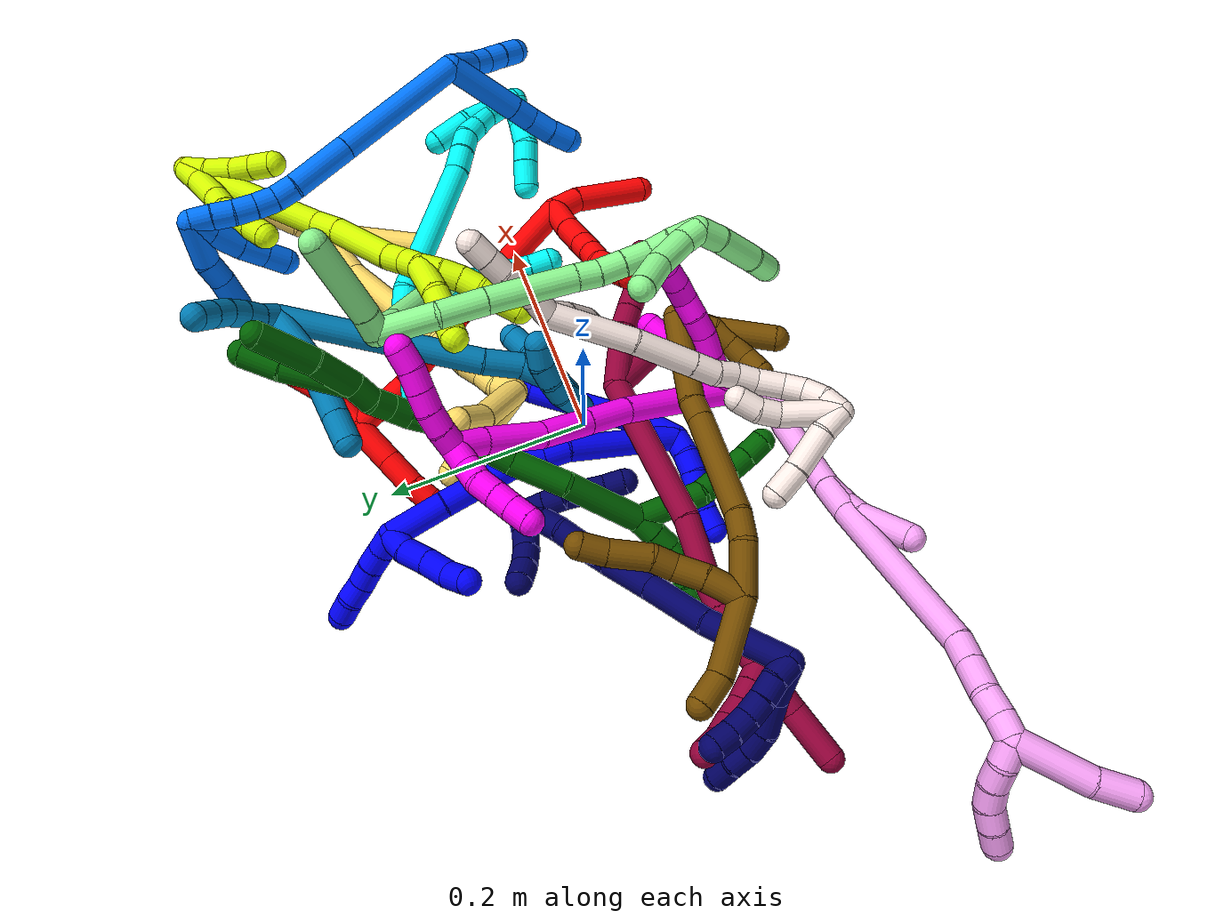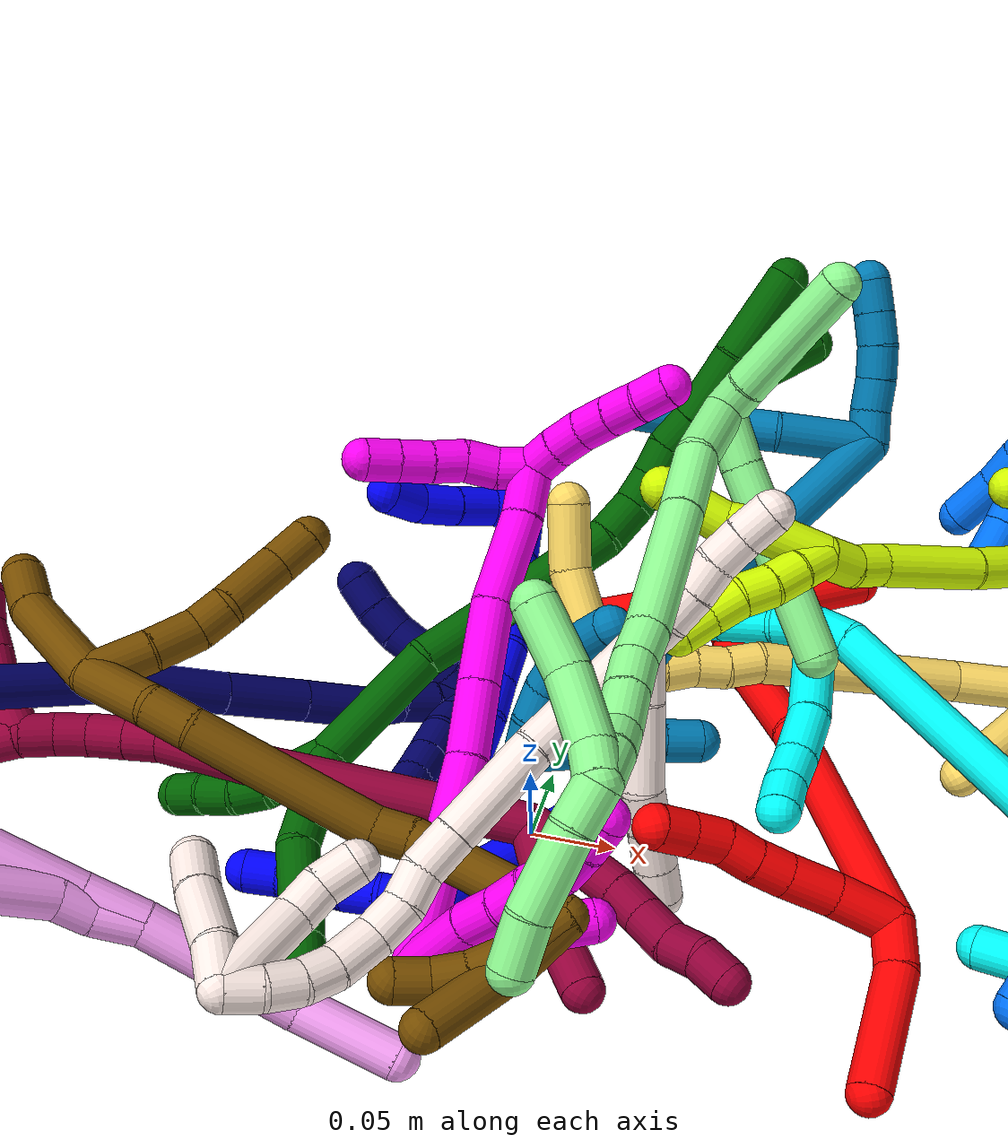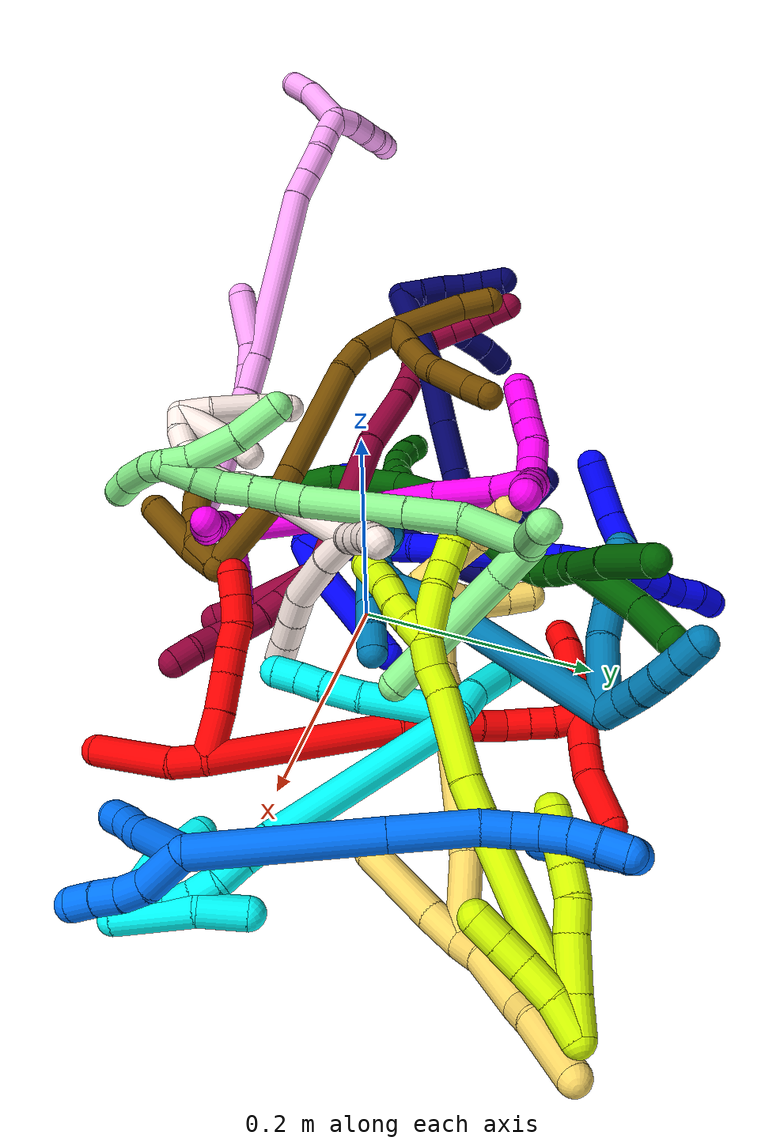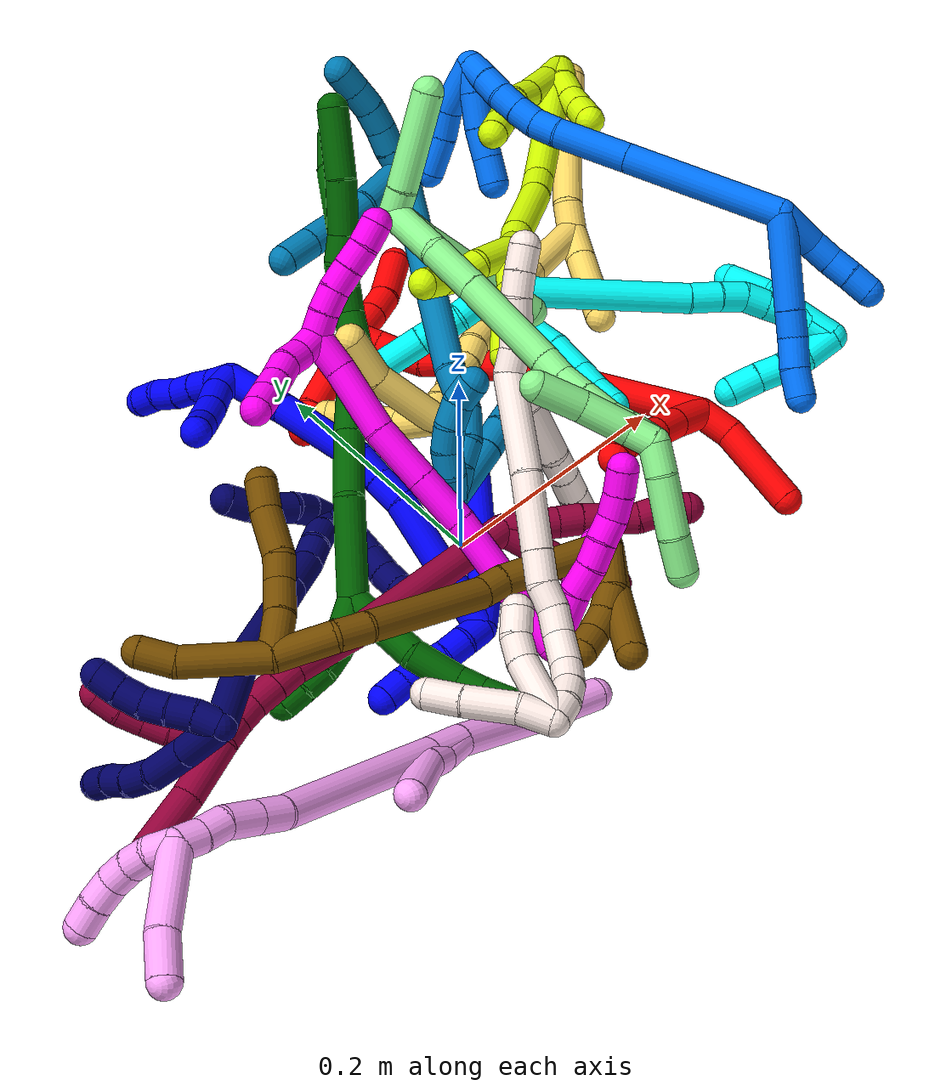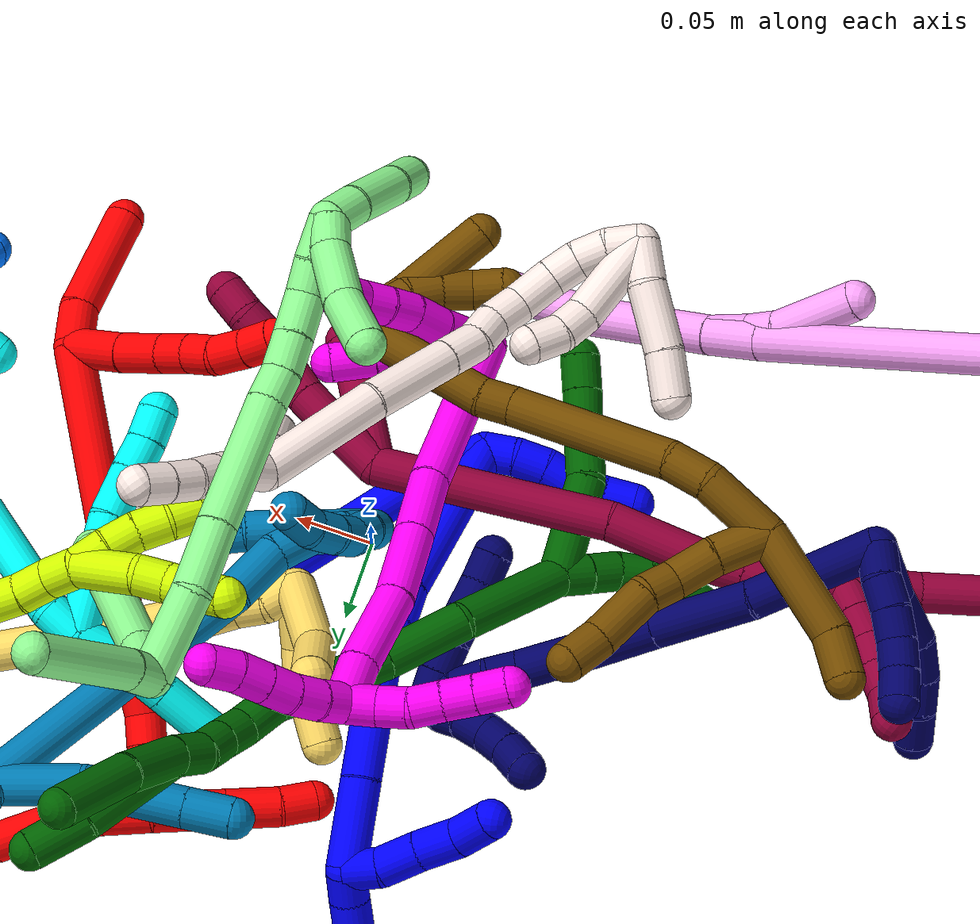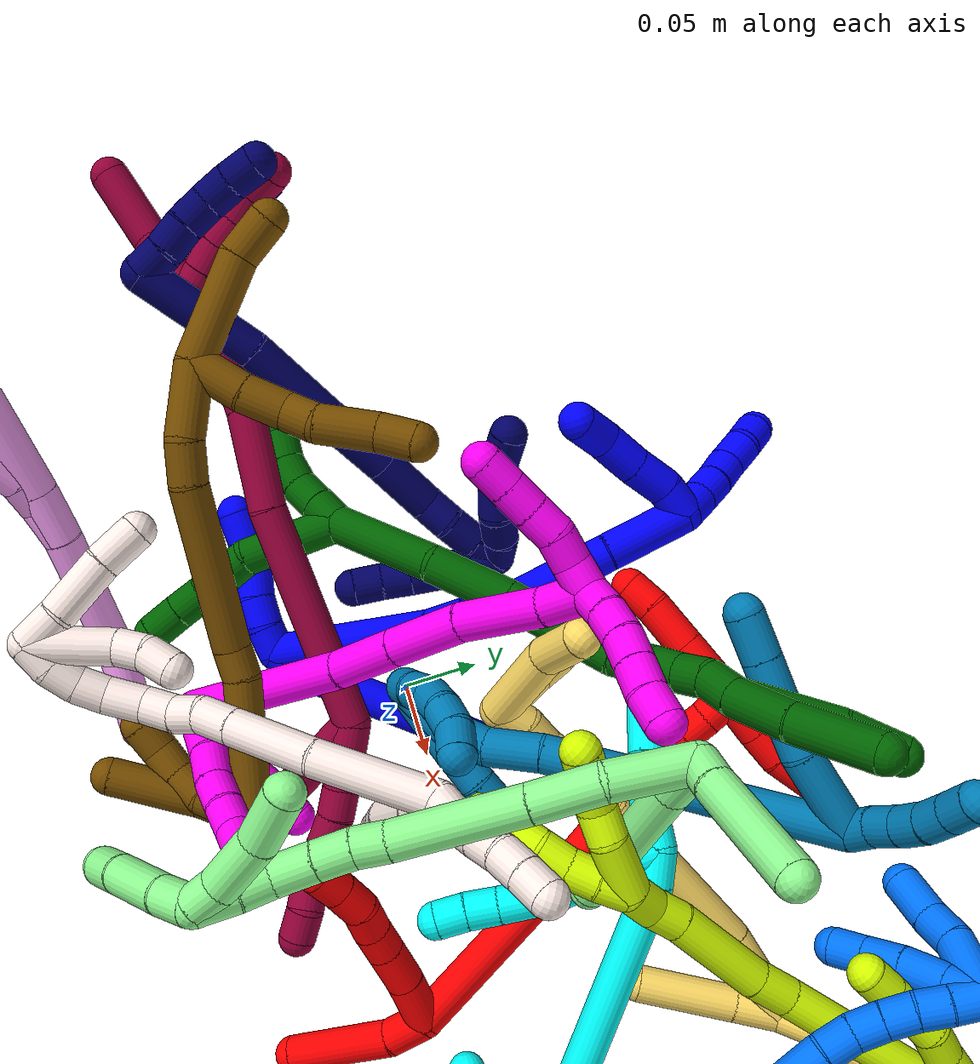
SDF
<sdf version="1.7">
 <world name="default">
  <plugin name="TubeGeneratorPlugin" filename="libtube_generator_plugin.so"/>
  <model name="photoneo_s_sensor">
   <static>1</static>
   <pose>0 0 2 1.57079 1.57079 3.14159</pose>
   <link name="link">
    <inertial><mass>0.1</mass></inertial>
    <sensor name="sensor" type="depth">
     <update_rate>30</update_rate>
     <camera>
      <horizontal_fov>1.22</horizontal_fov>
      <image><width>1920</width><height>1200</height><format>B8G8R8</format></image>
      <clip><near>0.1</near><far>4</far></clip>
      <depth_camera><output>points</output></depth_camera>
     </camera>
     <plugin name="camera_plugin" filename="libgazebo_ros_depth_camera.so">
      <baseline>0.2</baseline>
      <alwaysOn>1</alwaysOn>
      <updateRate>0.0</updateRate>
      <cameraName>camera_ir</cameraName>
      <imageTopicName>/camera/color/image_raw</imageTopicName>
      <cameraInfoTopicName>/camera/color/camera_info</cameraInfoTopicName>
      <depthImageTopicName>/camera/depth/image_raw</depthImageTopicName>
      <depthImageCameraInfoTopicName>/camera/depth/camera_info</depthImageCameraInfoTopicName>
      <pointCloudTopicName>/camera/depth/points</pointCloudTopicName>
      <frameName>fr_optical</frameName>
      <pointCloudCutoff>0.1</pointCloudCutoff>
      <pointCloudCutoffMax>2.0</pointCloudCutoffMax>
      <distortionK1>0</distortionK1>
      <distortionK2>0</distortionK2>
      <distortionK3>0</distortionK3>
      <distortionT1>0</distortionT1>
      <distortionT2>0</distortionT2>
      <CxPrime>0</CxPrime>
      <Cx>0</Cx>
      <Cy>0</Cy>
      <focalLength>0</focalLength>
      <hackBaseline>0</hackBaseline>
     </plugin>
    </sensor>
   </link>
  </model>
  <gravity>0 0 -9.8</gravity>
  <magnetic_field>6e-06 2.3e-05 -4.2e-05</magnetic_field>
  <atmosphere type="adiabatic"/>
  <physics name="default_physics" default="0" type="ode">
   <max_step_size>0.003</max_step_size>
   <real_time_factor>1</real_time_factor>
   <real_time_update_rate>1000</real_time_update_rate>
   <max_contacts>10000</max_contacts>
   <ode>
    <solver>
     <type>quick</type>
     <iters>100</iters>
     <sor>1.3</sor>
     <use_dynamic_moi_rescaling>0</use_dynamic_moi_rescaling>
    </solver>
    <constraints>
     <contact_max_correcting_vel>0</contact_max_correcting_vel>
     <contact_surface_layer>0.001</contact_surface_layer>
     <cfm>0</cfm>
     <erp>0.2</erp>
    </constraints>
   </ode>
  </physics>
  <scene><ambient>0.4 0.4 0.4 1</ambient><background>0.7 0.7 0.7 1</background><shadows>0</shadows></scene>
  <audio><device>default</device></audio>
  <spherical_coordinates>
   <surface_model>EARTH_WGS84</surface_model>
   <latitude_deg>0</latitude_deg>
   <longitude_deg>0</longitude_deg>
   <elevation>0</elevation>
   <heading_deg>0</heading_deg>
  </spherical_coordinates>
  <model name="bin">
   <static>1</static>
   <link name="bottom">
    <collision name="collision-bottom">
     <pose>0 0 -0.01 0 -0 0</pose>
     <geometry><box><size>0.8 0.6 0.02</size></box></geometry>
     <surface>
      <friction><ode><mu>100</mu><mu2>100</mu2></ode></friction>
      <contact><collide_bitmask>65535</collide_bitmask></contact>
     </surface>
    </collision>
   </link>
   <link name="west_wall">
    <collision name="collision-west_wall">
     <pose>-0.41 0 0.1 0 -0 0</pose>
     <geometry><box><size>0.02 0.6 0.2</size></box></geometry>
     <surface>
      <friction><ode><mu>100</mu><mu2>100</mu2></ode></friction>
      <contact><collide_bitmask>65535</collide_bitmask></contact>
     </surface>
    </collision>
   </link>
   <link name="east_wall">
    <collision name="collision-east_wall">
     <pose>0.41 0 0.1 0 -0 0</pose>
     <geometry><box><size>0.02 0.6 0.2</size></box></geometry>
     <surface>
      <friction><ode><mu>100</mu><mu2>100</mu2></ode></friction>
      <contact><collide_bitmask>65535</collide_bitmask></contact>
     </surface>
    </collision>
   </link>
   <link name="south_wall">
    <collision name="collision-south_wall">
     <pose>0 -0.31 0.1 0 -0 0</pose>
     <geometry><box><size>0.8 0.02 0.2</size></box></geometry>
     <surface>
      <friction><ode><mu>100</mu><mu2>100</mu2></ode></friction>
      <contact><collide_bitmask>65535</collide_bitmask></contact>
     </surface>
    </collision>
   </link>
   <link name="north_wall">
    <collision name="collision-north_wall">
     <pose>0 0.31 0.1 0 -0 0</pose>
     <geometry><box><size>0.8 0.02 0.2</size></box></geometry>
     <surface>
      <friction><ode><mu>100</mu><mu2>100</mu2></ode></friction>
      <contact><collide_bitmask>65535</collide_bitmask></contact>
     </surface>
    </collision>
   </link>
  </model>
  <model name="1">
   <static>0</static>
   <link name="1">
    <collision name="collision-cylinder-e_1_2_8">
     <pose>-0.001656 0.008867 0.011129 -0.672753 -0.115869 0.040555</pose>
     <geometry><cylinder><radius>0.0125</radius><length>0.028652</length></cylinder></geometry>
     <surface>
      <friction><ode><mu>1.16</mu><mu2>1.16</mu2><slip1>0</slip1><slip2>0</slip2></ode></friction>
      <contact><ode><kp>1e+06</kp><kd>1</kd><max_vel>0</max_vel><min_depth>0.001</min_depth></ode></contact>
     </surface>
    </collision>
    <visual name="visual-cylinder-e_1_2_8">
     <pose>-0.001656 0.008867 0.011129 -0.672753 -0.115869 0.040555</pose>
     <geometry><cylinder><radius>0.0125</radius><length>0.028652</length></cylinder></geometry>
     <material><ambient>0 0 1 1</ambient></material>
    </visual>
    <collision name="collision-cylinder-e_2_8_6">
     <pose>-0.005023 0.062824 0.062822 -0.838196 -0.028199 0.012563</pose>
     <geometry><cylinder><radius>0.0125</radius><length>0.121348</length></cylinder></geometry>
     <surface>
      <friction><ode><mu>1.16</mu><mu2>1.16</mu2><slip1>0</slip1><slip2>0</slip2></ode></friction>
      <contact><ode><kp>1e+06</kp><kd>1</kd><max_vel>0</max_vel><min_depth>0.001</min_depth></ode></contact>
     </surface>
    </collision>
    <visual name="visual-cylinder-e_2_8_6">
     <pose>-0.005023 0.062824 0.062822 -0.838196 -0.028199 0.012563</pose>
     <geometry><cylinder><radius>0.0125</radius><length>0.121348</length></cylinder></geometry>
     <material><ambient>0 0 1 1</ambient></material>
    </visual>
    <collision name="collision-cylinder-e_1_2_9">
     <pose>0.000923 -0.000393 -0.00995 3.10207 0.092385 2.33346</pose>
     <geometry><cylinder><radius>0.0125</radius><length>0.02</length></cylinder></geometry>
     <surface>
      <friction><ode><mu>1.16</mu><mu2>1.16</mu2><slip1>0</slip1><slip2>0</slip2></ode></friction>
      <contact><ode><kp>1e+06</kp><kd>1</kd><max_vel>0</max_vel><min_depth>0.001</min_depth></ode></contact>
     </surface>
    </collision>
    <visual name="visual-cylinder-e_1_2_9">
     <pose>0.000923 -0.000393 -0.00995 3.10207 0.092385 2.33346</pose>
     <geometry><cylinder><radius>0.0125</radius><length>0.02</length></cylinder></geometry>
     <material><ambient>0 0 1 1</ambient></material>
    </visual>
    <collision name="collision-cylinder-e_2_9_10">
     <pose>0.004962 -0.000444 -0.029395 -3.1055 0.316945 -2.91666</pose>
     <geometry><cylinder><radius>0.0125</radius><length>0.02</length></cylinder></geometry>
     <surface>
      <friction><ode><mu>1.16</mu><mu2>1.16</mu2><slip1>0</slip1><slip2>0</slip2></ode></friction>
      <contact><ode><kp>1e+06</kp><kd>1</kd><max_vel>0</max_vel><min_depth>0.001</min_depth></ode></contact>
     </surface>
    </collision>
    <visual name="visual-cylinder-e_2_9_10">
     <pose>0.004962 -0.000444 -0.029395 -3.1055 0.316945 -2.91666</pose>
     <geometry><cylinder><radius>0.0125</radius><length>0.02</length></cylinder></geometry>
     <material><ambient>0 0 1 1</ambient></material>
    </visual>
    <collision name="collision-cylinder-e_3_10_11">
     <pose>0.012155 0.001974 -0.047783 -2.91229 0.419894 -2.15066</pose>
     <geometry><cylinder><radius>0.0125</radius><length>0.02</length></cylinder></geometry>
     <surface>
      <friction><ode><mu>1.16</mu><mu2>1.16</mu2><slip1>0</slip1><slip2>0</slip2></ode></friction>
      <contact><ode><kp>1e+06</kp><kd>1</kd><max_vel>0</max_vel><min_depth>0.001</min_depth></ode></contact>
     </surface>
    </collision>
    <visual name="visual-cylinder-e_3_10_11">
     <pose>0.012155 0.001974 -0.047783 -2.91229 0.419894 -2.15066</pose>
     <geometry><cylinder><radius>0.0125</radius><length>0.02</length></cylinder></geometry>
     <material><ambient>0 0 1 1</ambient></material>
    </visual>
    <collision name="collision-cylinder-e_4_11_12">
     <pose>0.019177 0.004698 -0.06621 -3.07372 0.298952 -2.69815</pose>
     <geometry><cylinder><radius>0.0125</radius><length>0.02</length></cylinder></geometry>
     <surface>
      <friction><ode><mu>1.16</mu><mu2>1.16</mu2><slip1>0</slip1><slip2>0</slip2></ode></friction>
      <contact><ode><kp>1e+06</kp><kd>1</kd><max_vel>0</max_vel><min_depth>0.001</min_depth></ode></contact>
     </surface>
    </collision>
    <visual name="visual-cylinder-e_4_11_12">
     <pose>0.019177 0.004698 -0.06621 -3.07372 0.298952 -2.69815</pose>
     <geometry><cylinder><radius>0.0125</radius><length>0.02</length></cylinder></geometry>
     <material><ambient>0 0 1 1</ambient></material>
    </visual>
    <collision name="collision-cylinder-e_5_12_5">
     <pose>0.024532 0.005143 -0.085447 3.1206 0.243405 2.97039</pose>
     <geometry><cylinder><radius>0.0125</radius><length>0.02</length></cylinder></geometry>
     <surface>
      <friction><ode><mu>1.16</mu><mu2>1.16</mu2><slip1>0</slip1><slip2>0</slip2></ode></friction>
      <contact><ode><kp>1e+06</kp><kd>1</kd><max_vel>0</max_vel><min_depth>0.001</min_depth></ode></contact>
     </surface>
    </collision>
    <visual name="visual-cylinder-e_5_12_5">
     <pose>0.024532 0.005143 -0.085447 3.1206 0.243405 2.97039</pose>
     <geometry><cylinder><radius>0.0125</radius><length>0.02</length></cylinder></geometry>
     <material><ambient>0 0 1 1</ambient></material>
    </visual>
    <collision name="collision-cylinder-e_1_2_13">
     <pose>-0.015134 0.056591 0.005317 -1.47711 -0.260215 0.23714</pose>
     <geometry><cylinder><radius>0.0125</radius><length>0.11764</length></cylinder></geometry>
     <surface>
      <friction><ode><mu>1.16</mu><mu2>1.16</mu2><slip1>0</slip1><slip2>0</slip2></ode></friction>
      <contact><ode><kp>1e+06</kp><kd>1</kd><max_vel>0</max_vel><min_depth>0.001</min_depth></ode></contact>
     </surface>
    </collision>
    <visual name="visual-cylinder-e_1_2_13">
     <pose>-0.015134 0.056591 0.005317 -1.47711 -0.260215 0.23714</pose>
     <geometry><cylinder><radius>0.0125</radius><length>0.11764</length></cylinder></geometry>
     <material><ambient>0 0 1 1</ambient></material>
    </visual>
    <collision name="collision-cylinder-e_2_13_14">
     <pose>-0.030697 0.125929 0.010718 -1.56423 -0.033676 0.033456</pose>
     <geometry><cylinder><radius>0.0125</radius><length>0.025509</length></cylinder></geometry>
     <surface>
      <friction><ode><mu>1.16</mu><mu2>1.16</mu2><slip1>0</slip1><slip2>0</slip2></ode></friction>
      <contact><ode><kp>1e+06</kp><kd>1</kd><max_vel>0</max_vel><min_depth>0.001</min_depth></ode></contact>
     </surface>
    </collision>
    <visual name="visual-cylinder-e_2_13_14">
     <pose>-0.030697 0.125929 0.010718 -1.56423 -0.033676 0.033456</pose>
     <geometry><cylinder><radius>0.0125</radius><length>0.025509</length></cylinder></geometry>
     <material><ambient>0 0 1 1</ambient></material>
    </visual>
    <collision name="collision-cylinder-e_3_14_15">
     <pose>-0.032365 0.150869 0.011368 -1.52444 -0.101082 0.096508</pose>
     <geometry><cylinder><radius>0.0125</radius><length>0.024539</length></cylinder></geometry>
     <surface>
      <friction><ode><mu>1.16</mu><mu2>1.16</mu2><slip1>0</slip1><slip2>0</slip2></ode></friction>
      <contact><ode><kp>1e+06</kp><kd>1</kd><max_vel>0</max_vel><min_depth>0.001</min_depth></ode></contact>
     </surface>
    </collision>
    <visual name="visual-cylinder-e_3_14_15">
     <pose>-0.032365 0.150869 0.011368 -1.52444 -0.101082 0.096508</pose>
     <geometry><cylinder><radius>0.0125</radius><length>0.024539</length></cylinder></geometry>
     <material><ambient>0 0 1 1</ambient></material>
    </visual>
    <collision name="collision-cylinder-e_4_15_16">
     <pose>-0.027688 0.200886 0.008234 -1.66828 0.154391 -0.170154</pose>
     <geometry><cylinder><radius>0.0125</radius><length>0.076922</length></cylinder></geometry>
     <surface>
      <friction><ode><mu>1.16</mu><mu2>1.16</mu2><slip1>0</slip1><slip2>0</slip2></ode></friction>
      <contact><ode><kp>1e+06</kp><kd>1</kd><max_vel>0</max_vel><min_depth>0.001</min_depth></ode></contact>
     </surface>
    </collision>
    <visual name="visual-cylinder-e_4_15_16">
     <pose>-0.027688 0.200886 0.008234 -1.66828 0.154391 -0.170154</pose>
     <geometry><cylinder><radius>0.0125</radius><length>0.076922</length></cylinder></geometry>
     <material><ambient>0 0 1 1</ambient></material>
    </visual>
    <collision name="collision-cylinder-e_5_16_1">
     <pose>-0.015101 0.265515 0.002552 -1.64466 0.243337 -0.261804</pose>
     <geometry><cylinder><radius>0.0125</radius><length>0.05539</length></cylinder></geometry>
     <surface>
      <friction><ode><mu>1.16</mu><mu2>1.16</mu2><slip1>0</slip1><slip2>0</slip2></ode></friction>
      <contact><ode><kp>1e+06</kp><kd>1</kd><max_vel>0</max_vel><min_depth>0.001</min_depth></ode></contact>
     </surface>
    </collision>
    <visual name="visual-cylinder-e_5_16_1">
     <pose>-0.015101 0.265515 0.002552 -1.64466 0.243337 -0.261804</pose>
     <geometry><cylinder><radius>0.0125</radius><length>0.05539</length></cylinder></geometry>
     <material><ambient>0 0 1 1</ambient></material>
    </visual>
    <collision name="collision-cylinder-e_1_1_17">
     <pose>-0.009179 0.289448 -0.009894 2.87365 -0.069121 -0.502219</pose>
     <geometry><cylinder><radius>0.0125</radius><length>0.021751</length></cylinder></geometry>
     <surface>
      <friction><ode><mu>1.16</mu><mu2>1.16</mu2><slip1>0</slip1><slip2>0</slip2></ode></friction>
      <contact><ode><kp>1e+06</kp><kd>1</kd><max_vel>0</max_vel><min_depth>0.001</min_depth></ode></contact>
     </surface>
    </collision>
    <visual name="visual-cylinder-e_1_1_17">
     <pose>-0.009179 0.289448 -0.009894 2.87365 -0.069121 -0.502219</pose>
     <geometry><cylinder><radius>0.0125</radius><length>0.021751</length></cylinder></geometry>
     <material><ambient>0 0 1 1</ambient></material>
    </visual>
    <collision name="collision-cylinder-e_2_17_18">
     <pose>-0.012822 0.279815 -0.031559 2.59858 -0.217505 -0.747546</pose>
     <geometry><cylinder><radius>0.0125</radius><length>0.0268</length></cylinder></geometry>
     <surface>
      <friction><ode><mu>1.16</mu><mu2>1.16</mu2><slip1>0</slip1><slip2>0</slip2></ode></friction>
      <contact><ode><kp>1e+06</kp><kd>1</kd><max_vel>0</max_vel><min_depth>0.001</min_depth></ode></contact>
     </surface>
    </collision>
    <visual name="visual-cylinder-e_2_17_18">
     <pose>-0.012822 0.279815 -0.031559 2.59858 -0.217505 -0.747546</pose>
     <geometry><cylinder><radius>0.0125</radius><length>0.0268</length></cylinder></geometry>
     <material><ambient>0 0 1 1</ambient></material>
    </visual>
    <collision name="collision-cylinder-e_3_18_19">
     <pose>-0.01872 0.267329 -0.054286 2.6806 -0.229504 -0.91309</pose>
     <geometry><cylinder><radius>0.0125</radius><length>0.026431</length></cylinder></geometry>
     <surface>
      <friction><ode><mu>1.16</mu><mu2>1.16</mu2><slip1>0</slip1><slip2>0</slip2></ode></friction>
      <contact><ode><kp>1e+06</kp><kd>1</kd><max_vel>0</max_vel><min_depth>0.001</min_depth></ode></contact>
     </surface>
    </collision>
    <visual name="visual-cylinder-e_3_18_19">
     <pose>-0.01872 0.267329 -0.054286 2.6806 -0.229504 -0.91309</pose>
     <geometry><cylinder><radius>0.0125</radius><length>0.026431</length></cylinder></geometry>
     <material><ambient>0 0 1 1</ambient></material>
    </visual>
    <collision name="collision-cylinder-e_4_19_4">
     <pose>-0.028108 0.256656 -0.075365 2.66368 -0.535345 -1.68901</pose>
     <geometry><cylinder><radius>0.0125</radius><length>0.025018</length></cylinder></geometry>
     <surface>
      <friction><ode><mu>1.16</mu><mu2>1.16</mu2><slip1>0</slip1><slip2>0</slip2></ode></friction>
      <contact><ode><kp>1e+06</kp><kd>1</kd><max_vel>0</max_vel><min_depth>0.001</min_depth></ode></contact>
     </surface>
    </collision>
    <visual name="visual-cylinder-e_4_19_4">
     <pose>-0.028108 0.256656 -0.075365 2.66368 -0.535345 -1.68901</pose>
     <geometry><cylinder><radius>0.0125</radius><length>0.025018</length></cylinder></geometry>
     <material><ambient>0 0 1 1</ambient></material>
    </visual>
    <collision name="collision-cylinder-e_1_1_20">
     <pose>-0.000315 0.298079 -0.000439 -1.74388 0.946374 -1.0944</pose>
     <geometry><cylinder><radius>0.0125</radius><length>0.02</length></cylinder></geometry>
     <surface>
      <friction><ode><mu>1.16</mu><mu2>1.16</mu2><slip1>0</slip1><slip2>0</slip2></ode></friction>
      <contact><ode><kp>1e+06</kp><kd>1</kd><max_vel>0</max_vel><min_depth>0.001</min_depth></ode></contact>
     </surface>
    </collision>
    <visual name="visual-cylinder-e_1_1_20">
     <pose>-0.000315 0.298079 -0.000439 -1.74388 0.946374 -1.0944</pose>
     <geometry><cylinder><radius>0.0125</radius><length>0.02</length></cylinder></geometry>
     <material><ambient>0 0 1 1</ambient></material>
    </visual>
    <collision name="collision-cylinder-e_2_20_21">
     <pose>0.015282 0.310242 -0.003175 -1.83468 0.845577 -1.06252</pose>
     <geometry><cylinder><radius>0.0125</radius><length>0.02</length></cylinder></geometry>
     <surface>
      <friction><ode><mu>1.16</mu><mu2>1.16</mu2><slip1>0</slip1><slip2>0</slip2></ode></friction>
      <contact><ode><kp>1e+06</kp><kd>1</kd><max_vel>0</max_vel><min_depth>0.001</min_depth></ode></contact>
     </surface>
    </collision>
    <visual name="visual-cylinder-e_2_20_21">
     <pose>0.015282 0.310242 -0.003175 -1.83468 0.845577 -1.06252</pose>
     <geometry><cylinder><radius>0.0125</radius><length>0.02</length></cylinder></geometry>
     <material><ambient>0 0 1 1</ambient></material>
    </visual>
    <collision name="collision-cylinder-e_3_21_22">
     <pose>0.030708 0.32236 -0.006968 -1.9171 0.917765 -1.22617</pose>
     <geometry><cylinder><radius>0.0125</radius><length>0.02</length></cylinder></geometry>
     <surface>
      <friction><ode><mu>1.16</mu><mu2>1.16</mu2><slip1>0</slip1><slip2>0</slip2></ode></friction>
      <contact><ode><kp>1e+06</kp><kd>1</kd><max_vel>0</max_vel><min_depth>0.001</min_depth></ode></contact>
     </surface>
    </collision>
    <visual name="visual-cylinder-e_3_21_22">
     <pose>0.030708 0.32236 -0.006968 -1.9171 0.917765 -1.22617</pose>
     <geometry><cylinder><radius>0.0125</radius><length>0.02</length></cylinder></geometry>
     <material><ambient>0 0 1 1</ambient></material>
    </visual>
    <collision name="collision-cylinder-e_4_22_23">
     <pose>0.044933 0.335307 -0.011899 -1.94853 0.679385 -0.95969</pose>
     <geometry><cylinder><radius>0.0125</radius><length>0.02</length></cylinder></geometry>
     <surface>
      <friction><ode><mu>1.16</mu><mu2>1.16</mu2><slip1>0</slip1><slip2>0</slip2></ode></friction>
      <contact><ode><kp>1e+06</kp><kd>1</kd><max_vel>0</max_vel><min_depth>0.001</min_depth></ode></contact>
     </surface>
    </collision>
    <visual name="visual-cylinder-e_4_22_23">
     <pose>0.044933 0.335307 -0.011899 -1.94853 0.679385 -0.95969</pose>
     <geometry><cylinder><radius>0.0125</radius><length>0.02</length></cylinder></geometry>
     <material><ambient>0 0 1 1</ambient></material>
    </visual>
    <collision name="collision-cylinder-e_5_23_3">
     <pose>0.059455 0.347973 -0.016375 -1.85819 0.968189 -1.22646</pose>
     <geometry><cylinder><radius>0.0125</radius><length>0.02</length></cylinder></geometry>
     <surface>
      <friction><ode><mu>1.16</mu><mu2>1.16</mu2><slip1>0</slip1><slip2>0</slip2></ode></friction>
      <contact><ode><kp>1e+06</kp><kd>1</kd><max_vel>0</max_vel><min_depth>0.001</min_depth></ode></contact>
     </surface>
    </collision>
    <visual name="visual-cylinder-e_5_23_3">
     <pose>0.059455 0.347973 -0.016375 -1.85819 0.968189 -1.22646</pose>
     <geometry><cylinder><radius>0.0125</radius><length>0.02</length></cylinder></geometry>
     <material><ambient>0 0 1 1</ambient></material>
    </visual>
    <collision name="collision-sphere-3">
     <pose>0.067694 0.353409 -0.017982 0 -0 0</pose>
     <geometry><sphere><radius>0.0125</radius></sphere></geometry>
     <surface>
      <friction><ode><mu>1.16</mu><mu2>1.16</mu2><slip1>0</slip1><slip2>0</slip2></ode></friction>
      <contact><ode><kp>1e+06</kp><kd>1</kd><max_vel>0</max_vel><min_depth>0.001</min_depth></ode></contact>
     </surface>
    </collision>
    <visual name="visual-sphere-3">
     <pose>0.067694 0.353409 -0.017982 0 -0 0</pose>
     <geometry><sphere><radius>0.0125</radius></sphere></geometry>
     <material><ambient>0 0 1 1</ambient></material>
    </visual>
    <collision name="collision-sphere-23">
     <pose>0.051216 0.342538 -0.014769 0 -0 0</pose>
     <geometry><sphere><radius>0.0125</radius></sphere></geometry>
     <surface>
      <friction><ode><mu>1.16</mu><mu2>1.16</mu2><slip1>0</slip1><slip2>0</slip2></ode></friction>
      <contact><ode><kp>1e+06</kp><kd>1</kd><max_vel>0</max_vel><min_depth>0.001</min_depth></ode></contact>
     </surface>
    </collision>
    <visual name="visual-sphere-23">
     <pose>0.051216 0.342538 -0.014769 0 -0 0</pose>
     <geometry><sphere><radius>0.0125</radius></sphere></geometry>
     <material><ambient>0 0 1 1</ambient></material>
    </visual>
    <collision name="collision-sphere-22">
     <pose>0.03865 0.328075 -0.00903 0 -0 0</pose>
     <geometry><sphere><radius>0.0125</radius></sphere></geometry>
     <surface>
      <friction><ode><mu>1.16</mu><mu2>1.16</mu2><slip1>0</slip1><slip2>0</slip2></ode></friction>
      <contact><ode><kp>1e+06</kp><kd>1</kd><max_vel>0</max_vel><min_depth>0.001</min_depth></ode></contact>
     </surface>
    </collision>
    <visual name="visual-sphere-22">
     <pose>0.03865 0.328075 -0.00903 0 -0 0</pose>
     <geometry><sphere><radius>0.0125</radius></sphere></geometry>
     <material><ambient>0 0 1 1</ambient></material>
    </visual>
    <collision name="collision-sphere-21">
     <pose>0.022765 0.316645 -0.004906 0 -0 0</pose>
     <geometry><sphere><radius>0.0125</radius></sphere></geometry>
     <surface>
      <friction><ode><mu>1.16</mu><mu2>1.16</mu2><slip1>0</slip1><slip2>0</slip2></ode></friction>
      <contact><ode><kp>1e+06</kp><kd>1</kd><max_vel>0</max_vel><min_depth>0.001</min_depth></ode></contact>
     </surface>
    </collision>
    <visual name="visual-sphere-21">
     <pose>0.022765 0.316645 -0.004906 0 -0 0</pose>
     <geometry><sphere><radius>0.0125</radius></sphere></geometry>
     <material><ambient>0 0 1 1</ambient></material>
    </visual>
    <collision name="collision-sphere-20">
     <pose>0.007798 0.303838 -0.001445 0 -0 0</pose>
     <geometry><sphere><radius>0.0125</radius></sphere></geometry>
     <surface>
      <friction><ode><mu>1.16</mu><mu2>1.16</mu2><slip1>0</slip1><slip2>0</slip2></ode></friction>
      <contact><ode><kp>1e+06</kp><kd>1</kd><max_vel>0</max_vel><min_depth>0.001</min_depth></ode></contact>
     </surface>
    </collision>
    <visual name="visual-sphere-20">
     <pose>0.007798 0.303838 -0.001445 0 -0 0</pose>
     <geometry><sphere><radius>0.0125</radius></sphere></geometry>
     <material><ambient>0 0 1 1</ambient></material>
    </visual>
    <collision name="collision-sphere-4">
     <pose>-0.034489 0.251708 -0.084919 0 -0 0</pose>
     <geometry><sphere><radius>0.0125</radius></sphere></geometry>
     <surface>
      <friction><ode><mu>1.16</mu><mu2>1.16</mu2><slip1>0</slip1><slip2>0</slip2></ode></friction>
      <contact><ode><kp>1e+06</kp><kd>1</kd><max_vel>0</max_vel><min_depth>0.001</min_depth></ode></contact>
     </surface>
    </collision>
    <visual name="visual-sphere-4">
     <pose>-0.034489 0.251708 -0.084919 0 -0 0</pose>
     <geometry><sphere><radius>0.0125</radius></sphere></geometry>
     <material><ambient>0 0 1 1</ambient></material>
    </visual>
    <collision name="collision-sphere-11">
     <pose>0.016232 0.00405 -0.056675 0 -0 0</pose>
     <geometry><sphere><radius>0.0125</radius></sphere></geometry>
     <surface>
      <friction><ode><mu>1.16</mu><mu2>1.16</mu2><slip1>0</slip1><slip2>0</slip2></ode></friction>
      <contact><ode><kp>1e+06</kp><kd>1</kd><max_vel>0</max_vel><min_depth>0.001</min_depth></ode></contact>
     </surface>
    </collision>
    <visual name="visual-sphere-11">
     <pose>0.016232 0.00405 -0.056675 0 -0 0</pose>
     <geometry><sphere><radius>0.0125</radius></sphere></geometry>
     <material><ambient>0 0 1 1</ambient></material>
    </visual>
    <collision name="collision-sphere-10">
     <pose>0.008078 -0.000101 -0.038891 0 -0 0</pose>
     <geometry><sphere><radius>0.0125</radius></sphere></geometry>
     <surface>
      <friction><ode><mu>1.16</mu><mu2>1.16</mu2><slip1>0</slip1><slip2>0</slip2></ode></friction>
      <contact><ode><kp>1e+06</kp><kd>1</kd><max_vel>0</max_vel><min_depth>0.001</min_depth></ode></contact>
     </surface>
    </collision>
    <visual name="visual-sphere-10">
     <pose>0.008078 -0.000101 -0.038891 0 -0 0</pose>
     <geometry><sphere><radius>0.0125</radius></sphere></geometry>
     <material><ambient>0 0 1 1</ambient></material>
    </visual>
    <collision name="collision-sphere-6">
     <pose>-0.006734 0.107913 0.103385 0 -0 0</pose>
     <geometry><sphere><radius>0.0125</radius></sphere></geometry>
     <surface>
      <friction><ode><mu>1.16</mu><mu2>1.16</mu2><slip1>0</slip1><slip2>0</slip2></ode></friction>
      <contact><ode><kp>1e+06</kp><kd>1</kd><max_vel>0</max_vel><min_depth>0.001</min_depth></ode></contact>
     </surface>
    </collision>
    <visual name="visual-sphere-6">
     <pose>-0.006734 0.107913 0.103385 0 -0 0</pose>
     <geometry><sphere><radius>0.0125</radius></sphere></geometry>
     <material><ambient>0 0 1 1</ambient></material>
    </visual>
    <collision name="collision-sphere-9">
     <pose>0.001845 -0.000787 -0.019899 0 -0 0</pose>
     <geometry><sphere><radius>0.0125</radius></sphere></geometry>
     <surface>
      <friction><ode><mu>1.16</mu><mu2>1.16</mu2><slip1>0</slip1><slip2>0</slip2></ode></friction>
      <contact><ode><kp>1e+06</kp><kd>1</kd><max_vel>0</max_vel><min_depth>0.001</min_depth></ode></contact>
     </surface>
    </collision>
    <visual name="visual-sphere-9">
     <pose>0.001845 -0.000787 -0.019899 0 -0 0</pose>
     <geometry><sphere><radius>0.0125</radius></sphere></geometry>
     <material><ambient>0 0 1 1</ambient></material>
    </visual>
    <collision name="collision-sphere-2">
     <geometry><sphere><radius>0.0125</radius></sphere></geometry>
     <surface>
      <friction><ode><mu>1.16</mu><mu2>1.16</mu2><slip1>0</slip1><slip2>0</slip2></ode></friction>
      <contact><ode><kp>1e+06</kp><kd>1</kd><max_vel>0</max_vel><min_depth>0.001</min_depth></ode></contact>
     </surface>
    </collision>
    <visual name="visual-sphere-2">
     <geometry><sphere><radius>0.0125</radius></sphere></geometry>
     <material><ambient>0 0 1 1</ambient></material>
    </visual>
    <collision name="collision-sphere-19">
     <pose>-0.021726 0.261605 -0.065812 0 -0 0</pose>
     <geometry><sphere><radius>0.0125</radius></sphere></geometry>
     <surface>
      <friction><ode><mu>1.16</mu><mu2>1.16</mu2><slip1>0</slip1><slip2>0</slip2></ode></friction>
      <contact><ode><kp>1e+06</kp><kd>1</kd><max_vel>0</max_vel><min_depth>0.001</min_depth></ode></contact>
     </surface>
    </collision>
    <visual name="visual-sphere-19">
     <pose>-0.021726 0.261605 -0.065812 0 -0 0</pose>
     <geometry><sphere><radius>0.0125</radius></sphere></geometry>
     <material><ambient>0 0 1 1</ambient></material>
    </visual>
    <collision name="collision-sphere-8">
     <pose>-0.003312 0.017735 0.022259 0 -0 0</pose>
     <geometry><sphere><radius>0.0125</radius></sphere></geometry>
     <surface>
      <friction><ode><mu>1.16</mu><mu2>1.16</mu2><slip1>0</slip1><slip2>0</slip2></ode></friction>
      <contact><ode><kp>1e+06</kp><kd>1</kd><max_vel>0</max_vel><min_depth>0.001</min_depth></ode></contact>
     </surface>
    </collision>
    <visual name="visual-sphere-8">
     <pose>-0.003312 0.017735 0.022259 0 -0 0</pose>
     <geometry><sphere><radius>0.0125</radius></sphere></geometry>
     <material><ambient>0 0 1 1</ambient></material>
    </visual>
    <collision name="collision-sphere-12">
     <pose>0.022122 0.005346 -0.075744 0 -0 0</pose>
     <geometry><sphere><radius>0.0125</radius></sphere></geometry>
     <surface>
      <friction><ode><mu>1.16</mu><mu2>1.16</mu2><slip1>0</slip1><slip2>0</slip2></ode></friction>
      <contact><ode><kp>1e+06</kp><kd>1</kd><max_vel>0</max_vel><min_depth>0.001</min_depth></ode></contact>
     </surface>
    </collision>
    <visual name="visual-sphere-12">
     <pose>0.022122 0.005346 -0.075744 0 -0 0</pose>
     <geometry><sphere><radius>0.0125</radius></sphere></geometry>
     <material><ambient>0 0 1 1</ambient></material>
    </visual>
    <collision name="collision-sphere-5">
     <pose>0.026942 0.004939 -0.09515 0 -0 0</pose>
     <geometry><sphere><radius>0.0125</radius></sphere></geometry>
     <surface>
      <friction><ode><mu>1.16</mu><mu2>1.16</mu2><slip1>0</slip1><slip2>0</slip2></ode></friction>
      <contact><ode><kp>1e+06</kp><kd>1</kd><max_vel>0</max_vel><min_depth>0.001</min_depth></ode></contact>
     </surface>
    </collision>
    <visual name="visual-sphere-5">
     <pose>0.026942 0.004939 -0.09515 0 -0 0</pose>
     <geometry><sphere><radius>0.0125</radius></sphere></geometry>
     <material><ambient>0 0 1 1</ambient></material>
    </visual>
    <collision name="collision-sphere-13">
     <pose>-0.030268 0.113181 0.010635 0 -0 0</pose>
     <geometry><sphere><radius>0.0125</radius></sphere></geometry>
     <surface>
      <friction><ode><mu>1.16</mu><mu2>1.16</mu2><slip1>0</slip1><slip2>0</slip2></ode></friction>
      <contact><ode><kp>1e+06</kp><kd>1</kd><max_vel>0</max_vel><min_depth>0.001</min_depth></ode></contact>
     </surface>
    </collision>
    <visual name="visual-sphere-13">
     <pose>-0.030268 0.113181 0.010635 0 -0 0</pose>
     <geometry><sphere><radius>0.0125</radius></sphere></geometry>
     <material><ambient>0 0 1 1</ambient></material>
    </visual>
    <collision name="collision-sphere-14">
     <pose>-0.031126 0.138676 0.010802 0 -0 0</pose>
     <geometry><sphere><radius>0.0125</radius></sphere></geometry>
     <surface>
      <friction><ode><mu>1.16</mu><mu2>1.16</mu2><slip1>0</slip1><slip2>0</slip2></ode></friction>
      <contact><ode><kp>1e+06</kp><kd>1</kd><max_vel>0</max_vel><min_depth>0.001</min_depth></ode></contact>
     </surface>
    </collision>
    <visual name="visual-sphere-14">
     <pose>-0.031126 0.138676 0.010802 0 -0 0</pose>
     <geometry><sphere><radius>0.0125</radius></sphere></geometry>
     <material><ambient>0 0 1 1</ambient></material>
    </visual>
    <collision name="collision-sphere-15">
     <pose>-0.033603 0.163063 0.011933 0 -0 0</pose>
     <geometry><sphere><radius>0.0125</radius></sphere></geometry>
     <surface>
      <friction><ode><mu>1.16</mu><mu2>1.16</mu2><slip1>0</slip1><slip2>0</slip2></ode></friction>
      <contact><ode><kp>1e+06</kp><kd>1</kd><max_vel>0</max_vel><min_depth>0.001</min_depth></ode></contact>
     </surface>
    </collision>
    <visual name="visual-sphere-15">
     <pose>-0.033603 0.163063 0.011933 0 -0 0</pose>
     <geometry><sphere><radius>0.0125</radius></sphere></geometry>
     <material><ambient>0 0 1 1</ambient></material>
    </visual>
    <collision name="collision-sphere-16">
     <pose>-0.021774 0.238709 0.004535 0 -0 0</pose>
     <geometry><sphere><radius>0.0125</radius></sphere></geometry>
     <surface>
      <friction><ode><mu>1.16</mu><mu2>1.16</mu2><slip1>0</slip1><slip2>0</slip2></ode></friction>
      <contact><ode><kp>1e+06</kp><kd>1</kd><max_vel>0</max_vel><min_depth>0.001</min_depth></ode></contact>
     </surface>
    </collision>
    <visual name="visual-sphere-16">
     <pose>-0.021774 0.238709 0.004535 0 -0 0</pose>
     <geometry><sphere><radius>0.0125</radius></sphere></geometry>
     <material><ambient>0 0 1 1</ambient></material>
    </visual>
    <collision name="collision-sphere-1">
     <pose>-0.008428 0.29232 0.000568 0 -0 0</pose>
     <geometry><sphere><radius>0.0125</radius></sphere></geometry>
     <surface>
      <friction><ode><mu>1.16</mu><mu2>1.16</mu2><slip1>0</slip1><slip2>0</slip2></ode></friction>
      <contact><ode><kp>1e+06</kp><kd>1</kd><max_vel>0</max_vel><min_depth>0.001</min_depth></ode></contact>
     </surface>
    </collision>
    <visual name="visual-sphere-1">
     <pose>-0.008428 0.29232 0.000568 0 -0 0</pose>
     <geometry><sphere><radius>0.0125</radius></sphere></geometry>
     <material><ambient>0 0 1 1</ambient></material>
    </visual>
    <collision name="collision-sphere-18">
     <pose>-0.015713 0.273054 -0.042761 0 -0 0</pose>
     <geometry><sphere><radius>0.0125</radius></sphere></geometry>
     <surface>
      <friction><ode><mu>1.16</mu><mu2>1.16</mu2><slip1>0</slip1><slip2>0</slip2></ode></friction>
      <contact><ode><kp>1e+06</kp><kd>1</kd><max_vel>0</max_vel><min_depth>0.001</min_depth></ode></contact>
     </surface>
    </collision>
    <visual name="visual-sphere-18">
     <pose>-0.015713 0.273054 -0.042761 0 -0 0</pose>
     <geometry><sphere><radius>0.0125</radius></sphere></geometry>
     <material><ambient>0 0 1 1</ambient></material>
    </visual>
    <collision name="collision-sphere-17">
     <pose>-0.00993 0.286575 -0.020356 0 -0 0</pose>
     <geometry><sphere><radius>0.0125</radius></sphere></geometry>
     <surface>
      <friction><ode><mu>1.16</mu><mu2>1.16</mu2><slip1>0</slip1><slip2>0</slip2></ode></friction>
      <contact><ode><kp>1e+06</kp><kd>1</kd><max_vel>0</max_vel><min_depth>0.001</min_depth></ode></contact>
     </surface>
    </collision>
    <visual name="visual-sphere-17">
     <pose>-0.00993 0.286575 -0.020356 0 -0 0</pose>
     <geometry><sphere><radius>0.0125</radius></sphere></geometry>
     <material><ambient>0 0 1 1</ambient></material>
    </visual>
    <inertial>
     <pose>-0.005981 0.148519 -5.2e-05 0 -0 0</pose>
     <mass>0.75</mass>
     <inertia>
      <ixx>0.000366</ixx>
      <ixy>0</ixy>
      <ixz>0</ixz>
      <iyy>0.000175</iyy>
      <iyz>0</iyz>
      <izz>-0.000294</izz>
     </inertia>
    </inertial>
   </link>
   <pose>-0.048445 -0.076681 0.012782 2.55036 1.26567 2.61462</pose>
  </model>
  <model name="2">
   <static>0</static>
   <link name="2">
    <collision name="collision-cylinder-e_1_2_8">
     <pose>-0.010864 0.001803 -0.015201 -3.02351 -0.617224 2.77492</pose>
     <geometry><cylinder><radius>0.0125</radius><length>0.037543</length></cylinder></geometry>
     <surface>
      <friction><ode><mu>1.16</mu><mu2>1.16</mu2><slip1>0</slip1><slip2>0</slip2></ode></friction>
      <contact><ode><kp>1e+06</kp><kd>1</kd><max_vel>0</max_vel><min_depth>0.001</min_depth></ode></contact>
     </surface>
    </collision>
    <visual name="visual-cylinder-e_1_2_8">
     <pose>-0.010864 0.001803 -0.015201 -3.02351 -0.617224 2.77492</pose>
     <geometry><cylinder><radius>0.0125</radius><length>0.037543</length></cylinder></geometry>
     <material><ambient>1 0 0 1</ambient></material>
    </visual>
    <collision name="collision-cylinder-e_2_8_9">
     <pose>-0.029766 0.004052 -0.042951 -3.10614 -0.569348 3.02057</pose>
     <geometry><cylinder><radius>0.0125</radius><length>0.029816</length></cylinder></geometry>
     <surface>
      <friction><ode><mu>1.16</mu><mu2>1.16</mu2><slip1>0</slip1><slip2>0</slip2></ode></friction>
      <contact><ode><kp>1e+06</kp><kd>1</kd><max_vel>0</max_vel><min_depth>0.001</min_depth></ode></contact>
     </surface>
    </collision>
    <visual name="visual-cylinder-e_2_8_9">
     <pose>-0.029766 0.004052 -0.042951 -3.10614 -0.569348 3.02057</pose>
     <geometry><cylinder><radius>0.0125</radius><length>0.029816</length></cylinder></geometry>
     <material><ambient>1 0 0 1</ambient></material>
    </visual>
    <collision name="collision-cylinder-e_3_9_10">
     <pose>-0.043634 0.004515 -0.063784 -3.13941 -0.61335 3.1347</pose>
     <geometry><cylinder><radius>0.0125</radius><length>0.020262</length></cylinder></geometry>
     <surface>
      <friction><ode><mu>1.16</mu><mu2>1.16</mu2><slip1>0</slip1><slip2>0</slip2></ode></friction>
      <contact><ode><kp>1e+06</kp><kd>1</kd><max_vel>0</max_vel><min_depth>0.001</min_depth></ode></contact>
     </surface>
    </collision>
    <visual name="visual-cylinder-e_3_9_10">
     <pose>-0.043634 0.004515 -0.063784 -3.13941 -0.61335 3.1347</pose>
     <geometry><cylinder><radius>0.0125</radius><length>0.020262</length></cylinder></geometry>
     <material><ambient>1 0 0 1</ambient></material>
    </visual>
    <collision name="collision-cylinder-e_4_10_11">
     <pose>-0.05612 0.004737 -0.079702 -3.11484 -0.716793 3.07021</pose>
     <geometry><cylinder><radius>0.0125</radius><length>0.020257</length></cylinder></geometry>
     <surface>
      <friction><ode><mu>1.16</mu><mu2>1.16</mu2><slip1>0</slip1><slip2>0</slip2></ode></friction>
      <contact><ode><kp>1e+06</kp><kd>1</kd><max_vel>0</max_vel><min_depth>0.001</min_depth></ode></contact>
     </surface>
    </collision>
    <visual name="visual-cylinder-e_4_10_11">
     <pose>-0.05612 0.004737 -0.079702 -3.11484 -0.716793 3.07021</pose>
     <geometry><cylinder><radius>0.0125</radius><length>0.020257</length></cylinder></geometry>
     <material><ambient>1 0 0 1</ambient></material>
    </visual>
    <collision name="collision-cylinder-e_5_11_12">
     <pose>-0.067458 0.003157 -0.097165 2.962 -0.438407 -2.37343</pose>
     <geometry><cylinder><radius>0.0125</radius><length>0.022068</length></cylinder></geometry>
     <surface>
      <friction><ode><mu>1.16</mu><mu2>1.16</mu2><slip1>0</slip1><slip2>0</slip2></ode></friction>
      <contact><ode><kp>1e+06</kp><kd>1</kd><max_vel>0</max_vel><min_depth>0.001</min_depth></ode></contact>
     </surface>
    </collision>
    <visual name="visual-cylinder-e_5_11_12">
     <pose>-0.067458 0.003157 -0.097165 2.962 -0.438407 -2.37343</pose>
     <geometry><cylinder><radius>0.0125</radius><length>0.022068</length></cylinder></geometry>
     <material><ambient>1 0 0 1</ambient></material>
    </visual>
    <collision name="collision-cylinder-e_6_12_6">
     <pose>-0.076292 -0.001038 -0.115798 2.87438 -0.426776 -2.03119</pose>
     <geometry><cylinder><radius>0.0125</radius><length>0.020054</length></cylinder></geometry>
     <surface>
      <friction><ode><mu>1.16</mu><mu2>1.16</mu2><slip1>0</slip1><slip2>0</slip2></ode></friction>
      <contact><ode><kp>1e+06</kp><kd>1</kd><max_vel>0</max_vel><min_depth>0.001</min_depth></ode></contact>
     </surface>
    </collision>
    <visual name="visual-cylinder-e_6_12_6">
     <pose>-0.076292 -0.001038 -0.115798 2.87438 -0.426776 -2.03119</pose>
     <geometry><cylinder><radius>0.0125</radius><length>0.020054</length></cylinder></geometry>
     <material><ambient>1 0 0 1</ambient></material>
    </visual>
    <collision name="collision-cylinder-e_1_2_13">
     <pose>0.010619 -0.008432 -0.004123 2.02556 0.846981 1.25089</pose>
     <geometry><cylinder><radius>0.0125</radius><length>0.028346</length></cylinder></geometry>
     <surface>
      <friction><ode><mu>1.16</mu><mu2>1.16</mu2><slip1>0</slip1><slip2>0</slip2></ode></friction>
      <contact><ode><kp>1e+06</kp><kd>1</kd><max_vel>0</max_vel><min_depth>0.001</min_depth></ode></contact>
     </surface>
    </collision>
    <visual name="visual-cylinder-e_1_2_13">
     <pose>0.010619 -0.008432 -0.004123 2.02556 0.846981 1.25089</pose>
     <geometry><cylinder><radius>0.0125</radius><length>0.028346</length></cylinder></geometry>
     <material><ambient>1 0 0 1</ambient></material>
    </visual>
    <collision name="collision-cylinder-e_2_13_5">
     <pose>0.045373 -0.034532 -0.027967 2.41105 0.739116 1.58358</pose>
     <geometry><cylinder><radius>0.0125</radius><length>0.071654</length></cylinder></geometry>
     <surface>
      <friction><ode><mu>1.16</mu><mu2>1.16</mu2><slip1>0</slip1><slip2>0</slip2></ode></friction>
      <contact><ode><kp>1e+06</kp><kd>1</kd><max_vel>0</max_vel><min_depth>0.001</min_depth></ode></contact>
     </surface>
    </collision>
    <visual name="visual-cylinder-e_2_13_5">
     <pose>0.045373 -0.034532 -0.027967 2.41105 0.739116 1.58358</pose>
     <geometry><cylinder><radius>0.0125</radius><length>0.071654</length></cylinder></geometry>
     <material><ambient>1 0 0 1</ambient></material>
    </visual>
    <collision name="collision-cylinder-e_1_2_14">
     <pose>-0.044547 0.061 0.002425 -1.53106 -0.630385 0.607328</pose>
     <geometry><cylinder><radius>0.0125</radius><length>0.151147</length></cylinder></geometry>
     <surface>
      <friction><ode><mu>1.16</mu><mu2>1.16</mu2><slip1>0</slip1><slip2>0</slip2></ode></friction>
      <contact><ode><kp>1e+06</kp><kd>1</kd><max_vel>0</max_vel><min_depth>0.001</min_depth></ode></contact>
     </surface>
    </collision>
    <visual name="visual-cylinder-e_1_2_14">
     <pose>-0.044547 0.061 0.002425 -1.53106 -0.630385 0.607328</pose>
     <geometry><cylinder><radius>0.0125</radius><length>0.151147</length></cylinder></geometry>
     <material><ambient>1 0 0 1</ambient></material>
    </visual>
    <collision name="collision-cylinder-e_2_14_15">
     <pose>-0.101935 0.152126 0.006085 -1.52986 -0.402618 0.386874</pose>
     <geometry><cylinder><radius>0.0125</radius><length>0.065542</length></cylinder></geometry>
     <surface>
      <friction><ode><mu>1.16</mu><mu2>1.16</mu2><slip1>0</slip1><slip2>0</slip2></ode></friction>
      <contact><ode><kp>1e+06</kp><kd>1</kd><max_vel>0</max_vel><min_depth>0.001</min_depth></ode></contact>
     </surface>
    </collision>
    <visual name="visual-cylinder-e_2_14_15">
     <pose>-0.101935 0.152126 0.006085 -1.52986 -0.402618 0.386874</pose>
     <geometry><cylinder><radius>0.0125</radius><length>0.065542</length></cylinder></geometry>
     <material><ambient>1 0 0 1</ambient></material>
    </visual>
    <collision name="collision-cylinder-e_3_15_16">
     <pose>-0.1181 0.192106 0.007223 -1.58044 -0.325301 0.328399</pose>
     <geometry><cylinder><radius>0.0125</radius><length>0.020802</length></cylinder></geometry>
     <surface>
      <friction><ode><mu>1.16</mu><mu2>1.16</mu2><slip1>0</slip1><slip2>0</slip2></ode></friction>
      <contact><ode><kp>1e+06</kp><kd>1</kd><max_vel>0</max_vel><min_depth>0.001</min_depth></ode></contact>
     </surface>
    </collision>
    <visual name="visual-cylinder-e_3_15_16">
     <pose>-0.1181 0.192106 0.007223 -1.58044 -0.325301 0.328399</pose>
     <geometry><cylinder><radius>0.0125</radius><length>0.020802</length></cylinder></geometry>
     <material><ambient>1 0 0 1</ambient></material>
    </visual>
    <collision name="collision-cylinder-e_4_16_17">
     <pose>-0.127415 0.21036 0.008614 -1.39572 -0.612341 0.518283</pose>
     <geometry><cylinder><radius>0.0125</radius><length>0.020845</length></cylinder></geometry>
     <surface>
      <friction><ode><mu>1.16</mu><mu2>1.16</mu2><slip1>0</slip1><slip2>0</slip2></ode></friction>
      <contact><ode><kp>1e+06</kp><kd>1</kd><max_vel>0</max_vel><min_depth>0.001</min_depth></ode></contact>
     </surface>
    </collision>
    <visual name="visual-cylinder-e_4_16_17">
     <pose>-0.127415 0.21036 0.008614 -1.39572 -0.612341 0.518283</pose>
     <geometry><cylinder><radius>0.0125</radius><length>0.020845</length></cylinder></geometry>
     <material><ambient>1 0 0 1</ambient></material>
    </visual>
    <collision name="collision-cylinder-e_5_17_18">
     <pose>-0.139386 0.226627 0.012049 -1.3279 -0.635598 0.503839</pose>
     <geometry><cylinder><radius>0.0125</radius><length>0.020148</length></cylinder></geometry>
     <surface>
      <friction><ode><mu>1.16</mu><mu2>1.16</mu2><slip1>0</slip1><slip2>0</slip2></ode></friction>
      <contact><ode><kp>1e+06</kp><kd>1</kd><max_vel>0</max_vel><min_depth>0.001</min_depth></ode></contact>
     </surface>
    </collision>
    <visual name="visual-cylinder-e_5_17_18">
     <pose>-0.139386 0.226627 0.012049 -1.3279 -0.635598 0.503839</pose>
     <geometry><cylinder><radius>0.0125</radius><length>0.020148</length></cylinder></geometry>
     <material><ambient>1 0 0 1</ambient></material>
    </visual>
    <collision name="collision-cylinder-e_6_18_1">
     <pose>-0.152845 0.242204 0.014607 -1.49206 -0.768726 0.715478</pose>
     <geometry><cylinder><radius>0.0125</radius><length>0.021516</length></cylinder></geometry>
     <surface>
      <friction><ode><mu>1.16</mu><mu2>1.16</mu2><slip1>0</slip1><slip2>0</slip2></ode></friction>
      <contact><ode><kp>1e+06</kp><kd>1</kd><max_vel>0</max_vel><min_depth>0.001</min_depth></ode></contact>
     </surface>
    </collision>
    <visual name="visual-cylinder-e_6_18_1">
     <pose>-0.152845 0.242204 0.014607 -1.49206 -0.768726 0.715478</pose>
     <geometry><cylinder><radius>0.0125</radius><length>0.021516</length></cylinder></geometry>
     <material><ambient>1 0 0 1</ambient></material>
    </visual>
    <collision name="collision-cylinder-e_1_1_19">
     <pose>-0.15713 0.248456 0.03053 0.094839 0.204747 0.00975</pose>
     <geometry><cylinder><radius>0.0125</radius><length>0.031425</length></cylinder></geometry>
     <surface>
      <friction><ode><mu>1.16</mu><mu2>1.16</mu2><slip1>0</slip1><slip2>0</slip2></ode></friction>
      <contact><ode><kp>1e+06</kp><kd>1</kd><max_vel>0</max_vel><min_depth>0.001</min_depth></ode></contact>
     </surface>
    </collision>
    <visual name="visual-cylinder-e_1_1_19">
     <pose>-0.15713 0.248456 0.03053 0.094839 0.204747 0.00975</pose>
     <geometry><cylinder><radius>0.0125</radius><length>0.031425</length></cylinder></geometry>
     <material><ambient>1 0 0 1</ambient></material>
    </visual>
    <collision name="collision-cylinder-e_2_19_20">
     <pose>-0.15225 0.245999 0.057452 0.086013 0.143661 0.006193</pose>
     <geometry><cylinder><radius>0.0125</radius><length>0.023541</length></cylinder></geometry>
     <surface>
      <friction><ode><mu>1.16</mu><mu2>1.16</mu2><slip1>0</slip1><slip2>0</slip2></ode></friction>
      <contact><ode><kp>1e+06</kp><kd>1</kd><max_vel>0</max_vel><min_depth>0.001</min_depth></ode></contact>
     </surface>
    </collision>
    <visual name="visual-cylinder-e_2_19_20">
     <pose>-0.15225 0.245999 0.057452 0.086013 0.143661 0.006193</pose>
     <geometry><cylinder><radius>0.0125</radius><length>0.023541</length></cylinder></geometry>
     <material><ambient>1 0 0 1</ambient></material>
    </visual>
    <collision name="collision-cylinder-e_3_20_4">
     <pose>-0.15053 0.247559 0.091429 -0.113992 0.001532 -8.7e-05</pose>
     <geometry><cylinder><radius>0.0125</radius><length>0.045034</length></cylinder></geometry>
     <surface>
      <friction><ode><mu>1.16</mu><mu2>1.16</mu2><slip1>0</slip1><slip2>0</slip2></ode></friction>
      <contact><ode><kp>1e+06</kp><kd>1</kd><max_vel>0</max_vel><min_depth>0.001</min_depth></ode></contact>
     </surface>
    </collision>
    <visual name="visual-cylinder-e_3_20_4">
     <pose>-0.15053 0.247559 0.091429 -0.113992 0.001532 -8.7e-05</pose>
     <geometry><cylinder><radius>0.0125</radius><length>0.045034</length></cylinder></geometry>
     <material><ambient>1 0 0 1</ambient></material>
    </visual>
    <collision name="collision-cylinder-e_1_1_21">
     <pose>-0.159972 0.25466 -0.006671 -2.92801 0.015738 -0.146546</pose>
     <geometry><cylinder><radius>0.0125</radius><length>0.044795</length></cylinder></geometry>
     <surface>
      <friction><ode><mu>1.16</mu><mu2>1.16</mu2><slip1>0</slip1><slip2>0</slip2></ode></friction>
      <contact><ode><kp>1e+06</kp><kd>1</kd><max_vel>0</max_vel><min_depth>0.001</min_depth></ode></contact>
     </surface>
    </collision>
    <visual name="visual-cylinder-e_1_1_21">
     <pose>-0.159972 0.25466 -0.006671 -2.92801 0.015738 -0.146546</pose>
     <geometry><cylinder><radius>0.0125</radius><length>0.044795</length></cylinder></geometry>
     <material><ambient>1 0 0 1</ambient></material>
    </visual>
    <collision name="collision-cylinder-e_2_21_22">
     <pose>-0.159353 0.262965 -0.044968 -2.92809 0.015871 -0.147839</pose>
     <geometry><cylinder><radius>0.0125</radius><length>0.033591</length></cylinder></geometry>
     <surface>
      <friction><ode><mu>1.16</mu><mu2>1.16</mu2><slip1>0</slip1><slip2>0</slip2></ode></friction>
      <contact><ode><kp>1e+06</kp><kd>1</kd><max_vel>0</max_vel><min_depth>0.001</min_depth></ode></contact>
     </surface>
    </collision>
    <visual name="visual-cylinder-e_2_21_22">
     <pose>-0.159353 0.262965 -0.044968 -2.92809 0.015871 -0.147839</pose>
     <geometry><cylinder><radius>0.0125</radius><length>0.033591</length></cylinder></geometry>
     <material><ambient>1 0 0 1</ambient></material>
    </visual>
    <collision name="collision-cylinder-e_3_22_3">
     <pose>-0.157111 0.268123 -0.071884 -2.9905 0.183808 -1.76642</pose>
     <geometry><cylinder><radius>0.0125</radius><length>0.021614</length></cylinder></geometry>
     <surface>
      <friction><ode><mu>1.16</mu><mu2>1.16</mu2><slip1>0</slip1><slip2>0</slip2></ode></friction>
      <contact><ode><kp>1e+06</kp><kd>1</kd><max_vel>0</max_vel><min_depth>0.001</min_depth></ode></contact>
     </surface>
    </collision>
    <visual name="visual-cylinder-e_3_22_3">
     <pose>-0.157111 0.268123 -0.071884 -2.9905 0.183808 -1.76642</pose>
     <geometry><cylinder><radius>0.0125</radius><length>0.021614</length></cylinder></geometry>
     <material><ambient>1 0 0 1</ambient></material>
    </visual>
    <collision name="collision-sphere-3">
     <pose>-0.155136 0.269722 -0.082388 0 -0 0</pose>
     <geometry><sphere><radius>0.0125</radius></sphere></geometry>
     <surface>
      <friction><ode><mu>1.16</mu><mu2>1.16</mu2><slip1>0</slip1><slip2>0</slip2></ode></friction>
      <contact><ode><kp>1e+06</kp><kd>1</kd><max_vel>0</max_vel><min_depth>0.001</min_depth></ode></contact>
     </surface>
    </collision>
    <visual name="visual-sphere-3">
     <pose>-0.155136 0.269722 -0.082388 0 -0 0</pose>
     <geometry><sphere><radius>0.0125</radius></sphere></geometry>
     <material><ambient>1 0 0 1</ambient></material>
    </visual>
    <collision name="collision-sphere-22">
     <pose>-0.159086 0.266523 -0.06138 0 -0 0</pose>
     <geometry><sphere><radius>0.0125</radius></sphere></geometry>
     <surface>
      <friction><ode><mu>1.16</mu><mu2>1.16</mu2><slip1>0</slip1><slip2>0</slip2></ode></friction>
      <contact><ode><kp>1e+06</kp><kd>1</kd><max_vel>0</max_vel><min_depth>0.001</min_depth></ode></contact>
     </surface>
    </collision>
    <visual name="visual-sphere-22">
     <pose>-0.159086 0.266523 -0.06138 0 -0 0</pose>
     <geometry><sphere><radius>0.0125</radius></sphere></geometry>
     <material><ambient>1 0 0 1</ambient></material>
    </visual>
    <collision name="collision-sphere-21">
     <pose>-0.159619 0.259407 -0.028556 0 -0 0</pose>
     <geometry><sphere><radius>0.0125</radius></sphere></geometry>
     <surface>
      <friction><ode><mu>1.16</mu><mu2>1.16</mu2><slip1>0</slip1><slip2>0</slip2></ode></friction>
      <contact><ode><kp>1e+06</kp><kd>1</kd><max_vel>0</max_vel><min_depth>0.001</min_depth></ode></contact>
     </surface>
    </collision>
    <visual name="visual-sphere-21">
     <pose>-0.159619 0.259407 -0.028556 0 -0 0</pose>
     <geometry><sphere><radius>0.0125</radius></sphere></geometry>
     <material><ambient>1 0 0 1</ambient></material>
    </visual>
    <collision name="collision-sphere-4">
     <pose>-0.150496 0.25012 0.1138 0 -0 0</pose>
     <geometry><sphere><radius>0.0125</radius></sphere></geometry>
     <surface>
      <friction><ode><mu>1.16</mu><mu2>1.16</mu2><slip1>0</slip1><slip2>0</slip2></ode></friction>
      <contact><ode><kp>1e+06</kp><kd>1</kd><max_vel>0</max_vel><min_depth>0.001</min_depth></ode></contact>
     </surface>
    </collision>
    <visual name="visual-sphere-4">
     <pose>-0.150496 0.25012 0.1138 0 -0 0</pose>
     <geometry><sphere><radius>0.0125</radius></sphere></geometry>
     <material><ambient>1 0 0 1</ambient></material>
    </visual>
    <collision name="collision-sphere-20">
     <pose>-0.150565 0.244998 0.069058 0 -0 0</pose>
     <geometry><sphere><radius>0.0125</radius></sphere></geometry>
     <surface>
      <friction><ode><mu>1.16</mu><mu2>1.16</mu2><slip1>0</slip1><slip2>0</slip2></ode></friction>
      <contact><ode><kp>1e+06</kp><kd>1</kd><max_vel>0</max_vel><min_depth>0.001</min_depth></ode></contact>
     </surface>
    </collision>
    <visual name="visual-sphere-20">
     <pose>-0.150565 0.244998 0.069058 0 -0 0</pose>
     <geometry><sphere><radius>0.0125</radius></sphere></geometry>
     <material><ambient>1 0 0 1</ambient></material>
    </visual>
    <collision name="collision-sphere-12">
     <pose>-0.072142 0.001372 -0.106995 0 -0 0</pose>
     <geometry><sphere><radius>0.0125</radius></sphere></geometry>
     <surface>
      <friction><ode><mu>1.16</mu><mu2>1.16</mu2><slip1>0</slip1><slip2>0</slip2></ode></friction>
      <contact><ode><kp>1e+06</kp><kd>1</kd><max_vel>0</max_vel><min_depth>0.001</min_depth></ode></contact>
     </surface>
    </collision>
    <visual name="visual-sphere-12">
     <pose>-0.072142 0.001372 -0.106995 0 -0 0</pose>
     <geometry><sphere><radius>0.0125</radius></sphere></geometry>
     <material><ambient>1 0 0 1</ambient></material>
    </visual>
    <collision name="collision-sphere-11">
     <pose>-0.062774 0.004942 -0.087335 0 -0 0</pose>
     <geometry><sphere><radius>0.0125</radius></sphere></geometry>
     <surface>
      <friction><ode><mu>1.16</mu><mu2>1.16</mu2><slip1>0</slip1><slip2>0</slip2></ode></friction>
      <contact><ode><kp>1e+06</kp><kd>1</kd><max_vel>0</max_vel><min_depth>0.001</min_depth></ode></contact>
     </surface>
    </collision>
    <visual name="visual-sphere-11">
     <pose>-0.062774 0.004942 -0.087335 0 -0 0</pose>
     <geometry><sphere><radius>0.0125</radius></sphere></geometry>
     <material><ambient>1 0 0 1</ambient></material>
    </visual>
    <collision name="collision-sphere-10">
     <pose>-0.049465 0.004533 -0.072068 0 -0 0</pose>
     <geometry><sphere><radius>0.0125</radius></sphere></geometry>
     <surface>
      <friction><ode><mu>1.16</mu><mu2>1.16</mu2><slip1>0</slip1><slip2>0</slip2></ode></friction>
      <contact><ode><kp>1e+06</kp><kd>1</kd><max_vel>0</max_vel><min_depth>0.001</min_depth></ode></contact>
     </surface>
    </collision>
    <visual name="visual-sphere-10">
     <pose>-0.049465 0.004533 -0.072068 0 -0 0</pose>
     <geometry><sphere><radius>0.0125</radius></sphere></geometry>
     <material><ambient>1 0 0 1</ambient></material>
    </visual>
    <collision name="collision-sphere-9">
     <pose>-0.037802 0.004497 -0.0555 0 -0 0</pose>
     <geometry><sphere><radius>0.0125</radius></sphere></geometry>
     <surface>
      <friction><ode><mu>1.16</mu><mu2>1.16</mu2><slip1>0</slip1><slip2>0</slip2></ode></friction>
      <contact><ode><kp>1e+06</kp><kd>1</kd><max_vel>0</max_vel><min_depth>0.001</min_depth></ode></contact>
     </surface>
    </collision>
    <visual name="visual-sphere-9">
     <pose>-0.037802 0.004497 -0.0555 0 -0 0</pose>
     <geometry><sphere><radius>0.0125</radius></sphere></geometry>
     <material><ambient>1 0 0 1</ambient></material>
    </visual>
    <collision name="collision-sphere-2">
     <geometry><sphere><radius>0.0125</radius></sphere></geometry>
     <surface>
      <friction><ode><mu>1.16</mu><mu2>1.16</mu2><slip1>0</slip1><slip2>0</slip2></ode></friction>
      <contact><ode><kp>1e+06</kp><kd>1</kd><max_vel>0</max_vel><min_depth>0.001</min_depth></ode></contact>
     </surface>
    </collision>
    <visual name="visual-sphere-2">
     <geometry><sphere><radius>0.0125</radius></sphere></geometry>
     <material><ambient>1 0 0 1</ambient></material>
    </visual>
    <collision name="collision-sphere-19">
     <pose>-0.153935 0.246999 0.045846 0 -0 0</pose>
     <geometry><sphere><radius>0.0125</radius></sphere></geometry>
     <surface>
      <friction><ode><mu>1.16</mu><mu2>1.16</mu2><slip1>0</slip1><slip2>0</slip2></ode></friction>
      <contact><ode><kp>1e+06</kp><kd>1</kd><max_vel>0</max_vel><min_depth>0.001</min_depth></ode></contact>
     </surface>
    </collision>
    <visual name="visual-sphere-19">
     <pose>-0.153935 0.246999 0.045846 0 -0 0</pose>
     <geometry><sphere><radius>0.0125</radius></sphere></geometry>
     <material><ambient>1 0 0 1</ambient></material>
    </visual>
    <collision name="collision-sphere-8">
     <pose>-0.021729 0.003607 -0.030403 0 -0 0</pose>
     <geometry><sphere><radius>0.0125</radius></sphere></geometry>
     <surface>
      <friction><ode><mu>1.16</mu><mu2>1.16</mu2><slip1>0</slip1><slip2>0</slip2></ode></friction>
      <contact><ode><kp>1e+06</kp><kd>1</kd><max_vel>0</max_vel><min_depth>0.001</min_depth></ode></contact>
     </surface>
    </collision>
    <visual name="visual-sphere-8">
     <pose>-0.021729 0.003607 -0.030403 0 -0 0</pose>
     <geometry><sphere><radius>0.0125</radius></sphere></geometry>
     <material><ambient>1 0 0 1</ambient></material>
    </visual>
    <collision name="collision-sphere-6">
     <pose>-0.080442 -0.003448 -0.124602 0 -0 0</pose>
     <geometry><sphere><radius>0.0125</radius></sphere></geometry>
     <surface>
      <friction><ode><mu>1.16</mu><mu2>1.16</mu2><slip1>0</slip1><slip2>0</slip2></ode></friction>
      <contact><ode><kp>1e+06</kp><kd>1</kd><max_vel>0</max_vel><min_depth>0.001</min_depth></ode></contact>
     </surface>
    </collision>
    <visual name="visual-sphere-6">
     <pose>-0.080442 -0.003448 -0.124602 0 -0 0</pose>
     <geometry><sphere><radius>0.0125</radius></sphere></geometry>
     <material><ambient>1 0 0 1</ambient></material>
    </visual>
    <collision name="collision-sphere-13">
     <pose>0.021239 -0.016864 -0.008245 0 -0 0</pose>
     <geometry><sphere><radius>0.0125</radius></sphere></geometry>
     <surface>
      <friction><ode><mu>1.16</mu><mu2>1.16</mu2><slip1>0</slip1><slip2>0</slip2></ode></friction>
      <contact><ode><kp>1e+06</kp><kd>1</kd><max_vel>0</max_vel><min_depth>0.001</min_depth></ode></contact>
     </surface>
    </collision>
    <visual name="visual-sphere-13">
     <pose>0.021239 -0.016864 -0.008245 0 -0 0</pose>
     <geometry><sphere><radius>0.0125</radius></sphere></geometry>
     <material><ambient>1 0 0 1</ambient></material>
    </visual>
    <collision name="collision-sphere-5">
     <pose>0.069508 -0.052201 -0.047689 0 -0 0</pose>
     <geometry><sphere><radius>0.0125</radius></sphere></geometry>
     <surface>
      <friction><ode><mu>1.16</mu><mu2>1.16</mu2><slip1>0</slip1><slip2>0</slip2></ode></friction>
      <contact><ode><kp>1e+06</kp><kd>1</kd><max_vel>0</max_vel><min_depth>0.001</min_depth></ode></contact>
     </surface>
    </collision>
    <visual name="visual-sphere-5">
     <pose>0.069508 -0.052201 -0.047689 0 -0 0</pose>
     <geometry><sphere><radius>0.0125</radius></sphere></geometry>
     <material><ambient>1 0 0 1</ambient></material>
    </visual>
    <collision name="collision-sphere-14">
     <pose>-0.089094 0.122 0.004851 0 -0 0</pose>
     <geometry><sphere><radius>0.0125</radius></sphere></geometry>
     <surface>
      <friction><ode><mu>1.16</mu><mu2>1.16</mu2><slip1>0</slip1><slip2>0</slip2></ode></friction>
      <contact><ode><kp>1e+06</kp><kd>1</kd><max_vel>0</max_vel><min_depth>0.001</min_depth></ode></contact>
     </surface>
    </collision>
    <visual name="visual-sphere-14">
     <pose>-0.089094 0.122 0.004851 0 -0 0</pose>
     <geometry><sphere><radius>0.0125</radius></sphere></geometry>
     <material><ambient>1 0 0 1</ambient></material>
    </visual>
    <collision name="collision-sphere-15">
     <pose>-0.114776 0.182251 0.007318 0 -0 0</pose>
     <geometry><sphere><radius>0.0125</radius></sphere></geometry>
     <surface>
      <friction><ode><mu>1.16</mu><mu2>1.16</mu2><slip1>0</slip1><slip2>0</slip2></ode></friction>
      <contact><ode><kp>1e+06</kp><kd>1</kd><max_vel>0</max_vel><min_depth>0.001</min_depth></ode></contact>
     </surface>
    </collision>
    <visual name="visual-sphere-15">
     <pose>-0.114776 0.182251 0.007318 0 -0 0</pose>
     <geometry><sphere><radius>0.0125</radius></sphere></geometry>
     <material><ambient>1 0 0 1</ambient></material>
    </visual>
    <collision name="collision-sphere-16">
     <pose>-0.121424 0.201962 0.007128 0 -0 0</pose>
     <geometry><sphere><radius>0.0125</radius></sphere></geometry>
     <surface>
      <friction><ode><mu>1.16</mu><mu2>1.16</mu2><slip1>0</slip1><slip2>0</slip2></ode></friction>
      <contact><ode><kp>1e+06</kp><kd>1</kd><max_vel>0</max_vel><min_depth>0.001</min_depth></ode></contact>
     </surface>
    </collision>
    <visual name="visual-sphere-16">
     <pose>-0.121424 0.201962 0.007128 0 -0 0</pose>
     <geometry><sphere><radius>0.0125</radius></sphere></geometry>
     <material><ambient>1 0 0 1</ambient></material>
    </visual>
    <collision name="collision-sphere-17">
     <pose>-0.133405 0.218758 0.010099 0 -0 0</pose>
     <geometry><sphere><radius>0.0125</radius></sphere></geometry>
     <surface>
      <friction><ode><mu>1.16</mu><mu2>1.16</mu2><slip1>0</slip1><slip2>0</slip2></ode></friction>
      <contact><ode><kp>1e+06</kp><kd>1</kd><max_vel>0</max_vel><min_depth>0.001</min_depth></ode></contact>
     </surface>
    </collision>
    <visual name="visual-sphere-17">
     <pose>-0.133405 0.218758 0.010099 0 -0 0</pose>
     <geometry><sphere><radius>0.0125</radius></sphere></geometry>
     <material><ambient>1 0 0 1</ambient></material>
    </visual>
    <collision name="collision-sphere-18">
     <pose>-0.145366 0.234496 0.013999 0 -0 0</pose>
     <geometry><sphere><radius>0.0125</radius></sphere></geometry>
     <surface>
      <friction><ode><mu>1.16</mu><mu2>1.16</mu2><slip1>0</slip1><slip2>0</slip2></ode></friction>
      <contact><ode><kp>1e+06</kp><kd>1</kd><max_vel>0</max_vel><min_depth>0.001</min_depth></ode></contact>
     </surface>
    </collision>
    <visual name="visual-sphere-18">
     <pose>-0.145366 0.234496 0.013999 0 -0 0</pose>
     <geometry><sphere><radius>0.0125</radius></sphere></geometry>
     <material><ambient>1 0 0 1</ambient></material>
    </visual>
    <collision name="collision-sphere-1">
     <pose>-0.160324 0.249913 0.015215 0 -0 0</pose>
     <geometry><sphere><radius>0.0125</radius></sphere></geometry>
     <surface>
      <friction><ode><mu>1.16</mu><mu2>1.16</mu2><slip1>0</slip1><slip2>0</slip2></ode></friction>
      <contact><ode><kp>1e+06</kp><kd>1</kd><max_vel>0</max_vel><min_depth>0.001</min_depth></ode></contact>
     </surface>
    </collision>
    <visual name="visual-sphere-1">
     <pose>-0.160324 0.249913 0.015215 0 -0 0</pose>
     <geometry><sphere><radius>0.0125</radius></sphere></geometry>
     <material><ambient>1 0 0 1</ambient></material>
    </visual>
    <inertial>
     <pose>-0.078163 0.114458 -0.008836 0 -0 0</pose>
     <mass>0.75</mass>
     <inertia>
      <ixx>0.000396</ixx>
      <ixy>0</ixy>
      <ixz>0</ixz>
      <iyy>0.000335</iyy>
      <iyz>0</iyz>
      <izz>-9.5e-05</izz>
     </inertia>
    </inertial>
   </link>
   <pose>0.214894 -0.050459 0.036507 -1.6384 0.957465 -1.0642</pose>
  </model>
  <model name="3">
   <static>0</static>
   <link name="3">
    <collision name="collision-cylinder-e_1_2_8">
     <pose>0.022179 -0.030107 0.007195 1.33622 0.621707 0.496613</pose>
     <geometry><cylinder><radius>0.0125</radius><length>0.07616</length></cylinder></geometry>
     <surface>
      <friction><ode><mu>1.16</mu><mu2>1.16</mu2><slip1>0</slip1><slip2>0</slip2></ode></friction>
      <contact><ode><kp>1e+06</kp><kd>1</kd><max_vel>0</max_vel><min_depth>0.001</min_depth></ode></contact>
     </surface>
    </collision>
    <visual name="visual-cylinder-e_1_2_8">
     <pose>0.022179 -0.030107 0.007195 1.33622 0.621707 0.496613</pose>
     <geometry><cylinder><radius>0.0125</radius><length>0.07616</length></cylinder></geometry>
     <material><ambient>0.003922 1 0.996078 1</ambient></material>
    </visual>
    <collision name="collision-cylinder-e_2_8_9">
     <pose>0.054069 -0.072878 0.014551 1.55804 0.654169 0.646442</pose>
     <geometry><cylinder><radius>0.0125</radius><length>0.031921</length></cylinder></geometry>
     <surface>
      <friction><ode><mu>1.16</mu><mu2>1.16</mu2><slip1>0</slip1><slip2>0</slip2></ode></friction>
      <contact><ode><kp>1e+06</kp><kd>1</kd><max_vel>0</max_vel><min_depth>0.001</min_depth></ode></contact>
     </surface>
    </collision>
    <visual name="visual-cylinder-e_2_8_9">
     <pose>0.054069 -0.072878 0.014551 1.55804 0.654169 0.646442</pose>
     <geometry><cylinder><radius>0.0125</radius><length>0.031921</length></cylinder></geometry>
     <material><ambient>0.003922 1 0.996078 1</ambient></material>
    </visual>
    <collision name="collision-cylinder-e_3_9_10">
     <pose>0.069727 -0.094598 0.014534 1.59061 0.58092 0.591885</pose>
     <geometry><cylinder><radius>0.0125</radius><length>0.021669</length></cylinder></geometry>
     <surface>
      <friction><ode><mu>1.16</mu><mu2>1.16</mu2><slip1>0</slip1><slip2>0</slip2></ode></friction>
      <contact><ode><kp>1e+06</kp><kd>1</kd><max_vel>0</max_vel><min_depth>0.001</min_depth></ode></contact>
     </surface>
    </collision>
    <visual name="visual-cylinder-e_3_9_10">
     <pose>0.069727 -0.094598 0.014534 1.59061 0.58092 0.591885</pose>
     <geometry><cylinder><radius>0.0125</radius><length>0.021669</length></cylinder></geometry>
     <material><ambient>0.003922 1 0.996078 1</ambient></material>
    </visual>
    <collision name="collision-cylinder-e_4_10_6">
     <pose>0.081123 -0.112137 0.015274 1.46278 0.568439 0.512787</pose>
     <geometry><cylinder><radius>0.0125</radius><length>0.02025</length></cylinder></geometry>
     <surface>
      <friction><ode><mu>1.16</mu><mu2>1.16</mu2><slip1>0</slip1><slip2>0</slip2></ode></friction>
      <contact><ode><kp>1e+06</kp><kd>1</kd><max_vel>0</max_vel><min_depth>0.001</min_depth></ode></contact>
     </surface>
    </collision>
    <visual name="visual-cylinder-e_4_10_6">
     <pose>0.081123 -0.112137 0.015274 1.46278 0.568439 0.512787</pose>
     <geometry><cylinder><radius>0.0125</radius><length>0.02025</length></cylinder></geometry>
     <material><ambient>0.003922 1 0.996078 1</ambient></material>
    </visual>
    <collision name="collision-cylinder-e_1_2_11">
     <pose>-0.000386 -0.000362 -0.012911 3.11355 -0.029905 -1.63499</pose>
     <geometry><cylinder><radius>0.0125</radius><length>0.025843</length></cylinder></geometry>
     <surface>
      <friction><ode><mu>1.16</mu><mu2>1.16</mu2><slip1>0</slip1><slip2>0</slip2></ode></friction>
      <contact><ode><kp>1e+06</kp><kd>1</kd><max_vel>0</max_vel><min_depth>0.001</min_depth></ode></contact>
     </surface>
    </collision>
    <visual name="visual-cylinder-e_1_2_11">
     <pose>-0.000386 -0.000362 -0.012911 3.11355 -0.029905 -1.63499</pose>
     <geometry><cylinder><radius>0.0125</radius><length>0.025843</length></cylinder></geometry>
     <material><ambient>0.003922 1 0.996078 1</ambient></material>
    </visual>
    <collision name="collision-cylinder-e_2_11_12">
     <pose>-0.00066 0.003365 -0.043573 -2.91517 0.006198 -0.054497</pose>
     <geometry><cylinder><radius>0.0125</radius><length>0.036435</length></cylinder></geometry>
     <surface>
      <friction><ode><mu>1.16</mu><mu2>1.16</mu2><slip1>0</slip1><slip2>0</slip2></ode></friction>
      <contact><ode><kp>1e+06</kp><kd>1</kd><max_vel>0</max_vel><min_depth>0.001</min_depth></ode></contact>
     </surface>
    </collision>
    <visual name="visual-cylinder-e_2_11_12">
     <pose>-0.00066 0.003365 -0.043573 -2.91517 0.006198 -0.054497</pose>
     <geometry><cylinder><radius>0.0125</radius><length>0.036435</length></cylinder></geometry>
     <material><ambient>0.003922 1 0.996078 1</ambient></material>
    </visual>
    <collision name="collision-cylinder-e_3_12_5">
     <pose>9e-06 0.011965 -0.079631 -2.90004 0.029476 -0.241698</pose>
     <geometry><cylinder><radius>0.0125</radius><length>0.037722</length></cylinder></geometry>
     <surface>
      <friction><ode><mu>1.16</mu><mu2>1.16</mu2><slip1>0</slip1><slip2>0</slip2></ode></friction>
      <contact><ode><kp>1e+06</kp><kd>1</kd><max_vel>0</max_vel><min_depth>0.001</min_depth></ode></contact>
     </surface>
    </collision>
    <visual name="visual-cylinder-e_3_12_5">
     <pose>9e-06 0.011965 -0.079631 -2.90004 0.029476 -0.241698</pose>
     <geometry><cylinder><radius>0.0125</radius><length>0.037722</length></cylinder></geometry>
     <material><ambient>0.003922 1 0.996078 1</ambient></material>
    </visual>
    <collision name="collision-cylinder-e_1_2_13">
     <pose>0.003785 -0.001868 0.010858 0.170386 0.330931 0.02852</pose>
     <geometry><cylinder><radius>0.0125</radius><length>0.023299</length></cylinder></geometry>
     <surface>
      <friction><ode><mu>1.16</mu><mu2>1.16</mu2><slip1>0</slip1><slip2>0</slip2></ode></friction>
      <contact><ode><kp>1e+06</kp><kd>1</kd><max_vel>0</max_vel><min_depth>0.001</min_depth></ode></contact>
     </surface>
    </collision>
    <visual name="visual-cylinder-e_1_2_13">
     <pose>0.003785 -0.001868 0.010858 0.170386 0.330931 0.02852</pose>
     <geometry><cylinder><radius>0.0125</radius><length>0.023299</length></cylinder></geometry>
     <material><ambient>0.003922 1 0.996078 1</ambient></material>
    </visual>
    <collision name="collision-cylinder-e_2_13_14">
     <pose>0.049645 -0.022718 0.079369 0.318059 0.606143 0.100222</pose>
     <geometry><cylinder><radius>0.0125</radius><length>0.147708</length></cylinder></geometry>
     <surface>
      <friction><ode><mu>1.16</mu><mu2>1.16</mu2><slip1>0</slip1><slip2>0</slip2></ode></friction>
      <contact><ode><kp>1e+06</kp><kd>1</kd><max_vel>0</max_vel><min_depth>0.001</min_depth></ode></contact>
     </surface>
    </collision>
    <visual name="visual-cylinder-e_2_13_14">
     <pose>0.049645 -0.022718 0.079369 0.318059 0.606143 0.100222</pose>
     <geometry><cylinder><radius>0.0125</radius><length>0.147708</length></cylinder></geometry>
     <material><ambient>0.003922 1 0.996078 1</ambient></material>
    </visual>
    <collision name="collision-cylinder-e_3_14_15">
     <pose>0.098459 -0.043963 0.14791 0.204999 0.544738 0.057444</pose>
     <geometry><cylinder><radius>0.0125</radius><length>0.026009</length></cylinder></geometry>
     <surface>
      <friction><ode><mu>1.16</mu><mu2>1.16</mu2><slip1>0</slip1><slip2>0</slip2></ode></friction>
      <contact><ode><kp>1e+06</kp><kd>1</kd><max_vel>0</max_vel><min_depth>0.001</min_depth></ode></contact>
     </surface>
    </collision>
    <visual name="visual-cylinder-e_3_14_15">
     <pose>0.098459 -0.043963 0.14791 0.204999 0.544738 0.057444</pose>
     <geometry><cylinder><radius>0.0125</radius><length>0.026009</length></cylinder></geometry>
     <material><ambient>0.003922 1 0.996078 1</ambient></material>
    </visual>
    <collision name="collision-cylinder-e_4_15_16">
     <pose>0.111518 -0.047303 0.167566 0.122116 0.621143 0.039238</pose>
     <geometry><cylinder><radius>0.0125</radius><length>0.021721</length></cylinder></geometry>
     <surface>
      <friction><ode><mu>1.16</mu><mu2>1.16</mu2><slip1>0</slip1><slip2>0</slip2></ode></friction>
      <contact><ode><kp>1e+06</kp><kd>1</kd><max_vel>0</max_vel><min_depth>0.001</min_depth></ode></contact>
     </surface>
    </collision>
    <visual name="visual-cylinder-e_4_15_16">
     <pose>0.111518 -0.047303 0.167566 0.122116 0.621143 0.039238</pose>
     <geometry><cylinder><radius>0.0125</radius><length>0.021721</length></cylinder></geometry>
     <material><ambient>0.003922 1 0.996078 1</ambient></material>
    </visual>
    <collision name="collision-cylinder-e_5_16_17">
     <pose>0.125798 -0.050904 0.182154 0.409263 0.897767 0.199269</pose>
     <geometry><cylinder><radius>0.0125</radius><length>0.020359</length></cylinder></geometry>
     <surface>
      <friction><ode><mu>1.16</mu><mu2>1.16</mu2><slip1>0</slip1><slip2>0</slip2></ode></friction>
      <contact><ode><kp>1e+06</kp><kd>1</kd><max_vel>0</max_vel><min_depth>0.001</min_depth></ode></contact>
     </surface>
    </collision>
    <visual name="visual-cylinder-e_5_16_17">
     <pose>0.125798 -0.050904 0.182154 0.409263 0.897767 0.199269</pose>
     <geometry><cylinder><radius>0.0125</radius><length>0.020359</length></cylinder></geometry>
     <material><ambient>0.003922 1 0.996078 1</ambient></material>
    </visual>
    <collision name="collision-cylinder-e_6_17_18">
     <pose>0.14117 -0.057032 0.193724 0.559889 0.829556 0.251842</pose>
     <geometry><cylinder><radius>0.0125</radius><length>0.020096</length></cylinder></geometry>
     <surface>
      <friction><ode><mu>1.16</mu><mu2>1.16</mu2><slip1>0</slip1><slip2>0</slip2></ode></friction>
      <contact><ode><kp>1e+06</kp><kd>1</kd><max_vel>0</max_vel><min_depth>0.001</min_depth></ode></contact>
     </surface>
    </collision>
    <visual name="visual-cylinder-e_6_17_18">
     <pose>0.14117 -0.057032 0.193724 0.559889 0.829556 0.251842</pose>
     <geometry><cylinder><radius>0.0125</radius><length>0.020096</length></cylinder></geometry>
     <material><ambient>0.003922 1 0.996078 1</ambient></material>
    </visual>
    <collision name="collision-cylinder-e_7_18_19">
     <pose>0.1564 -0.065647 0.203726 0.866961 0.871711 0.424618</pose>
     <geometry><cylinder><radius>0.0125</radius><length>0.020431</length></cylinder></geometry>
     <surface>
      <friction><ode><mu>1.16</mu><mu2>1.16</mu2><slip1>0</slip1><slip2>0</slip2></ode></friction>
      <contact><ode><kp>1e+06</kp><kd>1</kd><max_vel>0</max_vel><min_depth>0.001</min_depth></ode></contact>
     </surface>
    </collision>
    <visual name="visual-cylinder-e_7_18_19">
     <pose>0.1564 -0.065647 0.203726 0.866961 0.871711 0.424618</pose>
     <geometry><cylinder><radius>0.0125</radius><length>0.020431</length></cylinder></geometry>
     <material><ambient>0.003922 1 0.996078 1</ambient></material>
    </visual>
    <collision name="collision-cylinder-e_8_19_1">
     <pose>0.171869 -0.076595 0.211152 1.08006 0.849211 0.529337</pose>
     <geometry><cylinder><radius>0.0125</radius><length>0.020377</length></cylinder></geometry>
     <surface>
      <friction><ode><mu>1.16</mu><mu2>1.16</mu2><slip1>0</slip1><slip2>0</slip2></ode></friction>
      <contact><ode><kp>1e+06</kp><kd>1</kd><max_vel>0</max_vel><min_depth>0.001</min_depth></ode></contact>
     </surface>
    </collision>
    <visual name="visual-cylinder-e_8_19_1">
     <pose>0.171869 -0.076595 0.211152 1.08006 0.849211 0.529337</pose>
     <geometry><cylinder><radius>0.0125</radius><length>0.020377</length></cylinder></geometry>
     <material><ambient>0.003922 1 0.996078 1</ambient></material>
    </visual>
    <collision name="collision-cylinder-e_1_1_20">
     <pose>0.179306 -0.082489 0.200033 -3.13868 -0.014808 2.75312</pose>
     <geometry><cylinder><radius>0.0125</radius><length>0.028586</length></cylinder></geometry>
     <surface>
      <friction><ode><mu>1.16</mu><mu2>1.16</mu2><slip1>0</slip1><slip2>0</slip2></ode></friction>
      <contact><ode><kp>1e+06</kp><kd>1</kd><max_vel>0</max_vel><min_depth>0.001</min_depth></ode></contact>
     </surface>
    </collision>
    <visual name="visual-cylinder-e_1_1_20">
     <pose>0.179306 -0.082489 0.200033 -3.13868 -0.014808 2.75312</pose>
     <geometry><cylinder><radius>0.0125</radius><length>0.028586</length></cylinder></geometry>
     <material><ambient>0.003922 1 0.996078 1</ambient></material>
    </visual>
    <collision name="collision-cylinder-e_2_20_21">
     <pose>0.175627 -0.083993 0.173813 3.01272 -0.280741 -2.28483</pose>
     <geometry><cylinder><radius>0.0125</radius><length>0.025035</length></cylinder></geometry>
     <surface>
      <friction><ode><mu>1.16</mu><mu2>1.16</mu2><slip1>0</slip1><slip2>0</slip2></ode></friction>
      <contact><ode><kp>1e+06</kp><kd>1</kd><max_vel>0</max_vel><min_depth>0.001</min_depth></ode></contact>
     </surface>
    </collision>
    <visual name="visual-cylinder-e_2_20_21">
     <pose>0.175627 -0.083993 0.173813 3.01272 -0.280741 -2.28483</pose>
     <geometry><cylinder><radius>0.0125</radius><length>0.025035</length></cylinder></geometry>
     <material><ambient>0.003922 1 0.996078 1</ambient></material>
    </visual>
    <collision name="collision-cylinder-e_3_21_22">
     <pose>0.170082 -0.083481 0.152082 -2.93463 -0.204417 1.55831</pose>
     <geometry><cylinder><radius>0.0125</radius><length>0.020461</length></cylinder></geometry>
     <surface>
      <friction><ode><mu>1.16</mu><mu2>1.16</mu2><slip1>0</slip1><slip2>0</slip2></ode></friction>
      <contact><ode><kp>1e+06</kp><kd>1</kd><max_vel>0</max_vel><min_depth>0.001</min_depth></ode></contact>
     </surface>
    </collision>
    <visual name="visual-cylinder-e_3_21_22">
     <pose>0.170082 -0.083481 0.152082 -2.93463 -0.204417 1.55831</pose>
     <geometry><cylinder><radius>0.0125</radius><length>0.020461</length></cylinder></geometry>
     <material><ambient>0.003922 1 0.996078 1</ambient></material>
    </visual>
    <collision name="collision-cylinder-e_4_22_4">
     <pose>0.166165 -0.079332 0.129622 -2.97795 -0.142458 1.43206</pose>
     <geometry><cylinder><radius>0.0125</radius><length>0.025917</length></cylinder></geometry>
     <surface>
      <friction><ode><mu>1.16</mu><mu2>1.16</mu2><slip1>0</slip1><slip2>0</slip2></ode></friction>
      <contact><ode><kp>1e+06</kp><kd>1</kd><max_vel>0</max_vel><min_depth>0.001</min_depth></ode></contact>
     </surface>
    </collision>
    <visual name="visual-cylinder-e_4_22_4">
     <pose>0.166165 -0.079332 0.129622 -2.97795 -0.142458 1.43206</pose>
     <geometry><cylinder><radius>0.0125</radius><length>0.025917</length></cylinder></geometry>
     <material><ambient>0.003922 1 0.996078 1</ambient></material>
    </visual>
    <collision name="collision-cylinder-e_1_1_23">
     <pose>0.155397 -0.063992 0.205214 -2.02754 -0.862623 1.27275</pose>
     <geometry><cylinder><radius>0.0125</radius><length>0.063514</length></cylinder></geometry>
     <surface>
      <friction><ode><mu>1.16</mu><mu2>1.16</mu2><slip1>0</slip1><slip2>0</slip2></ode></friction>
      <contact><ode><kp>1e+06</kp><kd>1</kd><max_vel>0</max_vel><min_depth>0.001</min_depth></ode></contact>
     </surface>
    </collision>
    <visual name="visual-cylinder-e_1_1_23">
     <pose>0.155397 -0.063992 0.205214 -2.02754 -0.862623 1.27275</pose>
     <geometry><cylinder><radius>0.0125</radius><length>0.063514</length></cylinder></geometry>
     <material><ambient>0.003922 1 0.996078 1</ambient></material>
    </visual>
    <collision name="collision-cylinder-e_2_23_3">
     <pose>0.121843 -0.031446 0.189203 -2.02855 -0.54341 0.842081</pose>
     <geometry><cylinder><radius>0.0125</radius><length>0.036486</length></cylinder></geometry>
     <surface>
      <friction><ode><mu>1.16</mu><mu2>1.16</mu2><slip1>0</slip1><slip2>0</slip2></ode></friction>
      <contact><ode><kp>1e+06</kp><kd>1</kd><max_vel>0</max_vel><min_depth>0.001</min_depth></ode></contact>
     </surface>
    </collision>
    <visual name="visual-cylinder-e_2_23_3">
     <pose>0.121843 -0.031446 0.189203 -2.02855 -0.54341 0.842081</pose>
     <geometry><cylinder><radius>0.0125</radius><length>0.036486</length></cylinder></geometry>
     <material><ambient>0.003922 1 0.996078 1</ambient></material>
    </visual>
    <collision name="collision-sphere-3">
     <pose>0.11241 -0.017438 0.182302 0 -0 0</pose>
     <geometry><sphere><radius>0.0125</radius></sphere></geometry>
     <surface>
      <friction><ode><mu>1.16</mu><mu2>1.16</mu2><slip1>0</slip1><slip2>0</slip2></ode></friction>
      <contact><ode><kp>1e+06</kp><kd>1</kd><max_vel>0</max_vel><min_depth>0.001</min_depth></ode></contact>
     </surface>
    </collision>
    <visual name="visual-sphere-3">
     <pose>0.11241 -0.017438 0.182302 0 -0 0</pose>
     <geometry><sphere><radius>0.0125</radius></sphere></geometry>
     <material><ambient>0.003922 1 0.996078 1</ambient></material>
    </visual>
    <collision name="collision-sphere-23">
     <pose>0.131276 -0.045453 0.196104 0 -0 0</pose>
     <geometry><sphere><radius>0.0125</radius></sphere></geometry>
     <surface>
      <friction><ode><mu>1.16</mu><mu2>1.16</mu2><slip1>0</slip1><slip2>0</slip2></ode></friction>
      <contact><ode><kp>1e+06</kp><kd>1</kd><max_vel>0</max_vel><min_depth>0.001</min_depth></ode></contact>
     </surface>
    </collision>
    <visual name="visual-sphere-23">
     <pose>0.131276 -0.045453 0.196104 0 -0 0</pose>
     <geometry><sphere><radius>0.0125</radius></sphere></geometry>
     <material><ambient>0.003922 1 0.996078 1</ambient></material>
    </visual>
    <collision name="collision-sphere-4">
     <pose>0.164325 -0.077242 0.116966 0 -0 0</pose>
     <geometry><sphere><radius>0.0125</radius></sphere></geometry>
     <surface>
      <friction><ode><mu>1.16</mu><mu2>1.16</mu2><slip1>0</slip1><slip2>0</slip2></ode></friction>
      <contact><ode><kp>1e+06</kp><kd>1</kd><max_vel>0</max_vel><min_depth>0.001</min_depth></ode></contact>
     </surface>
    </collision>
    <visual name="visual-sphere-4">
     <pose>0.164325 -0.077242 0.116966 0 -0 0</pose>
     <geometry><sphere><radius>0.0125</radius></sphere></geometry>
     <material><ambient>0.003922 1 0.996078 1</ambient></material>
    </visual>
    <collision name="collision-sphere-22">
     <pose>0.168005 -0.081422 0.142278 0 -0 0</pose>
     <geometry><sphere><radius>0.0125</radius></sphere></geometry>
     <surface>
      <friction><ode><mu>1.16</mu><mu2>1.16</mu2><slip1>0</slip1><slip2>0</slip2></ode></friction>
      <contact><ode><kp>1e+06</kp><kd>1</kd><max_vel>0</max_vel><min_depth>0.001</min_depth></ode></contact>
     </surface>
    </collision>
    <visual name="visual-sphere-22">
     <pose>0.168005 -0.081422 0.142278 0 -0 0</pose>
     <geometry><sphere><radius>0.0125</radius></sphere></geometry>
     <material><ambient>0.003922 1 0.996078 1</ambient></material>
    </visual>
    <collision name="collision-sphere-21">
     <pose>0.172158 -0.085539 0.161886 0 -0 0</pose>
     <geometry><sphere><radius>0.0125</radius></sphere></geometry>
     <surface>
      <friction><ode><mu>1.16</mu><mu2>1.16</mu2><slip1>0</slip1><slip2>0</slip2></ode></friction>
      <contact><ode><kp>1e+06</kp><kd>1</kd><max_vel>0</max_vel><min_depth>0.001</min_depth></ode></contact>
     </surface>
    </collision>
    <visual name="visual-sphere-21">
     <pose>0.172158 -0.085539 0.161886 0 -0 0</pose>
     <geometry><sphere><radius>0.0125</radius></sphere></geometry>
     <material><ambient>0.003922 1 0.996078 1</ambient></material>
    </visual>
    <collision name="collision-sphere-20">
     <pose>0.179095 -0.082448 0.185741 0 -0 0</pose>
     <geometry><sphere><radius>0.0125</radius></sphere></geometry>
     <surface>
      <friction><ode><mu>1.16</mu><mu2>1.16</mu2><slip1>0</slip1><slip2>0</slip2></ode></friction>
      <contact><ode><kp>1e+06</kp><kd>1</kd><max_vel>0</max_vel><min_depth>0.001</min_depth></ode></contact>
     </surface>
    </collision>
    <visual name="visual-sphere-20">
     <pose>0.179095 -0.082448 0.185741 0 -0 0</pose>
     <geometry><sphere><radius>0.0125</radius></sphere></geometry>
     <material><ambient>0.003922 1 0.996078 1</ambient></material>
    </visual>
    <collision name="collision-sphere-11">
     <pose>-0.000773 -0.000724 -0.025821 0 -0 0</pose>
     <geometry><sphere><radius>0.0125</radius></sphere></geometry>
     <surface>
      <friction><ode><mu>1.16</mu><mu2>1.16</mu2><slip1>0</slip1><slip2>0</slip2></ode></friction>
      <contact><ode><kp>1e+06</kp><kd>1</kd><max_vel>0</max_vel><min_depth>0.001</min_depth></ode></contact>
     </surface>
    </collision>
    <visual name="visual-sphere-11">
     <pose>-0.000773 -0.000724 -0.025821 0 -0 0</pose>
     <geometry><sphere><radius>0.0125</radius></sphere></geometry>
     <material><ambient>0.003922 1 0.996078 1</ambient></material>
    </visual>
    <collision name="collision-sphere-6">
     <pose>0.086574 -0.12062 0.016194 0 -0 0</pose>
     <geometry><sphere><radius>0.0125</radius></sphere></geometry>
     <surface>
      <friction><ode><mu>1.16</mu><mu2>1.16</mu2><slip1>0</slip1><slip2>0</slip2></ode></friction>
      <contact><ode><kp>1e+06</kp><kd>1</kd><max_vel>0</max_vel><min_depth>0.001</min_depth></ode></contact>
     </surface>
    </collision>
    <visual name="visual-sphere-6">
     <pose>0.086574 -0.12062 0.016194 0 -0 0</pose>
     <geometry><sphere><radius>0.0125</radius></sphere></geometry>
     <material><ambient>0.003922 1 0.996078 1</ambient></material>
    </visual>
    <collision name="collision-sphere-10">
     <pose>0.075673 -0.103653 0.014354 0 -0 0</pose>
     <geometry><sphere><radius>0.0125</radius></sphere></geometry>
     <surface>
      <friction><ode><mu>1.16</mu><mu2>1.16</mu2><slip1>0</slip1><slip2>0</slip2></ode></friction>
      <contact><ode><kp>1e+06</kp><kd>1</kd><max_vel>0</max_vel><min_depth>0.001</min_depth></ode></contact>
     </surface>
    </collision>
    <visual name="visual-sphere-10">
     <pose>0.075673 -0.103653 0.014354 0 -0 0</pose>
     <geometry><sphere><radius>0.0125</radius></sphere></geometry>
     <material><ambient>0.003922 1 0.996078 1</ambient></material>
    </visual>
    <collision name="collision-sphere-9">
     <pose>0.063781 -0.085543 0.014713 0 -0 0</pose>
     <geometry><sphere><radius>0.0125</radius></sphere></geometry>
     <surface>
      <friction><ode><mu>1.16</mu><mu2>1.16</mu2><slip1>0</slip1><slip2>0</slip2></ode></friction>
      <contact><ode><kp>1e+06</kp><kd>1</kd><max_vel>0</max_vel><min_depth>0.001</min_depth></ode></contact>
     </surface>
    </collision>
    <visual name="visual-sphere-9">
     <pose>0.063781 -0.085543 0.014713 0 -0 0</pose>
     <geometry><sphere><radius>0.0125</radius></sphere></geometry>
     <material><ambient>0.003922 1 0.996078 1</ambient></material>
    </visual>
    <collision name="collision-sphere-2">
     <geometry><sphere><radius>0.0125</radius></sphere></geometry>
     <surface>
      <friction><ode><mu>1.16</mu><mu2>1.16</mu2><slip1>0</slip1><slip2>0</slip2></ode></friction>
      <contact><ode><kp>1e+06</kp><kd>1</kd><max_vel>0</max_vel><min_depth>0.001</min_depth></ode></contact>
     </surface>
    </collision>
    <visual name="visual-sphere-2">
     <geometry><sphere><radius>0.0125</radius></sphere></geometry>
     <material><ambient>0.003922 1 0.996078 1</ambient></material>
    </visual>
    <collision name="collision-sphere-19">
     <pose>0.16422 -0.070659 0.207981 0 -0 0</pose>
     <geometry><sphere><radius>0.0125</radius></sphere></geometry>
     <surface>
      <friction><ode><mu>1.16</mu><mu2>1.16</mu2><slip1>0</slip1><slip2>0</slip2></ode></friction>
      <contact><ode><kp>1e+06</kp><kd>1</kd><max_vel>0</max_vel><min_depth>0.001</min_depth></ode></contact>
     </surface>
    </collision>
    <visual name="visual-sphere-19">
     <pose>0.16422 -0.070659 0.207981 0 -0 0</pose>
     <geometry><sphere><radius>0.0125</radius></sphere></geometry>
     <material><ambient>0.003922 1 0.996078 1</ambient></material>
    </visual>
    <collision name="collision-sphere-8">
     <pose>0.044358 -0.060214 0.01439 0 -0 0</pose>
     <geometry><sphere><radius>0.0125</radius></sphere></geometry>
     <surface>
      <friction><ode><mu>1.16</mu><mu2>1.16</mu2><slip1>0</slip1><slip2>0</slip2></ode></friction>
      <contact><ode><kp>1e+06</kp><kd>1</kd><max_vel>0</max_vel><min_depth>0.001</min_depth></ode></contact>
     </surface>
    </collision>
    <visual name="visual-sphere-8">
     <pose>0.044358 -0.060214 0.01439 0 -0 0</pose>
     <geometry><sphere><radius>0.0125</radius></sphere></geometry>
     <material><ambient>0.003922 1 0.996078 1</ambient></material>
    </visual>
    <collision name="collision-sphere-12">
     <pose>-0.000547 0.007455 -0.061326 0 -0 0</pose>
     <geometry><sphere><radius>0.0125</radius></sphere></geometry>
     <surface>
      <friction><ode><mu>1.16</mu><mu2>1.16</mu2><slip1>0</slip1><slip2>0</slip2></ode></friction>
      <contact><ode><kp>1e+06</kp><kd>1</kd><max_vel>0</max_vel><min_depth>0.001</min_depth></ode></contact>
     </surface>
    </collision>
    <visual name="visual-sphere-12">
     <pose>-0.000547 0.007455 -0.061326 0 -0 0</pose>
     <geometry><sphere><radius>0.0125</radius></sphere></geometry>
     <material><ambient>0.003922 1 0.996078 1</ambient></material>
    </visual>
    <collision name="collision-sphere-5">
     <pose>0.000565 0.016474 -0.097937 0 -0 0</pose>
     <geometry><sphere><radius>0.0125</radius></sphere></geometry>
     <surface>
      <friction><ode><mu>1.16</mu><mu2>1.16</mu2><slip1>0</slip1><slip2>0</slip2></ode></friction>
      <contact><ode><kp>1e+06</kp><kd>1</kd><max_vel>0</max_vel><min_depth>0.001</min_depth></ode></contact>
     </surface>
    </collision>
    <visual name="visual-sphere-5">
     <pose>0.000565 0.016474 -0.097937 0 -0 0</pose>
     <geometry><sphere><radius>0.0125</radius></sphere></geometry>
     <material><ambient>0.003922 1 0.996078 1</ambient></material>
    </visual>
    <collision name="collision-sphere-13">
     <pose>0.00757 -0.003736 0.021716 0 -0 0</pose>
     <geometry><sphere><radius>0.0125</radius></sphere></geometry>
     <surface>
      <friction><ode><mu>1.16</mu><mu2>1.16</mu2><slip1>0</slip1><slip2>0</slip2></ode></friction>
      <contact><ode><kp>1e+06</kp><kd>1</kd><max_vel>0</max_vel><min_depth>0.001</min_depth></ode></contact>
     </surface>
    </collision>
    <visual name="visual-sphere-13">
     <pose>0.00757 -0.003736 0.021716 0 -0 0</pose>
     <geometry><sphere><radius>0.0125</radius></sphere></geometry>
     <material><ambient>0.003922 1 0.996078 1</ambient></material>
    </visual>
    <collision name="collision-sphere-14">
     <pose>0.09172 -0.041699 0.137021 0 -0 0</pose>
     <geometry><sphere><radius>0.0125</radius></sphere></geometry>
     <surface>
      <friction><ode><mu>1.16</mu><mu2>1.16</mu2><slip1>0</slip1><slip2>0</slip2></ode></friction>
      <contact><ode><kp>1e+06</kp><kd>1</kd><max_vel>0</max_vel><min_depth>0.001</min_depth></ode></contact>
     </surface>
    </collision>
    <visual name="visual-sphere-14">
     <pose>0.09172 -0.041699 0.137021 0 -0 0</pose>
     <geometry><sphere><radius>0.0125</radius></sphere></geometry>
     <material><ambient>0.003922 1 0.996078 1</ambient></material>
    </visual>
    <collision name="collision-sphere-15">
     <pose>0.105198 -0.046227 0.1588 0 -0 0</pose>
     <geometry><sphere><radius>0.0125</radius></sphere></geometry>
     <surface>
      <friction><ode><mu>1.16</mu><mu2>1.16</mu2><slip1>0</slip1><slip2>0</slip2></ode></friction>
      <contact><ode><kp>1e+06</kp><kd>1</kd><max_vel>0</max_vel><min_depth>0.001</min_depth></ode></contact>
     </surface>
    </collision>
    <visual name="visual-sphere-15">
     <pose>0.105198 -0.046227 0.1588 0 -0 0</pose>
     <geometry><sphere><radius>0.0125</radius></sphere></geometry>
     <material><ambient>0.003922 1 0.996078 1</ambient></material>
    </visual>
    <collision name="collision-sphere-16">
     <pose>0.117839 -0.048379 0.176332 0 -0 0</pose>
     <geometry><sphere><radius>0.0125</radius></sphere></geometry>
     <surface>
      <friction><ode><mu>1.16</mu><mu2>1.16</mu2><slip1>0</slip1><slip2>0</slip2></ode></friction>
      <contact><ode><kp>1e+06</kp><kd>1</kd><max_vel>0</max_vel><min_depth>0.001</min_depth></ode></contact>
     </surface>
    </collision>
    <visual name="visual-sphere-16">
     <pose>0.117839 -0.048379 0.176332 0 -0 0</pose>
     <geometry><sphere><radius>0.0125</radius></sphere></geometry>
     <material><ambient>0.003922 1 0.996078 1</ambient></material>
    </visual>
    <collision name="collision-sphere-17">
     <pose>0.133758 -0.053429 0.187975 0 -0 0</pose>
     <geometry><sphere><radius>0.0125</radius></sphere></geometry>
     <surface>
      <friction><ode><mu>1.16</mu><mu2>1.16</mu2><slip1>0</slip1><slip2>0</slip2></ode></friction>
      <contact><ode><kp>1e+06</kp><kd>1</kd><max_vel>0</max_vel><min_depth>0.001</min_depth></ode></contact>
     </surface>
    </collision>
    <visual name="visual-sphere-17">
     <pose>0.133758 -0.053429 0.187975 0 -0 0</pose>
     <geometry><sphere><radius>0.0125</radius></sphere></geometry>
     <material><ambient>0.003922 1 0.996078 1</ambient></material>
    </visual>
    <collision name="collision-sphere-18">
     <pose>0.148581 -0.060635 0.199472 0 -0 0</pose>
     <geometry><sphere><radius>0.0125</radius></sphere></geometry>
     <surface>
      <friction><ode><mu>1.16</mu><mu2>1.16</mu2><slip1>0</slip1><slip2>0</slip2></ode></friction>
      <contact><ode><kp>1e+06</kp><kd>1</kd><max_vel>0</max_vel><min_depth>0.001</min_depth></ode></contact>
     </surface>
    </collision>
    <visual name="visual-sphere-18">
     <pose>0.148581 -0.060635 0.199472 0 -0 0</pose>
     <geometry><sphere><radius>0.0125</radius></sphere></geometry>
     <material><ambient>0.003922 1 0.996078 1</ambient></material>
    </visual>
    <collision name="collision-sphere-1">
     <pose>0.179518 -0.082531 0.214324 0 -0 0</pose>
     <geometry><sphere><radius>0.0125</radius></sphere></geometry>
     <surface>
      <friction><ode><mu>1.16</mu><mu2>1.16</mu2><slip1>0</slip1><slip2>0</slip2></ode></friction>
      <contact><ode><kp>1e+06</kp><kd>1</kd><max_vel>0</max_vel><min_depth>0.001</min_depth></ode></contact>
     </surface>
    </collision>
    <visual name="visual-sphere-1">
     <pose>0.179518 -0.082531 0.214324 0 -0 0</pose>
     <geometry><sphere><radius>0.0125</radius></sphere></geometry>
     <material><ambient>0.003922 1 0.996078 1</ambient></material>
    </visual>
    <inertial>
     <pose>0.083546 -0.043289 0.091626 0 -0 0</pose>
     <mass>0.75</mass>
     <inertia>
      <ixx>0.000356</ixx>
      <ixy>0</ixy>
      <ixz>0</ixz>
      <iyy>0.000354</iyy>
      <iyz>0</iyz>
      <izz>-7.9e-05</izz>
     </inertia>
    </inertial>
   </link>
   <pose>0.142479 0.129464 0.080409 -1.14156 0.968697 -1.31221</pose>
  </model>
  <model name="4">
   <static>0</static>
   <link name="4">
    <collision name="collision-cylinder-e_1_2_8">
     <pose>0.00142 -0.001955 -0.046011 3.09912 0.030832 1.25586</pose>
     <geometry><cylinder><radius>0.0125</radius><length>0.092149</length></cylinder></geometry>
     <surface>
      <friction><ode><mu>1.16</mu><mu2>1.16</mu2><slip1>0</slip1><slip2>0</slip2></ode></friction>
      <contact><ode><kp>1e+06</kp><kd>1</kd><max_vel>0</max_vel><min_depth>0.001</min_depth></ode></contact>
     </surface>
    </collision>
    <visual name="visual-cylinder-e_1_2_8">
     <pose>0.00142 -0.001955 -0.046011 3.09912 0.030832 1.25586</pose>
     <geometry><cylinder><radius>0.0125</radius><length>0.092149</length></cylinder></geometry>
     <material><ambient>1 0.65098 0.996078 1</ambient></material>
    </visual>
    <collision name="collision-cylinder-e_2_8_6">
     <pose>0.009632 -0.002646 -0.120111 -3.09662 0.23701 -2.76824</pose>
     <geometry><cylinder><radius>0.0125</radius><length>0.057851</length></cylinder></geometry>
     <surface>
      <friction><ode><mu>1.16</mu><mu2>1.16</mu2><slip1>0</slip1><slip2>0</slip2></ode></friction>
      <contact><ode><kp>1e+06</kp><kd>1</kd><max_vel>0</max_vel><min_depth>0.001</min_depth></ode></contact>
     </surface>
    </collision>
    <visual name="visual-cylinder-e_2_8_6">
     <pose>0.009632 -0.002646 -0.120111 -3.09662 0.23701 -2.76824</pose>
     <geometry><cylinder><radius>0.0125</radius><length>0.057851</length></cylinder></geometry>
     <material><ambient>1 0.65098 0.996078 1</ambient></material>
    </visual>
    <collision name="collision-cylinder-e_1_2_9">
     <pose>0.000574 -0.002991 0.012749 0.230468 0.043839 0.005075</pose>
     <geometry><cylinder><radius>0.0125</radius><length>0.026216</length></cylinder></geometry>
     <surface>
      <friction><ode><mu>1.16</mu><mu2>1.16</mu2><slip1>0</slip1><slip2>0</slip2></ode></friction>
      <contact><ode><kp>1e+06</kp><kd>1</kd><max_vel>0</max_vel><min_depth>0.001</min_depth></ode></contact>
     </surface>
    </collision>
    <visual name="visual-cylinder-e_1_2_9">
     <pose>0.000574 -0.002991 0.012749 0.230468 0.043839 0.005075</pose>
     <geometry><cylinder><radius>0.0125</radius><length>0.026216</length></cylinder></geometry>
     <material><ambient>1 0.65098 0.996078 1</ambient></material>
    </visual>
    <collision name="collision-cylinder-e_2_9_10">
     <pose>0.003338 -0.00594 0.035855 -0.004108 0.208288 -0.000429</pose>
     <geometry><cylinder><radius>0.0125</radius><length>0.021172</length></cylinder></geometry>
     <surface>
      <friction><ode><mu>1.16</mu><mu2>1.16</mu2><slip1>0</slip1><slip2>0</slip2></ode></friction>
      <contact><ode><kp>1e+06</kp><kd>1</kd><max_vel>0</max_vel><min_depth>0.001</min_depth></ode></contact>
     </surface>
    </collision>
    <visual name="visual-cylinder-e_2_9_10">
     <pose>0.003338 -0.00594 0.035855 -0.004108 0.208288 -0.000429</pose>
     <geometry><cylinder><radius>0.0125</radius><length>0.021172</length></cylinder></geometry>
     <material><ambient>1 0.65098 0.996078 1</ambient></material>
    </visual>
    <collision name="collision-cylinder-e_3_10_5">
     <pose>0.015367 -0.012011 0.06983 0.253291 0.383385 0.049412</pose>
     <geometry><cylinder><radius>0.0125</radius><length>0.052612</length></cylinder></geometry>
     <surface>
      <friction><ode><mu>1.16</mu><mu2>1.16</mu2><slip1>0</slip1><slip2>0</slip2></ode></friction>
      <contact><ode><kp>1e+06</kp><kd>1</kd><max_vel>0</max_vel><min_depth>0.001</min_depth></ode></contact>
     </surface>
    </collision>
    <visual name="visual-cylinder-e_3_10_5">
     <pose>0.015367 -0.012011 0.06983 0.253291 0.383385 0.049412</pose>
     <geometry><cylinder><radius>0.0125</radius><length>0.052612</length></cylinder></geometry>
     <material><ambient>1 0.65098 0.996078 1</ambient></material>
    </visual>
    <collision name="collision-cylinder-e_1_2_11">
     <pose>-0.000282 -0.000469 0.017835 0.026275 -0.015799 -0.000208</pose>
     <geometry><cylinder><radius>0.0125</radius><length>0.035687</length></cylinder></geometry>
     <surface>
      <friction><ode><mu>1.16</mu><mu2>1.16</mu2><slip1>0</slip1><slip2>0</slip2></ode></friction>
      <contact><ode><kp>1e+06</kp><kd>1</kd><max_vel>0</max_vel><min_depth>0.001</min_depth></ode></contact>
     </surface>
    </collision>
    <visual name="visual-cylinder-e_1_2_11">
     <pose>-0.000282 -0.000469 0.017835 0.026275 -0.015799 -0.000208</pose>
     <geometry><cylinder><radius>0.0125</radius><length>0.035687</length></cylinder></geometry>
     <material><ambient>1 0.65098 0.996078 1</ambient></material>
    </visual>
    <collision name="collision-cylinder-e_2_11_12">
     <pose>0.002994 -0.000865 0.120218 -0.000858 0.04206 -1.8e-05</pose>
     <geometry><cylinder><radius>0.0125</radius><length>0.169244</length></cylinder></geometry>
     <surface>
      <friction><ode><mu>1.16</mu><mu2>1.16</mu2><slip1>0</slip1><slip2>0</slip2></ode></friction>
      <contact><ode><kp>1e+06</kp><kd>1</kd><max_vel>0</max_vel><min_depth>0.001</min_depth></ode></contact>
     </surface>
    </collision>
    <visual name="visual-cylinder-e_2_11_12">
     <pose>0.002994 -0.000865 0.120218 -0.000858 0.04206 -1.8e-05</pose>
     <geometry><cylinder><radius>0.0125</radius><length>0.169244</length></cylinder></geometry>
     <material><ambient>1 0.65098 0.996078 1</ambient></material>
    </visual>
    <collision name="collision-cylinder-e_3_12_13">
     <pose>0.005004 0.000887 0.217001 -0.136423 -0.124732 0.008532</pose>
     <geometry><cylinder><radius>0.0125</radius><length>0.024896</length></cylinder></geometry>
     <surface>
      <friction><ode><mu>1.16</mu><mu2>1.16</mu2><slip1>0</slip1><slip2>0</slip2></ode></friction>
      <contact><ode><kp>1e+06</kp><kd>1</kd><max_vel>0</max_vel><min_depth>0.001</min_depth></ode></contact>
     </surface>
    </collision>
    <visual name="visual-cylinder-e_3_12_13">
     <pose>0.005004 0.000887 0.217001 -0.136423 -0.124732 0.008532</pose>
     <geometry><cylinder><radius>0.0125</radius><length>0.024896</length></cylinder></geometry>
     <material><ambient>1 0.65098 0.996078 1</ambient></material>
    </visual>
    <collision name="collision-cylinder-e_4_13_14">
     <pose>0.001695 0.004485 0.243214 -0.136397 -0.124145 0.00849</pose>
     <geometry><cylinder><radius>0.0125</radius><length>0.028434</length></cylinder></geometry>
     <surface>
      <friction><ode><mu>1.16</mu><mu2>1.16</mu2><slip1>0</slip1><slip2>0</slip2></ode></friction>
      <contact><ode><kp>1e+06</kp><kd>1</kd><max_vel>0</max_vel><min_depth>0.001</min_depth></ode></contact>
     </surface>
    </collision>
    <visual name="visual-cylinder-e_4_13_14">
     <pose>0.001695 0.004485 0.243214 -0.136397 -0.124145 0.00849</pose>
     <geometry><cylinder><radius>0.0125</radius><length>0.028434</length></cylinder></geometry>
     <material><ambient>1 0.65098 0.996078 1</ambient></material>
    </visual>
    <collision name="collision-cylinder-e_5_14_15">
     <pose>-0.001798 0.004798 0.267603 0.15304 -0.162928 -0.012519</pose>
     <geometry><cylinder><radius>0.0125</radius><length>0.021355</length></cylinder></geometry>
     <surface>
      <friction><ode><mu>1.16</mu><mu2>1.16</mu2><slip1>0</slip1><slip2>0</slip2></ode></friction>
      <contact><ode><kp>1e+06</kp><kd>1</kd><max_vel>0</max_vel><min_depth>0.001</min_depth></ode></contact>
     </surface>
    </collision>
    <visual name="visual-cylinder-e_5_14_15">
     <pose>-0.001798 0.004798 0.267603 0.15304 -0.162928 -0.012519</pose>
     <geometry><cylinder><radius>0.0125</radius><length>0.021355</length></cylinder></geometry>
     <material><ambient>1 0.65098 0.996078 1</ambient></material>
    </visual>
    <collision name="collision-cylinder-e_6_15_1">
     <pose>-0.005664 0.002875 0.287977 0.031775 -0.210955 -0.003364</pose>
     <geometry><cylinder><radius>0.0125</radius><length>0.020385</length></cylinder></geometry>
     <surface>
      <friction><ode><mu>1.16</mu><mu2>1.16</mu2><slip1>0</slip1><slip2>0</slip2></ode></friction>
      <contact><ode><kp>1e+06</kp><kd>1</kd><max_vel>0</max_vel><min_depth>0.001</min_depth></ode></contact>
     </surface>
    </collision>
    <visual name="visual-cylinder-e_6_15_1">
     <pose>-0.005664 0.002875 0.287977 0.031775 -0.210955 -0.003364</pose>
     <geometry><cylinder><radius>0.0125</radius><length>0.020385</length></cylinder></geometry>
     <material><ambient>1 0.65098 0.996078 1</ambient></material>
    </visual>
    <collision name="collision-cylinder-e_1_1_16">
     <pose>-0.002165 -0.022247 0.318403 0.88098 0.173408 0.081901</pose>
     <geometry><cylinder><radius>0.0125</radius><length>0.065293</length></cylinder></geometry>
     <surface>
      <friction><ode><mu>1.16</mu><mu2>1.16</mu2><slip1>0</slip1><slip2>0</slip2></ode></friction>
      <contact><ode><kp>1e+06</kp><kd>1</kd><max_vel>0</max_vel><min_depth>0.001</min_depth></ode></contact>
     </surface>
    </collision>
    <visual name="visual-cylinder-e_1_1_16">
     <pose>-0.002165 -0.022247 0.318403 0.88098 0.173408 0.081901</pose>
     <geometry><cylinder><radius>0.0125</radius><length>0.065293</length></cylinder></geometry>
     <material><ambient>1 0.65098 0.996078 1</ambient></material>
    </visual>
    <collision name="collision-cylinder-e_2_16_4">
     <pose>0.008463 -0.061265 0.34748 1.02604 0.291958 0.165269</pose>
     <geometry><cylinder><radius>0.0125</radius><length>0.034707</length></cylinder></geometry>
     <surface>
      <friction><ode><mu>1.16</mu><mu2>1.16</mu2><slip1>0</slip1><slip2>0</slip2></ode></friction>
      <contact><ode><kp>1e+06</kp><kd>1</kd><max_vel>0</max_vel><min_depth>0.001</min_depth></ode></contact>
     </surface>
    </collision>
    <visual name="visual-cylinder-e_2_16_4">
     <pose>0.008463 -0.061265 0.34748 1.02604 0.291958 0.165269</pose>
     <geometry><cylinder><radius>0.0125</radius><length>0.034707</length></cylinder></geometry>
     <material><ambient>1 0.65098 0.996078 1</ambient></material>
    </visual>
    <collision name="collision-cylinder-e_1_1_17">
     <pose>-0.017333 0.001198 0.300629 0.468042 -1.26454 -0.3458</pose>
     <geometry><cylinder><radius>0.0125</radius><length>0.02</length></cylinder></geometry>
     <surface>
      <friction><ode><mu>1.16</mu><mu2>1.16</mu2><slip1>0</slip1><slip2>0</slip2></ode></friction>
      <contact><ode><kp>1e+06</kp><kd>1</kd><max_vel>0</max_vel><min_depth>0.001</min_depth></ode></contact>
     </surface>
    </collision>
    <visual name="visual-cylinder-e_1_1_17">
     <pose>-0.017333 0.001198 0.300629 0.468042 -1.26454 -0.3458</pose>
     <geometry><cylinder><radius>0.0125</radius><length>0.02</length></cylinder></geometry>
     <material><ambient>1 0.65098 0.996078 1</ambient></material>
    </visual>
    <collision name="collision-cylinder-e_2_17_18">
     <pose>-0.036253 -0.003433 0.304424 1.24539 -1.21835 -0.928782</pose>
     <geometry><cylinder><radius>0.0125</radius><length>0.02</length></cylinder></geometry>
     <surface>
      <friction><ode><mu>1.16</mu><mu2>1.16</mu2><slip1>0</slip1><slip2>0</slip2></ode></friction>
      <contact><ode><kp>1e+06</kp><kd>1</kd><max_vel>0</max_vel><min_depth>0.001</min_depth></ode></contact>
     </surface>
    </collision>
    <visual name="visual-cylinder-e_2_17_18">
     <pose>-0.036253 -0.003433 0.304424 1.24539 -1.21835 -0.928782</pose>
     <geometry><cylinder><radius>0.0125</radius><length>0.02</length></cylinder></geometry>
     <material><ambient>1 0.65098 0.996078 1</ambient></material>
    </visual>
    <collision name="collision-cylinder-e_3_18_19">
     <pose>-0.054171 -0.011528 0.307505 1.18165 -1.02235 -0.719693</pose>
     <geometry><cylinder><radius>0.0125</radius><length>0.02</length></cylinder></geometry>
     <surface>
      <friction><ode><mu>1.16</mu><mu2>1.16</mu2><slip1>0</slip1><slip2>0</slip2></ode></friction>
      <contact><ode><kp>1e+06</kp><kd>1</kd><max_vel>0</max_vel><min_depth>0.001</min_depth></ode></contact>
     </surface>
    </collision>
    <visual name="visual-cylinder-e_3_18_19">
     <pose>-0.054171 -0.011528 0.307505 1.18165 -1.02235 -0.719693</pose>
     <geometry><cylinder><radius>0.0125</radius><length>0.02</length></cylinder></geometry>
     <material><ambient>1 0.65098 0.996078 1</ambient></material>
    </visual>
    <collision name="collision-cylinder-e_4_19_20">
     <pose>-0.06932 -0.022766 0.313367 1.02638 -0.722888 -0.419829</pose>
     <geometry><cylinder><radius>0.0125</radius><length>0.02</length></cylinder></geometry>
     <surface>
      <friction><ode><mu>1.16</mu><mu2>1.16</mu2><slip1>0</slip1><slip2>0</slip2></ode></friction>
      <contact><ode><kp>1e+06</kp><kd>1</kd><max_vel>0</max_vel><min_depth>0.001</min_depth></ode></contact>
     </surface>
    </collision>
    <visual name="visual-cylinder-e_4_19_20">
     <pose>-0.06932 -0.022766 0.313367 1.02638 -0.722888 -0.419829</pose>
     <geometry><cylinder><radius>0.0125</radius><length>0.02</length></cylinder></geometry>
     <material><ambient>1 0.65098 0.996078 1</ambient></material>
    </visual>
    <collision name="collision-cylinder-e_5_20_3">
     <pose>-0.082355 -0.036269 0.320176 1.17942 -0.696941 -0.47694</pose>
     <geometry><cylinder><radius>0.0125</radius><length>0.02</length></cylinder></geometry>
     <surface>
      <friction><ode><mu>1.16</mu><mu2>1.16</mu2><slip1>0</slip1><slip2>0</slip2></ode></friction>
      <contact><ode><kp>1e+06</kp><kd>1</kd><max_vel>0</max_vel><min_depth>0.001</min_depth></ode></contact>
     </surface>
    </collision>
    <visual name="visual-cylinder-e_5_20_3">
     <pose>-0.082355 -0.036269 0.320176 1.17942 -0.696941 -0.47694</pose>
     <geometry><cylinder><radius>0.0125</radius><length>0.02</length></cylinder></geometry>
     <material><ambient>1 0.65098 0.996078 1</ambient></material>
    </visual>
    <collision name="collision-sphere-3">
     <pose>-0.088773 -0.043358 0.323101 0 -0 0</pose>
     <geometry><sphere><radius>0.0125</radius></sphere></geometry>
     <surface>
      <friction><ode><mu>1.16</mu><mu2>1.16</mu2><slip1>0</slip1><slip2>0</slip2></ode></friction>
      <contact><ode><kp>1e+06</kp><kd>1</kd><max_vel>0</max_vel><min_depth>0.001</min_depth></ode></contact>
     </surface>
    </collision>
    <visual name="visual-sphere-3">
     <pose>-0.088773 -0.043358 0.323101 0 -0 0</pose>
     <geometry><sphere><radius>0.0125</radius></sphere></geometry>
     <material><ambient>1 0.65098 0.996078 1</ambient></material>
    </visual>
    <collision name="collision-sphere-20">
     <pose>-0.075936 -0.029181 0.317251 0 -0 0</pose>
     <geometry><sphere><radius>0.0125</radius></sphere></geometry>
     <surface>
      <friction><ode><mu>1.16</mu><mu2>1.16</mu2><slip1>0</slip1><slip2>0</slip2></ode></friction>
      <contact><ode><kp>1e+06</kp><kd>1</kd><max_vel>0</max_vel><min_depth>0.001</min_depth></ode></contact>
     </surface>
    </collision>
    <visual name="visual-sphere-20">
     <pose>-0.075936 -0.029181 0.317251 0 -0 0</pose>
     <geometry><sphere><radius>0.0125</radius></sphere></geometry>
     <material><ambient>1 0.65098 0.996078 1</ambient></material>
    </visual>
    <collision name="collision-sphere-19">
     <pose>-0.062705 -0.016351 0.309483 0 -0 0</pose>
     <geometry><sphere><radius>0.0125</radius></sphere></geometry>
     <surface>
      <friction><ode><mu>1.16</mu><mu2>1.16</mu2><slip1>0</slip1><slip2>0</slip2></ode></friction>
      <contact><ode><kp>1e+06</kp><kd>1</kd><max_vel>0</max_vel><min_depth>0.001</min_depth></ode></contact>
     </surface>
    </collision>
    <visual name="visual-sphere-19">
     <pose>-0.062705 -0.016351 0.309483 0 -0 0</pose>
     <geometry><sphere><radius>0.0125</radius></sphere></geometry>
     <material><ambient>1 0.65098 0.996078 1</ambient></material>
    </visual>
    <collision name="collision-sphere-5">
     <pose>0.025207 -0.018125 0.093448 0 -0 0</pose>
     <geometry><sphere><radius>0.0125</radius></sphere></geometry>
     <surface>
      <friction><ode><mu>1.16</mu><mu2>1.16</mu2><slip1>0</slip1><slip2>0</slip2></ode></friction>
      <contact><ode><kp>1e+06</kp><kd>1</kd><max_vel>0</max_vel><min_depth>0.001</min_depth></ode></contact>
     </surface>
    </collision>
    <visual name="visual-sphere-5">
     <pose>0.025207 -0.018125 0.093448 0 -0 0</pose>
     <geometry><sphere><radius>0.0125</radius></sphere></geometry>
     <material><ambient>1 0.65098 0.996078 1</ambient></material>
    </visual>
    <collision name="collision-sphere-10">
     <pose>0.005527 -0.005898 0.046213 0 -0 0</pose>
     <geometry><sphere><radius>0.0125</radius></sphere></geometry>
     <surface>
      <friction><ode><mu>1.16</mu><mu2>1.16</mu2><slip1>0</slip1><slip2>0</slip2></ode></friction>
      <contact><ode><kp>1e+06</kp><kd>1</kd><max_vel>0</max_vel><min_depth>0.001</min_depth></ode></contact>
     </surface>
    </collision>
    <visual name="visual-sphere-10">
     <pose>0.005527 -0.005898 0.046213 0 -0 0</pose>
     <geometry><sphere><radius>0.0125</radius></sphere></geometry>
     <material><ambient>1 0.65098 0.996078 1</ambient></material>
    </visual>
    <collision name="collision-sphere-6">
     <pose>0.016424 -0.001382 -0.148199 0 -0 0</pose>
     <geometry><sphere><radius>0.0125</radius></sphere></geometry>
     <surface>
      <friction><ode><mu>1.16</mu><mu2>1.16</mu2><slip1>0</slip1><slip2>0</slip2></ode></friction>
      <contact><ode><kp>1e+06</kp><kd>1</kd><max_vel>0</max_vel><min_depth>0.001</min_depth></ode></contact>
     </surface>
    </collision>
    <visual name="visual-sphere-6">
     <pose>0.016424 -0.001382 -0.148199 0 -0 0</pose>
     <geometry><sphere><radius>0.0125</radius></sphere></geometry>
     <material><ambient>1 0.65098 0.996078 1</ambient></material>
    </visual>
    <collision name="collision-sphere-9">
     <pose>0.001149 -0.005983 0.025498 0 -0 0</pose>
     <geometry><sphere><radius>0.0125</radius></sphere></geometry>
     <surface>
      <friction><ode><mu>1.16</mu><mu2>1.16</mu2><slip1>0</slip1><slip2>0</slip2></ode></friction>
      <contact><ode><kp>1e+06</kp><kd>1</kd><max_vel>0</max_vel><min_depth>0.001</min_depth></ode></contact>
     </surface>
    </collision>
    <visual name="visual-sphere-9">
     <pose>0.001149 -0.005983 0.025498 0 -0 0</pose>
     <geometry><sphere><radius>0.0125</radius></sphere></geometry>
     <material><ambient>1 0.65098 0.996078 1</ambient></material>
    </visual>
    <collision name="collision-sphere-2">
     <geometry><sphere><radius>0.0125</radius></sphere></geometry>
     <surface>
      <friction><ode><mu>1.16</mu><mu2>1.16</mu2><slip1>0</slip1><slip2>0</slip2></ode></friction>
      <contact><ode><kp>1e+06</kp><kd>1</kd><max_vel>0</max_vel><min_depth>0.001</min_depth></ode></contact>
     </surface>
    </collision>
    <visual name="visual-sphere-2">
     <geometry><sphere><radius>0.0125</radius></sphere></geometry>
     <material><ambient>1 0.65098 0.996078 1</ambient></material>
    </visual>
    <collision name="collision-sphere-8">
     <pose>0.002841 -0.00391 -0.092022 0 -0 0</pose>
     <geometry><sphere><radius>0.0125</radius></sphere></geometry>
     <surface>
      <friction><ode><mu>1.16</mu><mu2>1.16</mu2><slip1>0</slip1><slip2>0</slip2></ode></friction>
      <contact><ode><kp>1e+06</kp><kd>1</kd><max_vel>0</max_vel><min_depth>0.001</min_depth></ode></contact>
     </surface>
    </collision>
    <visual name="visual-sphere-8">
     <pose>0.002841 -0.00391 -0.092022 0 -0 0</pose>
     <geometry><sphere><radius>0.0125</radius></sphere></geometry>
     <material><ambient>1 0.65098 0.996078 1</ambient></material>
    </visual>
    <collision name="collision-sphere-11">
     <pose>-0.000564 -0.000937 0.035671 0 -0 0</pose>
     <geometry><sphere><radius>0.0125</radius></sphere></geometry>
     <surface>
      <friction><ode><mu>1.16</mu><mu2>1.16</mu2><slip1>0</slip1><slip2>0</slip2></ode></friction>
      <contact><ode><kp>1e+06</kp><kd>1</kd><max_vel>0</max_vel><min_depth>0.001</min_depth></ode></contact>
     </surface>
    </collision>
    <visual name="visual-sphere-11">
     <pose>-0.000564 -0.000937 0.035671 0 -0 0</pose>
     <geometry><sphere><radius>0.0125</radius></sphere></geometry>
     <material><ambient>1 0.65098 0.996078 1</ambient></material>
    </visual>
    <collision name="collision-sphere-12">
     <pose>0.006552 -0.000792 0.204765 0 -0 0</pose>
     <geometry><sphere><radius>0.0125</radius></sphere></geometry>
     <surface>
      <friction><ode><mu>1.16</mu><mu2>1.16</mu2><slip1>0</slip1><slip2>0</slip2></ode></friction>
      <contact><ode><kp>1e+06</kp><kd>1</kd><max_vel>0</max_vel><min_depth>0.001</min_depth></ode></contact>
     </surface>
    </collision>
    <visual name="visual-sphere-12">
     <pose>0.006552 -0.000792 0.204765 0 -0 0</pose>
     <geometry><sphere><radius>0.0125</radius></sphere></geometry>
     <material><ambient>1 0.65098 0.996078 1</ambient></material>
    </visual>
    <collision name="collision-sphere-13">
     <pose>0.003455 0.002567 0.229238 0 -0 0</pose>
     <geometry><sphere><radius>0.0125</radius></sphere></geometry>
     <surface>
      <friction><ode><mu>1.16</mu><mu2>1.16</mu2><slip1>0</slip1><slip2>0</slip2></ode></friction>
      <contact><ode><kp>1e+06</kp><kd>1</kd><max_vel>0</max_vel><min_depth>0.001</min_depth></ode></contact>
     </surface>
    </collision>
    <visual name="visual-sphere-13">
     <pose>0.003455 0.002567 0.229238 0 -0 0</pose>
     <geometry><sphere><radius>0.0125</radius></sphere></geometry>
     <material><ambient>1 0.65098 0.996078 1</ambient></material>
    </visual>
    <collision name="collision-sphere-14">
     <pose>-6.6e-05 0.006404 0.257191 0 -0 0</pose>
     <geometry><sphere><radius>0.0125</radius></sphere></geometry>
     <surface>
      <friction><ode><mu>1.16</mu><mu2>1.16</mu2><slip1>0</slip1><slip2>0</slip2></ode></friction>
      <contact><ode><kp>1e+06</kp><kd>1</kd><max_vel>0</max_vel><min_depth>0.001</min_depth></ode></contact>
     </surface>
    </collision>
    <visual name="visual-sphere-14">
     <pose>-6.6e-05 0.006404 0.257191 0 -0 0</pose>
     <geometry><sphere><radius>0.0125</radius></sphere></geometry>
     <material><ambient>1 0.65098 0.996078 1</ambient></material>
    </visual>
    <collision name="collision-sphere-15">
     <pose>-0.00353 0.003191 0.278016 0 -0 0</pose>
     <geometry><sphere><radius>0.0125</radius></sphere></geometry>
     <surface>
      <friction><ode><mu>1.16</mu><mu2>1.16</mu2><slip1>0</slip1><slip2>0</slip2></ode></friction>
      <contact><ode><kp>1e+06</kp><kd>1</kd><max_vel>0</max_vel><min_depth>0.001</min_depth></ode></contact>
     </surface>
    </collision>
    <visual name="visual-sphere-15">
     <pose>-0.00353 0.003191 0.278016 0 -0 0</pose>
     <geometry><sphere><radius>0.0125</radius></sphere></geometry>
     <material><ambient>1 0.65098 0.996078 1</ambient></material>
    </visual>
    <collision name="collision-sphere-1">
     <pose>-0.007798 0.002558 0.297939 0 -0 0</pose>
     <geometry><sphere><radius>0.0125</radius></sphere></geometry>
     <surface>
      <friction><ode><mu>1.16</mu><mu2>1.16</mu2><slip1>0</slip1><slip2>0</slip2></ode></friction>
      <contact><ode><kp>1e+06</kp><kd>1</kd><max_vel>0</max_vel><min_depth>0.001</min_depth></ode></contact>
     </surface>
    </collision>
    <visual name="visual-sphere-1">
     <pose>-0.007798 0.002558 0.297939 0 -0 0</pose>
     <geometry><sphere><radius>0.0125</radius></sphere></geometry>
     <material><ambient>1 0.65098 0.996078 1</ambient></material>
    </visual>
    <collision name="collision-sphere-18">
     <pose>-0.045638 -0.006704 0.305527 0 -0 0</pose>
     <geometry><sphere><radius>0.0125</radius></sphere></geometry>
     <surface>
      <friction><ode><mu>1.16</mu><mu2>1.16</mu2><slip1>0</slip1><slip2>0</slip2></ode></friction>
      <contact><ode><kp>1e+06</kp><kd>1</kd><max_vel>0</max_vel><min_depth>0.001</min_depth></ode></contact>
     </surface>
    </collision>
    <visual name="visual-sphere-18">
     <pose>-0.045638 -0.006704 0.305527 0 -0 0</pose>
     <geometry><sphere><radius>0.0125</radius></sphere></geometry>
     <material><ambient>1 0.65098 0.996078 1</ambient></material>
    </visual>
    <collision name="collision-sphere-16">
     <pose>0.003468 -0.047051 0.338868 0 -0 0</pose>
     <geometry><sphere><radius>0.0125</radius></sphere></geometry>
     <surface>
      <friction><ode><mu>1.16</mu><mu2>1.16</mu2><slip1>0</slip1><slip2>0</slip2></ode></friction>
      <contact><ode><kp>1e+06</kp><kd>1</kd><max_vel>0</max_vel><min_depth>0.001</min_depth></ode></contact>
     </surface>
    </collision>
    <visual name="visual-sphere-16">
     <pose>0.003468 -0.047051 0.338868 0 -0 0</pose>
     <geometry><sphere><radius>0.0125</radius></sphere></geometry>
     <material><ambient>1 0.65098 0.996078 1</ambient></material>
    </visual>
    <collision name="collision-sphere-4">
     <pose>0.013457 -0.075478 0.356092 0 -0 0</pose>
     <geometry><sphere><radius>0.0125</radius></sphere></geometry>
     <surface>
      <friction><ode><mu>1.16</mu><mu2>1.16</mu2><slip1>0</slip1><slip2>0</slip2></ode></friction>
      <contact><ode><kp>1e+06</kp><kd>1</kd><max_vel>0</max_vel><min_depth>0.001</min_depth></ode></contact>
     </surface>
    </collision>
    <visual name="visual-sphere-4">
     <pose>0.013457 -0.075478 0.356092 0 -0 0</pose>
     <geometry><sphere><radius>0.0125</radius></sphere></geometry>
     <material><ambient>1 0.65098 0.996078 1</ambient></material>
    </visual>
    <collision name="collision-sphere-17">
     <pose>-0.026867 -0.000162 0.30332 0 -0 0</pose>
     <geometry><sphere><radius>0.0125</radius></sphere></geometry>
     <surface>
      <friction><ode><mu>1.16</mu><mu2>1.16</mu2><slip1>0</slip1><slip2>0</slip2></ode></friction>
      <contact><ode><kp>1e+06</kp><kd>1</kd><max_vel>0</max_vel><min_depth>0.001</min_depth></ode></contact>
     </surface>
    </collision>
    <visual name="visual-sphere-17">
     <pose>-0.026867 -0.000162 0.30332 0 -0 0</pose>
     <geometry><sphere><radius>0.0125</radius></sphere></geometry>
     <material><ambient>1 0.65098 0.996078 1</ambient></material>
    </visual>
    <inertial>
     <pose>-0.003918 -0.008076 0.136314 0 -0 0</pose>
     <mass>0.75</mass>
     <inertia><ixx>0.000537</ixx><ixy>0</ixy><ixz>0</ixz><iyy>0.000512</iyy><iyz>0</iyz><izz>3e-05</izz></inertia>
    </inertial>
   </link>
   <pose>-0.160054 -0.176592 0.076303 0.931655 -0.606497 -1.10945</pose>
  </model>
  <model name="5">
   <static>0</static>
   <link name="5">
    <collision name="collision-cylinder-e_1_2_8">
     <pose>-0.004075 0.002929 0.01142 -0.251055 -0.332786 0.04238</pose>
     <geometry><cylinder><radius>0.0125</radius><length>0.024948</length></cylinder></geometry>
     <surface>
      <friction><ode><mu>1.16</mu><mu2>1.16</mu2><slip1>0</slip1><slip2>0</slip2></ode></friction>
      <contact><ode><kp>1e+06</kp><kd>1</kd><max_vel>0</max_vel><min_depth>0.001</min_depth></ode></contact>
     </surface>
    </collision>
    <visual name="visual-cylinder-e_1_2_8">
     <pose>-0.004075 0.002929 0.01142 -0.251055 -0.332786 0.04238</pose>
     <geometry><cylinder><radius>0.0125</radius><length>0.024948</length></cylinder></geometry>
     <material><ambient>1 0.858824 0.4 1</ambient></material>
    </visual>
    <collision name="collision-cylinder-e_2_8_9">
     <pose>-0.010412 0.015069 0.046278 -0.374459 -0.089606 0.016987</pose>
     <geometry><cylinder><radius>0.0125</radius><length>0.050569</length></cylinder></geometry>
     <surface>
      <friction><ode><mu>1.16</mu><mu2>1.16</mu2><slip1>0</slip1><slip2>0</slip2></ode></friction>
      <contact><ode><kp>1e+06</kp><kd>1</kd><max_vel>0</max_vel><min_depth>0.001</min_depth></ode></contact>
     </surface>
    </collision>
    <visual name="visual-cylinder-e_2_8_9">
     <pose>-0.010412 0.015069 0.046278 -0.374459 -0.089606 0.016987</pose>
     <geometry><cylinder><radius>0.0125</radius><length>0.050569</length></cylinder></geometry>
     <material><ambient>1 0.858824 0.4 1</ambient></material>
    </visual>
    <collision name="collision-cylinder-e_3_9_10">
     <pose>-0.014811 0.025063 0.079542 -0.079469 -0.213439 0.008518</pose>
     <geometry><cylinder><radius>0.0125</radius><length>0.020171</length></cylinder></geometry>
     <surface>
      <friction><ode><mu>1.16</mu><mu2>1.16</mu2><slip1>0</slip1><slip2>0</slip2></ode></friction>
      <contact><ode><kp>1e+06</kp><kd>1</kd><max_vel>0</max_vel><min_depth>0.001</min_depth></ode></contact>
     </surface>
    </collision>
    <visual name="visual-cylinder-e_3_9_10">
     <pose>-0.014811 0.025063 0.079542 -0.079469 -0.213439 0.008518</pose>
     <geometry><cylinder><radius>0.0125</radius><length>0.020171</length></cylinder></geometry>
     <material><ambient>1 0.858824 0.4 1</ambient></material>
    </visual>
    <collision name="collision-cylinder-e_4_10_6">
     <pose>-0.018999 0.0343 0.115092 -0.317541 -0.075608 0.012112</pose>
     <geometry><cylinder><radius>0.0125</radius><length>0.054312</length></cylinder></geometry>
     <surface>
      <friction><ode><mu>1.16</mu><mu2>1.16</mu2><slip1>0</slip1><slip2>0</slip2></ode></friction>
      <contact><ode><kp>1e+06</kp><kd>1</kd><max_vel>0</max_vel><min_depth>0.001</min_depth></ode></contact>
     </surface>
    </collision>
    <visual name="visual-cylinder-e_4_10_6">
     <pose>-0.018999 0.0343 0.115092 -0.317541 -0.075608 0.012112</pose>
     <geometry><cylinder><radius>0.0125</radius><length>0.054312</length></cylinder></geometry>
     <material><ambient>1 0.858824 0.4 1</ambient></material>
    </visual>
    <collision name="collision-cylinder-e_1_2_11">
     <pose>0.002988 -0.00934 -0.01261 2.5041 0.188141 0.556961</pose>
     <geometry><cylinder><radius>0.0125</radius><length>0.031948</length></cylinder></geometry>
     <surface>
      <friction><ode><mu>1.16</mu><mu2>1.16</mu2><slip1>0</slip1><slip2>0</slip2></ode></friction>
      <contact><ode><kp>1e+06</kp><kd>1</kd><max_vel>0</max_vel><min_depth>0.001</min_depth></ode></contact>
     </surface>
    </collision>
    <visual name="visual-cylinder-e_1_2_11">
     <pose>0.002988 -0.00934 -0.01261 2.5041 0.188141 0.556961</pose>
     <geometry><cylinder><radius>0.0125</radius><length>0.031948</length></cylinder></geometry>
     <material><ambient>1 0.858824 0.4 1</ambient></material>
    </visual>
    <collision name="collision-cylinder-e_2_11_5">
     <pose>0.010358 -0.040298 -0.051128 2.44621 0.129147 0.353131</pose>
     <geometry><cylinder><radius>0.0125</radius><length>0.068052</length></cylinder></geometry>
     <surface>
      <friction><ode><mu>1.16</mu><mu2>1.16</mu2><slip1>0</slip1><slip2>0</slip2></ode></friction>
      <contact><ode><kp>1e+06</kp><kd>1</kd><max_vel>0</max_vel><min_depth>0.001</min_depth></ode></contact>
     </surface>
    </collision>
    <visual name="visual-cylinder-e_2_11_5">
     <pose>0.010358 -0.040298 -0.051128 2.44621 0.129147 0.353131</pose>
     <geometry><cylinder><radius>0.0125</radius><length>0.068052</length></cylinder></geometry>
     <material><ambient>1 0.858824 0.4 1</ambient></material>
    </visual>
    <collision name="collision-cylinder-e_1_2_12">
     <pose>-0.018581 -0.009389 -0.025875 2.79351 -0.59377 -2.09836</pose>
     <geometry><cylinder><radius>0.0125</radius><length>0.066421</length></cylinder></geometry>
     <surface>
      <friction><ode><mu>1.16</mu><mu2>1.16</mu2><slip1>0</slip1><slip2>0</slip2></ode></friction>
      <contact><ode><kp>1e+06</kp><kd>1</kd><max_vel>0</max_vel><min_depth>0.001</min_depth></ode></contact>
     </surface>
    </collision>
    <visual name="visual-cylinder-e_1_2_12">
     <pose>-0.018581 -0.009389 -0.025875 2.79351 -0.59377 -2.09836</pose>
     <geometry><cylinder><radius>0.0125</radius><length>0.066421</length></cylinder></geometry>
     <material><ambient>1 0.858824 0.4 1</ambient></material>
    </visual>
    <collision name="collision-cylinder-e_2_12_13">
     <pose>-0.064494 -0.044605 -0.092433 2.57594 -0.515956 -1.47435</pose>
     <geometry><cylinder><radius>0.0125</radius><length>0.1108</length></cylinder></geometry>
     <surface>
      <friction><ode><mu>1.16</mu><mu2>1.16</mu2><slip1>0</slip1><slip2>0</slip2></ode></friction>
      <contact><ode><kp>1e+06</kp><kd>1</kd><max_vel>0</max_vel><min_depth>0.001</min_depth></ode></contact>
     </surface>
    </collision>
    <visual name="visual-cylinder-e_2_12_13">
     <pose>-0.064494 -0.044605 -0.092433 2.57594 -0.515956 -1.47435</pose>
     <geometry><cylinder><radius>0.0125</radius><length>0.1108</length></cylinder></geometry>
     <material><ambient>1 0.858824 0.4 1</ambient></material>
    </visual>
    <collision name="collision-cylinder-e_3_13_14">
     <pose>-0.096804 -0.075164 -0.140569 2.576 -0.513366 -1.46922</pose>
     <geometry><cylinder><radius>0.0125</radius><length>0.020271</length></cylinder></geometry>
     <surface>
      <friction><ode><mu>1.16</mu><mu2>1.16</mu2><slip1>0</slip1><slip2>0</slip2></ode></friction>
      <contact><ode><kp>1e+06</kp><kd>1</kd><max_vel>0</max_vel><min_depth>0.001</min_depth></ode></contact>
     </surface>
    </collision>
    <visual name="visual-cylinder-e_3_13_14">
     <pose>-0.096804 -0.075164 -0.140569 2.576 -0.513366 -1.46922</pose>
     <geometry><cylinder><radius>0.0125</radius><length>0.020271</length></cylinder></geometry>
     <material><ambient>1 0.858824 0.4 1</ambient></material>
    </visual>
    <collision name="collision-cylinder-e_4_14_15">
     <pose>-0.104903 -0.084221 -0.157046 2.69459 -0.302353 -1.1809</pose>
     <geometry><cylinder><radius>0.0125</radius><length>0.020963</length></cylinder></geometry>
     <surface>
      <friction><ode><mu>1.16</mu><mu2>1.16</mu2><slip1>0</slip1><slip2>0</slip2></ode></friction>
      <contact><ode><kp>1e+06</kp><kd>1</kd><max_vel>0</max_vel><min_depth>0.001</min_depth></ode></contact>
     </surface>
    </collision>
    <visual name="visual-cylinder-e_4_14_15">
     <pose>-0.104903 -0.084221 -0.157046 2.69459 -0.302353 -1.1809</pose>
     <geometry><cylinder><radius>0.0125</radius><length>0.020963</length></cylinder></geometry>
     <material><ambient>1 0.858824 0.4 1</ambient></material>
    </visual>
    <collision name="collision-cylinder-e_5_15_16">
     <pose>-0.113072 -0.092159 -0.173969 2.71272 -0.526418 -1.78212</pose>
     <geometry><cylinder><radius>0.0125</radius><length>0.020095</length></cylinder></geometry>
     <surface>
      <friction><ode><mu>1.16</mu><mu2>1.16</mu2><slip1>0</slip1><slip2>0</slip2></ode></friction>
      <contact><ode><kp>1e+06</kp><kd>1</kd><max_vel>0</max_vel><min_depth>0.001</min_depth></ode></contact>
     </surface>
    </collision>
    <visual name="visual-cylinder-e_5_15_16">
     <pose>-0.113072 -0.092159 -0.173969 2.71272 -0.526418 -1.78212</pose>
     <geometry><cylinder><radius>0.0125</radius><length>0.020095</length></cylinder></geometry>
     <material><ambient>1 0.858824 0.4 1</ambient></material>
    </visual>
    <collision name="collision-cylinder-e_6_16_17">
     <pose>-0.120938 -0.100377 -0.190695 2.66061 -0.275797 -1.02993</pose>
     <geometry><cylinder><radius>0.0125</radius><length>0.020692</length></cylinder></geometry>
     <surface>
      <friction><ode><mu>1.16</mu><mu2>1.16</mu2><slip1>0</slip1><slip2>0</slip2></ode></friction>
      <contact><ode><kp>1e+06</kp><kd>1</kd><max_vel>0</max_vel><min_depth>0.001</min_depth></ode></contact>
     </surface>
    </collision>
    <visual name="visual-cylinder-e_6_16_17">
     <pose>-0.120938 -0.100377 -0.190695 2.66061 -0.275797 -1.02993</pose>
     <geometry><cylinder><radius>0.0125</radius><length>0.020692</length></cylinder></geometry>
     <material><ambient>1 0.858824 0.4 1</ambient></material>
    </visual>
    <collision name="collision-cylinder-e_7_17_18">
     <pose>-0.129319 -0.110093 -0.206423 2.50428 -0.574814 -1.46121</pose>
     <geometry><cylinder><radius>0.0125</radius><length>0.020467</length></cylinder></geometry>
     <surface>
      <friction><ode><mu>1.16</mu><mu2>1.16</mu2><slip1>0</slip1><slip2>0</slip2></ode></friction>
      <contact><ode><kp>1e+06</kp><kd>1</kd><max_vel>0</max_vel><min_depth>0.001</min_depth></ode></contact>
     </surface>
    </collision>
    <visual name="visual-cylinder-e_7_17_18">
     <pose>-0.129319 -0.110093 -0.206423 2.50428 -0.574814 -1.46121</pose>
     <geometry><cylinder><radius>0.0125</radius><length>0.020467</length></cylinder></geometry>
     <material><ambient>1 0.858824 0.4 1</ambient></material>
    </visual>
    <collision name="collision-cylinder-e_8_18_1">
     <pose>-0.137337 -0.121708 -0.220716 2.41981 -0.244369 -0.629112</pose>
     <geometry><cylinder><radius>0.0125</radius><length>0.020292</length></cylinder></geometry>
     <surface>
      <friction><ode><mu>1.16</mu><mu2>1.16</mu2><slip1>0</slip1><slip2>0</slip2></ode></friction>
      <contact><ode><kp>1e+06</kp><kd>1</kd><max_vel>0</max_vel><min_depth>0.001</min_depth></ode></contact>
     </surface>
    </collision>
    <visual name="visual-cylinder-e_8_18_1">
     <pose>-0.137337 -0.121708 -0.220716 2.41981 -0.244369 -0.629112</pose>
     <geometry><cylinder><radius>0.0125</radius><length>0.020292</length></cylinder></geometry>
     <material><ambient>1 0.858824 0.4 1</ambient></material>
    </visual>
    <collision name="collision-cylinder-e_1_1_19">
     <pose>-0.169555 -0.127596 -0.221659 -0.095434 -1.35657 0.076924</pose>
     <geometry><cylinder><radius>0.0125</radius><length>0.060919</length></cylinder></geometry>
     <surface>
      <friction><ode><mu>1.16</mu><mu2>1.16</mu2><slip1>0</slip1><slip2>0</slip2></ode></friction>
      <contact><ode><kp>1e+06</kp><kd>1</kd><max_vel>0</max_vel><min_depth>0.001</min_depth></ode></contact>
     </surface>
    </collision>
    <visual name="visual-cylinder-e_1_1_19">
     <pose>-0.169555 -0.127596 -0.221659 -0.095434 -1.35657 0.076924</pose>
     <geometry><cylinder><radius>0.0125</radius><length>0.060919</length></cylinder></geometry>
     <material><ambient>1 0.858824 0.4 1</ambient></material>
    </visual>
    <collision name="collision-cylinder-e_2_19_4">
     <pose>-0.216172 -0.130039 -0.205811 0.31469 -1.04024 -0.181233</pose>
     <geometry><cylinder><radius>0.0125</radius><length>0.039081</length></cylinder></geometry>
     <surface>
      <friction><ode><mu>1.16</mu><mu2>1.16</mu2><slip1>0</slip1><slip2>0</slip2></ode></friction>
      <contact><ode><kp>1e+06</kp><kd>1</kd><max_vel>0</max_vel><min_depth>0.001</min_depth></ode></contact>
     </surface>
    </collision>
    <visual name="visual-cylinder-e_2_19_4">
     <pose>-0.216172 -0.130039 -0.205811 0.31469 -1.04024 -0.181233</pose>
     <geometry><cylinder><radius>0.0125</radius><length>0.039081</length></cylinder></geometry>
     <material><ambient>1 0.858824 0.4 1</ambient></material>
    </visual>
    <collision name="collision-cylinder-e_1_1_20">
     <pose>-0.145407 -0.110556 -0.231231 -1.74602 -0.303456 0.360738</pose>
     <geometry><cylinder><radius>0.0125</radius><length>0.037581</length></cylinder></geometry>
     <surface>
      <friction><ode><mu>1.16</mu><mu2>1.16</mu2><slip1>0</slip1><slip2>0</slip2></ode></friction>
      <contact><ode><kp>1e+06</kp><kd>1</kd><max_vel>0</max_vel><min_depth>0.001</min_depth></ode></contact>
     </surface>
    </collision>
    <visual name="visual-cylinder-e_1_1_20">
     <pose>-0.145407 -0.110556 -0.231231 -1.74602 -0.303456 0.360738</pose>
     <geometry><cylinder><radius>0.0125</radius><length>0.037581</length></cylinder></geometry>
     <material><ambient>1 0.858824 0.4 1</ambient></material>
    </visual>
    <collision name="collision-cylinder-e_2_20_21">
     <pose>-0.15628 -0.084278 -0.234404 -1.57624 -0.547721 0.550565</pose>
     <geometry><cylinder><radius>0.0125</radius><length>0.020194</length></cylinder></geometry>
     <surface>
      <friction><ode><mu>1.16</mu><mu2>1.16</mu2><slip1>0</slip1><slip2>0</slip2></ode></friction>
      <contact><ode><kp>1e+06</kp><kd>1</kd><max_vel>0</max_vel><min_depth>0.001</min_depth></ode></contact>
     </surface>
    </collision>
    <visual name="visual-cylinder-e_2_20_21">
     <pose>-0.15628 -0.084278 -0.234404 -1.57624 -0.547721 0.550565</pose>
     <geometry><cylinder><radius>0.0125</radius><length>0.020194</length></cylinder></geometry>
     <material><ambient>1 0.858824 0.4 1</ambient></material>
    </visual>
    <collision name="collision-cylinder-e_3_21_22">
     <pose>-0.169004 -0.068614 -0.235893 -1.7726 -0.804232 0.960783</pose>
     <geometry><cylinder><radius>0.0125</radius><length>0.020731</length></cylinder></geometry>
     <surface>
      <friction><ode><mu>1.16</mu><mu2>1.16</mu2><slip1>0</slip1><slip2>0</slip2></ode></friction>
      <contact><ode><kp>1e+06</kp><kd>1</kd><max_vel>0</max_vel><min_depth>0.001</min_depth></ode></contact>
     </surface>
    </collision>
    <visual name="visual-cylinder-e_3_21_22">
     <pose>-0.169004 -0.068614 -0.235893 -1.7726 -0.804232 0.960783</pose>
     <geometry><cylinder><radius>0.0125</radius><length>0.020731</length></cylinder></geometry>
     <material><ambient>1 0.858824 0.4 1</ambient></material>
    </visual>
    <collision name="collision-cylinder-e_4_22_3">
     <pose>-0.184578 -0.054611 -0.238496 -1.73629 -0.854695 0.986834</pose>
     <geometry><cylinder><radius>0.0125</radius><length>0.021493</length></cylinder></geometry>
     <surface>
      <friction><ode><mu>1.16</mu><mu2>1.16</mu2><slip1>0</slip1><slip2>0</slip2></ode></friction>
      <contact><ode><kp>1e+06</kp><kd>1</kd><max_vel>0</max_vel><min_depth>0.001</min_depth></ode></contact>
     </surface>
    </collision>
    <visual name="visual-cylinder-e_4_22_3">
     <pose>-0.184578 -0.054611 -0.238496 -1.73629 -0.854695 0.986834</pose>
     <geometry><cylinder><radius>0.0125</radius><length>0.021493</length></cylinder></geometry>
     <material><ambient>1 0.858824 0.4 1</ambient></material>
    </visual>
    <collision name="collision-sphere-3">
     <pose>-0.192685 -0.047653 -0.239658 0 -0 0</pose>
     <geometry><sphere><radius>0.0125</radius></sphere></geometry>
     <surface>
      <friction><ode><mu>1.16</mu><mu2>1.16</mu2><slip1>0</slip1><slip2>0</slip2></ode></friction>
      <contact><ode><kp>1e+06</kp><kd>1</kd><max_vel>0</max_vel><min_depth>0.001</min_depth></ode></contact>
     </surface>
    </collision>
    <visual name="visual-sphere-3">
     <pose>-0.192685 -0.047653 -0.239658 0 -0 0</pose>
     <geometry><sphere><radius>0.0125</radius></sphere></geometry>
     <material><ambient>1 0.858824 0.4 1</ambient></material>
    </visual>
    <collision name="collision-sphere-22">
     <pose>-0.176471 -0.061569 -0.237334 0 -0 0</pose>
     <geometry><sphere><radius>0.0125</radius></sphere></geometry>
     <surface>
      <friction><ode><mu>1.16</mu><mu2>1.16</mu2><slip1>0</slip1><slip2>0</slip2></ode></friction>
      <contact><ode><kp>1e+06</kp><kd>1</kd><max_vel>0</max_vel><min_depth>0.001</min_depth></ode></contact>
     </surface>
    </collision>
    <visual name="visual-sphere-22">
     <pose>-0.176471 -0.061569 -0.237334 0 -0 0</pose>
     <geometry><sphere><radius>0.0125</radius></sphere></geometry>
     <material><ambient>1 0.858824 0.4 1</ambient></material>
    </visual>
    <collision name="collision-sphere-21">
     <pose>-0.161538 -0.075658 -0.234451 0 -0 0</pose>
     <geometry><sphere><radius>0.0125</radius></sphere></geometry>
     <surface>
      <friction><ode><mu>1.16</mu><mu2>1.16</mu2><slip1>0</slip1><slip2>0</slip2></ode></friction>
      <contact><ode><kp>1e+06</kp><kd>1</kd><max_vel>0</max_vel><min_depth>0.001</min_depth></ode></contact>
     </surface>
    </collision>
    <visual name="visual-sphere-21">
     <pose>-0.161538 -0.075658 -0.234451 0 -0 0</pose>
     <geometry><sphere><radius>0.0125</radius></sphere></geometry>
     <material><ambient>1 0.858824 0.4 1</ambient></material>
    </visual>
    <collision name="collision-sphere-20">
     <pose>-0.151022 -0.092898 -0.234357 0 -0 0</pose>
     <geometry><sphere><radius>0.0125</radius></sphere></geometry>
     <surface>
      <friction><ode><mu>1.16</mu><mu2>1.16</mu2><slip1>0</slip1><slip2>0</slip2></ode></friction>
      <contact><ode><kp>1e+06</kp><kd>1</kd><max_vel>0</max_vel><min_depth>0.001</min_depth></ode></contact>
     </surface>
    </collision>
    <visual name="visual-sphere-20">
     <pose>-0.151022 -0.092898 -0.234357 0 -0 0</pose>
     <geometry><sphere><radius>0.0125</radius></sphere></geometry>
     <material><ambient>1 0.858824 0.4 1</ambient></material>
    </visual>
    <collision name="collision-sphere-4">
     <pose>-0.233027 -0.1331 -0.196409 0 -0 0</pose>
     <geometry><sphere><radius>0.0125</radius></sphere></geometry>
     <surface>
      <friction><ode><mu>1.16</mu><mu2>1.16</mu2><slip1>0</slip1><slip2>0</slip2></ode></friction>
      <contact><ode><kp>1e+06</kp><kd>1</kd><max_vel>0</max_vel><min_depth>0.001</min_depth></ode></contact>
     </surface>
    </collision>
    <visual name="visual-sphere-4">
     <pose>-0.233027 -0.1331 -0.196409 0 -0 0</pose>
     <geometry><sphere><radius>0.0125</radius></sphere></geometry>
     <material><ambient>1 0.858824 0.4 1</ambient></material>
    </visual>
    <collision name="collision-sphere-11">
     <pose>0.005975 -0.018679 -0.02522 0 -0 0</pose>
     <geometry><sphere><radius>0.0125</radius></sphere></geometry>
     <surface>
      <friction><ode><mu>1.16</mu><mu2>1.16</mu2><slip1>0</slip1><slip2>0</slip2></ode></friction>
      <contact><ode><kp>1e+06</kp><kd>1</kd><max_vel>0</max_vel><min_depth>0.001</min_depth></ode></contact>
     </surface>
    </collision>
    <visual name="visual-sphere-11">
     <pose>0.005975 -0.018679 -0.02522 0 -0 0</pose>
     <geometry><sphere><radius>0.0125</radius></sphere></geometry>
     <material><ambient>1 0.858824 0.4 1</ambient></material>
    </visual>
    <collision name="collision-sphere-6">
     <pose>-0.02105 0.042754 0.140816 0 -0 0</pose>
     <geometry><sphere><radius>0.0125</radius></sphere></geometry>
     <surface>
      <friction><ode><mu>1.16</mu><mu2>1.16</mu2><slip1>0</slip1><slip2>0</slip2></ode></friction>
      <contact><ode><kp>1e+06</kp><kd>1</kd><max_vel>0</max_vel><min_depth>0.001</min_depth></ode></contact>
     </surface>
    </collision>
    <visual name="visual-sphere-6">
     <pose>-0.02105 0.042754 0.140816 0 -0 0</pose>
     <geometry><sphere><radius>0.0125</radius></sphere></geometry>
     <material><ambient>1 0.858824 0.4 1</ambient></material>
    </visual>
    <collision name="collision-sphere-10">
     <pose>-0.016948 0.025845 0.089367 0 -0 0</pose>
     <geometry><sphere><radius>0.0125</radius></sphere></geometry>
     <surface>
      <friction><ode><mu>1.16</mu><mu2>1.16</mu2><slip1>0</slip1><slip2>0</slip2></ode></friction>
      <contact><ode><kp>1e+06</kp><kd>1</kd><max_vel>0</max_vel><min_depth>0.001</min_depth></ode></contact>
     </surface>
    </collision>
    <visual name="visual-sphere-10">
     <pose>-0.016948 0.025845 0.089367 0 -0 0</pose>
     <geometry><sphere><radius>0.0125</radius></sphere></geometry>
     <material><ambient>1 0.858824 0.4 1</ambient></material>
    </visual>
    <collision name="collision-sphere-9">
     <pose>-0.012675 0.02428 0.069716 0 -0 0</pose>
     <geometry><sphere><radius>0.0125</radius></sphere></geometry>
     <surface>
      <friction><ode><mu>1.16</mu><mu2>1.16</mu2><slip1>0</slip1><slip2>0</slip2></ode></friction>
      <contact><ode><kp>1e+06</kp><kd>1</kd><max_vel>0</max_vel><min_depth>0.001</min_depth></ode></contact>
     </surface>
    </collision>
    <visual name="visual-sphere-9">
     <pose>-0.012675 0.02428 0.069716 0 -0 0</pose>
     <geometry><sphere><radius>0.0125</radius></sphere></geometry>
     <material><ambient>1 0.858824 0.4 1</ambient></material>
    </visual>
    <collision name="collision-sphere-2">
     <geometry><sphere><radius>0.0125</radius></sphere></geometry>
     <surface>
      <friction><ode><mu>1.16</mu><mu2>1.16</mu2><slip1>0</slip1><slip2>0</slip2></ode></friction>
      <contact><ode><kp>1e+06</kp><kd>1</kd><max_vel>0</max_vel><min_depth>0.001</min_depth></ode></contact>
     </surface>
    </collision>
    <visual name="visual-sphere-2">
     <geometry><sphere><radius>0.0125</radius></sphere></geometry>
     <material><ambient>1 0.858824 0.4 1</ambient></material>
    </visual>
    <collision name="collision-sphere-19">
     <pose>-0.199318 -0.126979 -0.215213 0 -0 0</pose>
     <geometry><sphere><radius>0.0125</radius></sphere></geometry>
     <surface>
      <friction><ode><mu>1.16</mu><mu2>1.16</mu2><slip1>0</slip1><slip2>0</slip2></ode></friction>
      <contact><ode><kp>1e+06</kp><kd>1</kd><max_vel>0</max_vel><min_depth>0.001</min_depth></ode></contact>
     </surface>
    </collision>
    <visual name="visual-sphere-19">
     <pose>-0.199318 -0.126979 -0.215213 0 -0 0</pose>
     <geometry><sphere><radius>0.0125</radius></sphere></geometry>
     <material><ambient>1 0.858824 0.4 1</ambient></material>
    </visual>
    <collision name="collision-sphere-8">
     <pose>-0.00815 0.005858 0.02284 0 -0 0</pose>
     <geometry><sphere><radius>0.0125</radius></sphere></geometry>
     <surface>
      <friction><ode><mu>1.16</mu><mu2>1.16</mu2><slip1>0</slip1><slip2>0</slip2></ode></friction>
      <contact><ode><kp>1e+06</kp><kd>1</kd><max_vel>0</max_vel><min_depth>0.001</min_depth></ode></contact>
     </surface>
    </collision>
    <visual name="visual-sphere-8">
     <pose>-0.00815 0.005858 0.02284 0 -0 0</pose>
     <geometry><sphere><radius>0.0125</radius></sphere></geometry>
     <material><ambient>1 0.858824 0.4 1</ambient></material>
    </visual>
    <collision name="collision-sphere-5">
     <pose>0.01474 -0.061916 -0.077036 0 -0 0</pose>
     <geometry><sphere><radius>0.0125</radius></sphere></geometry>
     <surface>
      <friction><ode><mu>1.16</mu><mu2>1.16</mu2><slip1>0</slip1><slip2>0</slip2></ode></friction>
      <contact><ode><kp>1e+06</kp><kd>1</kd><max_vel>0</max_vel><min_depth>0.001</min_depth></ode></contact>
     </surface>
    </collision>
    <visual name="visual-sphere-5">
     <pose>0.01474 -0.061916 -0.077036 0 -0 0</pose>
     <geometry><sphere><radius>0.0125</radius></sphere></geometry>
     <material><ambient>1 0.858824 0.4 1</ambient></material>
    </visual>
    <collision name="collision-sphere-12">
     <pose>-0.037162 -0.018778 -0.051751 0 -0 0</pose>
     <geometry><sphere><radius>0.0125</radius></sphere></geometry>
     <surface>
      <friction><ode><mu>1.16</mu><mu2>1.16</mu2><slip1>0</slip1><slip2>0</slip2></ode></friction>
      <contact><ode><kp>1e+06</kp><kd>1</kd><max_vel>0</max_vel><min_depth>0.001</min_depth></ode></contact>
     </surface>
    </collision>
    <visual name="visual-sphere-12">
     <pose>-0.037162 -0.018778 -0.051751 0 -0 0</pose>
     <geometry><sphere><radius>0.0125</radius></sphere></geometry>
     <material><ambient>1 0.858824 0.4 1</ambient></material>
    </visual>
    <collision name="collision-sphere-13">
     <pose>-0.091827 -0.070432 -0.133115 0 -0 0</pose>
     <geometry><sphere><radius>0.0125</radius></sphere></geometry>
     <surface>
      <friction><ode><mu>1.16</mu><mu2>1.16</mu2><slip1>0</slip1><slip2>0</slip2></ode></friction>
      <contact><ode><kp>1e+06</kp><kd>1</kd><max_vel>0</max_vel><min_depth>0.001</min_depth></ode></contact>
     </surface>
    </collision>
    <visual name="visual-sphere-13">
     <pose>-0.091827 -0.070432 -0.133115 0 -0 0</pose>
     <geometry><sphere><radius>0.0125</radius></sphere></geometry>
     <material><ambient>1 0.858824 0.4 1</ambient></material>
    </visual>
    <collision name="collision-sphere-14">
     <pose>-0.101782 -0.079896 -0.148023 0 -0 0</pose>
     <geometry><sphere><radius>0.0125</radius></sphere></geometry>
     <surface>
      <friction><ode><mu>1.16</mu><mu2>1.16</mu2><slip1>0</slip1><slip2>0</slip2></ode></friction>
      <contact><ode><kp>1e+06</kp><kd>1</kd><max_vel>0</max_vel><min_depth>0.001</min_depth></ode></contact>
     </surface>
    </collision>
    <visual name="visual-sphere-14">
     <pose>-0.101782 -0.079896 -0.148023 0 -0 0</pose>
     <geometry><sphere><radius>0.0125</radius></sphere></geometry>
     <material><ambient>1 0.858824 0.4 1</ambient></material>
    </visual>
    <collision name="collision-sphere-15">
     <pose>-0.108024 -0.088546 -0.166069 0 -0 0</pose>
     <geometry><sphere><radius>0.0125</radius></sphere></geometry>
     <surface>
      <friction><ode><mu>1.16</mu><mu2>1.16</mu2><slip1>0</slip1><slip2>0</slip2></ode></friction>
      <contact><ode><kp>1e+06</kp><kd>1</kd><max_vel>0</max_vel><min_depth>0.001</min_depth></ode></contact>
     </surface>
    </collision>
    <visual name="visual-sphere-15">
     <pose>-0.108024 -0.088546 -0.166069 0 -0 0</pose>
     <geometry><sphere><radius>0.0125</radius></sphere></geometry>
     <material><ambient>1 0.858824 0.4 1</ambient></material>
    </visual>
    <collision name="collision-sphere-16">
     <pose>-0.118121 -0.095771 -0.18187 0 -0 0</pose>
     <geometry><sphere><radius>0.0125</radius></sphere></geometry>
     <surface>
      <friction><ode><mu>1.16</mu><mu2>1.16</mu2><slip1>0</slip1><slip2>0</slip2></ode></friction>
      <contact><ode><kp>1e+06</kp><kd>1</kd><max_vel>0</max_vel><min_depth>0.001</min_depth></ode></contact>
     </surface>
    </collision>
    <visual name="visual-sphere-16">
     <pose>-0.118121 -0.095771 -0.18187 0 -0 0</pose>
     <geometry><sphere><radius>0.0125</radius></sphere></geometry>
     <material><ambient>1 0.858824 0.4 1</ambient></material>
    </visual>
    <collision name="collision-sphere-17">
     <pose>-0.123755 -0.104982 -0.19952 0 -0 0</pose>
     <geometry><sphere><radius>0.0125</radius></sphere></geometry>
     <surface>
      <friction><ode><mu>1.16</mu><mu2>1.16</mu2><slip1>0</slip1><slip2>0</slip2></ode></friction>
      <contact><ode><kp>1e+06</kp><kd>1</kd><max_vel>0</max_vel><min_depth>0.001</min_depth></ode></contact>
     </surface>
    </collision>
    <visual name="visual-sphere-17">
     <pose>-0.123755 -0.104982 -0.19952 0 -0 0</pose>
     <geometry><sphere><radius>0.0125</radius></sphere></geometry>
     <material><ambient>1 0.858824 0.4 1</ambient></material>
    </visual>
    <collision name="collision-sphere-18">
     <pose>-0.134882 -0.115204 -0.213326 0 -0 0</pose>
     <geometry><sphere><radius>0.0125</radius></sphere></geometry>
     <surface>
      <friction><ode><mu>1.16</mu><mu2>1.16</mu2><slip1>0</slip1><slip2>0</slip2></ode></friction>
      <contact><ode><kp>1e+06</kp><kd>1</kd><max_vel>0</max_vel><min_depth>0.001</min_depth></ode></contact>
     </surface>
    </collision>
    <visual name="visual-sphere-18">
     <pose>-0.134882 -0.115204 -0.213326 0 -0 0</pose>
     <geometry><sphere><radius>0.0125</radius></sphere></geometry>
     <material><ambient>1 0.858824 0.4 1</ambient></material>
    </visual>
    <collision name="collision-sphere-1">
     <pose>-0.139792 -0.128213 -0.228105 0 -0 0</pose>
     <geometry><sphere><radius>0.0125</radius></sphere></geometry>
     <surface>
      <friction><ode><mu>1.16</mu><mu2>1.16</mu2><slip1>0</slip1><slip2>0</slip2></ode></friction>
      <contact><ode><kp>1e+06</kp><kd>1</kd><max_vel>0</max_vel><min_depth>0.001</min_depth></ode></contact>
     </surface>
    </collision>
    <visual name="visual-sphere-1">
     <pose>-0.139792 -0.128213 -0.228105 0 -0 0</pose>
     <geometry><sphere><radius>0.0125</radius></sphere></geometry>
     <material><ambient>1 0.858824 0.4 1</ambient></material>
    </visual>
    <inertial>
     <pose>-0.078369 -0.051536 -0.096847 0 -0 0</pose>
     <mass>0.75</mass>
     <inertia>
      <ixx>-5.6e-05</ixx>
      <ixy>0</ixy>
      <ixz>0</ixz>
      <iyy>-4.2e-05</iyy>
      <iyz>0</iyz>
      <izz>0.000165</izz>
     </inertia>
    </inertial>
   </link>
   <pose>0.288608 0.179584 0.01281 -1.01504 0.610726 -0.704735</pose>
  </model>
  <model name="6">
   <static>0</static>
   <link name="6">
    <collision name="collision-cylinder-e_1_2_8">
     <pose>0.012098 -0.026693 -0.014662 2.07311 0.378128 0.625618</pose>
     <geometry><cylinder><radius>0.0125</radius><length>0.065539</length></cylinder></geometry>
     <surface>
      <friction><ode><mu>1.16</mu><mu2>1.16</mu2><slip1>0</slip1><slip2>0</slip2></ode></friction>
      <contact><ode><kp>1e+06</kp><kd>1</kd><max_vel>0</max_vel><min_depth>0.001</min_depth></ode></contact>
     </surface>
    </collision>
    <visual name="visual-cylinder-e_1_2_8">
     <pose>0.012098 -0.026693 -0.014662 2.07311 0.378128 0.625618</pose>
     <geometry><cylinder><radius>0.0125</radius><length>0.065539</length></cylinder></geometry>
     <material><ambient>0 0.392157 0.003922 1</ambient></material>
    </visual>
    <collision name="collision-cylinder-e_2_8_9">
     <pose>0.037451 -0.066093 -0.037593 2.14761 0.718446 1.21111</pose>
     <geometry><cylinder><radius>0.0125</radius><length>0.040275</length></cylinder></geometry>
     <surface>
      <friction><ode><mu>1.16</mu><mu2>1.16</mu2><slip1>0</slip1><slip2>0</slip2></ode></friction>
      <contact><ode><kp>1e+06</kp><kd>1</kd><max_vel>0</max_vel><min_depth>0.001</min_depth></ode></contact>
     </surface>
    </collision>
    <visual name="visual-cylinder-e_2_8_9">
     <pose>0.037451 -0.066093 -0.037593 2.14761 0.718446 1.21111</pose>
     <geometry><cylinder><radius>0.0125</radius><length>0.040275</length></cylinder></geometry>
     <material><ambient>0 0.392157 0.003922 1</ambient></material>
    </visual>
    <collision name="collision-cylinder-e_3_9_10">
     <pose>0.057049 -0.08692 -0.048666 1.90351 0.636014 0.865628</pose>
     <geometry><cylinder><radius>0.0125</radius><length>0.021358</length></cylinder></geometry>
     <surface>
      <friction><ode><mu>1.16</mu><mu2>1.16</mu2><slip1>0</slip1><slip2>0</slip2></ode></friction>
      <contact><ode><kp>1e+06</kp><kd>1</kd><max_vel>0</max_vel><min_depth>0.001</min_depth></ode></contact>
     </surface>
    </collision>
    <visual name="visual-cylinder-e_3_9_10">
     <pose>0.057049 -0.08692 -0.048666 1.90351 0.636014 0.865628</pose>
     <geometry><cylinder><radius>0.0125</radius><length>0.021358</length></cylinder></geometry>
     <material><ambient>0 0.392157 0.003922 1</ambient></material>
    </visual>
    <collision name="collision-cylinder-e_4_10_6">
     <pose>0.070257 -0.103909 -0.053591 1.80525 0.645272 0.801323</pose>
     <geometry><cylinder><radius>0.0125</radius><length>0.022827</length></cylinder></geometry>
     <surface>
      <friction><ode><mu>1.16</mu><mu2>1.16</mu2><slip1>0</slip1><slip2>0</slip2></ode></friction>
      <contact><ode><kp>1e+06</kp><kd>1</kd><max_vel>0</max_vel><min_depth>0.001</min_depth></ode></contact>
     </surface>
    </collision>
    <visual name="visual-cylinder-e_4_10_6">
     <pose>0.070257 -0.103909 -0.053591 1.80525 0.645272 0.801323</pose>
     <geometry><cylinder><radius>0.0125</radius><length>0.022827</length></cylinder></geometry>
     <material><ambient>0 0.392157 0.003922 1</ambient></material>
    </visual>
    <collision name="collision-cylinder-e_1_2_11">
     <pose>-0.004685 -0.003056 -0.00829 2.78844 -0.487545 -1.89695</pose>
     <geometry><cylinder><radius>0.0125</radius><length>0.02</length></cylinder></geometry>
     <surface>
      <friction><ode><mu>1.16</mu><mu2>1.16</mu2><slip1>0</slip1><slip2>0</slip2></ode></friction>
      <contact><ode><kp>1e+06</kp><kd>1</kd><max_vel>0</max_vel><min_depth>0.001</min_depth></ode></contact>
     </surface>
    </collision>
    <visual name="visual-cylinder-e_1_2_11">
     <pose>-0.004685 -0.003056 -0.00829 2.78844 -0.487545 -1.89695</pose>
     <geometry><cylinder><radius>0.0125</radius><length>0.02</length></cylinder></geometry>
     <material><ambient>0 0.392157 0.003922 1</ambient></material>
    </visual>
    <collision name="collision-cylinder-e_2_11_12">
     <pose>-0.013616 -0.009078 -0.025132 2.80767 -0.438641 -1.84685</pose>
     <geometry><cylinder><radius>0.0125</radius><length>0.02</length></cylinder></geometry>
     <surface>
      <friction><ode><mu>1.16</mu><mu2>1.16</mu2><slip1>0</slip1><slip2>0</slip2></ode></friction>
      <contact><ode><kp>1e+06</kp><kd>1</kd><max_vel>0</max_vel><min_depth>0.001</min_depth></ode></contact>
     </surface>
    </collision>
    <visual name="visual-cylinder-e_2_11_12">
     <pose>-0.013616 -0.009078 -0.025132 2.80767 -0.438641 -1.84685</pose>
     <geometry><cylinder><radius>0.0125</radius><length>0.02</length></cylinder></geometry>
     <material><ambient>0 0.392157 0.003922 1</ambient></material>
    </visual>
    <collision name="collision-cylinder-e_3_12_13">
     <pose>-0.024641 -0.013709 -0.040847 2.9134 -0.744778 -2.57088</pose>
     <geometry><cylinder><radius>0.0125</radius><length>0.02</length></cylinder></geometry>
     <surface>
      <friction><ode><mu>1.16</mu><mu2>1.16</mu2><slip1>0</slip1><slip2>0</slip2></ode></friction>
      <contact><ode><kp>1e+06</kp><kd>1</kd><max_vel>0</max_vel><min_depth>0.001</min_depth></ode></contact>
     </surface>
    </collision>
    <visual name="visual-cylinder-e_3_12_13">
     <pose>-0.024641 -0.013709 -0.040847 2.9134 -0.744778 -2.57088</pose>
     <geometry><cylinder><radius>0.0125</radius><length>0.02</length></cylinder></geometry>
     <material><ambient>0 0.392157 0.003922 1</ambient></material>
    </visual>
    <collision name="collision-cylinder-e_4_13_14">
     <pose>-0.039267 -0.014803 -0.054182 -3.0496 -0.902254 2.95214</pose>
     <geometry><cylinder><radius>0.0125</radius><length>0.02</length></cylinder></geometry>
     <surface>
      <friction><ode><mu>1.16</mu><mu2>1.16</mu2><slip1>0</slip1><slip2>0</slip2></ode></friction>
      <contact><ode><kp>1e+06</kp><kd>1</kd><max_vel>0</max_vel><min_depth>0.001</min_depth></ode></contact>
     </surface>
    </collision>
    <visual name="visual-cylinder-e_4_13_14">
     <pose>-0.039267 -0.014803 -0.054182 -3.0496 -0.902254 2.95214</pose>
     <geometry><cylinder><radius>0.0125</radius><length>0.02</length></cylinder></geometry>
     <material><ambient>0 0.392157 0.003922 1</ambient></material>
    </visual>
    <collision name="collision-cylinder-e_5_14_5">
     <pose>-0.054214 -0.012007 -0.067035 -2.81995 -0.789448 2.39891</pose>
     <geometry><cylinder><radius>0.0125</radius><length>0.02</length></cylinder></geometry>
     <surface>
      <friction><ode><mu>1.16</mu><mu2>1.16</mu2><slip1>0</slip1><slip2>0</slip2></ode></friction>
      <contact><ode><kp>1e+06</kp><kd>1</kd><max_vel>0</max_vel><min_depth>0.001</min_depth></ode></contact>
     </surface>
    </collision>
    <visual name="visual-cylinder-e_5_14_5">
     <pose>-0.054214 -0.012007 -0.067035 -2.81995 -0.789448 2.39891</pose>
     <geometry><cylinder><radius>0.0125</radius><length>0.02</length></cylinder></geometry>
     <material><ambient>0 0.392157 0.003922 1</ambient></material>
    </visual>
    <collision name="collision-cylinder-e_1_2_15">
     <pose>0.005074 0.016638 0.035994 -0.432982 0.127274 -0.028028</pose>
     <geometry><cylinder><radius>0.0125</radius><length>0.079954</length></cylinder></geometry>
     <surface>
      <friction><ode><mu>1.16</mu><mu2>1.16</mu2><slip1>0</slip1><slip2>0</slip2></ode></friction>
      <contact><ode><kp>1e+06</kp><kd>1</kd><max_vel>0</max_vel><min_depth>0.001</min_depth></ode></contact>
     </surface>
    </collision>
    <visual name="visual-cylinder-e_1_2_15">
     <pose>0.005074 0.016638 0.035994 -0.432982 0.127274 -0.028028</pose>
     <geometry><cylinder><radius>0.0125</radius><length>0.079954</length></cylinder></geometry>
     <material><ambient>0 0.392157 0.003922 1</ambient></material>
    </visual>
    <collision name="collision-cylinder-e_2_15_16">
     <pose>0.018137 0.049883 0.092267 -0.686204 0.295828 -0.106356</pose>
     <geometry><cylinder><radius>0.0125</radius><length>0.054803</length></cylinder></geometry>
     <surface>
      <friction><ode><mu>1.16</mu><mu2>1.16</mu2><slip1>0</slip1><slip2>0</slip2></ode></friction>
      <contact><ode><kp>1e+06</kp><kd>1</kd><max_vel>0</max_vel><min_depth>0.001</min_depth></ode></contact>
     </surface>
    </collision>
    <visual name="visual-cylinder-e_2_15_16">
     <pose>0.018137 0.049883 0.092267 -0.686204 0.295828 -0.106356</pose>
     <geometry><cylinder><radius>0.0125</radius><length>0.054803</length></cylinder></geometry>
     <material><ambient>0 0.392157 0.003922 1</ambient></material>
    </visual>
    <collision name="collision-cylinder-e_3_16_17">
     <pose>0.037602 0.085394 0.143227 -0.552179 0.308296 -0.08799</pose>
     <geometry><cylinder><radius>0.0125</radius><length>0.07564</length></cylinder></geometry>
     <surface>
      <friction><ode><mu>1.16</mu><mu2>1.16</mu2><slip1>0</slip1><slip2>0</slip2></ode></friction>
      <contact><ode><kp>1e+06</kp><kd>1</kd><max_vel>0</max_vel><min_depth>0.001</min_depth></ode></contact>
     </surface>
    </collision>
    <visual name="visual-cylinder-e_3_16_17">
     <pose>0.037602 0.085394 0.143227 -0.552179 0.308296 -0.08799</pose>
     <geometry><cylinder><radius>0.0125</radius><length>0.07564</length></cylinder></geometry>
     <material><ambient>0 0.392157 0.003922 1</ambient></material>
    </visual>
    <collision name="collision-cylinder-e_4_17_18">
     <pose>0.049684 0.112221 0.184464 -0.643965 0.045946 -0.015329</pose>
     <geometry><cylinder><radius>0.0125</radius><length>0.026424</length></cylinder></geometry>
     <surface>
      <friction><ode><mu>1.16</mu><mu2>1.16</mu2><slip1>0</slip1><slip2>0</slip2></ode></friction>
      <contact><ode><kp>1e+06</kp><kd>1</kd><max_vel>0</max_vel><min_depth>0.001</min_depth></ode></contact>
     </surface>
    </collision>
    <visual name="visual-cylinder-e_4_17_18">
     <pose>0.049684 0.112221 0.184464 -0.643965 0.045946 -0.015329</pose>
     <geometry><cylinder><radius>0.0125</radius><length>0.026424</length></cylinder></geometry>
     <material><ambient>0 0.392157 0.003922 1</ambient></material>
    </visual>
    <collision name="collision-cylinder-e_5_18_19">
     <pose>0.049636 0.123439 0.204746 -0.326562 -0.063738 0.010504</pose>
     <geometry><cylinder><radius>0.0125</radius><length>0.020583</length></cylinder></geometry>
     <surface>
      <friction><ode><mu>1.16</mu><mu2>1.16</mu2><slip1>0</slip1><slip2>0</slip2></ode></friction>
      <contact><ode><kp>1e+06</kp><kd>1</kd><max_vel>0</max_vel><min_depth>0.001</min_depth></ode></contact>
     </surface>
    </collision>
    <visual name="visual-cylinder-e_5_18_19">
     <pose>0.049636 0.123439 0.204746 -0.326562 -0.063738 0.010504</pose>
     <geometry><cylinder><radius>0.0125</radius><length>0.020583</length></cylinder></geometry>
     <material><ambient>0 0.392157 0.003922 1</ambient></material>
    </visual>
    <collision name="collision-cylinder-e_6_19_20">
     <pose>0.047423 0.129411 0.224135 -0.270344 -0.154114 0.021001</pose>
     <geometry><cylinder><radius>0.0125</radius><length>0.020291</length></cylinder></geometry>
     <surface>
      <friction><ode><mu>1.16</mu><mu2>1.16</mu2><slip1>0</slip1><slip2>0</slip2></ode></friction>
      <contact><ode><kp>1e+06</kp><kd>1</kd><max_vel>0</max_vel><min_depth>0.001</min_depth></ode></contact>
     </surface>
    </collision>
    <visual name="visual-cylinder-e_6_19_20">
     <pose>0.047423 0.129411 0.224135 -0.270344 -0.154114 0.021001</pose>
     <geometry><cylinder><radius>0.0125</radius><length>0.020291</length></cylinder></geometry>
     <material><ambient>0 0.392157 0.003922 1</ambient></material>
    </visual>
    <collision name="collision-cylinder-e_7_20_1">
     <pose>0.047492 0.133366 0.244755 -0.116031 0.146391 -0.008518</pose>
     <geometry><cylinder><radius>0.0125</radius><length>0.022304</length></cylinder></geometry>
     <surface>
      <friction><ode><mu>1.16</mu><mu2>1.16</mu2><slip1>0</slip1><slip2>0</slip2></ode></friction>
      <contact><ode><kp>1e+06</kp><kd>1</kd><max_vel>0</max_vel><min_depth>0.001</min_depth></ode></contact>
     </surface>
    </collision>
    <visual name="visual-cylinder-e_7_20_1">
     <pose>0.047492 0.133366 0.244755 -0.116031 0.146391 -0.008518</pose>
     <geometry><cylinder><radius>0.0125</radius><length>0.022304</length></cylinder></geometry>
     <material><ambient>0 0.392157 0.003922 1</ambient></material>
    </visual>
    <collision name="collision-cylinder-e_1_1_21">
     <pose>0.055614 0.157631 0.276638 -0.832344 0.205981 -0.091301</pose>
     <geometry><cylinder><radius>0.0125</radius><length>0.063512</length></cylinder></geometry>
     <surface>
      <friction><ode><mu>1.16</mu><mu2>1.16</mu2><slip1>0</slip1><slip2>0</slip2></ode></friction>
      <contact><ode><kp>1e+06</kp><kd>1</kd><max_vel>0</max_vel><min_depth>0.001</min_depth></ode></contact>
     </surface>
    </collision>
    <visual name="visual-cylinder-e_1_1_21">
     <pose>0.055614 0.157631 0.276638 -0.832344 0.205981 -0.091301</pose>
     <geometry><cylinder><radius>0.0125</radius><length>0.063512</length></cylinder></geometry>
     <material><ambient>0 0.392157 0.003922 1</ambient></material>
    </visual>
    <collision name="collision-cylinder-e_2_21_4">
     <pose>0.068354 0.193171 0.309235 -0.821711 0.349402 -0.153482</pose>
     <geometry><cylinder><radius>0.0125</radius><length>0.036488</length></cylinder></geometry>
     <surface>
      <friction><ode><mu>1.16</mu><mu2>1.16</mu2><slip1>0</slip1><slip2>0</slip2></ode></friction>
      <contact><ode><kp>1e+06</kp><kd>1</kd><max_vel>0</max_vel><min_depth>0.001</min_depth></ode></contact>
     </surface>
    </collision>
    <visual name="visual-cylinder-e_2_21_4">
     <pose>0.068354 0.193171 0.309235 -0.821711 0.349402 -0.153482</pose>
     <geometry><cylinder><radius>0.0125</radius><length>0.036488</length></cylinder></geometry>
     <material><ambient>0 0.392157 0.003922 1</ambient></material>
    </visual>
    <collision name="collision-cylinder-e_1_1_22">
     <pose>0.048545 0.138187 0.277255 -0.163055 -0.026269 0.002147</pose>
     <geometry><cylinder><radius>0.0125</radius><length>0.043677</length></cylinder></geometry>
     <surface>
      <friction><ode><mu>1.16</mu><mu2>1.16</mu2><slip1>0</slip1><slip2>0</slip2></ode></friction>
      <contact><ode><kp>1e+06</kp><kd>1</kd><max_vel>0</max_vel><min_depth>0.001</min_depth></ode></contact>
     </surface>
    </collision>
    <visual name="visual-cylinder-e_1_1_22">
     <pose>0.048545 0.138187 0.277255 -0.163055 -0.026269 0.002147</pose>
     <geometry><cylinder><radius>0.0125</radius><length>0.043677</length></cylinder></geometry>
     <material><ambient>0 0.392157 0.003922 1</ambient></material>
    </visual>
    <collision name="collision-cylinder-e_2_22_3">
     <pose>0.047219 0.150336 0.3256 -0.310651 -0.026714 0.004183</pose>
     <geometry><cylinder><radius>0.0125</radius><length>0.056323</length></cylinder></geometry>
     <surface>
      <friction><ode><mu>1.16</mu><mu2>1.16</mu2><slip1>0</slip1><slip2>0</slip2></ode></friction>
      <contact><ode><kp>1e+06</kp><kd>1</kd><max_vel>0</max_vel><min_depth>0.001</min_depth></ode></contact>
     </surface>
    </collision>
    <visual name="visual-cylinder-e_2_22_3">
     <pose>0.047219 0.150336 0.3256 -0.310651 -0.026714 0.004183</pose>
     <geometry><cylinder><radius>0.0125</radius><length>0.056323</length></cylinder></geometry>
     <material><ambient>0 0.392157 0.003922 1</ambient></material>
    </visual>
    <collision name="collision-sphere-3">
     <pose>0.046467 0.158942 0.352404 0 -0 0</pose>
     <geometry><sphere><radius>0.0125</radius></sphere></geometry>
     <surface>
      <friction><ode><mu>1.16</mu><mu2>1.16</mu2><slip1>0</slip1><slip2>0</slip2></ode></friction>
      <contact><ode><kp>1e+06</kp><kd>1</kd><max_vel>0</max_vel><min_depth>0.001</min_depth></ode></contact>
     </surface>
    </collision>
    <visual name="visual-sphere-3">
     <pose>0.046467 0.158942 0.352404 0 -0 0</pose>
     <geometry><sphere><radius>0.0125</radius></sphere></geometry>
     <material><ambient>0 0.392157 0.003922 1</ambient></material>
    </visual>
    <collision name="collision-sphere-22">
     <pose>0.047972 0.141731 0.298796 0 -0 0</pose>
     <geometry><sphere><radius>0.0125</radius></sphere></geometry>
     <surface>
      <friction><ode><mu>1.16</mu><mu2>1.16</mu2><slip1>0</slip1><slip2>0</slip2></ode></friction>
      <contact><ode><kp>1e+06</kp><kd>1</kd><max_vel>0</max_vel><min_depth>0.001</min_depth></ode></contact>
     </surface>
    </collision>
    <visual name="visual-sphere-22">
     <pose>0.047972 0.141731 0.298796 0 -0 0</pose>
     <geometry><sphere><radius>0.0125</radius></sphere></geometry>
     <material><ambient>0 0.392157 0.003922 1</ambient></material>
    </visual>
    <collision name="collision-sphere-4">
     <pose>0.0746 0.205724 0.320908 0 -0 0</pose>
     <geometry><sphere><radius>0.0125</radius></sphere></geometry>
     <surface>
      <friction><ode><mu>1.16</mu><mu2>1.16</mu2><slip1>0</slip1><slip2>0</slip2></ode></friction>
      <contact><ode><kp>1e+06</kp><kd>1</kd><max_vel>0</max_vel><min_depth>0.001</min_depth></ode></contact>
     </surface>
    </collision>
    <visual name="visual-sphere-4">
     <pose>0.0746 0.205724 0.320908 0 -0 0</pose>
     <geometry><sphere><radius>0.0125</radius></sphere></geometry>
     <material><ambient>0 0.392157 0.003922 1</ambient></material>
    </visual>
    <collision name="collision-sphere-21">
     <pose>0.062109 0.180619 0.297563 0 -0 0</pose>
     <geometry><sphere><radius>0.0125</radius></sphere></geometry>
     <surface>
      <friction><ode><mu>1.16</mu><mu2>1.16</mu2><slip1>0</slip1><slip2>0</slip2></ode></friction>
      <contact><ode><kp>1e+06</kp><kd>1</kd><max_vel>0</max_vel><min_depth>0.001</min_depth></ode></contact>
     </surface>
    </collision>
    <visual name="visual-sphere-21">
     <pose>0.062109 0.180619 0.297563 0 -0 0</pose>
     <geometry><sphere><radius>0.0125</radius></sphere></geometry>
     <material><ambient>0 0.392157 0.003922 1</ambient></material>
    </visual>
    <collision name="collision-sphere-1">
     <pose>0.049119 0.134643 0.255713 0 -0 0</pose>
     <geometry><sphere><radius>0.0125</radius></sphere></geometry>
     <surface>
      <friction><ode><mu>1.16</mu><mu2>1.16</mu2><slip1>0</slip1><slip2>0</slip2></ode></friction>
      <contact><ode><kp>1e+06</kp><kd>1</kd><max_vel>0</max_vel><min_depth>0.001</min_depth></ode></contact>
     </surface>
    </collision>
    <visual name="visual-sphere-1">
     <pose>0.049119 0.134643 0.255713 0 -0 0</pose>
     <geometry><sphere><radius>0.0125</radius></sphere></geometry>
     <material><ambient>0 0.392157 0.003922 1</ambient></material>
    </visual>
    <collision name="collision-sphere-11">
     <pose>-0.009369 -0.006111 -0.016579 0 -0 0</pose>
     <geometry><sphere><radius>0.0125</radius></sphere></geometry>
     <surface>
      <friction><ode><mu>1.16</mu><mu2>1.16</mu2><slip1>0</slip1><slip2>0</slip2></ode></friction>
      <contact><ode><kp>1e+06</kp><kd>1</kd><max_vel>0</max_vel><min_depth>0.001</min_depth></ode></contact>
     </surface>
    </collision>
    <visual name="visual-sphere-11">
     <pose>-0.009369 -0.006111 -0.016579 0 -0 0</pose>
     <geometry><sphere><radius>0.0125</radius></sphere></geometry>
     <material><ambient>0 0.392157 0.003922 1</ambient></material>
    </visual>
    <collision name="collision-sphere-6">
     <pose>0.077121 -0.112778 -0.055709 0 -0 0</pose>
     <geometry><sphere><radius>0.0125</radius></sphere></geometry>
     <surface>
      <friction><ode><mu>1.16</mu><mu2>1.16</mu2><slip1>0</slip1><slip2>0</slip2></ode></friction>
      <contact><ode><kp>1e+06</kp><kd>1</kd><max_vel>0</max_vel><min_depth>0.001</min_depth></ode></contact>
     </surface>
    </collision>
    <visual name="visual-sphere-6">
     <pose>0.077121 -0.112778 -0.055709 0 -0 0</pose>
     <geometry><sphere><radius>0.0125</radius></sphere></geometry>
     <material><ambient>0 0.392157 0.003922 1</ambient></material>
    </visual>
    <collision name="collision-sphere-10">
     <pose>0.063392 -0.09504 -0.051472 0 -0 0</pose>
     <geometry><sphere><radius>0.0125</radius></sphere></geometry>
     <surface>
      <friction><ode><mu>1.16</mu><mu2>1.16</mu2><slip1>0</slip1><slip2>0</slip2></ode></friction>
      <contact><ode><kp>1e+06</kp><kd>1</kd><max_vel>0</max_vel><min_depth>0.001</min_depth></ode></contact>
     </surface>
    </collision>
    <visual name="visual-sphere-10">
     <pose>0.063392 -0.09504 -0.051472 0 -0 0</pose>
     <geometry><sphere><radius>0.0125</radius></sphere></geometry>
     <material><ambient>0 0.392157 0.003922 1</ambient></material>
    </visual>
    <collision name="collision-sphere-9">
     <pose>0.050706 -0.0788 -0.04586 0 -0 0</pose>
     <geometry><sphere><radius>0.0125</radius></sphere></geometry>
     <surface>
      <friction><ode><mu>1.16</mu><mu2>1.16</mu2><slip1>0</slip1><slip2>0</slip2></ode></friction>
      <contact><ode><kp>1e+06</kp><kd>1</kd><max_vel>0</max_vel><min_depth>0.001</min_depth></ode></contact>
     </surface>
    </collision>
    <visual name="visual-sphere-9">
     <pose>0.050706 -0.0788 -0.04586 0 -0 0</pose>
     <geometry><sphere><radius>0.0125</radius></sphere></geometry>
     <material><ambient>0 0.392157 0.003922 1</ambient></material>
    </visual>
    <collision name="collision-sphere-2">
     <geometry><sphere><radius>0.0125</radius></sphere></geometry>
     <surface>
      <friction><ode><mu>1.16</mu><mu2>1.16</mu2><slip1>0</slip1><slip2>0</slip2></ode></friction>
      <contact><ode><kp>1e+06</kp><kd>1</kd><max_vel>0</max_vel><min_depth>0.001</min_depth></ode></contact>
     </surface>
    </collision>
    <visual name="visual-sphere-2">
     <geometry><sphere><radius>0.0125</radius></sphere></geometry>
     <material><ambient>0 0.392157 0.003922 1</ambient></material>
    </visual>
    <collision name="collision-sphere-19">
     <pose>0.04898 0.126734 0.214474 0 -0 0</pose>
     <geometry><sphere><radius>0.0125</radius></sphere></geometry>
     <surface>
      <friction><ode><mu>1.16</mu><mu2>1.16</mu2><slip1>0</slip1><slip2>0</slip2></ode></friction>
      <contact><ode><kp>1e+06</kp><kd>1</kd><max_vel>0</max_vel><min_depth>0.001</min_depth></ode></contact>
     </surface>
    </collision>
    <visual name="visual-sphere-19">
     <pose>0.04898 0.126734 0.214474 0 -0 0</pose>
     <geometry><sphere><radius>0.0125</radius></sphere></geometry>
     <material><ambient>0 0.392157 0.003922 1</ambient></material>
    </visual>
    <collision name="collision-sphere-8">
     <pose>0.024196 -0.053385 -0.029325 0 -0 0</pose>
     <geometry><sphere><radius>0.0125</radius></sphere></geometry>
     <surface>
      <friction><ode><mu>1.16</mu><mu2>1.16</mu2><slip1>0</slip1><slip2>0</slip2></ode></friction>
      <contact><ode><kp>1e+06</kp><kd>1</kd><max_vel>0</max_vel><min_depth>0.001</min_depth></ode></contact>
     </surface>
    </collision>
    <visual name="visual-sphere-8">
     <pose>0.024196 -0.053385 -0.029325 0 -0 0</pose>
     <geometry><sphere><radius>0.0125</radius></sphere></geometry>
     <material><ambient>0 0.392157 0.003922 1</ambient></material>
    </visual>
    <collision name="collision-sphere-12">
     <pose>-0.017863 -0.012046 -0.033686 0 -0 0</pose>
     <geometry><sphere><radius>0.0125</radius></sphere></geometry>
     <surface>
      <friction><ode><mu>1.16</mu><mu2>1.16</mu2><slip1>0</slip1><slip2>0</slip2></ode></friction>
      <contact><ode><kp>1e+06</kp><kd>1</kd><max_vel>0</max_vel><min_depth>0.001</min_depth></ode></contact>
     </surface>
    </collision>
    <visual name="visual-sphere-12">
     <pose>-0.017863 -0.012046 -0.033686 0 -0 0</pose>
     <geometry><sphere><radius>0.0125</radius></sphere></geometry>
     <material><ambient>0 0.392157 0.003922 1</ambient></material>
    </visual>
    <collision name="collision-sphere-13">
     <pose>-0.03142 -0.015372 -0.048009 0 -0 0</pose>
     <geometry><sphere><radius>0.0125</radius></sphere></geometry>
     <surface>
      <friction><ode><mu>1.16</mu><mu2>1.16</mu2><slip1>0</slip1><slip2>0</slip2></ode></friction>
      <contact><ode><kp>1e+06</kp><kd>1</kd><max_vel>0</max_vel><min_depth>0.001</min_depth></ode></contact>
     </surface>
    </collision>
    <visual name="visual-sphere-13">
     <pose>-0.03142 -0.015372 -0.048009 0 -0 0</pose>
     <geometry><sphere><radius>0.0125</radius></sphere></geometry>
     <material><ambient>0 0.392157 0.003922 1</ambient></material>
    </visual>
    <collision name="collision-sphere-14">
     <pose>-0.047114 -0.014233 -0.060354 0 -0 0</pose>
     <geometry><sphere><radius>0.0125</radius></sphere></geometry>
     <surface>
      <friction><ode><mu>1.16</mu><mu2>1.16</mu2><slip1>0</slip1><slip2>0</slip2></ode></friction>
      <contact><ode><kp>1e+06</kp><kd>1</kd><max_vel>0</max_vel><min_depth>0.001</min_depth></ode></contact>
     </surface>
    </collision>
    <visual name="visual-sphere-14">
     <pose>-0.047114 -0.014233 -0.060354 0 -0 0</pose>
     <geometry><sphere><radius>0.0125</radius></sphere></geometry>
     <material><ambient>0 0.392157 0.003922 1</ambient></material>
    </visual>
    <collision name="collision-sphere-5">
     <pose>-0.061313 -0.009781 -0.073716 0 -0 0</pose>
     <geometry><sphere><radius>0.0125</radius></sphere></geometry>
     <surface>
      <friction><ode><mu>1.16</mu><mu2>1.16</mu2><slip1>0</slip1><slip2>0</slip2></ode></friction>
      <contact><ode><kp>1e+06</kp><kd>1</kd><max_vel>0</max_vel><min_depth>0.001</min_depth></ode></contact>
     </surface>
    </collision>
    <visual name="visual-sphere-5">
     <pose>-0.061313 -0.009781 -0.073716 0 -0 0</pose>
     <geometry><sphere><radius>0.0125</radius></sphere></geometry>
     <material><ambient>0 0.392157 0.003922 1</ambient></material>
    </visual>
    <collision name="collision-sphere-15">
     <pose>0.010149 0.033276 0.071989 0 -0 0</pose>
     <geometry><sphere><radius>0.0125</radius></sphere></geometry>
     <surface>
      <friction><ode><mu>1.16</mu><mu2>1.16</mu2><slip1>0</slip1><slip2>0</slip2></ode></friction>
      <contact><ode><kp>1e+06</kp><kd>1</kd><max_vel>0</max_vel><min_depth>0.001</min_depth></ode></contact>
     </surface>
    </collision>
    <visual name="visual-sphere-15">
     <pose>0.010149 0.033276 0.071989 0 -0 0</pose>
     <geometry><sphere><radius>0.0125</radius></sphere></geometry>
     <material><ambient>0 0.392157 0.003922 1</ambient></material>
    </visual>
    <collision name="collision-sphere-16">
     <pose>0.026126 0.066491 0.112546 0 -0 0</pose>
     <geometry><sphere><radius>0.0125</radius></sphere></geometry>
     <surface>
      <friction><ode><mu>1.16</mu><mu2>1.16</mu2><slip1>0</slip1><slip2>0</slip2></ode></friction>
      <contact><ode><kp>1e+06</kp><kd>1</kd><max_vel>0</max_vel><min_depth>0.001</min_depth></ode></contact>
     </surface>
    </collision>
    <visual name="visual-sphere-16">
     <pose>0.026126 0.066491 0.112546 0 -0 0</pose>
     <geometry><sphere><radius>0.0125</radius></sphere></geometry>
     <material><ambient>0 0.392157 0.003922 1</ambient></material>
    </visual>
    <collision name="collision-sphere-17">
     <pose>0.049078 0.104297 0.173909 0 -0 0</pose>
     <geometry><sphere><radius>0.0125</radius></sphere></geometry>
     <surface>
      <friction><ode><mu>1.16</mu><mu2>1.16</mu2><slip1>0</slip1><slip2>0</slip2></ode></friction>
      <contact><ode><kp>1e+06</kp><kd>1</kd><max_vel>0</max_vel><min_depth>0.001</min_depth></ode></contact>
     </surface>
    </collision>
    <visual name="visual-sphere-17">
     <pose>0.049078 0.104297 0.173909 0 -0 0</pose>
     <geometry><sphere><radius>0.0125</radius></sphere></geometry>
     <material><ambient>0 0.392157 0.003922 1</ambient></material>
    </visual>
    <collision name="collision-sphere-18">
     <pose>0.050291 0.120145 0.195018 0 -0 0</pose>
     <geometry><sphere><radius>0.0125</radius></sphere></geometry>
     <surface>
      <friction><ode><mu>1.16</mu><mu2>1.16</mu2><slip1>0</slip1><slip2>0</slip2></ode></friction>
      <contact><ode><kp>1e+06</kp><kd>1</kd><max_vel>0</max_vel><min_depth>0.001</min_depth></ode></contact>
     </surface>
    </collision>
    <visual name="visual-sphere-18">
     <pose>0.050291 0.120145 0.195018 0 -0 0</pose>
     <geometry><sphere><radius>0.0125</radius></sphere></geometry>
     <material><ambient>0 0.392157 0.003922 1</ambient></material>
    </visual>
    <collision name="collision-sphere-20">
     <pose>0.045865 0.132089 0.233796 0 -0 0</pose>
     <geometry><sphere><radius>0.0125</radius></sphere></geometry>
     <surface>
      <friction><ode><mu>1.16</mu><mu2>1.16</mu2><slip1>0</slip1><slip2>0</slip2></ode></friction>
      <contact><ode><kp>1e+06</kp><kd>1</kd><max_vel>0</max_vel><min_depth>0.001</min_depth></ode></contact>
     </surface>
    </collision>
    <visual name="visual-sphere-20">
     <pose>0.045865 0.132089 0.233796 0 -0 0</pose>
     <geometry><sphere><radius>0.0125</radius></sphere></geometry>
     <material><ambient>0 0.392157 0.003922 1</ambient></material>
    </visual>
    <inertial>
     <pose>0.029068 0.058 0.118024 0 -0 0</pose>
     <mass>0.75</mass>
     <inertia>
      <ixx>0.000196</ixx>
      <ixy>0</ixy>
      <ixz>0</ixz>
      <iyy>0.000161</iyy>
      <iyz>0</iyz>
      <izz>-6.7e-05</izz>
     </inertia>
    </inertial>
   </link>
   <pose>-0.118991 -0.008339 0.044719 -0.524191 0.364032 -0.309909</pose>
  </model>
  <model name="7">
   <static>0</static>
   <link name="7">
    <collision name="collision-cylinder-e_1_2_8">
     <pose>-0.018058 0.010568 0.002276 -1.35866 -1.03137 0.858573</pose>
     <geometry><cylinder><radius>0.0125</radius><length>0.042093</length></cylinder></geometry>
     <surface>
      <friction><ode><mu>1.16</mu><mu2>1.16</mu2><slip1>0</slip1><slip2>0</slip2></ode></friction>
      <contact><ode><kp>1e+06</kp><kd>1</kd><max_vel>0</max_vel><min_depth>0.001</min_depth></ode></contact>
     </surface>
    </collision>
    <visual name="visual-cylinder-e_1_2_8">
     <pose>-0.018058 0.010568 0.002276 -1.35866 -1.03137 0.858573</pose>
     <geometry><cylinder><radius>0.0125</radius><length>0.042093</length></cylinder></geometry>
     <material><ambient>0.003922 0 0.403922 1</ambient></material>
    </visual>
    <collision name="collision-cylinder-e_2_8_9">
     <pose>-0.051462 0.029594 0.008954 -1.09098 -1.01486 0.650882</pose>
     <geometry><cylinder><radius>0.0125</radius><length>0.036135</length></cylinder></geometry>
     <surface>
      <friction><ode><mu>1.16</mu><mu2>1.16</mu2><slip1>0</slip1><slip2>0</slip2></ode></friction>
      <contact><ode><kp>1e+06</kp><kd>1</kd><max_vel>0</max_vel><min_depth>0.001</min_depth></ode></contact>
     </surface>
    </collision>
    <visual name="visual-cylinder-e_2_8_9">
     <pose>-0.051462 0.029594 0.008954 -1.09098 -1.01486 0.650882</pose>
     <geometry><cylinder><radius>0.0125</radius><length>0.036135</length></cylinder></geometry>
     <material><ambient>0.003922 0 0.403922 1</ambient></material>
    </visual>
    <collision name="collision-cylinder-e_3_9_10">
     <pose>-0.076008 0.047136 0.014922 -1.39998 -0.784361 0.670444</pose>
     <geometry><cylinder><radius>0.0125</radius><length>0.026045</length></cylinder></geometry>
     <surface>
      <friction><ode><mu>1.16</mu><mu2>1.16</mu2><slip1>0</slip1><slip2>0</slip2></ode></friction>
      <contact><ode><kp>1e+06</kp><kd>1</kd><max_vel>0</max_vel><min_depth>0.001</min_depth></ode></contact>
     </surface>
    </collision>
    <visual name="visual-cylinder-e_3_9_10">
     <pose>-0.076008 0.047136 0.014922 -1.39998 -0.784361 0.670444</pose>
     <geometry><cylinder><radius>0.0125</radius><length>0.026045</length></cylinder></geometry>
     <material><ambient>0.003922 0 0.403922 1</ambient></material>
    </visual>
    <collision name="collision-cylinder-e_4_10_11">
     <pose>-0.091339 0.065885 0.017183 -1.4991 -0.564225 0.526999</pose>
     <geometry><cylinder><radius>0.0125</radius><length>0.022935</length></cylinder></geometry>
     <surface>
      <friction><ode><mu>1.16</mu><mu2>1.16</mu2><slip1>0</slip1><slip2>0</slip2></ode></friction>
      <contact><ode><kp>1e+06</kp><kd>1</kd><max_vel>0</max_vel><min_depth>0.001</min_depth></ode></contact>
     </surface>
    </collision>
    <visual name="visual-cylinder-e_4_10_11">
     <pose>-0.091339 0.065885 0.017183 -1.4991 -0.564225 0.526999</pose>
     <geometry><cylinder><radius>0.0125</radius><length>0.022935</length></cylinder></geometry>
     <material><ambient>0.003922 0 0.403922 1</ambient></material>
    </visual>
    <collision name="collision-cylinder-e_5_11_6">
     <pose>-0.104973 0.084108 0.017275 -1.64104 -0.718543 0.766047</pose>
     <geometry><cylinder><radius>0.0125</radius><length>0.022792</length></cylinder></geometry>
     <surface>
      <friction><ode><mu>1.16</mu><mu2>1.16</mu2><slip1>0</slip1><slip2>0</slip2></ode></friction>
      <contact><ode><kp>1e+06</kp><kd>1</kd><max_vel>0</max_vel><min_depth>0.001</min_depth></ode></contact>
     </surface>
    </collision>
    <visual name="visual-cylinder-e_5_11_6">
     <pose>-0.104973 0.084108 0.017275 -1.64104 -0.718543 0.766047</pose>
     <geometry><cylinder><radius>0.0125</radius><length>0.022792</length></cylinder></geometry>
     <material><ambient>0.003922 0 0.403922 1</ambient></material>
    </visual>
    <collision name="collision-cylinder-e_1_2_12">
     <pose>-0.000286 0.007974 0.006027 -0.923563 -0.028638 0.014253</pose>
     <geometry><cylinder><radius>0.0125</radius><length>0.02</length></cylinder></geometry>
     <surface>
      <friction><ode><mu>1.16</mu><mu2>1.16</mu2><slip1>0</slip1><slip2>0</slip2></ode></friction>
      <contact><ode><kp>1e+06</kp><kd>1</kd><max_vel>0</max_vel><min_depth>0.001</min_depth></ode></contact>
     </surface>
    </collision>
    <visual name="visual-cylinder-e_1_2_12">
     <pose>-0.000286 0.007974 0.006027 -0.923563 -0.028638 0.014253</pose>
     <geometry><cylinder><radius>0.0125</radius><length>0.02</length></cylinder></geometry>
     <material><ambient>0.003922 0 0.403922 1</ambient></material>
    </visual>
    <collision name="collision-cylinder-e_2_12_13">
     <pose>-0.002548 0.023184 0.018669 -0.830199 -0.198874 0.087879</pose>
     <geometry><cylinder><radius>0.0125</radius><length>0.02</length></cylinder></geometry>
     <surface>
      <friction><ode><mu>1.16</mu><mu2>1.16</mu2><slip1>0</slip1><slip2>0</slip2></ode></friction>
      <contact><ode><kp>1e+06</kp><kd>1</kd><max_vel>0</max_vel><min_depth>0.001</min_depth></ode></contact>
     </surface>
    </collision>
    <visual name="visual-cylinder-e_2_12_13">
     <pose>-0.002548 0.023184 0.018669 -0.830199 -0.198874 0.087879</pose>
     <geometry><cylinder><radius>0.0125</radius><length>0.02</length></cylinder></geometry>
     <material><ambient>0.003922 0 0.403922 1</ambient></material>
    </visual>
    <collision name="collision-cylinder-e_3_13_14">
     <pose>-0.006532 0.038433 0.030918 -0.957991 -0.202215 0.105279</pose>
     <geometry><cylinder><radius>0.0125</radius><length>0.02</length></cylinder></geometry>
     <surface>
      <friction><ode><mu>1.16</mu><mu2>1.16</mu2><slip1>0</slip1><slip2>0</slip2></ode></friction>
      <contact><ode><kp>1e+06</kp><kd>1</kd><max_vel>0</max_vel><min_depth>0.001</min_depth></ode></contact>
     </surface>
    </collision>
    <visual name="visual-cylinder-e_3_13_14">
     <pose>-0.006532 0.038433 0.030918 -0.957991 -0.202215 0.105279</pose>
     <geometry><cylinder><radius>0.0125</radius><length>0.02</length></cylinder></geometry>
     <material><ambient>0.003922 0 0.403922 1</ambient></material>
    </visual>
    <collision name="collision-cylinder-e_4_14_15">
     <pose>-0.007925 0.054555 0.042372 -0.948284 0.061596 -0.031617</pose>
     <geometry><cylinder><radius>0.0125</radius><length>0.02</length></cylinder></geometry>
     <surface>
      <friction><ode><mu>1.16</mu><mu2>1.16</mu2><slip1>0</slip1><slip2>0</slip2></ode></friction>
      <contact><ode><kp>1e+06</kp><kd>1</kd><max_vel>0</max_vel><min_depth>0.001</min_depth></ode></contact>
     </surface>
    </collision>
    <visual name="visual-cylinder-e_4_14_15">
     <pose>-0.007925 0.054555 0.042372 -0.948284 0.061596 -0.031617</pose>
     <geometry><cylinder><radius>0.0125</radius><length>0.02</length></cylinder></geometry>
     <material><ambient>0.003922 0 0.403922 1</ambient></material>
    </visual>
    <collision name="collision-cylinder-e_5_15_5">
     <pose>-0.00551 0.070941 0.053506 -1.00007 0.181 -0.099079</pose>
     <geometry><cylinder><radius>0.0125</radius><length>0.02</length></cylinder></geometry>
     <surface>
      <friction><ode><mu>1.16</mu><mu2>1.16</mu2><slip1>0</slip1><slip2>0</slip2></ode></friction>
      <contact><ode><kp>1e+06</kp><kd>1</kd><max_vel>0</max_vel><min_depth>0.001</min_depth></ode></contact>
     </surface>
    </collision>
    <visual name="visual-cylinder-e_5_15_5">
     <pose>-0.00551 0.070941 0.053506 -1.00007 0.181 -0.099079</pose>
     <geometry><cylinder><radius>0.0125</radius><length>0.02</length></cylinder></geometry>
     <material><ambient>0.003922 0 0.403922 1</ambient></material>
    </visual>
    <collision name="collision-cylinder-e_1_2_16">
     <pose>0.007186 0.030426 -0.02687 -2.29421 0.175205 -0.384659</pose>
     <geometry><cylinder><radius>0.0125</radius><length>0.082447</length></cylinder></geometry>
     <surface>
      <friction><ode><mu>1.16</mu><mu2>1.16</mu2><slip1>0</slip1><slip2>0</slip2></ode></friction>
      <contact><ode><kp>1e+06</kp><kd>1</kd><max_vel>0</max_vel><min_depth>0.001</min_depth></ode></contact>
     </surface>
    </collision>
    <visual name="visual-cylinder-e_1_2_16">
     <pose>0.007186 0.030426 -0.02687 -2.29421 0.175205 -0.384659</pose>
     <geometry><cylinder><radius>0.0125</radius><length>0.082447</length></cylinder></geometry>
     <material><ambient>0.003922 0 0.403922 1</ambient></material>
    </visual>
    <collision name="collision-cylinder-e_2_16_17">
     <pose>0.017717 0.081284 -0.078174 -2.44516 0.104663 -0.286605</pose>
     <geometry><cylinder><radius>0.0125</radius><length>0.064053</length></cylinder></geometry>
     <surface>
      <friction><ode><mu>1.16</mu><mu2>1.16</mu2><slip1>0</slip1><slip2>0</slip2></ode></friction>
      <contact><ode><kp>1e+06</kp><kd>1</kd><max_vel>0</max_vel><min_depth>0.001</min_depth></ode></contact>
     </surface>
    </collision>
    <visual name="visual-cylinder-e_2_16_17">
     <pose>0.017717 0.081284 -0.078174 -2.44516 0.104663 -0.286605</pose>
     <geometry><cylinder><radius>0.0125</radius><length>0.064053</length></cylinder></geometry>
     <material><ambient>0.003922 0 0.403922 1</ambient></material>
    </visual>
    <collision name="collision-cylinder-e_3_17_18">
     <pose>0.023769 0.118021 -0.12118 -2.42109 0.109046 -0.287772</pose>
     <geometry><cylinder><radius>0.0125</radius><length>0.049723</length></cylinder></geometry>
     <surface>
      <friction><ode><mu>1.16</mu><mu2>1.16</mu2><slip1>0</slip1><slip2>0</slip2></ode></friction>
      <contact><ode><kp>1e+06</kp><kd>1</kd><max_vel>0</max_vel><min_depth>0.001</min_depth></ode></contact>
     </surface>
    </collision>
    <visual name="visual-cylinder-e_3_17_18">
     <pose>0.023769 0.118021 -0.12118 -2.42109 0.109046 -0.287772</pose>
     <geometry><cylinder><radius>0.0125</radius><length>0.049723</length></cylinder></geometry>
     <material><ambient>0.003922 0 0.403922 1</ambient></material>
    </visual>
    <collision name="collision-cylinder-e_4_18_19">
     <pose>0.028953 0.147646 -0.155756 -2.44751 0.118462 -0.325023</pose>
     <geometry><cylinder><radius>0.0125</radius><length>0.041938</length></cylinder></geometry>
     <surface>
      <friction><ode><mu>1.16</mu><mu2>1.16</mu2><slip1>0</slip1><slip2>0</slip2></ode></friction>
      <contact><ode><kp>1e+06</kp><kd>1</kd><max_vel>0</max_vel><min_depth>0.001</min_depth></ode></contact>
     </surface>
    </collision>
    <visual name="visual-cylinder-e_4_18_19">
     <pose>0.028953 0.147646 -0.155756 -2.44751 0.118462 -0.325023</pose>
     <geometry><cylinder><radius>0.0125</radius><length>0.041938</length></cylinder></geometry>
     <material><ambient>0.003922 0 0.403922 1</ambient></material>
    </visual>
    <collision name="collision-cylinder-e_5_19_20">
     <pose>0.035865 0.16742 -0.178148 -2.35091 0.454244 -1.01151</pose>
     <geometry><cylinder><radius>0.0125</radius><length>0.02021</length></cylinder></geometry>
     <surface>
      <friction><ode><mu>1.16</mu><mu2>1.16</mu2><slip1>0</slip1><slip2>0</slip2></ode></friction>
      <contact><ode><kp>1e+06</kp><kd>1</kd><max_vel>0</max_vel><min_depth>0.001</min_depth></ode></contact>
     </surface>
    </collision>
    <visual name="visual-cylinder-e_5_19_20">
     <pose>0.035865 0.16742 -0.178148 -2.35091 0.454244 -1.01151</pose>
     <geometry><cylinder><radius>0.0125</radius><length>0.02021</length></cylinder></geometry>
     <material><ambient>0.003922 0 0.403922 1</ambient></material>
    </visual>
    <collision name="collision-cylinder-e_6_20_21">
     <pose>0.042181 0.181259 -0.192142 -2.37105 0.175695 -0.427717</pose>
     <geometry><cylinder><radius>0.0125</radius><length>0.021536</length></cylinder></geometry>
     <surface>
      <friction><ode><mu>1.16</mu><mu2>1.16</mu2><slip1>0</slip1><slip2>0</slip2></ode></friction>
      <contact><ode><kp>1e+06</kp><kd>1</kd><max_vel>0</max_vel><min_depth>0.001</min_depth></ode></contact>
     </surface>
    </collision>
    <visual name="visual-cylinder-e_6_20_21">
     <pose>0.042181 0.181259 -0.192142 -2.37105 0.175695 -0.427717</pose>
     <geometry><cylinder><radius>0.0125</radius><length>0.021536</length></cylinder></geometry>
     <material><ambient>0.003922 0 0.403922 1</ambient></material>
    </visual>
    <collision name="collision-cylinder-e_7_21_1">
     <pose>0.045119 0.196017 -0.206492 -2.31159 0.10527 -0.238019</pose>
     <geometry><cylinder><radius>0.0125</radius><length>0.020094</length></cylinder></geometry>
     <surface>
      <friction><ode><mu>1.16</mu><mu2>1.16</mu2><slip1>0</slip1><slip2>0</slip2></ode></friction>
      <contact><ode><kp>1e+06</kp><kd>1</kd><max_vel>0</max_vel><min_depth>0.001</min_depth></ode></contact>
     </surface>
    </collision>
    <visual name="visual-cylinder-e_7_21_1">
     <pose>0.045119 0.196017 -0.206492 -2.31159 0.10527 -0.238019</pose>
     <geometry><cylinder><radius>0.0125</radius><length>0.020094</length></cylinder></geometry>
     <material><ambient>0.003922 0 0.403922 1</ambient></material>
    </visual>
    <collision name="collision-cylinder-e_1_1_22">
     <pose>0.049753 0.204431 -0.203956 -0.111741 0.366037 -0.020703</pose>
     <geometry><cylinder><radius>0.0125</radius><length>0.02</length></cylinder></geometry>
     <surface>
      <friction><ode><mu>1.16</mu><mu2>1.16</mu2><slip1>0</slip1><slip2>0</slip2></ode></friction>
      <contact><ode><kp>1e+06</kp><kd>1</kd><max_vel>0</max_vel><min_depth>0.001</min_depth></ode></contact>
     </surface>
    </collision>
    <visual name="visual-cylinder-e_1_1_22">
     <pose>0.049753 0.204431 -0.203956 -0.111741 0.366037 -0.020703</pose>
     <geometry><cylinder><radius>0.0125</radius><length>0.02</length></cylinder></geometry>
     <material><ambient>0.003922 0 0.403922 1</ambient></material>
    </visual>
    <collision name="collision-cylinder-e_2_22_23">
     <pose>0.055324 0.204324 -0.184944 0.117409 0.200459 0.011821</pose>
     <geometry><cylinder><radius>0.0125</radius><length>0.02</length></cylinder></geometry>
     <surface>
      <friction><ode><mu>1.16</mu><mu2>1.16</mu2><slip1>0</slip1><slip2>0</slip2></ode></friction>
      <contact><ode><kp>1e+06</kp><kd>1</kd><max_vel>0</max_vel><min_depth>0.001</min_depth></ode></contact>
     </surface>
    </collision>
    <visual name="visual-cylinder-e_2_22_23">
     <pose>0.055324 0.204324 -0.184944 0.117409 0.200459 0.011821</pose>
     <geometry><cylinder><radius>0.0125</radius><length>0.02</length></cylinder></geometry>
     <material><ambient>0.003922 0 0.403922 1</ambient></material>
    </visual>
    <collision name="collision-cylinder-e_3_23_24">
     <pose>0.05636 0.203783 -0.165276 -0.060952 -0.095648 0.002918</pose>
     <geometry><cylinder><radius>0.0125</radius><length>0.02</length></cylinder></geometry>
     <surface>
      <friction><ode><mu>1.16</mu><mu2>1.16</mu2><slip1>0</slip1><slip2>0</slip2></ode></friction>
      <contact><ode><kp>1e+06</kp><kd>1</kd><max_vel>0</max_vel><min_depth>0.001</min_depth></ode></contact>
     </surface>
    </collision>
    <visual name="visual-cylinder-e_3_23_24">
     <pose>0.05636 0.203783 -0.165276 -0.060952 -0.095648 0.002918</pose>
     <geometry><cylinder><radius>0.0125</radius><length>0.02</length></cylinder></geometry>
     <material><ambient>0.003922 0 0.403922 1</ambient></material>
    </visual>
    <collision name="collision-cylinder-e_4_24_25">
     <pose>0.056288 0.205876 -0.145491 -0.14985 0.088434 -0.006643</pose>
     <geometry><cylinder><radius>0.0125</radius><length>0.02</length></cylinder></geometry>
     <surface>
      <friction><ode><mu>1.16</mu><mu2>1.16</mu2><slip1>0</slip1><slip2>0</slip2></ode></friction>
      <contact><ode><kp>1e+06</kp><kd>1</kd><max_vel>0</max_vel><min_depth>0.001</min_depth></ode></contact>
     </surface>
    </collision>
    <visual name="visual-cylinder-e_4_24_25">
     <pose>0.056288 0.205876 -0.145491 -0.14985 0.088434 -0.006643</pose>
     <geometry><cylinder><radius>0.0125</radius><length>0.02</length></cylinder></geometry>
     <material><ambient>0.003922 0 0.403922 1</ambient></material>
    </visual>
    <collision name="collision-cylinder-e_5_25_4">
     <pose>0.058715 0.210162 -0.126166 -0.287248 0.154998 -0.02246</pose>
     <geometry><cylinder><radius>0.0125</radius><length>0.02</length></cylinder></geometry>
     <surface>
      <friction><ode><mu>1.16</mu><mu2>1.16</mu2><slip1>0</slip1><slip2>0</slip2></ode></friction>
      <contact><ode><kp>1e+06</kp><kd>1</kd><max_vel>0</max_vel><min_depth>0.001</min_depth></ode></contact>
     </surface>
    </collision>
    <visual name="visual-cylinder-e_5_25_4">
     <pose>0.058715 0.210162 -0.126166 -0.287248 0.154998 -0.02246</pose>
     <geometry><cylinder><radius>0.0125</radius><length>0.02</length></cylinder></geometry>
     <material><ambient>0.003922 0 0.403922 1</ambient></material>
    </visual>
    <collision name="collision-cylinder-e_1_1_26">
     <pose>0.046969 0.193479 -0.214308 1.67864 0.079599 0.088671</pose>
     <geometry><cylinder><radius>0.0125</radius><length>0.02</length></cylinder></geometry>
     <surface>
      <friction><ode><mu>1.16</mu><mu2>1.16</mu2><slip1>0</slip1><slip2>0</slip2></ode></friction>
      <contact><ode><kp>1e+06</kp><kd>1</kd><max_vel>0</max_vel><min_depth>0.001</min_depth></ode></contact>
     </surface>
    </collision>
    <visual name="visual-cylinder-e_1_1_26">
     <pose>0.046969 0.193479 -0.214308 1.67864 0.079599 0.088671</pose>
     <geometry><cylinder><radius>0.0125</radius><length>0.02</length></cylinder></geometry>
     <material><ambient>0.003922 0 0.403922 1</ambient></material>
    </visual>
    <collision name="collision-cylinder-e_2_26_27">
     <pose>0.048556 0.1736 -0.215375 1.57021 0.079193 0.079147</pose>
     <geometry><cylinder><radius>0.0125</radius><length>0.02</length></cylinder></geometry>
     <surface>
      <friction><ode><mu>1.16</mu><mu2>1.16</mu2><slip1>0</slip1><slip2>0</slip2></ode></friction>
      <contact><ode><kp>1e+06</kp><kd>1</kd><max_vel>0</max_vel><min_depth>0.001</min_depth></ode></contact>
     </surface>
    </collision>
    <visual name="visual-cylinder-e_2_26_27">
     <pose>0.048556 0.1736 -0.215375 1.57021 0.079193 0.079147</pose>
     <geometry><cylinder><radius>0.0125</radius><length>0.02</length></cylinder></geometry>
     <material><ambient>0.003922 0 0.403922 1</ambient></material>
    </visual>
    <collision name="collision-cylinder-e_3_27_28">
     <pose>0.04779 0.153818 -0.216495 1.68498 -0.1563 -0.175158</pose>
     <geometry><cylinder><radius>0.0125</radius><length>0.02</length></cylinder></geometry>
     <surface>
      <friction><ode><mu>1.16</mu><mu2>1.16</mu2><slip1>0</slip1><slip2>0</slip2></ode></friction>
      <contact><ode><kp>1e+06</kp><kd>1</kd><max_vel>0</max_vel><min_depth>0.001</min_depth></ode></contact>
     </surface>
    </collision>
    <visual name="visual-cylinder-e_3_27_28">
     <pose>0.04779 0.153818 -0.216495 1.68498 -0.1563 -0.175158</pose>
     <geometry><cylinder><radius>0.0125</radius><length>0.02</length></cylinder></geometry>
     <material><ambient>0.003922 0 0.403922 1</ambient></material>
    </visual>
    <collision name="collision-cylinder-e_4_28_29">
     <pose>0.044544 0.134186 -0.218483 1.6585 -0.169799 -0.1853</pose>
     <geometry><cylinder><radius>0.0125</radius><length>0.02</length></cylinder></geometry>
     <surface>
      <friction><ode><mu>1.16</mu><mu2>1.16</mu2><slip1>0</slip1><slip2>0</slip2></ode></friction>
      <contact><ode><kp>1e+06</kp><kd>1</kd><max_vel>0</max_vel><min_depth>0.001</min_depth></ode></contact>
     </surface>
    </collision>
    <visual name="visual-cylinder-e_4_28_29">
     <pose>0.044544 0.134186 -0.218483 1.6585 -0.169799 -0.1853</pose>
     <geometry><cylinder><radius>0.0125</radius><length>0.02</length></cylinder></geometry>
     <material><ambient>0.003922 0 0.403922 1</ambient></material>
    </visual>
    <collision name="collision-cylinder-e_5_29_3">
     <pose>0.042543 0.114394 -0.220004 1.63662 -0.031059 -0.033173</pose>
     <geometry><cylinder><radius>0.0125</radius><length>0.02</length></cylinder></geometry>
     <surface>
      <friction><ode><mu>1.16</mu><mu2>1.16</mu2><slip1>0</slip1><slip2>0</slip2></ode></friction>
      <contact><ode><kp>1e+06</kp><kd>1</kd><max_vel>0</max_vel><min_depth>0.001</min_depth></ode></contact>
     </surface>
    </collision>
    <visual name="visual-cylinder-e_5_29_3">
     <pose>0.042543 0.114394 -0.220004 1.63662 -0.031059 -0.033173</pose>
     <geometry><cylinder><radius>0.0125</radius><length>0.02</length></cylinder></geometry>
     <material><ambient>0.003922 0 0.403922 1</ambient></material>
    </visual>
    <collision name="collision-sphere-3">
     <pose>0.042233 0.10442 -0.220662 0 -0 0</pose>
     <geometry><sphere><radius>0.0125</radius></sphere></geometry>
     <surface>
      <friction><ode><mu>1.16</mu><mu2>1.16</mu2><slip1>0</slip1><slip2>0</slip2></ode></friction>
      <contact><ode><kp>1e+06</kp><kd>1</kd><max_vel>0</max_vel><min_depth>0.001</min_depth></ode></contact>
     </surface>
    </collision>
    <visual name="visual-sphere-3">
     <pose>0.042233 0.10442 -0.220662 0 -0 0</pose>
     <geometry><sphere><radius>0.0125</radius></sphere></geometry>
     <material><ambient>0.003922 0 0.403922 1</ambient></material>
    </visual>
    <collision name="collision-sphere-29">
     <pose>0.042854 0.124367 -0.219347 0 -0 0</pose>
     <geometry><sphere><radius>0.0125</radius></sphere></geometry>
     <surface>
      <friction><ode><mu>1.16</mu><mu2>1.16</mu2><slip1>0</slip1><slip2>0</slip2></ode></friction>
      <contact><ode><kp>1e+06</kp><kd>1</kd><max_vel>0</max_vel><min_depth>0.001</min_depth></ode></contact>
     </surface>
    </collision>
    <visual name="visual-sphere-29">
     <pose>0.042854 0.124367 -0.219347 0 -0 0</pose>
     <geometry><sphere><radius>0.0125</radius></sphere></geometry>
     <material><ambient>0.003922 0 0.403922 1</ambient></material>
    </visual>
    <collision name="collision-sphere-28">
     <pose>0.046233 0.144004 -0.21762 0 -0 0</pose>
     <geometry><sphere><radius>0.0125</radius></sphere></geometry>
     <surface>
      <friction><ode><mu>1.16</mu><mu2>1.16</mu2><slip1>0</slip1><slip2>0</slip2></ode></friction>
      <contact><ode><kp>1e+06</kp><kd>1</kd><max_vel>0</max_vel><min_depth>0.001</min_depth></ode></contact>
     </surface>
    </collision>
    <visual name="visual-sphere-28">
     <pose>0.046233 0.144004 -0.21762 0 -0 0</pose>
     <geometry><sphere><radius>0.0125</radius></sphere></geometry>
     <material><ambient>0.003922 0 0.403922 1</ambient></material>
    </visual>
    <collision name="collision-sphere-27">
     <pose>0.049347 0.163631 -0.215369 0 -0 0</pose>
     <geometry><sphere><radius>0.0125</radius></sphere></geometry>
     <surface>
      <friction><ode><mu>1.16</mu><mu2>1.16</mu2><slip1>0</slip1><slip2>0</slip2></ode></friction>
      <contact><ode><kp>1e+06</kp><kd>1</kd><max_vel>0</max_vel><min_depth>0.001</min_depth></ode></contact>
     </surface>
    </collision>
    <visual name="visual-sphere-27">
     <pose>0.049347 0.163631 -0.215369 0 -0 0</pose>
     <geometry><sphere><radius>0.0125</radius></sphere></geometry>
     <material><ambient>0.003922 0 0.403922 1</ambient></material>
    </visual>
    <collision name="collision-sphere-26">
     <pose>0.047765 0.183569 -0.215381 0 -0 0</pose>
     <geometry><sphere><radius>0.0125</radius></sphere></geometry>
     <surface>
      <friction><ode><mu>1.16</mu><mu2>1.16</mu2><slip1>0</slip1><slip2>0</slip2></ode></friction>
      <contact><ode><kp>1e+06</kp><kd>1</kd><max_vel>0</max_vel><min_depth>0.001</min_depth></ode></contact>
     </surface>
    </collision>
    <visual name="visual-sphere-26">
     <pose>0.047765 0.183569 -0.215381 0 -0 0</pose>
     <geometry><sphere><radius>0.0125</radius></sphere></geometry>
     <material><ambient>0.003922 0 0.403922 1</ambient></material>
    </visual>
    <collision name="collision-sphere-4">
     <pose>0.060259 0.212961 -0.116691 0 -0 0</pose>
     <geometry><sphere><radius>0.0125</radius></sphere></geometry>
     <surface>
      <friction><ode><mu>1.16</mu><mu2>1.16</mu2><slip1>0</slip1><slip2>0</slip2></ode></friction>
      <contact><ode><kp>1e+06</kp><kd>1</kd><max_vel>0</max_vel><min_depth>0.001</min_depth></ode></contact>
     </surface>
    </collision>
    <visual name="visual-sphere-4">
     <pose>0.060259 0.212961 -0.116691 0 -0 0</pose>
     <geometry><sphere><radius>0.0125</radius></sphere></geometry>
     <material><ambient>0.003922 0 0.403922 1</ambient></material>
    </visual>
    <collision name="collision-sphere-25">
     <pose>0.057171 0.207363 -0.135642 0 -0 0</pose>
     <geometry><sphere><radius>0.0125</radius></sphere></geometry>
     <surface>
      <friction><ode><mu>1.16</mu><mu2>1.16</mu2><slip1>0</slip1><slip2>0</slip2></ode></friction>
      <contact><ode><kp>1e+06</kp><kd>1</kd><max_vel>0</max_vel><min_depth>0.001</min_depth></ode></contact>
     </surface>
    </collision>
    <visual name="visual-sphere-25">
     <pose>0.057171 0.207363 -0.135642 0 -0 0</pose>
     <geometry><sphere><radius>0.0125</radius></sphere></geometry>
     <material><ambient>0.003922 0 0.403922 1</ambient></material>
    </visual>
    <collision name="collision-sphere-24">
     <pose>0.055405 0.204389 -0.15534 0 -0 0</pose>
     <geometry><sphere><radius>0.0125</radius></sphere></geometry>
     <surface>
      <friction><ode><mu>1.16</mu><mu2>1.16</mu2><slip1>0</slip1><slip2>0</slip2></ode></friction>
      <contact><ode><kp>1e+06</kp><kd>1</kd><max_vel>0</max_vel><min_depth>0.001</min_depth></ode></contact>
     </surface>
    </collision>
    <visual name="visual-sphere-24">
     <pose>0.055405 0.204389 -0.15534 0 -0 0</pose>
     <geometry><sphere><radius>0.0125</radius></sphere></geometry>
     <material><ambient>0.003922 0 0.403922 1</ambient></material>
    </visual>
    <collision name="collision-sphere-23">
     <pose>0.057315 0.203176 -0.175212 0 -0 0</pose>
     <geometry><sphere><radius>0.0125</radius></sphere></geometry>
     <surface>
      <friction><ode><mu>1.16</mu><mu2>1.16</mu2><slip1>0</slip1><slip2>0</slip2></ode></friction>
      <contact><ode><kp>1e+06</kp><kd>1</kd><max_vel>0</max_vel><min_depth>0.001</min_depth></ode></contact>
     </surface>
    </collision>
    <visual name="visual-sphere-23">
     <pose>0.057315 0.203176 -0.175212 0 -0 0</pose>
     <geometry><sphere><radius>0.0125</radius></sphere></geometry>
     <material><ambient>0.003922 0 0.403922 1</ambient></material>
    </visual>
    <collision name="collision-sphere-22">
     <pose>0.053333 0.205472 -0.194676 0 -0 0</pose>
     <geometry><sphere><radius>0.0125</radius></sphere></geometry>
     <surface>
      <friction><ode><mu>1.16</mu><mu2>1.16</mu2><slip1>0</slip1><slip2>0</slip2></ode></friction>
      <contact><ode><kp>1e+06</kp><kd>1</kd><max_vel>0</max_vel><min_depth>0.001</min_depth></ode></contact>
     </surface>
    </collision>
    <visual name="visual-sphere-22">
     <pose>0.053333 0.205472 -0.194676 0 -0 0</pose>
     <geometry><sphere><radius>0.0125</radius></sphere></geometry>
     <material><ambient>0.003922 0 0.403922 1</ambient></material>
    </visual>
    <collision name="collision-sphere-1">
     <pose>0.046174 0.20339 -0.213235 0 -0 0</pose>
     <geometry><sphere><radius>0.0125</radius></sphere></geometry>
     <surface>
      <friction><ode><mu>1.16</mu><mu2>1.16</mu2><slip1>0</slip1><slip2>0</slip2></ode></friction>
      <contact><ode><kp>1e+06</kp><kd>1</kd><max_vel>0</max_vel><min_depth>0.001</min_depth></ode></contact>
     </surface>
    </collision>
    <visual name="visual-sphere-1">
     <pose>0.046174 0.20339 -0.213235 0 -0 0</pose>
     <geometry><sphere><radius>0.0125</radius></sphere></geometry>
     <material><ambient>0.003922 0 0.403922 1</ambient></material>
    </visual>
    <collision name="collision-sphere-21">
     <pose>0.044063 0.188644 -0.199749 0 -0 0</pose>
     <geometry><sphere><radius>0.0125</radius></sphere></geometry>
     <surface>
      <friction><ode><mu>1.16</mu><mu2>1.16</mu2><slip1>0</slip1><slip2>0</slip2></ode></friction>
      <contact><ode><kp>1e+06</kp><kd>1</kd><max_vel>0</max_vel><min_depth>0.001</min_depth></ode></contact>
     </surface>
    </collision>
    <visual name="visual-sphere-21">
     <pose>0.044063 0.188644 -0.199749 0 -0 0</pose>
     <geometry><sphere><radius>0.0125</radius></sphere></geometry>
     <material><ambient>0.003922 0 0.403922 1</ambient></material>
    </visual>
    <collision name="collision-sphere-6">
     <pose>-0.112475 0.092665 0.016673 0 -0 0</pose>
     <geometry><sphere><radius>0.0125</radius></sphere></geometry>
     <surface>
      <friction><ode><mu>1.16</mu><mu2>1.16</mu2><slip1>0</slip1><slip2>0</slip2></ode></friction>
      <contact><ode><kp>1e+06</kp><kd>1</kd><max_vel>0</max_vel><min_depth>0.001</min_depth></ode></contact>
     </surface>
    </collision>
    <visual name="visual-sphere-6">
     <pose>-0.112475 0.092665 0.016673 0 -0 0</pose>
     <geometry><sphere><radius>0.0125</radius></sphere></geometry>
     <material><ambient>0.003922 0 0.403922 1</ambient></material>
    </visual>
    <collision name="collision-sphere-11">
     <pose>-0.097471 0.07555 0.017877 0 -0 0</pose>
     <geometry><sphere><radius>0.0125</radius></sphere></geometry>
     <surface>
      <friction><ode><mu>1.16</mu><mu2>1.16</mu2><slip1>0</slip1><slip2>0</slip2></ode></friction>
      <contact><ode><kp>1e+06</kp><kd>1</kd><max_vel>0</max_vel><min_depth>0.001</min_depth></ode></contact>
     </surface>
    </collision>
    <visual name="visual-sphere-11">
     <pose>-0.097471 0.07555 0.017877 0 -0 0</pose>
     <geometry><sphere><radius>0.0125</radius></sphere></geometry>
     <material><ambient>0.003922 0 0.403922 1</ambient></material>
    </visual>
    <collision name="collision-sphere-10">
     <pose>-0.085206 0.05622 0.016489 0 -0 0</pose>
     <geometry><sphere><radius>0.0125</radius></sphere></geometry>
     <surface>
      <friction><ode><mu>1.16</mu><mu2>1.16</mu2><slip1>0</slip1><slip2>0</slip2></ode></friction>
      <contact><ode><kp>1e+06</kp><kd>1</kd><max_vel>0</max_vel><min_depth>0.001</min_depth></ode></contact>
     </surface>
    </collision>
    <visual name="visual-sphere-10">
     <pose>-0.085206 0.05622 0.016489 0 -0 0</pose>
     <geometry><sphere><radius>0.0125</radius></sphere></geometry>
     <material><ambient>0.003922 0 0.403922 1</ambient></material>
    </visual>
    <collision name="collision-sphere-9">
     <pose>-0.066809 0.038053 0.013355 0 -0 0</pose>
     <geometry><sphere><radius>0.0125</radius></sphere></geometry>
     <surface>
      <friction><ode><mu>1.16</mu><mu2>1.16</mu2><slip1>0</slip1><slip2>0</slip2></ode></friction>
      <contact><ode><kp>1e+06</kp><kd>1</kd><max_vel>0</max_vel><min_depth>0.001</min_depth></ode></contact>
     </surface>
    </collision>
    <visual name="visual-sphere-9">
     <pose>-0.066809 0.038053 0.013355 0 -0 0</pose>
     <geometry><sphere><radius>0.0125</radius></sphere></geometry>
     <material><ambient>0.003922 0 0.403922 1</ambient></material>
    </visual>
    <collision name="collision-sphere-2">
     <geometry><sphere><radius>0.0125</radius></sphere></geometry>
     <surface>
      <friction><ode><mu>1.16</mu><mu2>1.16</mu2><slip1>0</slip1><slip2>0</slip2></ode></friction>
      <contact><ode><kp>1e+06</kp><kd>1</kd><max_vel>0</max_vel><min_depth>0.001</min_depth></ode></contact>
     </surface>
    </collision>
    <visual name="visual-sphere-2">
     <geometry><sphere><radius>0.0125</radius></sphere></geometry>
     <material><ambient>0.003922 0 0.403922 1</ambient></material>
    </visual>
    <collision name="collision-sphere-19">
     <pose>0.031431 0.160965 -0.171761 0 -0 0</pose>
     <geometry><sphere><radius>0.0125</radius></sphere></geometry>
     <surface>
      <friction><ode><mu>1.16</mu><mu2>1.16</mu2><slip1>0</slip1><slip2>0</slip2></ode></friction>
      <contact><ode><kp>1e+06</kp><kd>1</kd><max_vel>0</max_vel><min_depth>0.001</min_depth></ode></contact>
     </surface>
    </collision>
    <visual name="visual-sphere-19">
     <pose>0.031431 0.160965 -0.171761 0 -0 0</pose>
     <geometry><sphere><radius>0.0125</radius></sphere></geometry>
     <material><ambient>0.003922 0 0.403922 1</ambient></material>
    </visual>
    <collision name="collision-sphere-8">
     <pose>-0.036116 0.021136 0.004552 0 -0 0</pose>
     <geometry><sphere><radius>0.0125</radius></sphere></geometry>
     <surface>
      <friction><ode><mu>1.16</mu><mu2>1.16</mu2><slip1>0</slip1><slip2>0</slip2></ode></friction>
      <contact><ode><kp>1e+06</kp><kd>1</kd><max_vel>0</max_vel><min_depth>0.001</min_depth></ode></contact>
     </surface>
    </collision>
    <visual name="visual-sphere-8">
     <pose>-0.036116 0.021136 0.004552 0 -0 0</pose>
     <geometry><sphere><radius>0.0125</radius></sphere></geometry>
     <material><ambient>0.003922 0 0.403922 1</ambient></material>
    </visual>
    <collision name="collision-sphere-12">
     <pose>-0.000573 0.015949 0.012055 0 -0 0</pose>
     <geometry><sphere><radius>0.0125</radius></sphere></geometry>
     <surface>
      <friction><ode><mu>1.16</mu><mu2>1.16</mu2><slip1>0</slip1><slip2>0</slip2></ode></friction>
      <contact><ode><kp>1e+06</kp><kd>1</kd><max_vel>0</max_vel><min_depth>0.001</min_depth></ode></contact>
     </surface>
    </collision>
    <visual name="visual-sphere-12">
     <pose>-0.000573 0.015949 0.012055 0 -0 0</pose>
     <geometry><sphere><radius>0.0125</radius></sphere></geometry>
     <material><ambient>0.003922 0 0.403922 1</ambient></material>
    </visual>
    <collision name="collision-sphere-13">
     <pose>-0.004524 0.030419 0.025283 0 -0 0</pose>
     <geometry><sphere><radius>0.0125</radius></sphere></geometry>
     <surface>
      <friction><ode><mu>1.16</mu><mu2>1.16</mu2><slip1>0</slip1><slip2>0</slip2></ode></friction>
      <contact><ode><kp>1e+06</kp><kd>1</kd><max_vel>0</max_vel><min_depth>0.001</min_depth></ode></contact>
     </surface>
    </collision>
    <visual name="visual-sphere-13">
     <pose>-0.004524 0.030419 0.025283 0 -0 0</pose>
     <geometry><sphere><radius>0.0125</radius></sphere></geometry>
     <material><ambient>0.003922 0 0.403922 1</ambient></material>
    </visual>
    <collision name="collision-sphere-14">
     <pose>-0.008541 0.046446 0.036552 0 -0 0</pose>
     <geometry><sphere><radius>0.0125</radius></sphere></geometry>
     <surface>
      <friction><ode><mu>1.16</mu><mu2>1.16</mu2><slip1>0</slip1><slip2>0</slip2></ode></friction>
      <contact><ode><kp>1e+06</kp><kd>1</kd><max_vel>0</max_vel><min_depth>0.001</min_depth></ode></contact>
     </surface>
    </collision>
    <visual name="visual-sphere-14">
     <pose>-0.008541 0.046446 0.036552 0 -0 0</pose>
     <geometry><sphere><radius>0.0125</radius></sphere></geometry>
     <material><ambient>0.003922 0 0.403922 1</ambient></material>
    </visual>
    <collision name="collision-sphere-15">
     <pose>-0.00731 0.062664 0.048192 0 -0 0</pose>
     <geometry><sphere><radius>0.0125</radius></sphere></geometry>
     <surface>
      <friction><ode><mu>1.16</mu><mu2>1.16</mu2><slip1>0</slip1><slip2>0</slip2></ode></friction>
      <contact><ode><kp>1e+06</kp><kd>1</kd><max_vel>0</max_vel><min_depth>0.001</min_depth></ode></contact>
     </surface>
    </collision>
    <visual name="visual-sphere-15">
     <pose>-0.00731 0.062664 0.048192 0 -0 0</pose>
     <geometry><sphere><radius>0.0125</radius></sphere></geometry>
     <material><ambient>0.003922 0 0.403922 1</ambient></material>
    </visual>
    <collision name="collision-sphere-5">
     <pose>-0.003709 0.079219 0.05882 0 -0 0</pose>
     <geometry><sphere><radius>0.0125</radius></sphere></geometry>
     <surface>
      <friction><ode><mu>1.16</mu><mu2>1.16</mu2><slip1>0</slip1><slip2>0</slip2></ode></friction>
      <contact><ode><kp>1e+06</kp><kd>1</kd><max_vel>0</max_vel><min_depth>0.001</min_depth></ode></contact>
     </surface>
    </collision>
    <visual name="visual-sphere-5">
     <pose>-0.003709 0.079219 0.05882 0 -0 0</pose>
     <geometry><sphere><radius>0.0125</radius></sphere></geometry>
     <material><ambient>0.003922 0 0.403922 1</ambient></material>
    </visual>
    <collision name="collision-sphere-16">
     <pose>0.014371 0.060852 -0.05374 0 -0 0</pose>
     <geometry><sphere><radius>0.0125</radius></sphere></geometry>
     <surface>
      <friction><ode><mu>1.16</mu><mu2>1.16</mu2><slip1>0</slip1><slip2>0</slip2></ode></friction>
      <contact><ode><kp>1e+06</kp><kd>1</kd><max_vel>0</max_vel><min_depth>0.001</min_depth></ode></contact>
     </surface>
    </collision>
    <visual name="visual-sphere-16">
     <pose>0.014371 0.060852 -0.05374 0 -0 0</pose>
     <geometry><sphere><radius>0.0125</radius></sphere></geometry>
     <material><ambient>0.003922 0 0.403922 1</ambient></material>
    </visual>
    <collision name="collision-sphere-17">
     <pose>0.021063 0.101716 -0.102608 0 -0 0</pose>
     <geometry><sphere><radius>0.0125</radius></sphere></geometry>
     <surface>
      <friction><ode><mu>1.16</mu><mu2>1.16</mu2><slip1>0</slip1><slip2>0</slip2></ode></friction>
      <contact><ode><kp>1e+06</kp><kd>1</kd><max_vel>0</max_vel><min_depth>0.001</min_depth></ode></contact>
     </surface>
    </collision>
    <visual name="visual-sphere-17">
     <pose>0.021063 0.101716 -0.102608 0 -0 0</pose>
     <geometry><sphere><radius>0.0125</radius></sphere></geometry>
     <material><ambient>0.003922 0 0.403922 1</ambient></material>
    </visual>
    <collision name="collision-sphere-18">
     <pose>0.026474 0.134326 -0.139752 0 -0 0</pose>
     <geometry><sphere><radius>0.0125</radius></sphere></geometry>
     <surface>
      <friction><ode><mu>1.16</mu><mu2>1.16</mu2><slip1>0</slip1><slip2>0</slip2></ode></friction>
      <contact><ode><kp>1e+06</kp><kd>1</kd><max_vel>0</max_vel><min_depth>0.001</min_depth></ode></contact>
     </surface>
    </collision>
    <visual name="visual-sphere-18">
     <pose>0.026474 0.134326 -0.139752 0 -0 0</pose>
     <geometry><sphere><radius>0.0125</radius></sphere></geometry>
     <material><ambient>0.003922 0 0.403922 1</ambient></material>
    </visual>
    <collision name="collision-sphere-20">
     <pose>0.040299 0.173874 -0.184534 0 -0 0</pose>
     <geometry><sphere><radius>0.0125</radius></sphere></geometry>
     <surface>
      <friction><ode><mu>1.16</mu><mu2>1.16</mu2><slip1>0</slip1><slip2>0</slip2></ode></friction>
      <contact><ode><kp>1e+06</kp><kd>1</kd><max_vel>0</max_vel><min_depth>0.001</min_depth></ode></contact>
     </surface>
    </collision>
    <visual name="visual-sphere-20">
     <pose>0.040299 0.173874 -0.184534 0 -0 0</pose>
     <geometry><sphere><radius>0.0125</radius></sphere></geometry>
     <material><ambient>0.003922 0 0.403922 1</ambient></material>
    </visual>
    <inertial>
     <pose>0.009676 0.102712 -0.087003 0 -0 0</pose>
     <mass>0.75</mass>
     <inertia>
      <ixx>9.1e-05</ixx>
      <ixy>0</ixy>
      <ixz>0</ixz>
      <iyy>-4.1e-05</iyy>
      <iyz>0</iyz>
      <izz>-8.3e-05</izz>
     </inertia>
    </inertial>
   </link>
   <pose>-0.297468 -0.07206 0.117596 -0.37352 -1.01628 0.189257</pose>
  </model>
  <model name="8">
   <static>0</static>
   <link name="8">
    <collision name="collision-cylinder-e_1_2_8">
     <pose>6.5e-05 -0.000303 -0.02214 3.12789 0.002946 0.423393</pose>
     <geometry><cylinder><radius>0.0125</radius><length>0.044284</length></cylinder></geometry>
     <surface>
      <friction><ode><mu>1.16</mu><mu2>1.16</mu2><slip1>0</slip1><slip2>0</slip2></ode></friction>
      <contact><ode><kp>1e+06</kp><kd>1</kd><max_vel>0</max_vel><min_depth>0.001</min_depth></ode></contact>
     </surface>
    </collision>
    <visual name="visual-cylinder-e_1_2_8">
     <pose>6.5e-05 -0.000303 -0.02214 3.12789 0.002946 0.423393</pose>
     <geometry><cylinder><radius>0.0125</radius><length>0.044284</length></cylinder></geometry>
     <material><ambient>0.584314 0 0.227451 1</ambient></material>
    </visual>
    <collision name="collision-cylinder-e_2_8_9">
     <pose>-1.1e-05 -0.001203 -0.054267 3.08196 -0.014095 -0.464131</pose>
     <geometry><cylinder><radius>0.0125</radius><length>0.020012</length></cylinder></geometry>
     <surface>
      <friction><ode><mu>1.16</mu><mu2>1.16</mu2><slip1>0</slip1><slip2>0</slip2></ode></friction>
      <contact><ode><kp>1e+06</kp><kd>1</kd><max_vel>0</max_vel><min_depth>0.001</min_depth></ode></contact>
     </surface>
    </collision>
    <visual name="visual-cylinder-e_2_8_9">
     <pose>-1.1e-05 -0.001203 -0.054267 3.08196 -0.014095 -0.464131</pose>
     <geometry><cylinder><radius>0.0125</radius><length>0.020012</length></cylinder></geometry>
     <material><ambient>0.584314 0 0.227451 1</ambient></material>
    </visual>
    <collision name="collision-cylinder-e_3_9_10">
     <pose>-0.001975 -0.002429 -0.074928 3.08268 -0.168942 -2.47179</pose>
     <geometry><cylinder><radius>0.0125</radius><length>0.021694</length></cylinder></geometry>
     <surface>
      <friction><ode><mu>1.16</mu><mu2>1.16</mu2><slip1>0</slip1><slip2>0</slip2></ode></friction>
      <contact><ode><kp>1e+06</kp><kd>1</kd><max_vel>0</max_vel><min_depth>0.001</min_depth></ode></contact>
     </surface>
    </collision>
    <visual name="visual-cylinder-e_3_9_10">
     <pose>-0.001975 -0.002429 -0.074928 3.08268 -0.168942 -2.47179</pose>
     <geometry><cylinder><radius>0.0125</radius><length>0.021694</length></cylinder></geometry>
     <material><ambient>0.584314 0 0.227451 1</ambient></material>
    </visual>
    <collision name="collision-cylinder-e_4_10_11">
     <pose>-0.005921 -0.005032 -0.097124 2.97195 -0.179593 -1.62806</pose>
     <geometry><cylinder><radius>0.0125</radius><length>0.023761</length></cylinder></geometry>
     <surface>
      <friction><ode><mu>1.16</mu><mu2>1.16</mu2><slip1>0</slip1><slip2>0</slip2></ode></friction>
      <contact><ode><kp>1e+06</kp><kd>1</kd><max_vel>0</max_vel><min_depth>0.001</min_depth></ode></contact>
     </surface>
    </collision>
    <visual name="visual-cylinder-e_4_10_11">
     <pose>-0.005921 -0.005032 -0.097124 2.97195 -0.179593 -1.62806</pose>
     <geometry><cylinder><radius>0.0125</radius><length>0.023761</length></cylinder></geometry>
     <material><ambient>0.584314 0 0.227451 1</ambient></material>
    </visual>
    <collision name="collision-cylinder-e_5_11_12">
     <pose>-0.007237 -0.010106 -0.118229 2.82873 0.079916 0.496514</pose>
     <geometry><cylinder><radius>0.0125</radius><length>0.020211</length></cylinder></geometry>
     <surface>
      <friction><ode><mu>1.16</mu><mu2>1.16</mu2><slip1>0</slip1><slip2>0</slip2></ode></friction>
      <contact><ode><kp>1e+06</kp><kd>1</kd><max_vel>0</max_vel><min_depth>0.001</min_depth></ode></contact>
     </surface>
    </collision>
    <visual name="visual-cylinder-e_5_11_12">
     <pose>-0.007237 -0.010106 -0.118229 2.82873 0.079916 0.496514</pose>
     <geometry><cylinder><radius>0.0125</radius><length>0.020211</length></cylinder></geometry>
     <material><ambient>0.584314 0 0.227451 1</ambient></material>
    </visual>
    <collision name="collision-cylinder-e_6_12_6">
     <pose>-0.007421 -0.013765 -0.137768 3.08549 -0.099065 -2.11151</pose>
     <geometry><cylinder><radius>0.0125</radius><length>0.020038</length></cylinder></geometry>
     <surface>
      <friction><ode><mu>1.16</mu><mu2>1.16</mu2><slip1>0</slip1><slip2>0</slip2></ode></friction>
      <contact><ode><kp>1e+06</kp><kd>1</kd><max_vel>0</max_vel><min_depth>0.001</min_depth></ode></contact>
     </surface>
    </collision>
    <visual name="visual-cylinder-e_6_12_6">
     <pose>-0.007421 -0.013765 -0.137768 3.08549 -0.099065 -2.11151</pose>
     <geometry><cylinder><radius>0.0125</radius><length>0.020038</length></cylinder></geometry>
     <material><ambient>0.584314 0 0.227451 1</ambient></material>
    </visual>
    <collision name="collision-cylinder-e_1_2_13">
     <pose>-0.020732 0.007747 -0.03052 -2.89301 -0.582272 2.35154</pose>
     <geometry><cylinder><radius>0.0125</radius><length>0.0754</length></cylinder></geometry>
     <surface>
      <friction><ode><mu>1.16</mu><mu2>1.16</mu2><slip1>0</slip1><slip2>0</slip2></ode></friction>
      <contact><ode><kp>1e+06</kp><kd>1</kd><max_vel>0</max_vel><min_depth>0.001</min_depth></ode></contact>
     </surface>
    </collision>
    <visual name="visual-cylinder-e_1_2_13">
     <pose>-0.020732 0.007747 -0.03052 -2.89301 -0.582272 2.35154</pose>
     <geometry><cylinder><radius>0.0125</radius><length>0.0754</length></cylinder></geometry>
     <material><ambient>0.584314 0 0.227451 1</ambient></material>
    </visual>
    <collision name="collision-cylinder-e_2_13_5">
     <pose>-0.046882 0.014634 -0.072048 3.06359 -0.45611 -2.80847</pose>
     <geometry><cylinder><radius>0.0125</radius><length>0.0246</length></cylinder></geometry>
     <surface>
      <friction><ode><mu>1.16</mu><mu2>1.16</mu2><slip1>0</slip1><slip2>0</slip2></ode></friction>
      <contact><ode><kp>1e+06</kp><kd>1</kd><max_vel>0</max_vel><min_depth>0.001</min_depth></ode></contact>
     </surface>
    </collision>
    <visual name="visual-cylinder-e_2_13_5">
     <pose>-0.046882 0.014634 -0.072048 3.06359 -0.45611 -2.80847</pose>
     <geometry><cylinder><radius>0.0125</radius><length>0.0246</length></cylinder></geometry>
     <material><ambient>0.584314 0 0.227451 1</ambient></material>
    </visual>
    <collision name="collision-cylinder-e_1_2_14">
     <pose>-0.037244 -0.009616 0.06502 0.146829 -0.515528 -0.038773</pose>
     <geometry><cylinder><radius>0.0125</radius><length>0.151092</length></cylinder></geometry>
     <surface>
      <friction><ode><mu>1.16</mu><mu2>1.16</mu2><slip1>0</slip1><slip2>0</slip2></ode></friction>
      <contact><ode><kp>1e+06</kp><kd>1</kd><max_vel>0</max_vel><min_depth>0.001</min_depth></ode></contact>
     </surface>
    </collision>
    <visual name="visual-cylinder-e_1_2_14">
     <pose>-0.037244 -0.009616 0.06502 0.146829 -0.515528 -0.038773</pose>
     <geometry><cylinder><radius>0.0125</radius><length>0.151092</length></cylinder></geometry>
     <material><ambient>0.584314 0 0.227451 1</ambient></material>
    </visual>
    <collision name="collision-cylinder-e_2_14_15">
     <pose>-0.087453 -0.018808 0.160066 -0.014112 -0.407603 0.002917</pose>
     <geometry><cylinder><radius>0.0125</radius><length>0.065415</length></cylinder></geometry>
     <surface>
      <friction><ode><mu>1.16</mu><mu2>1.16</mu2><slip1>0</slip1><slip2>0</slip2></ode></friction>
      <contact><ode><kp>1e+06</kp><kd>1</kd><max_vel>0</max_vel><min_depth>0.001</min_depth></ode></contact>
     </surface>
    </collision>
    <visual name="visual-cylinder-e_2_14_15">
     <pose>-0.087453 -0.018808 0.160066 -0.014112 -0.407603 0.002917</pose>
     <geometry><cylinder><radius>0.0125</radius><length>0.065415</length></cylinder></geometry>
     <material><ambient>0.584314 0 0.227451 1</ambient></material>
    </visual>
    <collision name="collision-cylinder-e_3_15_16">
     <pose>-0.105812 -0.017708 0.198651 -0.078926 -0.560838 0.022742</pose>
     <geometry><cylinder><radius>0.0125</radius><length>0.02028</length></cylinder></geometry>
     <surface>
      <friction><ode><mu>1.16</mu><mu2>1.16</mu2><slip1>0</slip1><slip2>0</slip2></ode></friction>
      <contact><ode><kp>1e+06</kp><kd>1</kd><max_vel>0</max_vel><min_depth>0.001</min_depth></ode></contact>
     </surface>
    </collision>
    <visual name="visual-cylinder-e_3_15_16">
     <pose>-0.105812 -0.017708 0.198651 -0.078926 -0.560838 0.022742</pose>
     <geometry><cylinder><radius>0.0125</radius><length>0.02028</length></cylinder></geometry>
     <material><ambient>0.584314 0 0.227451 1</ambient></material>
    </visual>
    <collision name="collision-cylinder-e_4_16_17">
     <pose>-0.117142 -0.016241 0.216868 -0.081563 -0.549704 0.023011</pose>
     <geometry><cylinder><radius>0.0125</radius><length>0.022727</length></cylinder></geometry>
     <surface>
      <friction><ode><mu>1.16</mu><mu2>1.16</mu2><slip1>0</slip1><slip2>0</slip2></ode></friction>
      <contact><ode><kp>1e+06</kp><kd>1</kd><max_vel>0</max_vel><min_depth>0.001</min_depth></ode></contact>
     </surface>
    </collision>
    <visual name="visual-cylinder-e_4_16_17">
     <pose>-0.117142 -0.016241 0.216868 -0.081563 -0.549704 0.023011</pose>
     <geometry><cylinder><radius>0.0125</radius><length>0.022727</length></cylinder></geometry>
     <material><ambient>0.584314 0 0.227451 1</ambient></material>
    </visual>
    <collision name="collision-cylinder-e_5_17_18">
     <pose>-0.129696 -0.016075 0.234204 0.081 -0.709647 -0.030025</pose>
     <geometry><cylinder><radius>0.0125</radius><length>0.020311</length></cylinder></geometry>
     <surface>
      <friction><ode><mu>1.16</mu><mu2>1.16</mu2><slip1>0</slip1><slip2>0</slip2></ode></friction>
      <contact><ode><kp>1e+06</kp><kd>1</kd><max_vel>0</max_vel><min_depth>0.001</min_depth></ode></contact>
     </surface>
    </collision>
    <visual name="visual-cylinder-e_5_17_18">
     <pose>-0.129696 -0.016075 0.234204 0.081 -0.709647 -0.030025</pose>
     <geometry><cylinder><radius>0.0125</radius><length>0.020311</length></cylinder></geometry>
     <material><ambient>0.584314 0 0.227451 1</ambient></material>
    </visual>
    <collision name="collision-cylinder-e_6_18_1">
     <pose>-0.143687 -0.018267 0.248585 0.229841 -0.81974 -0.100219</pose>
     <geometry><cylinder><radius>0.0125</radius><length>0.020174</length></cylinder></geometry>
     <surface>
      <friction><ode><mu>1.16</mu><mu2>1.16</mu2><slip1>0</slip1><slip2>0</slip2></ode></friction>
      <contact><ode><kp>1e+06</kp><kd>1</kd><max_vel>0</max_vel><min_depth>0.001</min_depth></ode></contact>
     </surface>
    </collision>
    <visual name="visual-cylinder-e_6_18_1">
     <pose>-0.143687 -0.018267 0.248585 0.229841 -0.81974 -0.100219</pose>
     <geometry><cylinder><radius>0.0125</radius><length>0.020174</length></cylinder></geometry>
     <material><ambient>0.584314 0 0.227451 1</ambient></material>
    </visual>
    <collision name="collision-cylinder-e_1_1_19">
     <pose>-0.147233 -0.020043 0.264524 0.022479 0.392673 0.004471</pose>
     <geometry><cylinder><radius>0.0125</radius><length>0.02</length></cylinder></geometry>
     <surface>
      <friction><ode><mu>1.16</mu><mu2>1.16</mu2><slip1>0</slip1><slip2>0</slip2></ode></friction>
      <contact><ode><kp>1e+06</kp><kd>1</kd><max_vel>0</max_vel><min_depth>0.001</min_depth></ode></contact>
     </surface>
    </collision>
    <visual name="visual-cylinder-e_1_1_19">
     <pose>-0.147233 -0.020043 0.264524 0.022479 0.392673 0.004471</pose>
     <geometry><cylinder><radius>0.0125</radius><length>0.02</length></cylinder></geometry>
     <material><ambient>0.584314 0 0.227451 1</ambient></material>
    </visual>
    <collision name="collision-cylinder-e_2_19_20">
     <pose>-0.139589 -0.020266 0.283003 0.001714 0.391725 0.00034</pose>
     <geometry><cylinder><radius>0.0125</radius><length>0.02</length></cylinder></geometry>
     <surface>
      <friction><ode><mu>1.16</mu><mu2>1.16</mu2><slip1>0</slip1><slip2>0</slip2></ode></friction>
      <contact><ode><kp>1e+06</kp><kd>1</kd><max_vel>0</max_vel><min_depth>0.001</min_depth></ode></contact>
     </surface>
    </collision>
    <visual name="visual-cylinder-e_2_19_20">
     <pose>-0.139589 -0.020266 0.283003 0.001714 0.391725 0.00034</pose>
     <geometry><cylinder><radius>0.0125</radius><length>0.02</length></cylinder></geometry>
     <material><ambient>0.584314 0 0.227451 1</ambient></material>
    </visual>
    <collision name="collision-cylinder-e_3_20_21">
     <pose>-0.130634 -0.02061 0.300819 0.038246 0.53948 0.010575</pose>
     <geometry><cylinder><radius>0.0125</radius><length>0.02</length></cylinder></geometry>
     <surface>
      <friction><ode><mu>1.16</mu><mu2>1.16</mu2><slip1>0</slip1><slip2>0</slip2></ode></friction>
      <contact><ode><kp>1e+06</kp><kd>1</kd><max_vel>0</max_vel><min_depth>0.001</min_depth></ode></contact>
     </surface>
    </collision>
    <visual name="visual-cylinder-e_3_20_21">
     <pose>-0.130634 -0.02061 0.300819 0.038246 0.53948 0.010575</pose>
     <geometry><cylinder><radius>0.0125</radius><length>0.02</length></cylinder></geometry>
     <material><ambient>0.584314 0 0.227451 1</ambient></material>
    </visual>
    <collision name="collision-cylinder-e_4_21_22">
     <pose>-0.12073 -0.022735 0.317998 0.205802 0.496914 0.052385</pose>
     <geometry><cylinder><radius>0.0125</radius><length>0.02</length></cylinder></geometry>
     <surface>
      <friction><ode><mu>1.16</mu><mu2>1.16</mu2><slip1>0</slip1><slip2>0</slip2></ode></friction>
      <contact><ode><kp>1e+06</kp><kd>1</kd><max_vel>0</max_vel><min_depth>0.001</min_depth></ode></contact>
     </surface>
    </collision>
    <visual name="visual-cylinder-e_4_21_22">
     <pose>-0.12073 -0.022735 0.317998 0.205802 0.496914 0.052385</pose>
     <geometry><cylinder><radius>0.0125</radius><length>0.02</length></cylinder></geometry>
     <material><ambient>0.584314 0 0.227451 1</ambient></material>
    </visual>
    <collision name="collision-cylinder-e_5_22_4">
     <pose>-0.109532 -0.026675 0.333954 0.283818 0.698503 0.103967</pose>
     <geometry><cylinder><radius>0.0125</radius><length>0.02</length></cylinder></geometry>
     <surface>
      <friction><ode><mu>1.16</mu><mu2>1.16</mu2><slip1>0</slip1><slip2>0</slip2></ode></friction>
      <contact><ode><kp>1e+06</kp><kd>1</kd><max_vel>0</max_vel><min_depth>0.001</min_depth></ode></contact>
     </surface>
    </collision>
    <visual name="visual-cylinder-e_5_22_4">
     <pose>-0.109532 -0.026675 0.333954 0.283818 0.698503 0.103967</pose>
     <geometry><cylinder><radius>0.0125</radius><length>0.02</length></cylinder></geometry>
     <material><ambient>0.584314 0 0.227451 1</ambient></material>
    </visual>
    <collision name="collision-cylinder-e_1_1_23">
     <pose>-0.168828 -0.015435 0.271384 -0.266816 -0.816754 0.116011</pose>
     <geometry><cylinder><radius>0.0125</radius><length>0.04875</length></cylinder></geometry>
     <surface>
      <friction><ode><mu>1.16</mu><mu2>1.16</mu2><slip1>0</slip1><slip2>0</slip2></ode></friction>
      <contact><ode><kp>1e+06</kp><kd>1</kd><max_vel>0</max_vel><min_depth>0.001</min_depth></ode></contact>
     </surface>
    </collision>
    <visual name="visual-cylinder-e_1_1_23">
     <pose>-0.168828 -0.015435 0.271384 -0.266816 -0.816754 0.116011</pose>
     <geometry><cylinder><radius>0.0125</radius><length>0.04875</length></cylinder></geometry>
     <material><ambient>0.584314 0 0.227451 1</ambient></material>
    </visual>
    <collision name="collision-cylinder-e_2_23_3">
     <pose>-0.204623 -0.011514 0.305685 0.026265 -0.780359 -0.010802</pose>
     <geometry><cylinder><radius>0.0125</radius><length>0.05125</length></cylinder></geometry>
     <surface>
      <friction><ode><mu>1.16</mu><mu2>1.16</mu2><slip1>0</slip1><slip2>0</slip2></ode></friction>
      <contact><ode><kp>1e+06</kp><kd>1</kd><max_vel>0</max_vel><min_depth>0.001</min_depth></ode></contact>
     </surface>
    </collision>
    <visual name="visual-cylinder-e_2_23_3">
     <pose>-0.204623 -0.011514 0.305685 0.026265 -0.780359 -0.010802</pose>
     <geometry><cylinder><radius>0.0125</radius><length>0.05125</length></cylinder></geometry>
     <material><ambient>0.584314 0 0.227451 1</ambient></material>
    </visual>
    <collision name="collision-sphere-3">
     <pose>-0.222651 -0.011992 0.323889 0 -0 0</pose>
     <geometry><sphere><radius>0.0125</radius></sphere></geometry>
     <surface>
      <friction><ode><mu>1.16</mu><mu2>1.16</mu2><slip1>0</slip1><slip2>0</slip2></ode></friction>
      <contact><ode><kp>1e+06</kp><kd>1</kd><max_vel>0</max_vel><min_depth>0.001</min_depth></ode></contact>
     </surface>
    </collision>
    <visual name="visual-sphere-3">
     <pose>-0.222651 -0.011992 0.323889 0 -0 0</pose>
     <geometry><sphere><radius>0.0125</radius></sphere></geometry>
     <material><ambient>0.584314 0 0.227451 1</ambient></material>
    </visual>
    <collision name="collision-sphere-23">
     <pose>-0.186595 -0.011036 0.28748 0 -0 0</pose>
     <geometry><sphere><radius>0.0125</radius></sphere></geometry>
     <surface>
      <friction><ode><mu>1.16</mu><mu2>1.16</mu2><slip1>0</slip1><slip2>0</slip2></ode></friction>
      <contact><ode><kp>1e+06</kp><kd>1</kd><max_vel>0</max_vel><min_depth>0.001</min_depth></ode></contact>
     </surface>
    </collision>
    <visual name="visual-sphere-23">
     <pose>-0.186595 -0.011036 0.28748 0 -0 0</pose>
     <geometry><sphere><radius>0.0125</radius></sphere></geometry>
     <material><ambient>0.584314 0 0.227451 1</ambient></material>
    </visual>
    <collision name="collision-sphere-4">
     <pose>-0.103102 -0.02882 0.341306 0 -0 0</pose>
     <geometry><sphere><radius>0.0125</radius></sphere></geometry>
     <surface>
      <friction><ode><mu>1.16</mu><mu2>1.16</mu2><slip1>0</slip1><slip2>0</slip2></ode></friction>
      <contact><ode><kp>1e+06</kp><kd>1</kd><max_vel>0</max_vel><min_depth>0.001</min_depth></ode></contact>
     </surface>
    </collision>
    <visual name="visual-sphere-4">
     <pose>-0.103102 -0.02882 0.341306 0 -0 0</pose>
     <geometry><sphere><radius>0.0125</radius></sphere></geometry>
     <material><ambient>0.584314 0 0.227451 1</ambient></material>
    </visual>
    <collision name="collision-sphere-22">
     <pose>-0.115963 -0.024531 0.326603 0 -0 0</pose>
     <geometry><sphere><radius>0.0125</radius></sphere></geometry>
     <surface>
      <friction><ode><mu>1.16</mu><mu2>1.16</mu2><slip1>0</slip1><slip2>0</slip2></ode></friction>
      <contact><ode><kp>1e+06</kp><kd>1</kd><max_vel>0</max_vel><min_depth>0.001</min_depth></ode></contact>
     </surface>
    </collision>
    <visual name="visual-sphere-22">
     <pose>-0.115963 -0.024531 0.326603 0 -0 0</pose>
     <geometry><sphere><radius>0.0125</radius></sphere></geometry>
     <material><ambient>0.584314 0 0.227451 1</ambient></material>
    </visual>
    <collision name="collision-sphere-21">
     <pose>-0.125497 -0.020938 0.309393 0 -0 0</pose>
     <geometry><sphere><radius>0.0125</radius></sphere></geometry>
     <surface>
      <friction><ode><mu>1.16</mu><mu2>1.16</mu2><slip1>0</slip1><slip2>0</slip2></ode></friction>
      <contact><ode><kp>1e+06</kp><kd>1</kd><max_vel>0</max_vel><min_depth>0.001</min_depth></ode></contact>
     </surface>
    </collision>
    <visual name="visual-sphere-21">
     <pose>-0.125497 -0.020938 0.309393 0 -0 0</pose>
     <geometry><sphere><radius>0.0125</radius></sphere></geometry>
     <material><ambient>0.584314 0 0.227451 1</ambient></material>
    </visual>
    <collision name="collision-sphere-20">
     <pose>-0.135771 -0.020282 0.292246 0 -0 0</pose>
     <geometry><sphere><radius>0.0125</radius></sphere></geometry>
     <surface>
      <friction><ode><mu>1.16</mu><mu2>1.16</mu2><slip1>0</slip1><slip2>0</slip2></ode></friction>
      <contact><ode><kp>1e+06</kp><kd>1</kd><max_vel>0</max_vel><min_depth>0.001</min_depth></ode></contact>
     </surface>
    </collision>
    <visual name="visual-sphere-20">
     <pose>-0.135771 -0.020282 0.292246 0 -0 0</pose>
     <geometry><sphere><radius>0.0125</radius></sphere></geometry>
     <material><ambient>0.584314 0 0.227451 1</ambient></material>
    </visual>
    <collision name="collision-sphere-12">
     <pose>-0.00643 -0.013206 -0.127814 0 -0 0</pose>
     <geometry><sphere><radius>0.0125</radius></sphere></geometry>
     <surface>
      <friction><ode><mu>1.16</mu><mu2>1.16</mu2><slip1>0</slip1><slip2>0</slip2></ode></friction>
      <contact><ode><kp>1e+06</kp><kd>1</kd><max_vel>0</max_vel><min_depth>0.001</min_depth></ode></contact>
     </surface>
    </collision>
    <visual name="visual-sphere-12">
     <pose>-0.00643 -0.013206 -0.127814 0 -0 0</pose>
     <geometry><sphere><radius>0.0125</radius></sphere></geometry>
     <material><ambient>0.584314 0 0.227451 1</ambient></material>
    </visual>
    <collision name="collision-sphere-11">
     <pose>-0.008044 -0.007006 -0.108645 0 -0 0</pose>
     <geometry><sphere><radius>0.0125</radius></sphere></geometry>
     <surface>
      <friction><ode><mu>1.16</mu><mu2>1.16</mu2><slip1>0</slip1><slip2>0</slip2></ode></friction>
      <contact><ode><kp>1e+06</kp><kd>1</kd><max_vel>0</max_vel><min_depth>0.001</min_depth></ode></contact>
     </surface>
    </collision>
    <visual name="visual-sphere-11">
     <pose>-0.008044 -0.007006 -0.108645 0 -0 0</pose>
     <geometry><sphere><radius>0.0125</radius></sphere></geometry>
     <material><ambient>0.584314 0 0.227451 1</ambient></material>
    </visual>
    <collision name="collision-sphere-10">
     <pose>-0.003799 -0.003059 -0.085602 0 -0 0</pose>
     <geometry><sphere><radius>0.0125</radius></sphere></geometry>
     <surface>
      <friction><ode><mu>1.16</mu><mu2>1.16</mu2><slip1>0</slip1><slip2>0</slip2></ode></friction>
      <contact><ode><kp>1e+06</kp><kd>1</kd><max_vel>0</max_vel><min_depth>0.001</min_depth></ode></contact>
     </surface>
    </collision>
    <visual name="visual-sphere-10">
     <pose>-0.003799 -0.003059 -0.085602 0 -0 0</pose>
     <geometry><sphere><radius>0.0125</radius></sphere></geometry>
     <material><ambient>0.584314 0 0.227451 1</ambient></material>
    </visual>
    <collision name="collision-sphere-9">
     <pose>-0.000152 -0.001799 -0.064254 0 -0 0</pose>
     <geometry><sphere><radius>0.0125</radius></sphere></geometry>
     <surface>
      <friction><ode><mu>1.16</mu><mu2>1.16</mu2><slip1>0</slip1><slip2>0</slip2></ode></friction>
      <contact><ode><kp>1e+06</kp><kd>1</kd><max_vel>0</max_vel><min_depth>0.001</min_depth></ode></contact>
     </surface>
    </collision>
    <visual name="visual-sphere-9">
     <pose>-0.000152 -0.001799 -0.064254 0 -0 0</pose>
     <geometry><sphere><radius>0.0125</radius></sphere></geometry>
     <material><ambient>0.584314 0 0.227451 1</ambient></material>
    </visual>
    <collision name="collision-sphere-2">
     <geometry><sphere><radius>0.0125</radius></sphere></geometry>
     <surface>
      <friction><ode><mu>1.16</mu><mu2>1.16</mu2><slip1>0</slip1><slip2>0</slip2></ode></friction>
      <contact><ode><kp>1e+06</kp><kd>1</kd><max_vel>0</max_vel><min_depth>0.001</min_depth></ode></contact>
     </surface>
    </collision>
    <visual name="visual-sphere-2">
     <geometry><sphere><radius>0.0125</radius></sphere></geometry>
     <material><ambient>0.584314 0 0.227451 1</ambient></material>
    </visual>
    <collision name="collision-sphere-19">
     <pose>-0.143407 -0.02025 0.273761 0 -0 0</pose>
     <geometry><sphere><radius>0.0125</radius></sphere></geometry>
     <surface>
      <friction><ode><mu>1.16</mu><mu2>1.16</mu2><slip1>0</slip1><slip2>0</slip2></ode></friction>
      <contact><ode><kp>1e+06</kp><kd>1</kd><max_vel>0</max_vel><min_depth>0.001</min_depth></ode></contact>
     </surface>
    </collision>
    <visual name="visual-sphere-19">
     <pose>-0.143407 -0.02025 0.273761 0 -0 0</pose>
     <geometry><sphere><radius>0.0125</radius></sphere></geometry>
     <material><ambient>0.584314 0 0.227451 1</ambient></material>
    </visual>
    <collision name="collision-sphere-8">
     <pose>0.00013 -0.000607 -0.04428 0 -0 0</pose>
     <geometry><sphere><radius>0.0125</radius></sphere></geometry>
     <surface>
      <friction><ode><mu>1.16</mu><mu2>1.16</mu2><slip1>0</slip1><slip2>0</slip2></ode></friction>
      <contact><ode><kp>1e+06</kp><kd>1</kd><max_vel>0</max_vel><min_depth>0.001</min_depth></ode></contact>
     </surface>
    </collision>
    <visual name="visual-sphere-8">
     <pose>0.00013 -0.000607 -0.04428 0 -0 0</pose>
     <geometry><sphere><radius>0.0125</radius></sphere></geometry>
     <material><ambient>0.584314 0 0.227451 1</ambient></material>
    </visual>
    <collision name="collision-sphere-6">
     <pose>-0.008412 -0.014324 -0.147722 0 -0 0</pose>
     <geometry><sphere><radius>0.0125</radius></sphere></geometry>
     <surface>
      <friction><ode><mu>1.16</mu><mu2>1.16</mu2><slip1>0</slip1><slip2>0</slip2></ode></friction>
      <contact><ode><kp>1e+06</kp><kd>1</kd><max_vel>0</max_vel><min_depth>0.001</min_depth></ode></contact>
     </surface>
    </collision>
    <visual name="visual-sphere-6">
     <pose>-0.008412 -0.014324 -0.147722 0 -0 0</pose>
     <geometry><sphere><radius>0.0125</radius></sphere></geometry>
     <material><ambient>0.584314 0 0.227451 1</ambient></material>
    </visual>
    <collision name="collision-sphere-13">
     <pose>-0.041464 0.015494 -0.061039 0 -0 0</pose>
     <geometry><sphere><radius>0.0125</radius></sphere></geometry>
     <surface>
      <friction><ode><mu>1.16</mu><mu2>1.16</mu2><slip1>0</slip1><slip2>0</slip2></ode></friction>
      <contact><ode><kp>1e+06</kp><kd>1</kd><max_vel>0</max_vel><min_depth>0.001</min_depth></ode></contact>
     </surface>
    </collision>
    <visual name="visual-sphere-13">
     <pose>-0.041464 0.015494 -0.061039 0 -0 0</pose>
     <geometry><sphere><radius>0.0125</radius></sphere></geometry>
     <material><ambient>0.584314 0 0.227451 1</ambient></material>
    </visual>
    <collision name="collision-sphere-5">
     <pose>-0.052299 0.013773 -0.083058 0 -0 0</pose>
     <geometry><sphere><radius>0.0125</radius></sphere></geometry>
     <surface>
      <friction><ode><mu>1.16</mu><mu2>1.16</mu2><slip1>0</slip1><slip2>0</slip2></ode></friction>
      <contact><ode><kp>1e+06</kp><kd>1</kd><max_vel>0</max_vel><min_depth>0.001</min_depth></ode></contact>
     </surface>
    </collision>
    <visual name="visual-sphere-5">
     <pose>-0.052299 0.013773 -0.083058 0 -0 0</pose>
     <geometry><sphere><radius>0.0125</radius></sphere></geometry>
     <material><ambient>0.584314 0 0.227451 1</ambient></material>
    </visual>
    <collision name="collision-sphere-14">
     <pose>-0.074488 -0.019232 0.130041 0 -0 0</pose>
     <geometry><sphere><radius>0.0125</radius></sphere></geometry>
     <surface>
      <friction><ode><mu>1.16</mu><mu2>1.16</mu2><slip1>0</slip1><slip2>0</slip2></ode></friction>
      <contact><ode><kp>1e+06</kp><kd>1</kd><max_vel>0</max_vel><min_depth>0.001</min_depth></ode></contact>
     </surface>
    </collision>
    <visual name="visual-sphere-14">
     <pose>-0.074488 -0.019232 0.130041 0 -0 0</pose>
     <geometry><sphere><radius>0.0125</radius></sphere></geometry>
     <material><ambient>0.584314 0 0.227451 1</ambient></material>
    </visual>
    <collision name="collision-sphere-15">
     <pose>-0.100419 -0.018385 0.190091 0 -0 0</pose>
     <geometry><sphere><radius>0.0125</radius></sphere></geometry>
     <surface>
      <friction><ode><mu>1.16</mu><mu2>1.16</mu2><slip1>0</slip1><slip2>0</slip2></ode></friction>
      <contact><ode><kp>1e+06</kp><kd>1</kd><max_vel>0</max_vel><min_depth>0.001</min_depth></ode></contact>
     </surface>
    </collision>
    <visual name="visual-sphere-15">
     <pose>-0.100419 -0.018385 0.190091 0 -0 0</pose>
     <geometry><sphere><radius>0.0125</radius></sphere></geometry>
     <material><ambient>0.584314 0 0.227451 1</ambient></material>
    </visual>
    <collision name="collision-sphere-16">
     <pose>-0.111206 -0.017031 0.207211 0 -0 0</pose>
     <geometry><sphere><radius>0.0125</radius></sphere></geometry>
     <surface>
      <friction><ode><mu>1.16</mu><mu2>1.16</mu2><slip1>0</slip1><slip2>0</slip2></ode></friction>
      <contact><ode><kp>1e+06</kp><kd>1</kd><max_vel>0</max_vel><min_depth>0.001</min_depth></ode></contact>
     </surface>
    </collision>
    <visual name="visual-sphere-16">
     <pose>-0.111206 -0.017031 0.207211 0 -0 0</pose>
     <geometry><sphere><radius>0.0125</radius></sphere></geometry>
     <material><ambient>0.584314 0 0.227451 1</ambient></material>
    </visual>
    <collision name="collision-sphere-17">
     <pose>-0.123079 -0.015452 0.226525 0 -0 0</pose>
     <geometry><sphere><radius>0.0125</radius></sphere></geometry>
     <surface>
      <friction><ode><mu>1.16</mu><mu2>1.16</mu2><slip1>0</slip1><slip2>0</slip2></ode></friction>
      <contact><ode><kp>1e+06</kp><kd>1</kd><max_vel>0</max_vel><min_depth>0.001</min_depth></ode></contact>
     </surface>
    </collision>
    <visual name="visual-sphere-17">
     <pose>-0.123079 -0.015452 0.226525 0 -0 0</pose>
     <geometry><sphere><radius>0.0125</radius></sphere></geometry>
     <material><ambient>0.584314 0 0.227451 1</ambient></material>
    </visual>
    <collision name="collision-sphere-18">
     <pose>-0.136313 -0.016699 0.241882 0 -0 0</pose>
     <geometry><sphere><radius>0.0125</radius></sphere></geometry>
     <surface>
      <friction><ode><mu>1.16</mu><mu2>1.16</mu2><slip1>0</slip1><slip2>0</slip2></ode></friction>
      <contact><ode><kp>1e+06</kp><kd>1</kd><max_vel>0</max_vel><min_depth>0.001</min_depth></ode></contact>
     </surface>
    </collision>
    <visual name="visual-sphere-18">
     <pose>-0.136313 -0.016699 0.241882 0 -0 0</pose>
     <geometry><sphere><radius>0.0125</radius></sphere></geometry>
     <material><ambient>0.584314 0 0.227451 1</ambient></material>
    </visual>
    <collision name="collision-sphere-1">
     <pose>-0.15106 -0.019835 0.255287 0 -0 0</pose>
     <geometry><sphere><radius>0.0125</radius></sphere></geometry>
     <surface>
      <friction><ode><mu>1.16</mu><mu2>1.16</mu2><slip1>0</slip1><slip2>0</slip2></ode></friction>
      <contact><ode><kp>1e+06</kp><kd>1</kd><max_vel>0</max_vel><min_depth>0.001</min_depth></ode></contact>
     </surface>
    </collision>
    <visual name="visual-sphere-1">
     <pose>-0.15106 -0.019835 0.255287 0 -0 0</pose>
     <geometry><sphere><radius>0.0125</radius></sphere></geometry>
     <material><ambient>0.584314 0 0.227451 1</ambient></material>
    </visual>
    <inertial>
     <pose>-0.075404 -0.009869 0.110271 0 -0 0</pose>
     <mass>0.75</mass>
     <inertia>
      <ixx>0.000286</ixx>
      <ixy>0</ixy>
      <ixz>0</ixz>
      <iyy>0.00039</iyy>
      <iyz>0</iyz>
      <izz>0.000239</izz>
     </inertia>
    </inertial>
   </link>
   <pose>0.010074 -0.037196 0.048391 -1.43261 -0.226064 1.06438</pose>
  </model>
  <model name="9">
   <static>0</static>
   <link name="9">
    <collision name="collision-cylinder-e_1_2_8">
     <pose>-0.011433 0.011524 -0.024529 -2.7024 -0.39922 1.47267</pose>
     <geometry><cylinder><radius>0.0125</radius><length>0.058827</length></cylinder></geometry>
     <surface>
      <friction><ode><mu>1.16</mu><mu2>1.16</mu2><slip1>0</slip1><slip2>0</slip2></ode></friction>
      <contact><ode><kp>1e+06</kp><kd>1</kd><max_vel>0</max_vel><min_depth>0.001</min_depth></ode></contact>
     </surface>
    </collision>
    <visual name="visual-cylinder-e_1_2_8">
     <pose>-0.011433 0.011524 -0.024529 -2.7024 -0.39922 1.47267</pose>
     <geometry><cylinder><radius>0.0125</radius><length>0.058827</length></cylinder></geometry>
     <material><ambient>0 0.490196 0.709804 1</ambient></material>
    </visual>
    <collision name="collision-cylinder-e_2_8_9">
     <pose>-0.0251 0.029365 -0.060941 -2.65294 -0.164463 0.638558</pose>
     <geometry><cylinder><radius>0.0125</radius><length>0.027287</length></cylinder></geometry>
     <surface>
      <friction><ode><mu>1.16</mu><mu2>1.16</mu2><slip1>0</slip1><slip2>0</slip2></ode></friction>
      <contact><ode><kp>1e+06</kp><kd>1</kd><max_vel>0</max_vel><min_depth>0.001</min_depth></ode></contact>
     </surface>
    </collision>
    <visual name="visual-cylinder-e_2_8_9">
     <pose>-0.0251 0.029365 -0.060941 -2.65294 -0.164463 0.638558</pose>
     <geometry><cylinder><radius>0.0125</radius><length>0.027287</length></cylinder></geometry>
     <material><ambient>0 0.490196 0.709804 1</ambient></material>
    </visual>
    <collision name="collision-cylinder-e_3_9_10">
     <pose>-0.030972 0.044492 -0.087541 -2.60223 -0.209067 0.725531</pose>
     <geometry><cylinder><radius>0.0125</radius><length>0.035064</length></cylinder></geometry>
     <surface>
      <friction><ode><mu>1.16</mu><mu2>1.16</mu2><slip1>0</slip1><slip2>0</slip2></ode></friction>
      <contact><ode><kp>1e+06</kp><kd>1</kd><max_vel>0</max_vel><min_depth>0.001</min_depth></ode></contact>
     </surface>
    </collision>
    <visual name="visual-cylinder-e_3_9_10">
     <pose>-0.030972 0.044492 -0.087541 -2.60223 -0.209067 0.725531</pose>
     <geometry><cylinder><radius>0.0125</radius><length>0.035064</length></cylinder></geometry>
     <material><ambient>0 0.490196 0.709804 1</ambient></material>
    </visual>
    <collision name="collision-cylinder-e_4_10_6">
     <pose>-0.037666 0.060527 -0.114344 -2.60269 -0.213637 0.740694</pose>
     <geometry><cylinder><radius>0.0125</radius><length>0.028822</length></cylinder></geometry>
     <surface>
      <friction><ode><mu>1.16</mu><mu2>1.16</mu2><slip1>0</slip1><slip2>0</slip2></ode></friction>
      <contact><ode><kp>1e+06</kp><kd>1</kd><max_vel>0</max_vel><min_depth>0.001</min_depth></ode></contact>
     </surface>
    </collision>
    <visual name="visual-cylinder-e_4_10_6">
     <pose>-0.037666 0.060527 -0.114344 -2.60269 -0.213637 0.740694</pose>
     <geometry><cylinder><radius>0.0125</radius><length>0.028822</length></cylinder></geometry>
     <material><ambient>0 0.490196 0.709804 1</ambient></material>
    </visual>
    <collision name="collision-cylinder-e_1_2_11">
     <pose>-0.001895 0.008841 0.004272 -1.12061 -0.190651 0.11983</pose>
     <geometry><cylinder><radius>0.0125</radius><length>0.02</length></cylinder></geometry>
     <surface>
      <friction><ode><mu>1.16</mu><mu2>1.16</mu2><slip1>0</slip1><slip2>0</slip2></ode></friction>
      <contact><ode><kp>1e+06</kp><kd>1</kd><max_vel>0</max_vel><min_depth>0.001</min_depth></ode></contact>
     </surface>
    </collision>
    <visual name="visual-cylinder-e_1_2_11">
     <pose>-0.001895 0.008841 0.004272 -1.12061 -0.190651 0.11983</pose>
     <geometry><cylinder><radius>0.0125</radius><length>0.02</length></cylinder></geometry>
     <material><ambient>0 0.490196 0.709804 1</ambient></material>
    </visual>
    <collision name="collision-cylinder-e_2_11_12">
     <pose>-0.006451 0.025742 0.013831 -0.990387 -0.269377 0.14611</pose>
     <geometry><cylinder><radius>0.0125</radius><length>0.02</length></cylinder></geometry>
     <surface>
      <friction><ode><mu>1.16</mu><mu2>1.16</mu2><slip1>0</slip1><slip2>0</slip2></ode></friction>
      <contact><ode><kp>1e+06</kp><kd>1</kd><max_vel>0</max_vel><min_depth>0.001</min_depth></ode></contact>
     </surface>
    </collision>
    <visual name="visual-cylinder-e_2_11_12">
     <pose>-0.006451 0.025742 0.013831 -0.990387 -0.269377 0.14611</pose>
     <geometry><cylinder><radius>0.0125</radius><length>0.02</length></cylinder></geometry>
     <material><ambient>0 0.490196 0.709804 1</ambient></material>
    </visual>
    <collision name="collision-cylinder-e_3_12_13">
     <pose>-0.012002 0.042372 0.023384 -1.10874 -0.293106 0.182276</pose>
     <geometry><cylinder><radius>0.0125</radius><length>0.02</length></cylinder></geometry>
     <surface>
      <friction><ode><mu>1.16</mu><mu2>1.16</mu2><slip1>0</slip1><slip2>0</slip2></ode></friction>
      <contact><ode><kp>1e+06</kp><kd>1</kd><max_vel>0</max_vel><min_depth>0.001</min_depth></ode></contact>
     </surface>
    </collision>
    <visual name="visual-cylinder-e_3_12_13">
     <pose>-0.012002 0.042372 0.023384 -1.10874 -0.293106 0.182276</pose>
     <geometry><cylinder><radius>0.0125</radius><length>0.02</length></cylinder></geometry>
     <material><ambient>0 0.490196 0.709804 1</ambient></material>
    </visual>
    <collision name="collision-cylinder-e_4_13_14">
     <pose>-0.017477 0.060211 0.030373 -1.28524 -0.261552 0.196295</pose>
     <geometry><cylinder><radius>0.0125</radius><length>0.02</length></cylinder></geometry>
     <surface>
      <friction><ode><mu>1.16</mu><mu2>1.16</mu2><slip1>0</slip1><slip2>0</slip2></ode></friction>
      <contact><ode><kp>1e+06</kp><kd>1</kd><max_vel>0</max_vel><min_depth>0.001</min_depth></ode></contact>
     </surface>
    </collision>
    <visual name="visual-cylinder-e_4_13_14">
     <pose>-0.017477 0.060211 0.030373 -1.28524 -0.261552 0.196295</pose>
     <geometry><cylinder><radius>0.0125</radius><length>0.02</length></cylinder></geometry>
     <material><ambient>0 0.490196 0.709804 1</ambient></material>
    </visual>
    <collision name="collision-cylinder-e_5_14_5">
     <pose>-0.02293 0.078745 0.035528 -1.31393 -0.290817 0.224935</pose>
     <geometry><cylinder><radius>0.0125</radius><length>0.02</length></cylinder></geometry>
     <surface>
      <friction><ode><mu>1.16</mu><mu2>1.16</mu2><slip1>0</slip1><slip2>0</slip2></ode></friction>
      <contact><ode><kp>1e+06</kp><kd>1</kd><max_vel>0</max_vel><min_depth>0.001</min_depth></ode></contact>
     </surface>
    </collision>
    <visual name="visual-cylinder-e_5_14_5">
     <pose>-0.02293 0.078745 0.035528 -1.31393 -0.290817 0.224935</pose>
     <geometry><cylinder><radius>0.0125</radius><length>0.02</length></cylinder></geometry>
     <material><ambient>0 0.490196 0.709804 1</ambient></material>
    </visual>
    <collision name="collision-cylinder-e_1_2_15">
     <pose>-0.040978 -0.040647 -0.076335 2.6523 -0.442489 -1.4667</pose>
     <geometry><cylinder><radius>0.0125</radius><length>0.1914</length></cylinder></geometry>
     <surface>
      <friction><ode><mu>1.16</mu><mu2>1.16</mu2><slip1>0</slip1><slip2>0</slip2></ode></friction>
      <contact><ode><kp>1e+06</kp><kd>1</kd><max_vel>0</max_vel><min_depth>0.001</min_depth></ode></contact>
     </surface>
    </collision>
    <visual name="visual-cylinder-e_1_2_15">
     <pose>-0.040978 -0.040647 -0.076335 2.6523 -0.442489 -1.4667</pose>
     <geometry><cylinder><radius>0.0125</radius><length>0.1914</length></cylinder></geometry>
     <material><ambient>0 0.490196 0.709804 1</ambient></material>
    </visual>
    <collision name="collision-cylinder-e_2_15_16">
     <pose>-0.089066 -0.091755 -0.166186 2.48294 -0.394275 -1.05774</pose>
     <geometry><cylinder><radius>0.0125</radius><length>0.037022</length></cylinder></geometry>
     <surface>
      <friction><ode><mu>1.16</mu><mu2>1.16</mu2><slip1>0</slip1><slip2>0</slip2></ode></friction>
      <contact><ode><kp>1e+06</kp><kd>1</kd><max_vel>0</max_vel><min_depth>0.001</min_depth></ode></contact>
     </surface>
    </collision>
    <visual name="visual-cylinder-e_2_15_16">
     <pose>-0.089066 -0.091755 -0.166186 2.48294 -0.394275 -1.05774</pose>
     <geometry><cylinder><radius>0.0125</radius><length>0.037022</length></cylinder></geometry>
     <material><ambient>0 0.490196 0.709804 1</ambient></material>
    </visual>
    <collision name="collision-cylinder-e_3_16_17">
     <pose>-0.100348 -0.106233 -0.191362 2.80978 -0.326154 -1.55328</pose>
     <geometry><cylinder><radius>0.0125</radius><length>0.026038</length></cylinder></geometry>
     <surface>
      <friction><ode><mu>1.16</mu><mu2>1.16</mu2><slip1>0</slip1><slip2>0</slip2></ode></friction>
      <contact><ode><kp>1e+06</kp><kd>1</kd><max_vel>0</max_vel><min_depth>0.001</min_depth></ode></contact>
     </surface>
    </collision>
    <visual name="visual-cylinder-e_3_16_17">
     <pose>-0.100348 -0.106233 -0.191362 2.80978 -0.326154 -1.55328</pose>
     <geometry><cylinder><radius>0.0125</radius><length>0.026038</length></cylinder></geometry>
     <material><ambient>0 0.490196 0.709804 1</ambient></material>
    </visual>
    <collision name="collision-cylinder-e_4_17_18">
     <pose>-0.105463 -0.111162 -0.213791 3.05712 -0.08708 -1.6012</pose>
     <geometry><cylinder><radius>0.0125</radius><length>0.021698</length></cylinder></geometry>
     <surface>
      <friction><ode><mu>1.16</mu><mu2>1.16</mu2><slip1>0</slip1><slip2>0</slip2></ode></friction>
      <contact><ode><kp>1e+06</kp><kd>1</kd><max_vel>0</max_vel><min_depth>0.001</min_depth></ode></contact>
     </surface>
    </collision>
    <visual name="visual-cylinder-e_4_17_18">
     <pose>-0.105463 -0.111162 -0.213791 3.05712 -0.08708 -1.6012</pose>
     <geometry><cylinder><radius>0.0125</radius><length>0.021698</length></cylinder></geometry>
     <material><ambient>0 0.490196 0.709804 1</ambient></material>
    </visual>
    <collision name="collision-cylinder-e_5_18_1">
     <pose>-0.104526 -0.115554 -0.235806 2.84151 0.158415 0.966945</pose>
     <geometry><cylinder><radius>0.0125</radius><length>0.023843</length></cylinder></geometry>
     <surface>
      <friction><ode><mu>1.16</mu><mu2>1.16</mu2><slip1>0</slip1><slip2>0</slip2></ode></friction>
      <contact><ode><kp>1e+06</kp><kd>1</kd><max_vel>0</max_vel><min_depth>0.001</min_depth></ode></contact>
     </surface>
    </collision>
    <visual name="visual-cylinder-e_5_18_1">
     <pose>-0.104526 -0.115554 -0.235806 2.84151 0.158415 0.966945</pose>
     <geometry><cylinder><radius>0.0125</radius><length>0.023843</length></cylinder></geometry>
     <material><ambient>0 0.490196 0.709804 1</ambient></material>
    </visual>
    <collision name="collision-cylinder-e_1_1_19">
     <pose>-0.107713 -0.11273 -0.241172 -0.82018 -0.531392 0.235516</pose>
     <geometry><cylinder><radius>0.0125</radius><length>0.02</length></cylinder></geometry>
     <surface>
      <friction><ode><mu>1.16</mu><mu2>1.16</mu2><slip1>0</slip1><slip2>0</slip2></ode></friction>
      <contact><ode><kp>1e+06</kp><kd>1</kd><max_vel>0</max_vel><min_depth>0.001</min_depth></ode></contact>
     </surface>
    </collision>
    <visual name="visual-cylinder-e_1_1_19">
     <pose>-0.107713 -0.11273 -0.241172 -0.82018 -0.531392 0.235516</pose>
     <geometry><cylinder><radius>0.0125</radius><length>0.02</length></cylinder></geometry>
     <material><ambient>0 0.490196 0.709804 1</ambient></material>
    </visual>
    <collision name="collision-cylinder-e_2_19_20">
     <pose>-0.115816 -0.100028 -0.228231 -0.736129 -0.308467 0.119766</pose>
     <geometry><cylinder><radius>0.0125</radius><length>0.02</length></cylinder></geometry>
     <surface>
      <friction><ode><mu>1.16</mu><mu2>1.16</mu2><slip1>0</slip1><slip2>0</slip2></ode></friction>
      <contact><ode><kp>1e+06</kp><kd>1</kd><max_vel>0</max_vel><min_depth>0.001</min_depth></ode></contact>
     </surface>
    </collision>
    <visual name="visual-cylinder-e_2_19_20">
     <pose>-0.115816 -0.100028 -0.228231 -0.736129 -0.308467 0.119766</pose>
     <geometry><cylinder><radius>0.0125</radius><length>0.02</length></cylinder></geometry>
     <material><ambient>0 0.490196 0.709804 1</ambient></material>
    </visual>
    <collision name="collision-cylinder-e_3_20_21">
     <pose>-0.123322 -0.089446 -0.213263 -0.48677 -0.463427 0.117043</pose>
     <geometry><cylinder><radius>0.0125</radius><length>0.02</length></cylinder></geometry>
     <surface>
      <friction><ode><mu>1.16</mu><mu2>1.16</mu2><slip1>0</slip1><slip2>0</slip2></ode></friction>
      <contact><ode><kp>1e+06</kp><kd>1</kd><max_vel>0</max_vel><min_depth>0.001</min_depth></ode></contact>
     </surface>
    </collision>
    <visual name="visual-cylinder-e_3_20_21">
     <pose>-0.123322 -0.089446 -0.213263 -0.48677 -0.463427 0.117043</pose>
     <geometry><cylinder><radius>0.0125</radius><length>0.02</length></cylinder></geometry>
     <material><ambient>0 0.490196 0.709804 1</ambient></material>
    </visual>
    <collision name="collision-cylinder-e_4_21_22">
     <pose>-0.131772 -0.083251 -0.196406 -0.220957 -0.409284 0.046038</pose>
     <geometry><cylinder><radius>0.0125</radius><length>0.02</length></cylinder></geometry>
     <surface>
      <friction><ode><mu>1.16</mu><mu2>1.16</mu2><slip1>0</slip1><slip2>0</slip2></ode></friction>
      <contact><ode><kp>1e+06</kp><kd>1</kd><max_vel>0</max_vel><min_depth>0.001</min_depth></ode></contact>
     </surface>
    </collision>
    <visual name="visual-cylinder-e_4_21_22">
     <pose>-0.131772 -0.083251 -0.196406 -0.220957 -0.409284 0.046038</pose>
     <geometry><cylinder><radius>0.0125</radius><length>0.02</length></cylinder></geometry>
     <material><ambient>0 0.490196 0.709804 1</ambient></material>
    </visual>
    <collision name="collision-cylinder-e_5_22_4">
     <pose>-0.141643 -0.081725 -0.17939 0.05999 -0.630027 -0.019554</pose>
     <geometry><cylinder><radius>0.0125</radius><length>0.02</length></cylinder></geometry>
     <surface>
      <friction><ode><mu>1.16</mu><mu2>1.16</mu2><slip1>0</slip1><slip2>0</slip2></ode></friction>
      <contact><ode><kp>1e+06</kp><kd>1</kd><max_vel>0</max_vel><min_depth>0.001</min_depth></ode></contact>
     </surface>
    </collision>
    <visual name="visual-cylinder-e_5_22_4">
     <pose>-0.141643 -0.081725 -0.17939 0.05999 -0.630027 -0.019554</pose>
     <geometry><cylinder><radius>0.0125</radius><length>0.02</length></cylinder></geometry>
     <material><ambient>0 0.490196 0.709804 1</ambient></material>
    </visual>
    <collision name="collision-cylinder-e_1_1_23">
     <pose>-0.095287 -0.126175 -0.22203 0.278003 0.275601 0.038799</pose>
     <geometry><cylinder><radius>0.0125</radius><length>0.054084</length></cylinder></geometry>
     <surface>
      <friction><ode><mu>1.16</mu><mu2>1.16</mu2><slip1>0</slip1><slip2>0</slip2></ode></friction>
      <contact><ode><kp>1e+06</kp><kd>1</kd><max_vel>0</max_vel><min_depth>0.001</min_depth></ode></contact>
     </surface>
    </collision>
    <visual name="visual-cylinder-e_1_1_23">
     <pose>-0.095287 -0.126175 -0.22203 0.278003 0.275601 0.038799</pose>
     <geometry><cylinder><radius>0.0125</radius><length>0.054084</length></cylinder></geometry>
     <material><ambient>0 0.490196 0.709804 1</ambient></material>
    </visual>
    <collision name="collision-cylinder-e_2_23_24">
     <pose>-0.084281 -0.13608 -0.185799 0.241743 0.306004 0.037457</pose>
     <geometry><cylinder><radius>0.0125</radius><length>0.024212</length></cylinder></geometry>
     <surface>
      <friction><ode><mu>1.16</mu><mu2>1.16</mu2><slip1>0</slip1><slip2>0</slip2></ode></friction>
      <contact><ode><kp>1e+06</kp><kd>1</kd><max_vel>0</max_vel><min_depth>0.001</min_depth></ode></contact>
     </surface>
    </collision>
    <visual name="visual-cylinder-e_2_23_24">
     <pose>-0.084281 -0.13608 -0.185799 0.241743 0.306004 0.037457</pose>
     <geometry><cylinder><radius>0.0125</radius><length>0.024212</length></cylinder></geometry>
     <material><ambient>0 0.490196 0.709804 1</ambient></material>
    </visual>
    <collision name="collision-cylinder-e_3_24_3">
     <pose>-0.075898 -0.142025 -0.165361 0.331972 0.451642 0.076937</pose>
     <geometry><cylinder><radius>0.0125</radius><length>0.021704</length></cylinder></geometry>
     <surface>
      <friction><ode><mu>1.16</mu><mu2>1.16</mu2><slip1>0</slip1><slip2>0</slip2></ode></friction>
      <contact><ode><kp>1e+06</kp><kd>1</kd><max_vel>0</max_vel><min_depth>0.001</min_depth></ode></contact>
     </surface>
    </collision>
    <visual name="visual-cylinder-e_3_24_3">
     <pose>-0.075898 -0.142025 -0.165361 0.331972 0.451642 0.076937</pose>
     <geometry><cylinder><radius>0.0125</radius><length>0.021704</length></cylinder></geometry>
     <material><ambient>0 0.490196 0.709804 1</ambient></material>
    </visual>
    <collision name="collision-sphere-3">
     <pose>-0.071161 -0.145208 -0.15613 0 -0 0</pose>
     <geometry><sphere><radius>0.0125</radius></sphere></geometry>
     <surface>
      <friction><ode><mu>1.16</mu><mu2>1.16</mu2><slip1>0</slip1><slip2>0</slip2></ode></friction>
      <contact><ode><kp>1e+06</kp><kd>1</kd><max_vel>0</max_vel><min_depth>0.001</min_depth></ode></contact>
     </surface>
    </collision>
    <visual name="visual-sphere-3">
     <pose>-0.071161 -0.145208 -0.15613 0 -0 0</pose>
     <geometry><sphere><radius>0.0125</radius></sphere></geometry>
     <material><ambient>0 0.490196 0.709804 1</ambient></material>
    </visual>
    <collision name="collision-sphere-24">
     <pose>-0.080634 -0.138843 -0.174592 0 -0 0</pose>
     <geometry><sphere><radius>0.0125</radius></sphere></geometry>
     <surface>
      <friction><ode><mu>1.16</mu><mu2>1.16</mu2><slip1>0</slip1><slip2>0</slip2></ode></friction>
      <contact><ode><kp>1e+06</kp><kd>1</kd><max_vel>0</max_vel><min_depth>0.001</min_depth></ode></contact>
     </surface>
    </collision>
    <visual name="visual-sphere-24">
     <pose>-0.080634 -0.138843 -0.174592 0 -0 0</pose>
     <geometry><sphere><radius>0.0125</radius></sphere></geometry>
     <material><ambient>0 0.490196 0.709804 1</ambient></material>
    </visual>
    <collision name="collision-sphere-23">
     <pose>-0.087928 -0.133316 -0.197007 0 -0 0</pose>
     <geometry><sphere><radius>0.0125</radius></sphere></geometry>
     <surface>
      <friction><ode><mu>1.16</mu><mu2>1.16</mu2><slip1>0</slip1><slip2>0</slip2></ode></friction>
      <contact><ode><kp>1e+06</kp><kd>1</kd><max_vel>0</max_vel><min_depth>0.001</min_depth></ode></contact>
     </surface>
    </collision>
    <visual name="visual-sphere-23">
     <pose>-0.087928 -0.133316 -0.197007 0 -0 0</pose>
     <geometry><sphere><radius>0.0125</radius></sphere></geometry>
     <material><ambient>0 0.490196 0.709804 1</ambient></material>
    </visual>
    <collision name="collision-sphere-4">
     <pose>-0.147535 -0.08221 -0.171324 0 -0 0</pose>
     <geometry><sphere><radius>0.0125</radius></sphere></geometry>
     <surface>
      <friction><ode><mu>1.16</mu><mu2>1.16</mu2><slip1>0</slip1><slip2>0</slip2></ode></friction>
      <contact><ode><kp>1e+06</kp><kd>1</kd><max_vel>0</max_vel><min_depth>0.001</min_depth></ode></contact>
     </surface>
    </collision>
    <visual name="visual-sphere-4">
     <pose>-0.147535 -0.08221 -0.171324 0 -0 0</pose>
     <geometry><sphere><radius>0.0125</radius></sphere></geometry>
     <material><ambient>0 0.490196 0.709804 1</ambient></material>
    </visual>
    <collision name="collision-sphere-22">
     <pose>-0.135751 -0.081241 -0.187455 0 -0 0</pose>
     <geometry><sphere><radius>0.0125</radius></sphere></geometry>
     <surface>
      <friction><ode><mu>1.16</mu><mu2>1.16</mu2><slip1>0</slip1><slip2>0</slip2></ode></friction>
      <contact><ode><kp>1e+06</kp><kd>1</kd><max_vel>0</max_vel><min_depth>0.001</min_depth></ode></contact>
     </surface>
    </collision>
    <visual name="visual-sphere-22">
     <pose>-0.135751 -0.081241 -0.187455 0 -0 0</pose>
     <geometry><sphere><radius>0.0125</radius></sphere></geometry>
     <material><ambient>0 0.490196 0.709804 1</ambient></material>
    </visual>
    <collision name="collision-sphere-21">
     <pose>-0.127792 -0.085262 -0.205357 0 -0 0</pose>
     <geometry><sphere><radius>0.0125</radius></sphere></geometry>
     <surface>
      <friction><ode><mu>1.16</mu><mu2>1.16</mu2><slip1>0</slip1><slip2>0</slip2></ode></friction>
      <contact><ode><kp>1e+06</kp><kd>1</kd><max_vel>0</max_vel><min_depth>0.001</min_depth></ode></contact>
     </surface>
    </collision>
    <visual name="visual-sphere-21">
     <pose>-0.127792 -0.085262 -0.205357 0 -0 0</pose>
     <geometry><sphere><radius>0.0125</radius></sphere></geometry>
     <material><ambient>0 0.490196 0.709804 1</ambient></material>
    </visual>
    <collision name="collision-sphere-20">
     <pose>-0.118852 -0.093631 -0.22117 0 -0 0</pose>
     <geometry><sphere><radius>0.0125</radius></sphere></geometry>
     <surface>
      <friction><ode><mu>1.16</mu><mu2>1.16</mu2><slip1>0</slip1><slip2>0</slip2></ode></friction>
      <contact><ode><kp>1e+06</kp><kd>1</kd><max_vel>0</max_vel><min_depth>0.001</min_depth></ode></contact>
     </surface>
    </collision>
    <visual name="visual-sphere-20">
     <pose>-0.118852 -0.093631 -0.22117 0 -0 0</pose>
     <geometry><sphere><radius>0.0125</radius></sphere></geometry>
     <material><ambient>0 0.490196 0.709804 1</ambient></material>
    </visual>
    <collision name="collision-sphere-11">
     <pose>-0.00379 0.017681 0.008545 0 -0 0</pose>
     <geometry><sphere><radius>0.0125</radius></sphere></geometry>
     <surface>
      <friction><ode><mu>1.16</mu><mu2>1.16</mu2><slip1>0</slip1><slip2>0</slip2></ode></friction>
      <contact><ode><kp>1e+06</kp><kd>1</kd><max_vel>0</max_vel><min_depth>0.001</min_depth></ode></contact>
     </surface>
    </collision>
    <visual name="visual-sphere-11">
     <pose>-0.00379 0.017681 0.008545 0 -0 0</pose>
     <geometry><sphere><radius>0.0125</radius></sphere></geometry>
     <material><ambient>0 0.490196 0.709804 1</ambient></material>
    </visual>
    <collision name="collision-sphere-6">
     <pose>-0.040722 0.067755 -0.126431 0 -0 0</pose>
     <geometry><sphere><radius>0.0125</radius></sphere></geometry>
     <surface>
      <friction><ode><mu>1.16</mu><mu2>1.16</mu2><slip1>0</slip1><slip2>0</slip2></ode></friction>
      <contact><ode><kp>1e+06</kp><kd>1</kd><max_vel>0</max_vel><min_depth>0.001</min_depth></ode></contact>
     </surface>
    </collision>
    <visual name="visual-sphere-6">
     <pose>-0.040722 0.067755 -0.126431 0 -0 0</pose>
     <geometry><sphere><radius>0.0125</radius></sphere></geometry>
     <material><ambient>0 0.490196 0.709804 1</ambient></material>
    </visual>
    <collision name="collision-sphere-10">
     <pose>-0.034611 0.0533 -0.102256 0 -0 0</pose>
     <geometry><sphere><radius>0.0125</radius></sphere></geometry>
     <surface>
      <friction><ode><mu>1.16</mu><mu2>1.16</mu2><slip1>0</slip1><slip2>0</slip2></ode></friction>
      <contact><ode><kp>1e+06</kp><kd>1</kd><max_vel>0</max_vel><min_depth>0.001</min_depth></ode></contact>
     </surface>
    </collision>
    <visual name="visual-sphere-10">
     <pose>-0.034611 0.0533 -0.102256 0 -0 0</pose>
     <geometry><sphere><radius>0.0125</radius></sphere></geometry>
     <material><ambient>0 0.490196 0.709804 1</ambient></material>
    </visual>
    <collision name="collision-sphere-9">
     <pose>-0.027334 0.035683 -0.072825 0 -0 0</pose>
     <geometry><sphere><radius>0.0125</radius></sphere></geometry>
     <surface>
      <friction><ode><mu>1.16</mu><mu2>1.16</mu2><slip1>0</slip1><slip2>0</slip2></ode></friction>
      <contact><ode><kp>1e+06</kp><kd>1</kd><max_vel>0</max_vel><min_depth>0.001</min_depth></ode></contact>
     </surface>
    </collision>
    <visual name="visual-sphere-9">
     <pose>-0.027334 0.035683 -0.072825 0 -0 0</pose>
     <geometry><sphere><radius>0.0125</radius></sphere></geometry>
     <material><ambient>0 0.490196 0.709804 1</ambient></material>
    </visual>
    <collision name="collision-sphere-2">
     <geometry><sphere><radius>0.0125</radius></sphere></geometry>
     <surface>
      <friction><ode><mu>1.16</mu><mu2>1.16</mu2><slip1>0</slip1><slip2>0</slip2></ode></friction>
      <contact><ode><kp>1e+06</kp><kd>1</kd><max_vel>0</max_vel><min_depth>0.001</min_depth></ode></contact>
     </surface>
    </collision>
    <visual name="visual-sphere-2">
     <geometry><sphere><radius>0.0125</radius></sphere></geometry>
     <material><ambient>0 0.490196 0.709804 1</ambient></material>
    </visual>
    <collision name="collision-sphere-19">
     <pose>-0.11278 -0.106425 -0.235292 0 -0 0</pose>
     <geometry><sphere><radius>0.0125</radius></sphere></geometry>
     <surface>
      <friction><ode><mu>1.16</mu><mu2>1.16</mu2><slip1>0</slip1><slip2>0</slip2></ode></friction>
      <contact><ode><kp>1e+06</kp><kd>1</kd><max_vel>0</max_vel><min_depth>0.001</min_depth></ode></contact>
     </surface>
    </collision>
    <visual name="visual-sphere-19">
     <pose>-0.11278 -0.106425 -0.235292 0 -0 0</pose>
     <geometry><sphere><radius>0.0125</radius></sphere></geometry>
     <material><ambient>0 0.490196 0.709804 1</ambient></material>
    </visual>
    <collision name="collision-sphere-8">
     <pose>-0.022866 0.023047 -0.049057 0 -0 0</pose>
     <geometry><sphere><radius>0.0125</radius></sphere></geometry>
     <surface>
      <friction><ode><mu>1.16</mu><mu2>1.16</mu2><slip1>0</slip1><slip2>0</slip2></ode></friction>
      <contact><ode><kp>1e+06</kp><kd>1</kd><max_vel>0</max_vel><min_depth>0.001</min_depth></ode></contact>
     </surface>
    </collision>
    <visual name="visual-sphere-8">
     <pose>-0.022866 0.023047 -0.049057 0 -0 0</pose>
     <geometry><sphere><radius>0.0125</radius></sphere></geometry>
     <material><ambient>0 0.490196 0.709804 1</ambient></material>
    </visual>
    <collision name="collision-sphere-12">
     <pose>-0.009113 0.033803 0.019117 0 -0 0</pose>
     <geometry><sphere><radius>0.0125</radius></sphere></geometry>
     <surface>
      <friction><ode><mu>1.16</mu><mu2>1.16</mu2><slip1>0</slip1><slip2>0</slip2></ode></friction>
      <contact><ode><kp>1e+06</kp><kd>1</kd><max_vel>0</max_vel><min_depth>0.001</min_depth></ode></contact>
     </surface>
    </collision>
    <visual name="visual-sphere-12">
     <pose>-0.009113 0.033803 0.019117 0 -0 0</pose>
     <geometry><sphere><radius>0.0125</radius></sphere></geometry>
     <material><ambient>0 0.490196 0.709804 1</ambient></material>
    </visual>
    <collision name="collision-sphere-13">
     <pose>-0.014891 0.050942 0.027652 0 -0 0</pose>
     <geometry><sphere><radius>0.0125</radius></sphere></geometry>
     <surface>
      <friction><ode><mu>1.16</mu><mu2>1.16</mu2><slip1>0</slip1><slip2>0</slip2></ode></friction>
      <contact><ode><kp>1e+06</kp><kd>1</kd><max_vel>0</max_vel><min_depth>0.001</min_depth></ode></contact>
     </surface>
    </collision>
    <visual name="visual-sphere-13">
     <pose>-0.014891 0.050942 0.027652 0 -0 0</pose>
     <geometry><sphere><radius>0.0125</radius></sphere></geometry>
     <material><ambient>0 0.490196 0.709804 1</ambient></material>
    </visual>
    <collision name="collision-sphere-14">
     <pose>-0.020063 0.069479 0.033094 0 -0 0</pose>
     <geometry><sphere><radius>0.0125</radius></sphere></geometry>
     <surface>
      <friction><ode><mu>1.16</mu><mu2>1.16</mu2><slip1>0</slip1><slip2>0</slip2></ode></friction>
      <contact><ode><kp>1e+06</kp><kd>1</kd><max_vel>0</max_vel><min_depth>0.001</min_depth></ode></contact>
     </surface>
    </collision>
    <visual name="visual-sphere-14">
     <pose>-0.020063 0.069479 0.033094 0 -0 0</pose>
     <geometry><sphere><radius>0.0125</radius></sphere></geometry>
     <material><ambient>0 0.490196 0.709804 1</ambient></material>
    </visual>
    <collision name="collision-sphere-5">
     <pose>-0.025797 0.088011 0.037962 0 -0 0</pose>
     <geometry><sphere><radius>0.0125</radius></sphere></geometry>
     <surface>
      <friction><ode><mu>1.16</mu><mu2>1.16</mu2><slip1>0</slip1><slip2>0</slip2></ode></friction>
      <contact><ode><kp>1e+06</kp><kd>1</kd><max_vel>0</max_vel><min_depth>0.001</min_depth></ode></contact>
     </surface>
    </collision>
    <visual name="visual-sphere-5">
     <pose>-0.025797 0.088011 0.037962 0 -0 0</pose>
     <geometry><sphere><radius>0.0125</radius></sphere></geometry>
     <material><ambient>0 0.490196 0.709804 1</ambient></material>
    </visual>
    <collision name="collision-sphere-15">
     <pose>-0.081955 -0.081295 -0.152671 0 -0 0</pose>
     <geometry><sphere><radius>0.0125</radius></sphere></geometry>
     <surface>
      <friction><ode><mu>1.16</mu><mu2>1.16</mu2><slip1>0</slip1><slip2>0</slip2></ode></friction>
      <contact><ode><kp>1e+06</kp><kd>1</kd><max_vel>0</max_vel><min_depth>0.001</min_depth></ode></contact>
     </surface>
    </collision>
    <visual name="visual-sphere-15">
     <pose>-0.081955 -0.081295 -0.152671 0 -0 0</pose>
     <geometry><sphere><radius>0.0125</radius></sphere></geometry>
     <material><ambient>0 0.490196 0.709804 1</ambient></material>
    </visual>
    <collision name="collision-sphere-16">
     <pose>-0.096177 -0.102215 -0.179702 0 -0 0</pose>
     <geometry><sphere><radius>0.0125</radius></sphere></geometry>
     <surface>
      <friction><ode><mu>1.16</mu><mu2>1.16</mu2><slip1>0</slip1><slip2>0</slip2></ode></friction>
      <contact><ode><kp>1e+06</kp><kd>1</kd><max_vel>0</max_vel><min_depth>0.001</min_depth></ode></contact>
     </surface>
    </collision>
    <visual name="visual-sphere-16">
     <pose>-0.096177 -0.102215 -0.179702 0 -0 0</pose>
     <geometry><sphere><radius>0.0125</radius></sphere></geometry>
     <material><ambient>0 0.490196 0.709804 1</ambient></material>
    </visual>
    <collision name="collision-sphere-17">
     <pose>-0.10452 -0.11025 -0.203022 0 -0 0</pose>
     <geometry><sphere><radius>0.0125</radius></sphere></geometry>
     <surface>
      <friction><ode><mu>1.16</mu><mu2>1.16</mu2><slip1>0</slip1><slip2>0</slip2></ode></friction>
      <contact><ode><kp>1e+06</kp><kd>1</kd><max_vel>0</max_vel><min_depth>0.001</min_depth></ode></contact>
     </surface>
    </collision>
    <visual name="visual-sphere-17">
     <pose>-0.10452 -0.11025 -0.203022 0 -0 0</pose>
     <geometry><sphere><radius>0.0125</radius></sphere></geometry>
     <material><ambient>0 0.490196 0.709804 1</ambient></material>
    </visual>
    <collision name="collision-sphere-18">
     <pose>-0.106407 -0.112074 -0.22456 0 -0 0</pose>
     <geometry><sphere><radius>0.0125</radius></sphere></geometry>
     <surface>
      <friction><ode><mu>1.16</mu><mu2>1.16</mu2><slip1>0</slip1><slip2>0</slip2></ode></friction>
      <contact><ode><kp>1e+06</kp><kd>1</kd><max_vel>0</max_vel><min_depth>0.001</min_depth></ode></contact>
     </surface>
    </collision>
    <visual name="visual-sphere-18">
     <pose>-0.106407 -0.112074 -0.22456 0 -0 0</pose>
     <geometry><sphere><radius>0.0125</radius></sphere></geometry>
     <material><ambient>0 0.490196 0.709804 1</ambient></material>
    </visual>
    <collision name="collision-sphere-1">
     <pose>-0.102645 -0.119034 -0.247052 0 -0 0</pose>
     <geometry><sphere><radius>0.0125</radius></sphere></geometry>
     <surface>
      <friction><ode><mu>1.16</mu><mu2>1.16</mu2><slip1>0</slip1><slip2>0</slip2></ode></friction>
      <contact><ode><kp>1e+06</kp><kd>1</kd><max_vel>0</max_vel><min_depth>0.001</min_depth></ode></contact>
     </surface>
    </collision>
    <visual name="visual-sphere-1">
     <pose>-0.102645 -0.119034 -0.247052 0 -0 0</pose>
     <geometry><sphere><radius>0.0125</radius></sphere></geometry>
     <material><ambient>0 0.490196 0.709804 1</ambient></material>
    </visual>
    <inertial>
     <pose>-0.059366 -0.043404 -0.112793 0 -0 0</pose>
     <mass>0.75</mass>
     <inertia>
      <ixx>-0.000425</ixx>
      <ixy>0</ixy>
      <ixz>0</ixz>
      <iyy>-0.000423</iyy>
      <iyz>0</iyz>
      <izz>0.000491</izz>
     </inertia>
    </inertial>
   </link>
   <pose>0.15344 0.240199 0.137319 0.955836 0.879278 1.47198</pose>
  </model>
  <model name="10">
   <static>0</static>
   <link name="10">
    <collision name="collision-cylinder-e_1_2_8">
     <pose>0.009029 0.016392 0.01272 -0.910855 0.410442 -0.203189</pose>
     <geometry><cylinder><radius>0.0125</radius><length>0.045255</length></cylinder></geometry>
     <surface>
      <friction><ode><mu>1.16</mu><mu2>1.16</mu2><slip1>0</slip1><slip2>0</slip2></ode></friction>
      <contact><ode><kp>1e+06</kp><kd>1</kd><max_vel>0</max_vel><min_depth>0.001</min_depth></ode></contact>
     </surface>
    </collision>
    <visual name="visual-cylinder-e_1_2_8">
     <pose>0.009029 0.016392 0.01272 -0.910855 0.410442 -0.203189</pose>
     <geometry><cylinder><radius>0.0125</radius><length>0.045255</length></cylinder></geometry>
     <material><ambient>1 0 0.964706 1</ambient></material>
    </visual>
    <collision name="collision-cylinder-e_2_8_9">
     <pose>0.024087 0.040115 0.032745 -0.787255 0.527505 -0.223366</pose>
     <geometry><cylinder><radius>0.0125</radius><length>0.023955</length></cylinder></geometry>
     <surface>
      <friction><ode><mu>1.16</mu><mu2>1.16</mu2><slip1>0</slip1><slip2>0</slip2></ode></friction>
      <contact><ode><kp>1e+06</kp><kd>1</kd><max_vel>0</max_vel><min_depth>0.001</min_depth></ode></contact>
     </surface>
    </collision>
    <visual name="visual-cylinder-e_2_8_9">
     <pose>0.024087 0.040115 0.032745 -0.787255 0.527505 -0.223366</pose>
     <geometry><cylinder><radius>0.0125</radius><length>0.023955</length></cylinder></geometry>
     <material><ambient>1 0 0.964706 1</ambient></material>
    </visual>
    <collision name="collision-cylinder-e_3_9_10">
     <pose>0.035157 0.054942 0.045041 -0.983272 0.510263 -0.277533</pose>
     <geometry><cylinder><radius>0.0125</radius><length>0.02064</length></cylinder></geometry>
     <surface>
      <friction><ode><mu>1.16</mu><mu2>1.16</mu2><slip1>0</slip1><slip2>0</slip2></ode></friction>
      <contact><ode><kp>1e+06</kp><kd>1</kd><max_vel>0</max_vel><min_depth>0.001</min_depth></ode></contact>
     </surface>
    </collision>
    <visual name="visual-cylinder-e_3_9_10">
     <pose>0.035157 0.054942 0.045041 -0.983272 0.510263 -0.277533</pose>
     <geometry><cylinder><radius>0.0125</radius><length>0.02064</length></cylinder></geometry>
     <material><ambient>1 0 0.964706 1</ambient></material>
    </visual>
    <collision name="collision-cylinder-e_4_10_11">
     <pose>0.046162 0.069209 0.054425 -0.995437 0.636454 -0.354229</pose>
     <geometry><cylinder><radius>0.0125</radius><length>0.020071</length></cylinder></geometry>
     <surface>
      <friction><ode><mu>1.16</mu><mu2>1.16</mu2><slip1>0</slip1><slip2>0</slip2></ode></friction>
      <contact><ode><kp>1e+06</kp><kd>1</kd><max_vel>0</max_vel><min_depth>0.001</min_depth></ode></contact>
     </surface>
    </collision>
    <visual name="visual-cylinder-e_4_10_11">
     <pose>0.046162 0.069209 0.054425 -0.995437 0.636454 -0.354229</pose>
     <geometry><cylinder><radius>0.0125</radius><length>0.020071</length></cylinder></geometry>
     <material><ambient>1 0 0.964706 1</ambient></material>
    </visual>
    <collision name="collision-cylinder-e_5_11_12">
     <pose>0.055055 0.084056 0.063943 -1.0052 0.297069 -0.164136</pose>
     <geometry><cylinder><radius>0.0125</radius><length>0.020007</length></cylinder></geometry>
     <surface>
      <friction><ode><mu>1.16</mu><mu2>1.16</mu2><slip1>0</slip1><slip2>0</slip2></ode></friction>
      <contact><ode><kp>1e+06</kp><kd>1</kd><max_vel>0</max_vel><min_depth>0.001</min_depth></ode></contact>
     </surface>
    </collision>
    <visual name="visual-cylinder-e_5_11_12">
     <pose>0.055055 0.084056 0.063943 -1.0052 0.297069 -0.164136</pose>
     <geometry><cylinder><radius>0.0125</radius><length>0.020007</length></cylinder></geometry>
     <material><ambient>1 0 0.964706 1</ambient></material>
    </visual>
    <collision name="collision-cylinder-e_6_12_6">
     <pose>0.060356 0.100721 0.073684 -1.0777 0.238767 -0.143188</pose>
     <geometry><cylinder><radius>0.0125</radius><length>0.02007</length></cylinder></geometry>
     <surface>
      <friction><ode><mu>1.16</mu><mu2>1.16</mu2><slip1>0</slip1><slip2>0</slip2></ode></friction>
      <contact><ode><kp>1e+06</kp><kd>1</kd><max_vel>0</max_vel><min_depth>0.001</min_depth></ode></contact>
     </surface>
    </collision>
    <visual name="visual-cylinder-e_6_12_6">
     <pose>0.060356 0.100721 0.073684 -1.0777 0.238767 -0.143188</pose>
     <geometry><cylinder><radius>0.0125</radius><length>0.02007</length></cylinder></geometry>
     <material><ambient>1 0 0.964706 1</ambient></material>
    </visual>
    <collision name="collision-cylinder-e_1_2_13">
     <pose>0.018958 0.01425 0.002159 -1.42042 0.920773 -0.806195</pose>
     <geometry><cylinder><radius>0.0125</radius><length>0.04763</length></cylinder></geometry>
     <surface>
      <friction><ode><mu>1.16</mu><mu2>1.16</mu2><slip1>0</slip1><slip2>0</slip2></ode></friction>
      <contact><ode><kp>1e+06</kp><kd>1</kd><max_vel>0</max_vel><min_depth>0.001</min_depth></ode></contact>
     </surface>
    </collision>
    <visual name="visual-cylinder-e_1_2_13">
     <pose>0.018958 0.01425 0.002159 -1.42042 0.920773 -0.806195</pose>
     <geometry><cylinder><radius>0.0125</radius><length>0.04763</length></cylinder></geometry>
     <material><ambient>1 0 0.964706 1</ambient></material>
    </visual>
    <collision name="collision-cylinder-e_2_13_14">
     <pose>0.048442 0.034487 0.002672 -1.83921 1.03785 -1.28629</pose>
     <geometry><cylinder><radius>0.0125</radius><length>0.024439</length></cylinder></geometry>
     <surface>
      <friction><ode><mu>1.16</mu><mu2>1.16</mu2><slip1>0</slip1><slip2>0</slip2></ode></friction>
      <contact><ode><kp>1e+06</kp><kd>1</kd><max_vel>0</max_vel><min_depth>0.001</min_depth></ode></contact>
     </surface>
    </collision>
    <visual name="visual-cylinder-e_2_13_14">
     <pose>0.048442 0.034487 0.002672 -1.83921 1.03785 -1.28629</pose>
     <geometry><cylinder><radius>0.0125</radius><length>0.024439</length></cylinder></geometry>
     <material><ambient>1 0 0.964706 1</ambient></material>
    </visual>
    <collision name="collision-cylinder-e_3_14_5">
     <pose>0.071325 0.046878 -0.000106 -1.74562 1.08634 -1.24769</pose>
     <geometry><cylinder><radius>0.0125</radius><length>0.027931</length></cylinder></geometry>
     <surface>
      <friction><ode><mu>1.16</mu><mu2>1.16</mu2><slip1>0</slip1><slip2>0</slip2></ode></friction>
      <contact><ode><kp>1e+06</kp><kd>1</kd><max_vel>0</max_vel><min_depth>0.001</min_depth></ode></contact>
     </surface>
    </collision>
    <visual name="visual-cylinder-e_3_14_5">
     <pose>0.071325 0.046878 -0.000106 -1.74562 1.08634 -1.24769</pose>
     <geometry><cylinder><radius>0.0125</radius><length>0.027931</length></cylinder></geometry>
     <material><ambient>1 0 0.964706 1</ambient></material>
    </visual>
    <collision name="collision-cylinder-e_1_2_15">
     <pose>-0.00358 0.05606 -0.018977 -1.8972 -0.060424 0.084222</pose>
     <geometry><cylinder><radius>0.0125</radius><length>0.118585</length></cylinder></geometry>
     <surface>
      <friction><ode><mu>1.16</mu><mu2>1.16</mu2><slip1>0</slip1><slip2>0</slip2></ode></friction>
      <contact><ode><kp>1e+06</kp><kd>1</kd><max_vel>0</max_vel><min_depth>0.001</min_depth></ode></contact>
     </surface>
    </collision>
    <visual name="visual-cylinder-e_1_2_15">
     <pose>-0.00358 0.05606 -0.018977 -1.8972 -0.060424 0.084222</pose>
     <geometry><cylinder><radius>0.0125</radius><length>0.118585</length></cylinder></geometry>
     <material><ambient>1 0 0.964706 1</ambient></material>
    </visual>
    <collision name="collision-cylinder-e_2_15_16">
     <pose>-0.010471 0.132451 -0.045682 -1.93401 -0.151008 0.218485</pose>
     <geometry><cylinder><radius>0.0125</radius><length>0.044002</length></cylinder></geometry>
     <surface>
      <friction><ode><mu>1.16</mu><mu2>1.16</mu2><slip1>0</slip1><slip2>0</slip2></ode></friction>
      <contact><ode><kp>1e+06</kp><kd>1</kd><max_vel>0</max_vel><min_depth>0.001</min_depth></ode></contact>
     </surface>
    </collision>
    <visual name="visual-cylinder-e_2_15_16">
     <pose>-0.010471 0.132451 -0.045682 -1.93401 -0.151008 0.218485</pose>
     <geometry><cylinder><radius>0.0125</radius><length>0.044002</length></cylinder></geometry>
     <material><ambient>1 0 0.964706 1</ambient></material>
    </visual>
    <collision name="collision-cylinder-e_3_16_17">
     <pose>-0.017169 0.175845 -0.062172 -1.93391 -0.136491 0.197535</pose>
     <geometry><cylinder><radius>0.0125</radius><length>0.049805</length></cylinder></geometry>
     <surface>
      <friction><ode><mu>1.16</mu><mu2>1.16</mu2><slip1>0</slip1><slip2>0</slip2></ode></friction>
      <contact><ode><kp>1e+06</kp><kd>1</kd><max_vel>0</max_vel><min_depth>0.001</min_depth></ode></contact>
     </surface>
    </collision>
    <visual name="visual-cylinder-e_3_16_17">
     <pose>-0.017169 0.175845 -0.062172 -1.93391 -0.136491 0.197535</pose>
     <geometry><cylinder><radius>0.0125</radius><length>0.049805</length></cylinder></geometry>
     <material><ambient>1 0 0.964706 1</ambient></material>
    </visual>
    <collision name="collision-cylinder-e_4_17_18">
     <pose>-0.020379 0.225998 -0.079188 -1.86653 0.006287 -0.008487</pose>
     <geometry><cylinder><radius>0.0125</radius><length>0.056641</length></cylinder></geometry>
     <surface>
      <friction><ode><mu>1.16</mu><mu2>1.16</mu2><slip1>0</slip1><slip2>0</slip2></ode></friction>
      <contact><ode><kp>1e+06</kp><kd>1</kd><max_vel>0</max_vel><min_depth>0.001</min_depth></ode></contact>
     </surface>
    </collision>
    <visual name="visual-cylinder-e_4_17_18">
     <pose>-0.020379 0.225998 -0.079188 -1.86653 0.006287 -0.008487</pose>
     <geometry><cylinder><radius>0.0125</radius><length>0.056641</length></cylinder></geometry>
     <material><ambient>1 0 0.964706 1</ambient></material>
    </visual>
    <collision name="collision-cylinder-e_5_18_1">
     <pose>-0.02205 0.267912 -0.091511 -1.8387 -0.119664 0.156804</pose>
     <geometry><cylinder><radius>0.0125</radius><length>0.030966</length></cylinder></geometry>
     <surface>
      <friction><ode><mu>1.16</mu><mu2>1.16</mu2><slip1>0</slip1><slip2>0</slip2></ode></friction>
      <contact><ode><kp>1e+06</kp><kd>1</kd><max_vel>0</max_vel><min_depth>0.001</min_depth></ode></contact>
     </surface>
    </collision>
    <visual name="visual-cylinder-e_5_18_1">
     <pose>-0.02205 0.267912 -0.091511 -1.8387 -0.119664 0.156804</pose>
     <geometry><cylinder><radius>0.0125</radius><length>0.030966</length></cylinder></geometry>
     <material><ambient>1 0 0.964706 1</ambient></material>
    </visual>
    <collision name="collision-cylinder-e_1_1_19">
     <pose>-0.019245 0.290429 -0.091201 -1.05329 0.483925 -0.28504</pose>
     <geometry><cylinder><radius>0.0125</radius><length>0.02</length></cylinder></geometry>
     <surface>
      <friction><ode><mu>1.16</mu><mu2>1.16</mu2><slip1>0</slip1><slip2>0</slip2></ode></friction>
      <contact><ode><kp>1e+06</kp><kd>1</kd><max_vel>0</max_vel><min_depth>0.001</min_depth></ode></contact>
     </surface>
    </collision>
    <visual name="visual-cylinder-e_1_1_19">
     <pose>-0.019245 0.290429 -0.091201 -1.05329 0.483925 -0.28504</pose>
     <geometry><cylinder><radius>0.0125</radius><length>0.02</length></cylinder></geometry>
     <material><ambient>1 0 0.964706 1</ambient></material>
    </visual>
    <collision name="collision-cylinder-e_2_19_20">
     <pose>-0.009208 0.305 -0.081954 -0.954913 0.568615 -0.30011</pose>
     <geometry><cylinder><radius>0.0125</radius><length>0.02</length></cylinder></geometry>
     <surface>
      <friction><ode><mu>1.16</mu><mu2>1.16</mu2><slip1>0</slip1><slip2>0</slip2></ode></friction>
      <contact><ode><kp>1e+06</kp><kd>1</kd><max_vel>0</max_vel><min_depth>0.001</min_depth></ode></contact>
     </surface>
    </collision>
    <visual name="visual-cylinder-e_2_19_20">
     <pose>-0.009208 0.305 -0.081954 -0.954913 0.568615 -0.30011</pose>
     <geometry><cylinder><radius>0.0125</radius><length>0.02</length></cylinder></geometry>
     <material><ambient>1 0 0.964706 1</ambient></material>
    </visual>
    <collision name="collision-cylinder-e_3_20_21">
     <pose>0.002039 0.317596 -0.071348 -0.783533 0.626468 -0.266038</pose>
     <geometry><cylinder><radius>0.0125</radius><length>0.02</length></cylinder></geometry>
     <surface>
      <friction><ode><mu>1.16</mu><mu2>1.16</mu2><slip1>0</slip1><slip2>0</slip2></ode></friction>
      <contact><ode><kp>1e+06</kp><kd>1</kd><max_vel>0</max_vel><min_depth>0.001</min_depth></ode></contact>
     </surface>
    </collision>
    <visual name="visual-cylinder-e_3_20_21">
     <pose>0.002039 0.317596 -0.071348 -0.783533 0.626468 -0.266038</pose>
     <geometry><cylinder><radius>0.0125</radius><length>0.02</length></cylinder></geometry>
     <material><ambient>1 0 0.964706 1</ambient></material>
    </visual>
    <collision name="collision-cylinder-e_4_21_22">
     <pose>0.013953 0.328834 -0.059872 -0.766243 0.649853 -0.269888</pose>
     <geometry><cylinder><radius>0.0125</radius><length>0.02</length></cylinder></geometry>
     <surface>
      <friction><ode><mu>1.16</mu><mu2>1.16</mu2><slip1>0</slip1><slip2>0</slip2></ode></friction>
      <contact><ode><kp>1e+06</kp><kd>1</kd><max_vel>0</max_vel><min_depth>0.001</min_depth></ode></contact>
     </surface>
    </collision>
    <visual name="visual-cylinder-e_4_21_22">
     <pose>0.013953 0.328834 -0.059872 -0.766243 0.649853 -0.269888</pose>
     <geometry><cylinder><radius>0.0125</radius><length>0.02</length></cylinder></geometry>
     <material><ambient>1 0 0.964706 1</ambient></material>
    </visual>
    <collision name="collision-cylinder-e_5_22_4">
     <pose>0.02634 0.340694 -0.0497 -0.96028 0.686219 -0.367886</pose>
     <geometry><cylinder><radius>0.0125</radius><length>0.02</length></cylinder></geometry>
     <surface>
      <friction><ode><mu>1.16</mu><mu2>1.16</mu2><slip1>0</slip1><slip2>0</slip2></ode></friction>
      <contact><ode><kp>1e+06</kp><kd>1</kd><max_vel>0</max_vel><min_depth>0.001</min_depth></ode></contact>
     </surface>
    </collision>
    <visual name="visual-cylinder-e_5_22_4">
     <pose>0.02634 0.340694 -0.0497 -0.96028 0.686219 -0.367886</pose>
     <geometry><cylinder><radius>0.0125</radius><length>0.02</length></cylinder></geometry>
     <material><ambient>1 0 0.964706 1</ambient></material>
    </visual>
    <collision name="collision-cylinder-e_1_1_23">
     <pose>-0.033317 0.27951 -0.096516 1.85301 -1.22822 -1.50739</pose>
     <geometry><cylinder><radius>0.0125</radius><length>0.02</length></cylinder></geometry>
     <surface>
      <friction><ode><mu>1.16</mu><mu2>1.16</mu2><slip1>0</slip1><slip2>0</slip2></ode></friction>
      <contact><ode><kp>1e+06</kp><kd>1</kd><max_vel>0</max_vel><min_depth>0.001</min_depth></ode></contact>
     </surface>
    </collision>
    <visual name="visual-cylinder-e_1_1_23">
     <pose>-0.033317 0.27951 -0.096516 1.85301 -1.22822 -1.50739</pose>
     <geometry><cylinder><radius>0.0125</radius><length>0.02</length></cylinder></geometry>
     <material><ambient>1 0 0.964706 1</ambient></material>
    </visual>
    <collision name="collision-cylinder-e_2_23_24">
     <pose>-0.052628 0.275198 -0.096466 0.833846 -1.42364 -0.729921</pose>
     <geometry><cylinder><radius>0.0125</radius><length>0.02</length></cylinder></geometry>
     <surface>
      <friction><ode><mu>1.16</mu><mu2>1.16</mu2><slip1>0</slip1><slip2>0</slip2></ode></friction>
      <contact><ode><kp>1e+06</kp><kd>1</kd><max_vel>0</max_vel><min_depth>0.001</min_depth></ode></contact>
     </surface>
    </collision>
    <visual name="visual-cylinder-e_2_23_24">
     <pose>-0.052628 0.275198 -0.096466 0.833846 -1.42364 -0.729921</pose>
     <geometry><cylinder><radius>0.0125</radius><length>0.02</length></cylinder></geometry>
     <material><ambient>1 0 0.964706 1</ambient></material>
    </visual>
    <collision name="collision-cylinder-e_3_24_25">
     <pose>-0.071481 0.270209 -0.093369 1.07499 -1.11095 -0.708648</pose>
     <geometry><cylinder><radius>0.0125</radius><length>0.02</length></cylinder></geometry>
     <surface>
      <friction><ode><mu>1.16</mu><mu2>1.16</mu2><slip1>0</slip1><slip2>0</slip2></ode></friction>
      <contact><ode><kp>1e+06</kp><kd>1</kd><max_vel>0</max_vel><min_depth>0.001</min_depth></ode></contact>
     </surface>
    </collision>
    <visual name="visual-cylinder-e_3_24_25">
     <pose>-0.071481 0.270209 -0.093369 1.07499 -1.11095 -0.708648</pose>
     <geometry><cylinder><radius>0.0125</radius><length>0.02</length></cylinder></geometry>
     <material><ambient>1 0 0.964706 1</ambient></material>
    </visual>
    <collision name="collision-cylinder-e_4_25_26">
     <pose>-0.08963 0.263168 -0.088862 0.918693 -1.16507 -0.630026</pose>
     <geometry><cylinder><radius>0.0125</radius><length>0.02</length></cylinder></geometry>
     <surface>
      <friction><ode><mu>1.16</mu><mu2>1.16</mu2><slip1>0</slip1><slip2>0</slip2></ode></friction>
      <contact><ode><kp>1e+06</kp><kd>1</kd><max_vel>0</max_vel><min_depth>0.001</min_depth></ode></contact>
     </surface>
    </collision>
    <visual name="visual-cylinder-e_4_25_26">
     <pose>-0.08963 0.263168 -0.088862 0.918693 -1.16507 -0.630026</pose>
     <geometry><cylinder><radius>0.0125</radius><length>0.02</length></cylinder></geometry>
     <material><ambient>1 0 0.964706 1</ambient></material>
    </visual>
    <collision name="collision-cylinder-e_5_26_3">
     <pose>-0.107945 0.256921 -0.083816 0.864901 -1.14976 -0.581176</pose>
     <geometry><cylinder><radius>0.0125</radius><length>0.02</length></cylinder></geometry>
     <surface>
      <friction><ode><mu>1.16</mu><mu2>1.16</mu2><slip1>0</slip1><slip2>0</slip2></ode></friction>
      <contact><ode><kp>1e+06</kp><kd>1</kd><max_vel>0</max_vel><min_depth>0.001</min_depth></ode></contact>
     </surface>
    </collision>
    <visual name="visual-cylinder-e_5_26_3">
     <pose>-0.107945 0.256921 -0.083816 0.864901 -1.14976 -0.581176</pose>
     <geometry><cylinder><radius>0.0125</radius><length>0.02</length></cylinder></geometry>
     <material><ambient>1 0 0.964706 1</ambient></material>
    </visual>
    <collision name="collision-sphere-3">
     <pose>-0.117072 0.25381 -0.081165 0 -0 0</pose>
     <geometry><sphere><radius>0.0125</radius></sphere></geometry>
     <surface>
      <friction><ode><mu>1.16</mu><mu2>1.16</mu2><slip1>0</slip1><slip2>0</slip2></ode></friction>
      <contact><ode><kp>1e+06</kp><kd>1</kd><max_vel>0</max_vel><min_depth>0.001</min_depth></ode></contact>
     </surface>
    </collision>
    <visual name="visual-sphere-3">
     <pose>-0.117072 0.25381 -0.081165 0 -0 0</pose>
     <geometry><sphere><radius>0.0125</radius></sphere></geometry>
     <material><ambient>1 0 0.964706 1</ambient></material>
    </visual>
    <collision name="collision-sphere-26">
     <pose>-0.098818 0.260031 -0.086467 0 -0 0</pose>
     <geometry><sphere><radius>0.0125</radius></sphere></geometry>
     <surface>
      <friction><ode><mu>1.16</mu><mu2>1.16</mu2><slip1>0</slip1><slip2>0</slip2></ode></friction>
      <contact><ode><kp>1e+06</kp><kd>1</kd><max_vel>0</max_vel><min_depth>0.001</min_depth></ode></contact>
     </surface>
    </collision>
    <visual name="visual-sphere-26">
     <pose>-0.098818 0.260031 -0.086467 0 -0 0</pose>
     <geometry><sphere><radius>0.0125</radius></sphere></geometry>
     <material><ambient>1 0 0.964706 1</ambient></material>
    </visual>
    <collision name="collision-sphere-25">
     <pose>-0.080442 0.266305 -0.091258 0 -0 0</pose>
     <geometry><sphere><radius>0.0125</radius></sphere></geometry>
     <surface>
      <friction><ode><mu>1.16</mu><mu2>1.16</mu2><slip1>0</slip1><slip2>0</slip2></ode></friction>
      <contact><ode><kp>1e+06</kp><kd>1</kd><max_vel>0</max_vel><min_depth>0.001</min_depth></ode></contact>
     </surface>
    </collision>
    <visual name="visual-sphere-25">
     <pose>-0.080442 0.266305 -0.091258 0 -0 0</pose>
     <geometry><sphere><radius>0.0125</radius></sphere></geometry>
     <material><ambient>1 0 0.964706 1</ambient></material>
    </visual>
    <collision name="collision-sphere-24">
     <pose>-0.06252 0.274112 -0.09548 0 -0 0</pose>
     <geometry><sphere><radius>0.0125</radius></sphere></geometry>
     <surface>
      <friction><ode><mu>1.16</mu><mu2>1.16</mu2><slip1>0</slip1><slip2>0</slip2></ode></friction>
      <contact><ode><kp>1e+06</kp><kd>1</kd><max_vel>0</max_vel><min_depth>0.001</min_depth></ode></contact>
     </surface>
    </collision>
    <visual name="visual-sphere-24">
     <pose>-0.06252 0.274112 -0.09548 0 -0 0</pose>
     <geometry><sphere><radius>0.0125</radius></sphere></geometry>
     <material><ambient>1 0 0.964706 1</ambient></material>
    </visual>
    <collision name="collision-sphere-23">
     <pose>-0.042736 0.276284 -0.097451 0 -0 0</pose>
     <geometry><sphere><radius>0.0125</radius></sphere></geometry>
     <surface>
      <friction><ode><mu>1.16</mu><mu2>1.16</mu2><slip1>0</slip1><slip2>0</slip2></ode></friction>
      <contact><ode><kp>1e+06</kp><kd>1</kd><max_vel>0</max_vel><min_depth>0.001</min_depth></ode></contact>
     </surface>
    </collision>
    <visual name="visual-sphere-23">
     <pose>-0.042736 0.276284 -0.097451 0 -0 0</pose>
     <geometry><sphere><radius>0.0125</radius></sphere></geometry>
     <material><ambient>1 0 0.964706 1</ambient></material>
    </visual>
    <collision name="collision-sphere-4">
     <pose>0.032676 0.347033 -0.045265 0 -0 0</pose>
     <geometry><sphere><radius>0.0125</radius></sphere></geometry>
     <surface>
      <friction><ode><mu>1.16</mu><mu2>1.16</mu2><slip1>0</slip1><slip2>0</slip2></ode></friction>
      <contact><ode><kp>1e+06</kp><kd>1</kd><max_vel>0</max_vel><min_depth>0.001</min_depth></ode></contact>
     </surface>
    </collision>
    <visual name="visual-sphere-4">
     <pose>0.032676 0.347033 -0.045265 0 -0 0</pose>
     <geometry><sphere><radius>0.0125</radius></sphere></geometry>
     <material><ambient>1 0 0.964706 1</ambient></material>
    </visual>
    <collision name="collision-sphere-22">
     <pose>0.020004 0.334355 -0.054135 0 -0 0</pose>
     <geometry><sphere><radius>0.0125</radius></sphere></geometry>
     <surface>
      <friction><ode><mu>1.16</mu><mu2>1.16</mu2><slip1>0</slip1><slip2>0</slip2></ode></friction>
      <contact><ode><kp>1e+06</kp><kd>1</kd><max_vel>0</max_vel><min_depth>0.001</min_depth></ode></contact>
     </surface>
    </collision>
    <visual name="visual-sphere-22">
     <pose>0.020004 0.334355 -0.054135 0 -0 0</pose>
     <geometry><sphere><radius>0.0125</radius></sphere></geometry>
     <material><ambient>1 0 0.964706 1</ambient></material>
    </visual>
    <collision name="collision-sphere-21">
     <pose>0.007902 0.323313 -0.065609 0 -0 0</pose>
     <geometry><sphere><radius>0.0125</radius></sphere></geometry>
     <surface>
      <friction><ode><mu>1.16</mu><mu2>1.16</mu2><slip1>0</slip1><slip2>0</slip2></ode></friction>
      <contact><ode><kp>1e+06</kp><kd>1</kd><max_vel>0</max_vel><min_depth>0.001</min_depth></ode></contact>
     </surface>
    </collision>
    <visual name="visual-sphere-21">
     <pose>0.007902 0.323313 -0.065609 0 -0 0</pose>
     <geometry><sphere><radius>0.0125</radius></sphere></geometry>
     <material><ambient>1 0 0.964706 1</ambient></material>
    </visual>
    <collision name="collision-sphere-20">
     <pose>-0.003823 0.311878 -0.077086 0 -0 0</pose>
     <geometry><sphere><radius>0.0125</radius></sphere></geometry>
     <surface>
      <friction><ode><mu>1.16</mu><mu2>1.16</mu2><slip1>0</slip1><slip2>0</slip2></ode></friction>
      <contact><ode><kp>1e+06</kp><kd>1</kd><max_vel>0</max_vel><min_depth>0.001</min_depth></ode></contact>
     </surface>
    </collision>
    <visual name="visual-sphere-20">
     <pose>-0.003823 0.311878 -0.077086 0 -0 0</pose>
     <geometry><sphere><radius>0.0125</radius></sphere></geometry>
     <material><ambient>1 0 0.964706 1</ambient></material>
    </visual>
    <collision name="collision-sphere-12">
     <pose>0.057983 0.092132 0.069069 0 -0 0</pose>
     <geometry><sphere><radius>0.0125</radius></sphere></geometry>
     <surface>
      <friction><ode><mu>1.16</mu><mu2>1.16</mu2><slip1>0</slip1><slip2>0</slip2></ode></friction>
      <contact><ode><kp>1e+06</kp><kd>1</kd><max_vel>0</max_vel><min_depth>0.001</min_depth></ode></contact>
     </surface>
    </collision>
    <visual name="visual-sphere-12">
     <pose>0.057983 0.092132 0.069069 0 -0 0</pose>
     <geometry><sphere><radius>0.0125</radius></sphere></geometry>
     <material><ambient>1 0 0.964706 1</ambient></material>
    </visual>
    <collision name="collision-sphere-11">
     <pose>0.052126 0.075981 0.058816 0 -0 0</pose>
     <geometry><sphere><radius>0.0125</radius></sphere></geometry>
     <surface>
      <friction><ode><mu>1.16</mu><mu2>1.16</mu2><slip1>0</slip1><slip2>0</slip2></ode></friction>
      <contact><ode><kp>1e+06</kp><kd>1</kd><max_vel>0</max_vel><min_depth>0.001</min_depth></ode></contact>
     </surface>
    </collision>
    <visual name="visual-sphere-11">
     <pose>0.052126 0.075981 0.058816 0 -0 0</pose>
     <geometry><sphere><radius>0.0125</radius></sphere></geometry>
     <material><ambient>1 0 0.964706 1</ambient></material>
    </visual>
    <collision name="collision-sphere-10">
     <pose>0.040197 0.062438 0.050033 0 -0 0</pose>
     <geometry><sphere><radius>0.0125</radius></sphere></geometry>
     <surface>
      <friction><ode><mu>1.16</mu><mu2>1.16</mu2><slip1>0</slip1><slip2>0</slip2></ode></friction>
      <contact><ode><kp>1e+06</kp><kd>1</kd><max_vel>0</max_vel><min_depth>0.001</min_depth></ode></contact>
     </surface>
    </collision>
    <visual name="visual-sphere-10">
     <pose>0.040197 0.062438 0.050033 0 -0 0</pose>
     <geometry><sphere><radius>0.0125</radius></sphere></geometry>
     <material><ambient>1 0 0.964706 1</ambient></material>
    </visual>
    <collision name="collision-sphere-9">
     <pose>0.030116 0.047447 0.04005 0 -0 0</pose>
     <geometry><sphere><radius>0.0125</radius></sphere></geometry>
     <surface>
      <friction><ode><mu>1.16</mu><mu2>1.16</mu2><slip1>0</slip1><slip2>0</slip2></ode></friction>
      <contact><ode><kp>1e+06</kp><kd>1</kd><max_vel>0</max_vel><min_depth>0.001</min_depth></ode></contact>
     </surface>
    </collision>
    <visual name="visual-sphere-9">
     <pose>0.030116 0.047447 0.04005 0 -0 0</pose>
     <geometry><sphere><radius>0.0125</radius></sphere></geometry>
     <material><ambient>1 0 0.964706 1</ambient></material>
    </visual>
    <collision name="collision-sphere-2">
     <geometry><sphere><radius>0.0125</radius></sphere></geometry>
     <surface>
      <friction><ode><mu>1.16</mu><mu2>1.16</mu2><slip1>0</slip1><slip2>0</slip2></ode></friction>
      <contact><ode><kp>1e+06</kp><kd>1</kd><max_vel>0</max_vel><min_depth>0.001</min_depth></ode></contact>
     </surface>
    </collision>
    <visual name="visual-sphere-2">
     <geometry><sphere><radius>0.0125</radius></sphere></geometry>
     <material><ambient>1 0 0.964706 1</ambient></material>
    </visual>
    <collision name="collision-sphere-19">
     <pose>-0.014593 0.298122 -0.086822 0 -0 0</pose>
     <geometry><sphere><radius>0.0125</radius></sphere></geometry>
     <surface>
      <friction><ode><mu>1.16</mu><mu2>1.16</mu2><slip1>0</slip1><slip2>0</slip2></ode></friction>
      <contact><ode><kp>1e+06</kp><kd>1</kd><max_vel>0</max_vel><min_depth>0.001</min_depth></ode></contact>
     </surface>
    </collision>
    <visual name="visual-sphere-19">
     <pose>-0.014593 0.298122 -0.086822 0 -0 0</pose>
     <geometry><sphere><radius>0.0125</radius></sphere></geometry>
     <material><ambient>1 0 0.964706 1</ambient></material>
    </visual>
    <collision name="collision-sphere-8">
     <pose>0.018058 0.032784 0.02544 0 -0 0</pose>
     <geometry><sphere><radius>0.0125</radius></sphere></geometry>
     <surface>
      <friction><ode><mu>1.16</mu><mu2>1.16</mu2><slip1>0</slip1><slip2>0</slip2></ode></friction>
      <contact><ode><kp>1e+06</kp><kd>1</kd><max_vel>0</max_vel><min_depth>0.001</min_depth></ode></contact>
     </surface>
    </collision>
    <visual name="visual-sphere-8">
     <pose>0.018058 0.032784 0.02544 0 -0 0</pose>
     <geometry><sphere><radius>0.0125</radius></sphere></geometry>
     <material><ambient>1 0 0.964706 1</ambient></material>
    </visual>
    <collision name="collision-sphere-6">
     <pose>0.06273 0.10931 0.0783 0 -0 0</pose>
     <geometry><sphere><radius>0.0125</radius></sphere></geometry>
     <surface>
      <friction><ode><mu>1.16</mu><mu2>1.16</mu2><slip1>0</slip1><slip2>0</slip2></ode></friction>
      <contact><ode><kp>1e+06</kp><kd>1</kd><max_vel>0</max_vel><min_depth>0.001</min_depth></ode></contact>
     </surface>
    </collision>
    <visual name="visual-sphere-6">
     <pose>0.06273 0.10931 0.0783 0 -0 0</pose>
     <geometry><sphere><radius>0.0125</radius></sphere></geometry>
     <material><ambient>1 0 0.964706 1</ambient></material>
    </visual>
    <collision name="collision-sphere-13">
     <pose>0.037917 0.028501 0.004318 0 -0 0</pose>
     <geometry><sphere><radius>0.0125</radius></sphere></geometry>
     <surface>
      <friction><ode><mu>1.16</mu><mu2>1.16</mu2><slip1>0</slip1><slip2>0</slip2></ode></friction>
      <contact><ode><kp>1e+06</kp><kd>1</kd><max_vel>0</max_vel><min_depth>0.001</min_depth></ode></contact>
     </surface>
    </collision>
    <visual name="visual-sphere-13">
     <pose>0.037917 0.028501 0.004318 0 -0 0</pose>
     <geometry><sphere><radius>0.0125</radius></sphere></geometry>
     <material><ambient>1 0 0.964706 1</ambient></material>
    </visual>
    <collision name="collision-sphere-14">
     <pose>0.058967 0.040473 0.001025 0 -0 0</pose>
     <geometry><sphere><radius>0.0125</radius></sphere></geometry>
     <surface>
      <friction><ode><mu>1.16</mu><mu2>1.16</mu2><slip1>0</slip1><slip2>0</slip2></ode></friction>
      <contact><ode><kp>1e+06</kp><kd>1</kd><max_vel>0</max_vel><min_depth>0.001</min_depth></ode></contact>
     </surface>
    </collision>
    <visual name="visual-sphere-14">
     <pose>0.058967 0.040473 0.001025 0 -0 0</pose>
     <geometry><sphere><radius>0.0125</radius></sphere></geometry>
     <material><ambient>1 0 0.964706 1</ambient></material>
    </visual>
    <collision name="collision-sphere-5">
     <pose>0.083683 0.053283 -0.001237 0 -0 0</pose>
     <geometry><sphere><radius>0.0125</radius></sphere></geometry>
     <surface>
      <friction><ode><mu>1.16</mu><mu2>1.16</mu2><slip1>0</slip1><slip2>0</slip2></ode></friction>
      <contact><ode><kp>1e+06</kp><kd>1</kd><max_vel>0</max_vel><min_depth>0.001</min_depth></ode></contact>
     </surface>
    </collision>
    <visual name="visual-sphere-5">
     <pose>0.083683 0.053283 -0.001237 0 -0 0</pose>
     <geometry><sphere><radius>0.0125</radius></sphere></geometry>
     <material><ambient>1 0 0.964706 1</ambient></material>
    </visual>
    <collision name="collision-sphere-15">
     <pose>-0.007161 0.112119 -0.037954 0 -0 0</pose>
     <geometry><sphere><radius>0.0125</radius></sphere></geometry>
     <surface>
      <friction><ode><mu>1.16</mu><mu2>1.16</mu2><slip1>0</slip1><slip2>0</slip2></ode></friction>
      <contact><ode><kp>1e+06</kp><kd>1</kd><max_vel>0</max_vel><min_depth>0.001</min_depth></ode></contact>
     </surface>
    </collision>
    <visual name="visual-sphere-15">
     <pose>-0.007161 0.112119 -0.037954 0 -0 0</pose>
     <geometry><sphere><radius>0.0125</radius></sphere></geometry>
     <material><ambient>1 0 0.964706 1</ambient></material>
    </visual>
    <collision name="collision-sphere-16">
     <pose>-0.01378 0.152783 -0.053409 0 -0 0</pose>
     <geometry><sphere><radius>0.0125</radius></sphere></geometry>
     <surface>
      <friction><ode><mu>1.16</mu><mu2>1.16</mu2><slip1>0</slip1><slip2>0</slip2></ode></friction>
      <contact><ode><kp>1e+06</kp><kd>1</kd><max_vel>0</max_vel><min_depth>0.001</min_depth></ode></contact>
     </surface>
    </collision>
    <visual name="visual-sphere-16">
     <pose>-0.01378 0.152783 -0.053409 0 -0 0</pose>
     <geometry><sphere><radius>0.0125</radius></sphere></geometry>
     <material><ambient>1 0 0.964706 1</ambient></material>
    </visual>
    <collision name="collision-sphere-17">
     <pose>-0.020557 0.198907 -0.070934 0 -0 0</pose>
     <geometry><sphere><radius>0.0125</radius></sphere></geometry>
     <surface>
      <friction><ode><mu>1.16</mu><mu2>1.16</mu2><slip1>0</slip1><slip2>0</slip2></ode></friction>
      <contact><ode><kp>1e+06</kp><kd>1</kd><max_vel>0</max_vel><min_depth>0.001</min_depth></ode></contact>
     </surface>
    </collision>
    <visual name="visual-sphere-17">
     <pose>-0.020557 0.198907 -0.070934 0 -0 0</pose>
     <geometry><sphere><radius>0.0125</radius></sphere></geometry>
     <material><ambient>1 0 0.964706 1</ambient></material>
    </visual>
    <collision name="collision-sphere-18">
     <pose>-0.020201 0.253088 -0.087442 0 -0 0</pose>
     <geometry><sphere><radius>0.0125</radius></sphere></geometry>
     <surface>
      <friction><ode><mu>1.16</mu><mu2>1.16</mu2><slip1>0</slip1><slip2>0</slip2></ode></friction>
      <contact><ode><kp>1e+06</kp><kd>1</kd><max_vel>0</max_vel><min_depth>0.001</min_depth></ode></contact>
     </surface>
    </collision>
    <visual name="visual-sphere-18">
     <pose>-0.020201 0.253088 -0.087442 0 -0 0</pose>
     <geometry><sphere><radius>0.0125</radius></sphere></geometry>
     <material><ambient>1 0 0.964706 1</ambient></material>
    </visual>
    <collision name="collision-sphere-1">
     <pose>-0.023898 0.282736 -0.09558 0 -0 0</pose>
     <geometry><sphere><radius>0.0125</radius></sphere></geometry>
     <surface>
      <friction><ode><mu>1.16</mu><mu2>1.16</mu2><slip1>0</slip1><slip2>0</slip2></ode></friction>
      <contact><ode><kp>1e+06</kp><kd>1</kd><max_vel>0</max_vel><min_depth>0.001</min_depth></ode></contact>
     </surface>
    </collision>
    <visual name="visual-sphere-1">
     <pose>-0.023898 0.282736 -0.09558 0 -0 0</pose>
     <geometry><sphere><radius>0.0125</radius></sphere></geometry>
     <material><ambient>1 0 0.964706 1</ambient></material>
    </visual>
    <inertial>
     <pose>-0.001827 0.148856 -0.032843 0 -0 0</pose>
     <mass>0.75</mass>
     <inertia>
      <ixx>0.000222</ixx>
      <ixy>0</ixy>
      <ixz>0</ixz>
      <iyy>1.7e-05</iyy>
      <iyz>0</iyz>
      <izz>-0.000202</izz>
     </inertia>
    </inertial>
   </link>
   <pose>-0.028918 -0.136946 0.032377 0.786996 0.306005 0.072859</pose>
  </model>
  <model name="11">
   <static>0</static>
   <link name="11">
    <collision name="collision-cylinder-e_1_2_8">
     <pose>-0.011091 -0.010823 0.003733 1.2387 -0.769506 -0.562095</pose>
     <geometry><cylinder><radius>0.0125</radius><length>0.03188</length></cylinder></geometry>
     <surface>
      <friction><ode><mu>1.16</mu><mu2>1.16</mu2><slip1>0</slip1><slip2>0</slip2></ode></friction>
      <contact><ode><kp>1e+06</kp><kd>1</kd><max_vel>0</max_vel><min_depth>0.001</min_depth></ode></contact>
     </surface>
    </collision>
    <visual name="visual-cylinder-e_1_2_8">
     <pose>-0.011091 -0.010823 0.003733 1.2387 -0.769506 -0.562095</pose>
     <geometry><cylinder><radius>0.0125</radius><length>0.03188</length></cylinder></geometry>
     <material><ambient>1 0.933333 0.909804 1</ambient></material>
    </visual>
    <collision name="collision-cylinder-e_2_8_9">
     <pose>-0.040822 -0.036573 0.011902 1.28186 -0.874857 -0.671312</pose>
     <geometry><cylinder><radius>0.0125</radius><length>0.048578</length></cylinder></geometry>
     <surface>
      <friction><ode><mu>1.16</mu><mu2>1.16</mu2><slip1>0</slip1><slip2>0</slip2></ode></friction>
      <contact><ode><kp>1e+06</kp><kd>1</kd><max_vel>0</max_vel><min_depth>0.001</min_depth></ode></contact>
     </surface>
    </collision>
    <visual name="visual-cylinder-e_2_8_9">
     <pose>-0.040822 -0.036573 0.011902 1.28186 -0.874857 -0.671312</pose>
     <geometry><cylinder><radius>0.0125</radius><length>0.048578</length></cylinder></geometry>
     <material><ambient>1 0.933333 0.909804 1</ambient></material>
    </visual>
    <collision name="collision-cylinder-e_3_9_10">
     <pose>-0.069499 -0.058673 0.015293 1.71557 -0.945217 -1.06783</pose>
     <geometry><cylinder><radius>0.0125</radius><length>0.024762</length></cylinder></geometry>
     <surface>
      <friction><ode><mu>1.16</mu><mu2>1.16</mu2><slip1>0</slip1><slip2>0</slip2></ode></friction>
      <contact><ode><kp>1e+06</kp><kd>1</kd><max_vel>0</max_vel><min_depth>0.001</min_depth></ode></contact>
     </surface>
    </collision>
    <visual name="visual-cylinder-e_3_9_10">
     <pose>-0.069499 -0.058673 0.015293 1.71557 -0.945217 -1.06783</pose>
     <geometry><cylinder><radius>0.0125</radius><length>0.024762</length></cylinder></geometry>
     <material><ambient>1 0.933333 0.909804 1</ambient></material>
    </visual>
    <collision name="collision-cylinder-e_4_10_11">
     <pose>-0.089376 -0.0726 0.013245 1.71817 -0.964319 -1.09079</pose>
     <geometry><cylinder><radius>0.0125</radius><length>0.023953</length></cylinder></geometry>
     <surface>
      <friction><ode><mu>1.16</mu><mu2>1.16</mu2><slip1>0</slip1><slip2>0</slip2></ode></friction>
      <contact><ode><kp>1e+06</kp><kd>1</kd><max_vel>0</max_vel><min_depth>0.001</min_depth></ode></contact>
     </surface>
    </collision>
    <visual name="visual-cylinder-e_4_10_11">
     <pose>-0.089376 -0.0726 0.013245 1.71817 -0.964319 -1.09079</pose>
     <geometry><cylinder><radius>0.0125</radius><length>0.023953</length></cylinder></geometry>
     <material><ambient>1 0.933333 0.909804 1</ambient></material>
    </visual>
    <collision name="collision-cylinder-e_5_11_6">
     <pose>-0.107767 -0.085237 0.011407 1.71189 -0.963394 -1.08418</pose>
     <geometry><cylinder><radius>0.0125</radius><length>0.020827</length></cylinder></geometry>
     <surface>
      <friction><ode><mu>1.16</mu><mu2>1.16</mu2><slip1>0</slip1><slip2>0</slip2></ode></friction>
      <contact><ode><kp>1e+06</kp><kd>1</kd><max_vel>0</max_vel><min_depth>0.001</min_depth></ode></contact>
     </surface>
    </collision>
    <visual name="visual-cylinder-e_5_11_6">
     <pose>-0.107767 -0.085237 0.011407 1.71189 -0.963394 -1.08418</pose>
     <geometry><cylinder><radius>0.0125</radius><length>0.020827</length></cylinder></geometry>
     <material><ambient>1 0.933333 0.909804 1</ambient></material>
    </visual>
    <collision name="collision-cylinder-e_1_2_12">
     <pose>0.008249 -0.000545 -0.005626 3.04498 0.970026 2.95864</pose>
     <geometry><cylinder><radius>0.0125</radius><length>0.02</length></cylinder></geometry>
     <surface>
      <friction><ode><mu>1.16</mu><mu2>1.16</mu2><slip1>0</slip1><slip2>0</slip2></ode></friction>
      <contact><ode><kp>1e+06</kp><kd>1</kd><max_vel>0</max_vel><min_depth>0.001</min_depth></ode></contact>
     </surface>
    </collision>
    <visual name="visual-cylinder-e_1_2_12">
     <pose>0.008249 -0.000545 -0.005626 3.04498 0.970026 2.95864</pose>
     <geometry><cylinder><radius>0.0125</radius><length>0.02</length></cylinder></geometry>
     <material><ambient>1 0.933333 0.909804 1</ambient></material>
    </visual>
    <collision name="collision-cylinder-e_2_12_13">
     <pose>0.024012 -0.000216 -0.017793 -3.00861 0.850203 -2.84951</pose>
     <geometry><cylinder><radius>0.0125</radius><length>0.02</length></cylinder></geometry>
     <surface>
      <friction><ode><mu>1.16</mu><mu2>1.16</mu2><slip1>0</slip1><slip2>0</slip2></ode></friction>
      <contact><ode><kp>1e+06</kp><kd>1</kd><max_vel>0</max_vel><min_depth>0.001</min_depth></ode></contact>
     </surface>
    </collision>
    <visual name="visual-cylinder-e_2_12_13">
     <pose>0.024012 -0.000216 -0.017793 -3.00861 0.850203 -2.84951</pose>
     <geometry><cylinder><radius>0.0125</radius><length>0.02</length></cylinder></geometry>
     <material><ambient>1 0.933333 0.909804 1</ambient></material>
    </visual>
    <collision name="collision-cylinder-e_3_13_14">
     <pose>0.039323 0.002449 -0.030334 -2.8518 0.894096 -2.55067</pose>
     <geometry><cylinder><radius>0.0125</radius><length>0.02</length></cylinder></geometry>
     <surface>
      <friction><ode><mu>1.16</mu><mu2>1.16</mu2><slip1>0</slip1><slip2>0</slip2></ode></friction>
      <contact><ode><kp>1e+06</kp><kd>1</kd><max_vel>0</max_vel><min_depth>0.001</min_depth></ode></contact>
     </surface>
    </collision>
    <visual name="visual-cylinder-e_3_13_14">
     <pose>0.039323 0.002449 -0.030334 -2.8518 0.894096 -2.55067</pose>
     <geometry><cylinder><radius>0.0125</radius><length>0.02</length></cylinder></geometry>
     <material><ambient>1 0.933333 0.909804 1</ambient></material>
    </visual>
    <collision name="collision-cylinder-e_4_14_15">
     <pose>0.054612 0.004351 -0.042956 -3.12451 0.847023 -3.10369</pose>
     <geometry><cylinder><radius>0.0125</radius><length>0.02</length></cylinder></geometry>
     <surface>
      <friction><ode><mu>1.16</mu><mu2>1.16</mu2><slip1>0</slip1><slip2>0</slip2></ode></friction>
      <contact><ode><kp>1e+06</kp><kd>1</kd><max_vel>0</max_vel><min_depth>0.001</min_depth></ode></contact>
     </surface>
    </collision>
    <visual name="visual-cylinder-e_4_14_15">
     <pose>0.054612 0.004351 -0.042956 -3.12451 0.847023 -3.10369</pose>
     <geometry><cylinder><radius>0.0125</radius><length>0.02</length></cylinder></geometry>
     <material><ambient>1 0.933333 0.909804 1</ambient></material>
    </visual>
    <collision name="collision-cylinder-e_5_15_5">
     <pose>0.069467 0.004017 -0.056331 3.07549 0.827369 2.99125</pose>
     <geometry><cylinder><radius>0.0125</radius><length>0.02</length></cylinder></geometry>
     <surface>
      <friction><ode><mu>1.16</mu><mu2>1.16</mu2><slip1>0</slip1><slip2>0</slip2></ode></friction>
      <contact><ode><kp>1e+06</kp><kd>1</kd><max_vel>0</max_vel><min_depth>0.001</min_depth></ode></contact>
     </surface>
    </collision>
    <visual name="visual-cylinder-e_5_15_5">
     <pose>0.069467 0.004017 -0.056331 3.07549 0.827369 2.99125</pose>
     <geometry><cylinder><radius>0.0125</radius><length>0.02</length></cylinder></geometry>
     <material><ambient>1 0.933333 0.909804 1</ambient></material>
    </visual>
    <collision name="collision-cylinder-e_1_2_16">
     <pose>-0.015906 -0.007923 0.038048 0.205301 -0.388483 -0.040524</pose>
     <geometry><cylinder><radius>0.0125</radius><length>0.083986</length></cylinder></geometry>
     <surface>
      <friction><ode><mu>1.16</mu><mu2>1.16</mu2><slip1>0</slip1><slip2>0</slip2></ode></friction>
      <contact><ode><kp>1e+06</kp><kd>1</kd><max_vel>0</max_vel><min_depth>0.001</min_depth></ode></contact>
     </surface>
    </collision>
    <visual name="visual-cylinder-e_1_2_16">
     <pose>-0.015906 -0.007923 0.038048 0.205301 -0.388483 -0.040524</pose>
     <geometry><cylinder><radius>0.0125</radius><length>0.083986</length></cylinder></geometry>
     <material><ambient>1 0.933333 0.909804 1</ambient></material>
    </visual>
    <collision name="collision-cylinder-e_2_16_17">
     <pose>-0.046976 -0.022102 0.101515 0.241338 -0.525026 -0.065144</pose>
     <geometry><cylinder><radius>0.0125</radius><length>0.060505</length></cylinder></geometry>
     <surface>
      <friction><ode><mu>1.16</mu><mu2>1.16</mu2><slip1>0</slip1><slip2>0</slip2></ode></friction>
      <contact><ode><kp>1e+06</kp><kd>1</kd><max_vel>0</max_vel><min_depth>0.001</min_depth></ode></contact>
     </surface>
    </collision>
    <visual name="visual-cylinder-e_2_16_17">
     <pose>-0.046976 -0.022102 0.101515 0.241338 -0.525026 -0.065144</pose>
     <geometry><cylinder><radius>0.0125</radius><length>0.060505</length></cylinder></geometry>
     <material><ambient>1 0.933333 0.909804 1</ambient></material>
    </visual>
    <collision name="collision-cylinder-e_3_17_18">
     <pose>-0.068783 -0.031047 0.137583 0.247273 -0.543972 -0.06929</pose>
     <geometry><cylinder><radius>0.0125</radius><length>0.025671</length></cylinder></geometry>
     <surface>
      <friction><ode><mu>1.16</mu><mu2>1.16</mu2><slip1>0</slip1><slip2>0</slip2></ode></friction>
      <contact><ode><kp>1e+06</kp><kd>1</kd><max_vel>0</max_vel><min_depth>0.001</min_depth></ode></contact>
     </surface>
    </collision>
    <visual name="visual-cylinder-e_3_17_18">
     <pose>-0.068783 -0.031047 0.137583 0.247273 -0.543972 -0.06929</pose>
     <geometry><cylinder><radius>0.0125</radius><length>0.025671</length></cylinder></geometry>
     <material><ambient>1 0.933333 0.909804 1</ambient></material>
    </visual>
    <collision name="collision-cylinder-e_4_18_19">
     <pose>-0.079877 -0.038647 0.155944 0.567038 -0.452987 -0.134089</pose>
     <geometry><cylinder><radius>0.0125</radius><length>0.02034</length></cylinder></geometry>
     <surface>
      <friction><ode><mu>1.16</mu><mu2>1.16</mu2><slip1>0</slip1><slip2>0</slip2></ode></friction>
      <contact><ode><kp>1e+06</kp><kd>1</kd><max_vel>0</max_vel><min_depth>0.001</min_depth></ode></contact>
     </surface>
    </collision>
    <visual name="visual-cylinder-e_4_18_19">
     <pose>-0.079877 -0.038647 0.155944 0.567038 -0.452987 -0.134089</pose>
     <geometry><cylinder><radius>0.0125</radius><length>0.02034</length></cylinder></geometry>
     <material><ambient>1 0.933333 0.909804 1</ambient></material>
    </visual>
    <collision name="collision-cylinder-e_5_19_20">
     <pose>-0.088612 -0.046062 0.173526 0.248451 -0.398342 -0.050398</pose>
     <geometry><cylinder><radius>0.0125</radius><length>0.022092</length></cylinder></geometry>
     <surface>
      <friction><ode><mu>1.16</mu><mu2>1.16</mu2><slip1>0</slip1><slip2>0</slip2></ode></friction>
      <contact><ode><kp>1e+06</kp><kd>1</kd><max_vel>0</max_vel><min_depth>0.001</min_depth></ode></contact>
     </surface>
    </collision>
    <visual name="visual-cylinder-e_5_19_20">
     <pose>-0.088612 -0.046062 0.173526 0.248451 -0.398342 -0.050398</pose>
     <geometry><cylinder><radius>0.0125</radius><length>0.022092</length></cylinder></geometry>
     <material><ambient>1 0.933333 0.909804 1</ambient></material>
    </visual>
    <collision name="collision-cylinder-e_6_20_21">
     <pose>-0.095051 -0.050747 0.196587 0.163818 -0.159724 -0.01314</pose>
     <geometry><cylinder><radius>0.0125</radius><length>0.027088</length></cylinder></geometry>
     <surface>
      <friction><ode><mu>1.16</mu><mu2>1.16</mu2><slip1>0</slip1><slip2>0</slip2></ode></friction>
      <contact><ode><kp>1e+06</kp><kd>1</kd><max_vel>0</max_vel><min_depth>0.001</min_depth></ode></contact>
     </surface>
    </collision>
    <visual name="visual-cylinder-e_6_20_21">
     <pose>-0.095051 -0.050747 0.196587 0.163818 -0.159724 -0.01314</pose>
     <geometry><cylinder><radius>0.0125</radius><length>0.027088</length></cylinder></geometry>
     <material><ambient>1 0.933333 0.909804 1</ambient></material>
    </visual>
    <collision name="collision-cylinder-e_7_21_22">
     <pose>-0.096975 -0.052685 0.219811 -0.024103 0.022877 -0.000276</pose>
     <geometry><cylinder><radius>0.0125</radius><length>0.020073</length></cylinder></geometry>
     <surface>
      <friction><ode><mu>1.16</mu><mu2>1.16</mu2><slip1>0</slip1><slip2>0</slip2></ode></friction>
      <contact><ode><kp>1e+06</kp><kd>1</kd><max_vel>0</max_vel><min_depth>0.001</min_depth></ode></contact>
     </surface>
    </collision>
    <visual name="visual-cylinder-e_7_21_22">
     <pose>-0.096975 -0.052685 0.219811 -0.024103 0.022877 -0.000276</pose>
     <geometry><cylinder><radius>0.0125</radius><length>0.020073</length></cylinder></geometry>
     <material><ambient>1 0.933333 0.909804 1</ambient></material>
    </visual>
    <collision name="collision-cylinder-e_8_22_23">
     <pose>-0.096245 -0.049745 0.239478 -0.273072 0.050033 -0.006875</pose>
     <geometry><cylinder><radius>0.0125</radius><length>0.020039</length></cylinder></geometry>
     <surface>
      <friction><ode><mu>1.16</mu><mu2>1.16</mu2><slip1>0</slip1><slip2>0</slip2></ode></friction>
      <contact><ode><kp>1e+06</kp><kd>1</kd><max_vel>0</max_vel><min_depth>0.001</min_depth></ode></contact>
     </surface>
    </collision>
    <visual name="visual-cylinder-e_8_22_23">
     <pose>-0.096245 -0.049745 0.239478 -0.273072 0.050033 -0.006875</pose>
     <geometry><cylinder><radius>0.0125</radius><length>0.020039</length></cylinder></geometry>
     <material><ambient>1 0.933333 0.909804 1</ambient></material>
    </visual>
    <collision name="collision-cylinder-e_9_23_1">
     <pose>-0.096507 -0.042196 0.257944 -0.502315 -0.075684 0.019427</pose>
     <geometry><cylinder><radius>0.0125</radius><length>0.020206</length></cylinder></geometry>
     <surface>
      <friction><ode><mu>1.16</mu><mu2>1.16</mu2><slip1>0</slip1><slip2>0</slip2></ode></friction>
      <contact><ode><kp>1e+06</kp><kd>1</kd><max_vel>0</max_vel><min_depth>0.001</min_depth></ode></contact>
     </surface>
    </collision>
    <visual name="visual-cylinder-e_9_23_1">
     <pose>-0.096507 -0.042196 0.257944 -0.502315 -0.075684 0.019427</pose>
     <geometry><cylinder><radius>0.0125</radius><length>0.020206</length></cylinder></geometry>
     <material><ambient>1 0.933333 0.909804 1</ambient></material>
    </visual>
    <collision name="collision-cylinder-e_1_1_24">
     <pose>-0.099259 -0.025275 0.261074 -2.01196 -0.147848 0.232687</pose>
     <geometry><cylinder><radius>0.0125</radius><length>0.026992</length></cylinder></geometry>
     <surface>
      <friction><ode><mu>1.16</mu><mu2>1.16</mu2><slip1>0</slip1><slip2>0</slip2></ode></friction>
      <contact><ode><kp>1e+06</kp><kd>1</kd><max_vel>0</max_vel><min_depth>0.001</min_depth></ode></contact>
     </surface>
    </collision>
    <visual name="visual-cylinder-e_1_1_24">
     <pose>-0.099259 -0.025275 0.261074 -2.01196 -0.147848 0.232687</pose>
     <geometry><cylinder><radius>0.0125</radius><length>0.026992</length></cylinder></geometry>
     <material><ambient>1 0.933333 0.909804 1</ambient></material>
    </visual>
    <collision name="collision-cylinder-e_2_24_25">
     <pose>-0.10856 0.005611 0.248042 -1.94235 -0.347434 0.502579</pose>
     <geometry><cylinder><radius>0.0125</radius><length>0.042953</length></cylinder></geometry>
     <surface>
      <friction><ode><mu>1.16</mu><mu2>1.16</mu2><slip1>0</slip1><slip2>0</slip2></ode></friction>
      <contact><ode><kp>1e+06</kp><kd>1</kd><max_vel>0</max_vel><min_depth>0.001</min_depth></ode></contact>
     </surface>
    </collision>
    <visual name="visual-cylinder-e_2_24_25">
     <pose>-0.10856 0.005611 0.248042 -1.94235 -0.347434 0.502579</pose>
     <geometry><cylinder><radius>0.0125</radius><length>0.042953</length></cylinder></geometry>
     <material><ambient>1 0.933333 0.909804 1</ambient></material>
    </visual>
    <collision name="collision-cylinder-e_3_25_4">
     <pose>-0.121346 0.036758 0.234094 -2.0633 -0.372814 0.610751</pose>
     <geometry><cylinder><radius>0.0125</radius><length>0.030055</length></cylinder></geometry>
     <surface>
      <friction><ode><mu>1.16</mu><mu2>1.16</mu2><slip1>0</slip1><slip2>0</slip2></ode></friction>
      <contact><ode><kp>1e+06</kp><kd>1</kd><max_vel>0</max_vel><min_depth>0.001</min_depth></ode></contact>
     </surface>
    </collision>
    <visual name="visual-cylinder-e_3_25_4">
     <pose>-0.121346 0.036758 0.234094 -2.0633 -0.372814 0.610751</pose>
     <geometry><cylinder><radius>0.0125</radius><length>0.030055</length></cylinder></geometry>
     <material><ambient>1 0.933333 0.909804 1</ambient></material>
    </visual>
    <collision name="collision-cylinder-e_1_1_26">
     <pose>-0.096775 -0.027726 0.239704 -2.80012 0.017261 -0.100032</pose>
     <geometry><cylinder><radius>0.0125</radius><length>0.057464</length></cylinder></geometry>
     <surface>
      <friction><ode><mu>1.16</mu><mu2>1.16</mu2><slip1>0</slip1><slip2>0</slip2></ode></friction>
      <contact><ode><kp>1e+06</kp><kd>1</kd><max_vel>0</max_vel><min_depth>0.001</min_depth></ode></contact>
     </surface>
    </collision>
    <visual name="visual-cylinder-e_1_1_26">
     <pose>-0.096775 -0.027726 0.239704 -2.80012 0.017261 -0.100032</pose>
     <geometry><cylinder><radius>0.0125</radius><length>0.057464</length></cylinder></geometry>
     <material><ambient>1 0.933333 0.909804 1</ambient></material>
    </visual>
    <collision name="collision-cylinder-e_2_26_27">
     <pose>-0.092578 -0.015257 0.203324 -2.84474 0.36327 -1.77496</pose>
     <geometry><cylinder><radius>0.0125</radius><length>0.020835</length></cylinder></geometry>
     <surface>
      <friction><ode><mu>1.16</mu><mu2>1.16</mu2><slip1>0</slip1><slip2>0</slip2></ode></friction>
      <contact><ode><kp>1e+06</kp><kd>1</kd><max_vel>0</max_vel><min_depth>0.001</min_depth></ode></contact>
     </surface>
    </collision>
    <visual name="visual-cylinder-e_2_26_27">
     <pose>-0.092578 -0.015257 0.203324 -2.84474 0.36327 -1.77496</pose>
     <geometry><cylinder><radius>0.0125</radius><length>0.020835</length></cylinder></geometry>
     <material><ambient>1 0.933333 0.909804 1</ambient></material>
    </visual>
    <collision name="collision-cylinder-e_3_27_3">
     <pose>-0.084084 -0.012599 0.184279 3.12204 0.457436 3.05764</pose>
     <geometry><cylinder><radius>0.0125</radius><length>0.021701</length></cylinder></geometry>
     <surface>
      <friction><ode><mu>1.16</mu><mu2>1.16</mu2><slip1>0</slip1><slip2>0</slip2></ode></friction>
      <contact><ode><kp>1e+06</kp><kd>1</kd><max_vel>0</max_vel><min_depth>0.001</min_depth></ode></contact>
     </surface>
    </collision>
    <visual name="visual-cylinder-e_3_27_3">
     <pose>-0.084084 -0.012599 0.184279 3.12204 0.457436 3.05764</pose>
     <geometry><cylinder><radius>0.0125</radius><length>0.021701</length></cylinder></geometry>
     <material><ambient>1 0.933333 0.909804 1</ambient></material>
    </visual>
    <collision name="collision-sphere-3">
     <pose>-0.079292 -0.012789 0.174546 0 -0 0</pose>
     <geometry><sphere><radius>0.0125</radius></sphere></geometry>
     <surface>
      <friction><ode><mu>1.16</mu><mu2>1.16</mu2><slip1>0</slip1><slip2>0</slip2></ode></friction>
      <contact><ode><kp>1e+06</kp><kd>1</kd><max_vel>0</max_vel><min_depth>0.001</min_depth></ode></contact>
     </surface>
    </collision>
    <visual name="visual-sphere-3">
     <pose>-0.079292 -0.012789 0.174546 0 -0 0</pose>
     <geometry><sphere><radius>0.0125</radius></sphere></geometry>
     <material><ambient>1 0.933333 0.909804 1</ambient></material>
    </visual>
    <collision name="collision-sphere-27">
     <pose>-0.088876 -0.012409 0.194012 0 -0 0</pose>
     <geometry><sphere><radius>0.0125</radius></sphere></geometry>
     <surface>
      <friction><ode><mu>1.16</mu><mu2>1.16</mu2><slip1>0</slip1><slip2>0</slip2></ode></friction>
      <contact><ode><kp>1e+06</kp><kd>1</kd><max_vel>0</max_vel><min_depth>0.001</min_depth></ode></contact>
     </surface>
    </collision>
    <visual name="visual-sphere-27">
     <pose>-0.088876 -0.012409 0.194012 0 -0 0</pose>
     <geometry><sphere><radius>0.0125</radius></sphere></geometry>
     <material><ambient>1 0.933333 0.909804 1</ambient></material>
    </visual>
    <collision name="collision-sphere-26">
     <pose>-0.09628 -0.018105 0.212635 0 -0 0</pose>
     <geometry><sphere><radius>0.0125</radius></sphere></geometry>
     <surface>
      <friction><ode><mu>1.16</mu><mu2>1.16</mu2><slip1>0</slip1><slip2>0</slip2></ode></friction>
      <contact><ode><kp>1e+06</kp><kd>1</kd><max_vel>0</max_vel><min_depth>0.001</min_depth></ode></contact>
     </surface>
    </collision>
    <visual name="visual-sphere-26">
     <pose>-0.09628 -0.018105 0.212635 0 -0 0</pose>
     <geometry><sphere><radius>0.0125</radius></sphere></geometry>
     <material><ambient>1 0.933333 0.909804 1</ambient></material>
    </visual>
    <collision name="collision-sphere-4">
     <pose>-0.12682 0.04909 0.227476 0 -0 0</pose>
     <geometry><sphere><radius>0.0125</radius></sphere></geometry>
     <surface>
      <friction><ode><mu>1.16</mu><mu2>1.16</mu2><slip1>0</slip1><slip2>0</slip2></ode></friction>
      <contact><ode><kp>1e+06</kp><kd>1</kd><max_vel>0</max_vel><min_depth>0.001</min_depth></ode></contact>
     </surface>
    </collision>
    <visual name="visual-sphere-4">
     <pose>-0.12682 0.04909 0.227476 0 -0 0</pose>
     <geometry><sphere><radius>0.0125</radius></sphere></geometry>
     <material><ambient>1 0.933333 0.909804 1</ambient></material>
    </visual>
    <collision name="collision-sphere-25">
     <pose>-0.115872 0.024426 0.240711 0 -0 0</pose>
     <geometry><sphere><radius>0.0125</radius></sphere></geometry>
     <surface>
      <friction><ode><mu>1.16</mu><mu2>1.16</mu2><slip1>0</slip1><slip2>0</slip2></ode></friction>
      <contact><ode><kp>1e+06</kp><kd>1</kd><max_vel>0</max_vel><min_depth>0.001</min_depth></ode></contact>
     </surface>
    </collision>
    <visual name="visual-sphere-25">
     <pose>-0.115872 0.024426 0.240711 0 -0 0</pose>
     <geometry><sphere><radius>0.0125</radius></sphere></geometry>
     <material><ambient>1 0.933333 0.909804 1</ambient></material>
    </visual>
    <collision name="collision-sphere-24">
     <pose>-0.101248 -0.013205 0.255374 0 -0 0</pose>
     <geometry><sphere><radius>0.0125</radius></sphere></geometry>
     <surface>
      <friction><ode><mu>1.16</mu><mu2>1.16</mu2><slip1>0</slip1><slip2>0</slip2></ode></friction>
      <contact><ode><kp>1e+06</kp><kd>1</kd><max_vel>0</max_vel><min_depth>0.001</min_depth></ode></contact>
     </surface>
    </collision>
    <visual name="visual-sphere-24">
     <pose>-0.101248 -0.013205 0.255374 0 -0 0</pose>
     <geometry><sphere><radius>0.0125</radius></sphere></geometry>
     <material><ambient>1 0.933333 0.909804 1</ambient></material>
    </visual>
    <collision name="collision-sphere-1">
     <pose>-0.097271 -0.037346 0.266773 0 -0 0</pose>
     <geometry><sphere><radius>0.0125</radius></sphere></geometry>
     <surface>
      <friction><ode><mu>1.16</mu><mu2>1.16</mu2><slip1>0</slip1><slip2>0</slip2></ode></friction>
      <contact><ode><kp>1e+06</kp><kd>1</kd><max_vel>0</max_vel><min_depth>0.001</min_depth></ode></contact>
     </surface>
    </collision>
    <visual name="visual-sphere-1">
     <pose>-0.097271 -0.037346 0.266773 0 -0 0</pose>
     <geometry><sphere><radius>0.0125</radius></sphere></geometry>
     <material><ambient>1 0.933333 0.909804 1</ambient></material>
    </visual>
    <collision name="collision-sphere-23">
     <pose>-0.095744 -0.047046 0.249115 0 -0 0</pose>
     <geometry><sphere><radius>0.0125</radius></sphere></geometry>
     <surface>
      <friction><ode><mu>1.16</mu><mu2>1.16</mu2><slip1>0</slip1><slip2>0</slip2></ode></friction>
      <contact><ode><kp>1e+06</kp><kd>1</kd><max_vel>0</max_vel><min_depth>0.001</min_depth></ode></contact>
     </surface>
    </collision>
    <visual name="visual-sphere-23">
     <pose>-0.095744 -0.047046 0.249115 0 -0 0</pose>
     <geometry><sphere><radius>0.0125</radius></sphere></geometry>
     <material><ambient>1 0.933333 0.909804 1</ambient></material>
    </visual>
    <collision name="collision-sphere-22">
     <pose>-0.096746 -0.052444 0.229842 0 -0 0</pose>
     <geometry><sphere><radius>0.0125</radius></sphere></geometry>
     <surface>
      <friction><ode><mu>1.16</mu><mu2>1.16</mu2><slip1>0</slip1><slip2>0</slip2></ode></friction>
      <contact><ode><kp>1e+06</kp><kd>1</kd><max_vel>0</max_vel><min_depth>0.001</min_depth></ode></contact>
     </surface>
    </collision>
    <visual name="visual-sphere-22">
     <pose>-0.096746 -0.052444 0.229842 0 -0 0</pose>
     <geometry><sphere><radius>0.0125</radius></sphere></geometry>
     <material><ambient>1 0.933333 0.909804 1</ambient></material>
    </visual>
    <collision name="collision-sphere-21">
     <pose>-0.097205 -0.052927 0.20978 0 -0 0</pose>
     <geometry><sphere><radius>0.0125</radius></sphere></geometry>
     <surface>
      <friction><ode><mu>1.16</mu><mu2>1.16</mu2><slip1>0</slip1><slip2>0</slip2></ode></friction>
      <contact><ode><kp>1e+06</kp><kd>1</kd><max_vel>0</max_vel><min_depth>0.001</min_depth></ode></contact>
     </surface>
    </collision>
    <visual name="visual-sphere-21">
     <pose>-0.097205 -0.052927 0.20978 0 -0 0</pose>
     <geometry><sphere><radius>0.0125</radius></sphere></geometry>
     <material><ambient>1 0.933333 0.909804 1</ambient></material>
    </visual>
    <collision name="collision-sphere-6">
     <pose>-0.116318 -0.091121 0.010571 0 -0 0</pose>
     <geometry><sphere><radius>0.0125</radius></sphere></geometry>
     <surface>
      <friction><ode><mu>1.16</mu><mu2>1.16</mu2><slip1>0</slip1><slip2>0</slip2></ode></friction>
      <contact><ode><kp>1e+06</kp><kd>1</kd><max_vel>0</max_vel><min_depth>0.001</min_depth></ode></contact>
     </surface>
    </collision>
    <visual name="visual-sphere-6">
     <pose>-0.116318 -0.091121 0.010571 0 -0 0</pose>
     <geometry><sphere><radius>0.0125</radius></sphere></geometry>
     <material><ambient>1 0.933333 0.909804 1</ambient></material>
    </visual>
    <collision name="collision-sphere-11">
     <pose>-0.099216 -0.079352 0.012243 0 -0 0</pose>
     <geometry><sphere><radius>0.0125</radius></sphere></geometry>
     <surface>
      <friction><ode><mu>1.16</mu><mu2>1.16</mu2><slip1>0</slip1><slip2>0</slip2></ode></friction>
      <contact><ode><kp>1e+06</kp><kd>1</kd><max_vel>0</max_vel><min_depth>0.001</min_depth></ode></contact>
     </surface>
    </collision>
    <visual name="visual-sphere-11">
     <pose>-0.099216 -0.079352 0.012243 0 -0 0</pose>
     <geometry><sphere><radius>0.0125</radius></sphere></geometry>
     <material><ambient>1 0.933333 0.909804 1</ambient></material>
    </visual>
    <collision name="collision-sphere-10">
     <pose>-0.079535 -0.065848 0.014247 0 -0 0</pose>
     <geometry><sphere><radius>0.0125</radius></sphere></geometry>
     <surface>
      <friction><ode><mu>1.16</mu><mu2>1.16</mu2><slip1>0</slip1><slip2>0</slip2></ode></friction>
      <contact><ode><kp>1e+06</kp><kd>1</kd><max_vel>0</max_vel><min_depth>0.001</min_depth></ode></contact>
     </surface>
    </collision>
    <visual name="visual-sphere-10">
     <pose>-0.079535 -0.065848 0.014247 0 -0 0</pose>
     <geometry><sphere><radius>0.0125</radius></sphere></geometry>
     <material><ambient>1 0.933333 0.909804 1</ambient></material>
    </visual>
    <collision name="collision-sphere-9">
     <pose>-0.059463 -0.051499 0.016339 0 -0 0</pose>
     <geometry><sphere><radius>0.0125</radius></sphere></geometry>
     <surface>
      <friction><ode><mu>1.16</mu><mu2>1.16</mu2><slip1>0</slip1><slip2>0</slip2></ode></friction>
      <contact><ode><kp>1e+06</kp><kd>1</kd><max_vel>0</max_vel><min_depth>0.001</min_depth></ode></contact>
     </surface>
    </collision>
    <visual name="visual-sphere-9">
     <pose>-0.059463 -0.051499 0.016339 0 -0 0</pose>
     <geometry><sphere><radius>0.0125</radius></sphere></geometry>
     <material><ambient>1 0.933333 0.909804 1</ambient></material>
    </visual>
    <collision name="collision-sphere-2">
     <geometry><sphere><radius>0.0125</radius></sphere></geometry>
     <surface>
      <friction><ode><mu>1.16</mu><mu2>1.16</mu2><slip1>0</slip1><slip2>0</slip2></ode></friction>
      <contact><ode><kp>1e+06</kp><kd>1</kd><max_vel>0</max_vel><min_depth>0.001</min_depth></ode></contact>
     </surface>
    </collision>
    <visual name="visual-sphere-2">
     <geometry><sphere><radius>0.0125</radius></sphere></geometry>
     <material><ambient>1 0.933333 0.909804 1</ambient></material>
    </visual>
    <collision name="collision-sphere-19">
     <pose>-0.084328 -0.043559 0.163658 0 -0 0</pose>
     <geometry><sphere><radius>0.0125</radius></sphere></geometry>
     <surface>
      <friction><ode><mu>1.16</mu><mu2>1.16</mu2><slip1>0</slip1><slip2>0</slip2></ode></friction>
      <contact><ode><kp>1e+06</kp><kd>1</kd><max_vel>0</max_vel><min_depth>0.001</min_depth></ode></contact>
     </surface>
    </collision>
    <visual name="visual-sphere-19">
     <pose>-0.084328 -0.043559 0.163658 0 -0 0</pose>
     <geometry><sphere><radius>0.0125</radius></sphere></geometry>
     <material><ambient>1 0.933333 0.909804 1</ambient></material>
    </visual>
    <collision name="collision-sphere-8">
     <pose>-0.022182 -0.021647 0.007465 0 -0 0</pose>
     <geometry><sphere><radius>0.0125</radius></sphere></geometry>
     <surface>
      <friction><ode><mu>1.16</mu><mu2>1.16</mu2><slip1>0</slip1><slip2>0</slip2></ode></friction>
      <contact><ode><kp>1e+06</kp><kd>1</kd><max_vel>0</max_vel><min_depth>0.001</min_depth></ode></contact>
     </surface>
    </collision>
    <visual name="visual-sphere-8">
     <pose>-0.022182 -0.021647 0.007465 0 -0 0</pose>
     <geometry><sphere><radius>0.0125</radius></sphere></geometry>
     <material><ambient>1 0.933333 0.909804 1</ambient></material>
    </visual>
    <collision name="collision-sphere-12">
     <pose>0.016498 -0.001091 -0.011253 0 -0 0</pose>
     <geometry><sphere><radius>0.0125</radius></sphere></geometry>
     <surface>
      <friction><ode><mu>1.16</mu><mu2>1.16</mu2><slip1>0</slip1><slip2>0</slip2></ode></friction>
      <contact><ode><kp>1e+06</kp><kd>1</kd><max_vel>0</max_vel><min_depth>0.001</min_depth></ode></contact>
     </surface>
    </collision>
    <visual name="visual-sphere-12">
     <pose>0.016498 -0.001091 -0.011253 0 -0 0</pose>
     <geometry><sphere><radius>0.0125</radius></sphere></geometry>
     <material><ambient>1 0.933333 0.909804 1</ambient></material>
    </visual>
    <collision name="collision-sphere-13">
     <pose>0.031526 0.000659 -0.024333 0 -0 0</pose>
     <geometry><sphere><radius>0.0125</radius></sphere></geometry>
     <surface>
      <friction><ode><mu>1.16</mu><mu2>1.16</mu2><slip1>0</slip1><slip2>0</slip2></ode></friction>
      <contact><ode><kp>1e+06</kp><kd>1</kd><max_vel>0</max_vel><min_depth>0.001</min_depth></ode></contact>
     </surface>
    </collision>
    <visual name="visual-sphere-13">
     <pose>0.031526 0.000659 -0.024333 0 -0 0</pose>
     <geometry><sphere><radius>0.0125</radius></sphere></geometry>
     <material><ambient>1 0.933333 0.909804 1</ambient></material>
    </visual>
    <collision name="collision-sphere-14">
     <pose>0.047119 0.004238 -0.036335 0 -0 0</pose>
     <geometry><sphere><radius>0.0125</radius></sphere></geometry>
     <surface>
      <friction><ode><mu>1.16</mu><mu2>1.16</mu2><slip1>0</slip1><slip2>0</slip2></ode></friction>
      <contact><ode><kp>1e+06</kp><kd>1</kd><max_vel>0</max_vel><min_depth>0.001</min_depth></ode></contact>
     </surface>
    </collision>
    <visual name="visual-sphere-14">
     <pose>0.047119 0.004238 -0.036335 0 -0 0</pose>
     <geometry><sphere><radius>0.0125</radius></sphere></geometry>
     <material><ambient>1 0.933333 0.909804 1</ambient></material>
    </visual>
    <collision name="collision-sphere-15">
     <pose>0.062105 0.004464 -0.049578 0 -0 0</pose>
     <geometry><sphere><radius>0.0125</radius></sphere></geometry>
     <surface>
      <friction><ode><mu>1.16</mu><mu2>1.16</mu2><slip1>0</slip1><slip2>0</slip2></ode></friction>
      <contact><ode><kp>1e+06</kp><kd>1</kd><max_vel>0</max_vel><min_depth>0.001</min_depth></ode></contact>
     </surface>
    </collision>
    <visual name="visual-sphere-15">
     <pose>0.062105 0.004464 -0.049578 0 -0 0</pose>
     <geometry><sphere><radius>0.0125</radius></sphere></geometry>
     <material><ambient>1 0.933333 0.909804 1</ambient></material>
    </visual>
    <collision name="collision-sphere-5">
     <pose>0.076828 0.00357 -0.063084 0 -0 0</pose>
     <geometry><sphere><radius>0.0125</radius></sphere></geometry>
     <surface>
      <friction><ode><mu>1.16</mu><mu2>1.16</mu2><slip1>0</slip1><slip2>0</slip2></ode></friction>
      <contact><ode><kp>1e+06</kp><kd>1</kd><max_vel>0</max_vel><min_depth>0.001</min_depth></ode></contact>
     </surface>
    </collision>
    <visual name="visual-sphere-5">
     <pose>0.076828 0.00357 -0.063084 0 -0 0</pose>
     <geometry><sphere><radius>0.0125</radius></sphere></geometry>
     <material><ambient>1 0.933333 0.909804 1</ambient></material>
    </visual>
    <collision name="collision-sphere-16">
     <pose>-0.031813 -0.015846 0.076095 0 -0 0</pose>
     <geometry><sphere><radius>0.0125</radius></sphere></geometry>
     <surface>
      <friction><ode><mu>1.16</mu><mu2>1.16</mu2><slip1>0</slip1><slip2>0</slip2></ode></friction>
      <contact><ode><kp>1e+06</kp><kd>1</kd><max_vel>0</max_vel><min_depth>0.001</min_depth></ode></contact>
     </surface>
    </collision>
    <visual name="visual-sphere-16">
     <pose>-0.031813 -0.015846 0.076095 0 -0 0</pose>
     <geometry><sphere><radius>0.0125</radius></sphere></geometry>
     <material><ambient>1 0.933333 0.909804 1</ambient></material>
    </visual>
    <collision name="collision-sphere-17">
     <pose>-0.06214 -0.028359 0.126934 0 -0 0</pose>
     <geometry><sphere><radius>0.0125</radius></sphere></geometry>
     <surface>
      <friction><ode><mu>1.16</mu><mu2>1.16</mu2><slip1>0</slip1><slip2>0</slip2></ode></friction>
      <contact><ode><kp>1e+06</kp><kd>1</kd><max_vel>0</max_vel><min_depth>0.001</min_depth></ode></contact>
     </surface>
    </collision>
    <visual name="visual-sphere-17">
     <pose>-0.06214 -0.028359 0.126934 0 -0 0</pose>
     <geometry><sphere><radius>0.0125</radius></sphere></geometry>
     <material><ambient>1 0.933333 0.909804 1</ambient></material>
    </visual>
    <collision name="collision-sphere-18">
     <pose>-0.075426 -0.033735 0.148231 0 -0 0</pose>
     <geometry><sphere><radius>0.0125</radius></sphere></geometry>
     <surface>
      <friction><ode><mu>1.16</mu><mu2>1.16</mu2><slip1>0</slip1><slip2>0</slip2></ode></friction>
      <contact><ode><kp>1e+06</kp><kd>1</kd><max_vel>0</max_vel><min_depth>0.001</min_depth></ode></contact>
     </surface>
    </collision>
    <visual name="visual-sphere-18">
     <pose>-0.075426 -0.033735 0.148231 0 -0 0</pose>
     <geometry><sphere><radius>0.0125</radius></sphere></geometry>
     <material><ambient>1 0.933333 0.909804 1</ambient></material>
    </visual>
    <collision name="collision-sphere-20">
     <pose>-0.092897 -0.048566 0.183394 0 -0 0</pose>
     <geometry><sphere><radius>0.0125</radius></sphere></geometry>
     <surface>
      <friction><ode><mu>1.16</mu><mu2>1.16</mu2><slip1>0</slip1><slip2>0</slip2></ode></friction>
      <contact><ode><kp>1e+06</kp><kd>1</kd><max_vel>0</max_vel><min_depth>0.001</min_depth></ode></contact>
     </surface>
    </collision>
    <visual name="visual-sphere-20">
     <pose>-0.092897 -0.048566 0.183394 0 -0 0</pose>
     <geometry><sphere><radius>0.0125</radius></sphere></geometry>
     <material><ambient>1 0.933333 0.909804 1</ambient></material>
    </visual>
    <inertial>
     <pose>-0.057013 -0.023058 0.113253 0 -0 0</pose>
     <mass>0.75</mass>
     <inertia><ixx>9.1e-05</ixx><ixy>0</ixy><ixz>0</ixz><iyy>7.6e-05</iyy><iyz>0</iyz><izz>6.3e-05</izz></inertia>
    </inertial>
   </link>
   <pose>0.061155 0.011171 0.152345 1.12026 -1.24716 -0.219573</pose>
  </model>
  <model name="12">
   <static>0</static>
   <link name="12">
    <collision name="collision-cylinder-e_1_2_8">
     <pose>0.013054 0.009263 0.007591 -0.884307 0.828466 -0.410435</pose>
     <geometry><cylinder><radius>0.0125</radius><length>0.035431</length></cylinder></geometry>
     <surface>
      <friction><ode><mu>1.16</mu><mu2>1.16</mu2><slip1>0</slip1><slip2>0</slip2></ode></friction>
      <contact><ode><kp>1e+06</kp><kd>1</kd><max_vel>0</max_vel><min_depth>0.001</min_depth></ode></contact>
     </surface>
    </collision>
    <visual name="visual-cylinder-e_1_2_8">
     <pose>0.013054 0.009263 0.007591 -0.884307 0.828466 -0.410435</pose>
     <geometry><cylinder><radius>0.0125</radius><length>0.035431</length></cylinder></geometry>
     <material><ambient>0.466667 0.301961 0 1</ambient></material>
    </visual>
    <collision name="collision-cylinder-e_2_8_9">
     <pose>0.03605 0.027924 0.020307 -1.07143 0.748424 -0.45807</pose>
     <geometry><cylinder><radius>0.0125</radius><length>0.029219</length></cylinder></geometry>
     <surface>
      <friction><ode><mu>1.16</mu><mu2>1.16</mu2><slip1>0</slip1><slip2>0</slip2></ode></friction>
      <contact><ode><kp>1e+06</kp><kd>1</kd><max_vel>0</max_vel><min_depth>0.001</min_depth></ode></contact>
     </surface>
    </collision>
    <visual name="visual-cylinder-e_2_8_9">
     <pose>0.03605 0.027924 0.020307 -1.07143 0.748424 -0.45807</pose>
     <geometry><cylinder><radius>0.0125</radius><length>0.029219</length></cylinder></geometry>
     <material><ambient>0.466667 0.301961 0 1</ambient></material>
    </visual>
    <collision name="collision-cylinder-e_3_9_10">
     <pose>0.051576 0.043368 0.031977 -0.745929 0.559918 -0.22405</pose>
     <geometry><cylinder><radius>0.0125</radius><length>0.021029</length></cylinder></geometry>
     <surface>
      <friction><ode><mu>1.16</mu><mu2>1.16</mu2><slip1>0</slip1><slip2>0</slip2></ode></friction>
      <contact><ode><kp>1e+06</kp><kd>1</kd><max_vel>0</max_vel><min_depth>0.001</min_depth></ode></contact>
     </surface>
    </collision>
    <visual name="visual-cylinder-e_3_9_10">
     <pose>0.051576 0.043368 0.031977 -0.745929 0.559918 -0.22405</pose>
     <geometry><cylinder><radius>0.0125</radius><length>0.021029</length></cylinder></geometry>
     <material><ambient>0.466667 0.301961 0 1</ambient></material>
    </visual>
    <collision name="collision-cylinder-e_4_10_11">
     <pose>0.066346 0.065023 0.046206 -1.11326 0.485776 -0.305961</pose>
     <geometry><cylinder><radius>0.0125</radius><length>0.039348</length></cylinder></geometry>
     <surface>
      <friction><ode><mu>1.16</mu><mu2>1.16</mu2><slip1>0</slip1><slip2>0</slip2></ode></friction>
      <contact><ode><kp>1e+06</kp><kd>1</kd><max_vel>0</max_vel><min_depth>0.001</min_depth></ode></contact>
     </surface>
    </collision>
    <visual name="visual-cylinder-e_4_10_11">
     <pose>0.066346 0.065023 0.046206 -1.11326 0.485776 -0.305961</pose>
     <geometry><cylinder><radius>0.0125</radius><length>0.039348</length></cylinder></geometry>
     <material><ambient>0.466667 0.301961 0 1</ambient></material>
    </visual>
    <collision name="collision-cylinder-e_5_11_6">
     <pose>0.081491 0.089333 0.060576 -0.915756 0.497505 -0.249064</pose>
     <geometry><cylinder><radius>0.0125</radius><length>0.024973</length></cylinder></geometry>
     <surface>
      <friction><ode><mu>1.16</mu><mu2>1.16</mu2><slip1>0</slip1><slip2>0</slip2></ode></friction>
      <contact><ode><kp>1e+06</kp><kd>1</kd><max_vel>0</max_vel><min_depth>0.001</min_depth></ode></contact>
     </surface>
    </collision>
    <visual name="visual-cylinder-e_5_11_6">
     <pose>0.081491 0.089333 0.060576 -0.915756 0.497505 -0.249064</pose>
     <geometry><cylinder><radius>0.0125</radius><length>0.024973</length></cylinder></geometry>
     <material><ambient>0.466667 0.301961 0 1</ambient></material>
    </visual>
    <collision name="collision-cylinder-e_1_2_12">
     <pose>-0.021993 0.026542 -0.007195 -1.83552 -0.674592 0.859672</pose>
     <geometry><cylinder><radius>0.0125</radius><length>0.070426</length></cylinder></geometry>
     <surface>
      <friction><ode><mu>1.16</mu><mu2>1.16</mu2><slip1>0</slip1><slip2>0</slip2></ode></friction>
      <contact><ode><kp>1e+06</kp><kd>1</kd><max_vel>0</max_vel><min_depth>0.001</min_depth></ode></contact>
     </surface>
    </collision>
    <visual name="visual-cylinder-e_1_2_12">
     <pose>-0.021993 0.026542 -0.007195 -1.83552 -0.674592 0.859672</pose>
     <geometry><cylinder><radius>0.0125</radius><length>0.070426</length></cylinder></geometry>
     <material><ambient>0.466667 0.301961 0 1</ambient></material>
    </visual>
    <collision name="collision-cylinder-e_2_12_5">
     <pose>-0.050382 0.066416 -0.014265 -1.56139 -0.447295 0.443244</pose>
     <geometry><cylinder><radius>0.0125</radius><length>0.029574</length></cylinder></geometry>
     <surface>
      <friction><ode><mu>1.16</mu><mu2>1.16</mu2><slip1>0</slip1><slip2>0</slip2></ode></friction>
      <contact><ode><kp>1e+06</kp><kd>1</kd><max_vel>0</max_vel><min_depth>0.001</min_depth></ode></contact>
     </surface>
    </collision>
    <visual name="visual-cylinder-e_2_12_5">
     <pose>-0.050382 0.066416 -0.014265 -1.56139 -0.447295 0.443244</pose>
     <geometry><cylinder><radius>0.0125</radius><length>0.029574</length></cylinder></geometry>
     <material><ambient>0.466667 0.301961 0 1</ambient></material>
    </visual>
    <collision name="collision-cylinder-e_1_2_13">
     <pose>0.018081 -0.013074 0.008101 1.01604 0.865916 0.503748</pose>
     <geometry><cylinder><radius>0.0125</radius><length>0.047475</length></cylinder></geometry>
     <surface>
      <friction><ode><mu>1.16</mu><mu2>1.16</mu2><slip1>0</slip1><slip2>0</slip2></ode></friction>
      <contact><ode><kp>1e+06</kp><kd>1</kd><max_vel>0</max_vel><min_depth>0.001</min_depth></ode></contact>
     </surface>
    </collision>
    <visual name="visual-cylinder-e_1_2_13">
     <pose>0.018081 -0.013074 0.008101 1.01604 0.865916 0.503748</pose>
     <geometry><cylinder><radius>0.0125</radius><length>0.047475</length></cylinder></geometry>
     <material><ambient>0.466667 0.301961 0 1</ambient></material>
    </visual>
    <collision name="collision-cylinder-e_2_13_14">
     <pose>0.048675 -0.031297 0.017818 1.26682 1.16361 0.899946</pose>
     <geometry><cylinder><radius>0.0125</radius><length>0.027256</length></cylinder></geometry>
     <surface>
      <friction><ode><mu>1.16</mu><mu2>1.16</mu2><slip1>0</slip1><slip2>0</slip2></ode></friction>
      <contact><ode><kp>1e+06</kp><kd>1</kd><max_vel>0</max_vel><min_depth>0.001</min_depth></ode></contact>
     </surface>
    </collision>
    <visual name="visual-cylinder-e_2_13_14">
     <pose>0.048675 -0.031297 0.017818 1.26682 1.16361 0.899946</pose>
     <geometry><cylinder><radius>0.0125</radius><length>0.027256</length></cylinder></geometry>
     <material><ambient>0.466667 0.301961 0 1</ambient></material>
    </visual>
    <collision name="collision-cylinder-e_3_14_15">
     <pose>0.115076 -0.048932 0.018579 1.63914 1.34261 1.4097</pose>
     <geometry><cylinder><radius>0.0125</radius><length>0.110643</length></cylinder></geometry>
     <surface>
      <friction><ode><mu>1.16</mu><mu2>1.16</mu2><slip1>0</slip1><slip2>0</slip2></ode></friction>
      <contact><ode><kp>1e+06</kp><kd>1</kd><max_vel>0</max_vel><min_depth>0.001</min_depth></ode></contact>
     </surface>
    </collision>
    <visual name="visual-cylinder-e_3_14_15">
     <pose>0.115076 -0.048932 0.018579 1.63914 1.34261 1.4097</pose>
     <geometry><cylinder><radius>0.0125</radius><length>0.110643</length></cylinder></geometry>
     <material><ambient>0.466667 0.301961 0 1</ambient></material>
    </visual>
    <collision name="collision-cylinder-e_4_15_16">
     <pose>0.179194 -0.063085 0.019852 0.664815 1.31242 0.519651</pose>
     <geometry><cylinder><radius>0.0125</radius><length>0.021162</length></cylinder></geometry>
     <surface>
      <friction><ode><mu>1.16</mu><mu2>1.16</mu2><slip1>0</slip1><slip2>0</slip2></ode></friction>
      <contact><ode><kp>1e+06</kp><kd>1</kd><max_vel>0</max_vel><min_depth>0.001</min_depth></ode></contact>
     </surface>
    </collision>
    <visual name="visual-cylinder-e_4_15_16">
     <pose>0.179194 -0.063085 0.019852 0.664815 1.31242 0.519651</pose>
     <geometry><cylinder><radius>0.0125</radius><length>0.021162</length></cylinder></geometry>
     <material><ambient>0.466667 0.301961 0 1</ambient></material>
    </visual>
    <collision name="collision-cylinder-e_5_16_1">
     <pose>0.231879 -0.082655 0.029784 1.15971 1.13967 0.794676</pose>
     <geometry><cylinder><radius>0.0125</radius><length>0.093464</length></cylinder></geometry>
     <surface>
      <friction><ode><mu>1.16</mu><mu2>1.16</mu2><slip1>0</slip1><slip2>0</slip2></ode></friction>
      <contact><ode><kp>1e+06</kp><kd>1</kd><max_vel>0</max_vel><min_depth>0.001</min_depth></ode></contact>
     </surface>
    </collision>
    <visual name="visual-cylinder-e_5_16_1">
     <pose>0.231879 -0.082655 0.029784 1.15971 1.13967 0.794676</pose>
     <geometry><cylinder><radius>0.0125</radius><length>0.093464</length></cylinder></geometry>
     <material><ambient>0.466667 0.301961 0 1</ambient></material>
    </visual>
    <collision name="collision-cylinder-e_1_1_17">
     <pose>0.264558 -0.113653 0.026755 2.26189 -0.522019 -1.03249</pose>
     <geometry><cylinder><radius>0.0125</radius><length>0.039216</length></cylinder></geometry>
     <surface>
      <friction><ode><mu>1.16</mu><mu2>1.16</mu2><slip1>0</slip1><slip2>0</slip2></ode></friction>
      <contact><ode><kp>1e+06</kp><kd>1</kd><max_vel>0</max_vel><min_depth>0.001</min_depth></ode></contact>
     </surface>
    </collision>
    <visual name="visual-cylinder-e_1_1_17">
     <pose>0.264558 -0.113653 0.026755 2.26189 -0.522019 -1.03249</pose>
     <geometry><cylinder><radius>0.0125</radius><length>0.039216</length></cylinder></geometry>
     <material><ambient>0.466667 0.301961 0 1</ambient></material>
    </visual>
    <collision name="collision-cylinder-e_2_17_4">
     <pose>0.236009 -0.149516 0.00864 1.88034 -0.665754 -0.884565</pose>
     <geometry><cylinder><radius>0.0125</radius><length>0.060784</length></cylinder></geometry>
     <surface>
      <friction><ode><mu>1.16</mu><mu2>1.16</mu2><slip1>0</slip1><slip2>0</slip2></ode></friction>
      <contact><ode><kp>1e+06</kp><kd>1</kd><max_vel>0</max_vel><min_depth>0.001</min_depth></ode></contact>
     </surface>
    </collision>
    <visual name="visual-cylinder-e_2_17_4">
     <pose>0.236009 -0.149516 0.00864 1.88034 -0.665754 -0.884565</pose>
     <geometry><cylinder><radius>0.0125</radius><length>0.060784</length></cylinder></geometry>
     <material><ambient>0.466667 0.301961 0 1</ambient></material>
    </visual>
    <collision name="collision-cylinder-e_1_1_18">
     <pose>0.2626 -0.11268 0.028874 2.19403 -0.666167 -1.18717</pose>
     <geometry><cylinder><radius>0.0125</radius><length>0.03798</length></cylinder></geometry>
     <surface>
      <friction><ode><mu>1.16</mu><mu2>1.16</mu2><slip1>0</slip1><slip2>0</slip2></ode></friction>
      <contact><ode><kp>1e+06</kp><kd>1</kd><max_vel>0</max_vel><min_depth>0.001</min_depth></ode></contact>
     </surface>
    </collision>
    <visual name="visual-cylinder-e_1_1_18">
     <pose>0.2626 -0.11268 0.028874 2.19403 -0.666167 -1.18717</pose>
     <geometry><cylinder><radius>0.0125</radius><length>0.03798</length></cylinder></geometry>
     <material><ambient>0.466667 0.301961 0 1</ambient></material>
    </visual>
    <collision name="collision-cylinder-e_2_18_19">
     <pose>0.243039 -0.12875 0.014377 2.54271 -0.840925 -1.93301</pose>
     <geometry><cylinder><radius>0.0125</radius><length>0.021002</length></cylinder></geometry>
     <surface>
      <friction><ode><mu>1.16</mu><mu2>1.16</mu2><slip1>0</slip1><slip2>0</slip2></ode></friction>
      <contact><ode><kp>1e+06</kp><kd>1</kd><max_vel>0</max_vel><min_depth>0.001</min_depth></ode></contact>
     </surface>
    </collision>
    <visual name="visual-cylinder-e_2_18_19">
     <pose>0.243039 -0.12875 0.014377 2.54271 -0.840925 -1.93301</pose>
     <geometry><cylinder><radius>0.0125</radius><length>0.021002</length></cylinder></geometry>
     <material><ambient>0.466667 0.301961 0 1</ambient></material>
    </visual>
    <collision name="collision-cylinder-e_3_19_20">
     <pose>0.22641 -0.134562 0.003736 2.77485 -1.03691 -2.51301</pose>
     <geometry><cylinder><radius>0.0125</radius><length>0.020452</length></cylinder></geometry>
     <surface>
      <friction><ode><mu>1.16</mu><mu2>1.16</mu2><slip1>0</slip1><slip2>0</slip2></ode></friction>
      <contact><ode><kp>1e+06</kp><kd>1</kd><max_vel>0</max_vel><min_depth>0.001</min_depth></ode></contact>
     </surface>
    </collision>
    <visual name="visual-cylinder-e_3_19_20">
     <pose>0.22641 -0.134562 0.003736 2.77485 -1.03691 -2.51301</pose>
     <geometry><cylinder><radius>0.0125</radius><length>0.020452</length></cylinder></geometry>
     <material><ambient>0.466667 0.301961 0 1</ambient></material>
    </visual>
    <collision name="collision-cylinder-e_4_20_3">
     <pose>0.207831 -0.13847 -0.003575 2.44758 -1.25527 -2.21675</pose>
     <geometry><cylinder><radius>0.0125</radius><length>0.020566</length></cylinder></geometry>
     <surface>
      <friction><ode><mu>1.16</mu><mu2>1.16</mu2><slip1>0</slip1><slip2>0</slip2></ode></friction>
      <contact><ode><kp>1e+06</kp><kd>1</kd><max_vel>0</max_vel><min_depth>0.001</min_depth></ode></contact>
     </surface>
    </collision>
    <visual name="visual-cylinder-e_4_20_3">
     <pose>0.207831 -0.13847 -0.003575 2.44758 -1.25527 -2.21675</pose>
     <geometry><cylinder><radius>0.0125</radius><length>0.020566</length></cylinder></geometry>
     <material><ambient>0.466667 0.301961 0 1</ambient></material>
    </visual>
    <collision name="collision-sphere-3">
     <pose>0.198056 -0.140511 -0.006028 0 -0 0</pose>
     <geometry><sphere><radius>0.0125</radius></sphere></geometry>
     <surface>
      <friction><ode><mu>1.16</mu><mu2>1.16</mu2><slip1>0</slip1><slip2>0</slip2></ode></friction>
      <contact><ode><kp>1e+06</kp><kd>1</kd><max_vel>0</max_vel><min_depth>0.001</min_depth></ode></contact>
     </surface>
    </collision>
    <visual name="visual-sphere-3">
     <pose>0.198056 -0.140511 -0.006028 0 -0 0</pose>
     <geometry><sphere><radius>0.0125</radius></sphere></geometry>
     <material><ambient>0.466667 0.301961 0 1</ambient></material>
    </visual>
    <collision name="collision-sphere-20">
     <pose>0.217607 -0.136429 -0.001122 0 -0 0</pose>
     <geometry><sphere><radius>0.0125</radius></sphere></geometry>
     <surface>
      <friction><ode><mu>1.16</mu><mu2>1.16</mu2><slip1>0</slip1><slip2>0</slip2></ode></friction>
      <contact><ode><kp>1e+06</kp><kd>1</kd><max_vel>0</max_vel><min_depth>0.001</min_depth></ode></contact>
     </surface>
    </collision>
    <visual name="visual-sphere-20">
     <pose>0.217607 -0.136429 -0.001122 0 -0 0</pose>
     <geometry><sphere><radius>0.0125</radius></sphere></geometry>
     <material><ambient>0.466667 0.301961 0 1</ambient></material>
    </visual>
    <collision name="collision-sphere-19">
     <pose>0.235213 -0.132696 0.008594 0 -0 0</pose>
     <geometry><sphere><radius>0.0125</radius></sphere></geometry>
     <surface>
      <friction><ode><mu>1.16</mu><mu2>1.16</mu2><slip1>0</slip1><slip2>0</slip2></ode></friction>
      <contact><ode><kp>1e+06</kp><kd>1</kd><max_vel>0</max_vel><min_depth>0.001</min_depth></ode></contact>
     </surface>
    </collision>
    <visual name="visual-sphere-19">
     <pose>0.235213 -0.132696 0.008594 0 -0 0</pose>
     <geometry><sphere><radius>0.0125</radius></sphere></geometry>
     <material><ambient>0.466667 0.301961 0 1</ambient></material>
    </visual>
    <collision name="collision-sphere-6">
     <pose>0.08745 0.098035 0.06726 0 -0 0</pose>
     <geometry><sphere><radius>0.0125</radius></sphere></geometry>
     <surface>
      <friction><ode><mu>1.16</mu><mu2>1.16</mu2><slip1>0</slip1><slip2>0</slip2></ode></friction>
      <contact><ode><kp>1e+06</kp><kd>1</kd><max_vel>0</max_vel><min_depth>0.001</min_depth></ode></contact>
     </surface>
    </collision>
    <visual name="visual-sphere-6">
     <pose>0.08745 0.098035 0.06726 0 -0 0</pose>
     <geometry><sphere><radius>0.0125</radius></sphere></geometry>
     <material><ambient>0.466667 0.301961 0 1</ambient></material>
    </visual>
    <collision name="collision-sphere-11">
     <pose>0.075532 0.080631 0.053891 0 -0 0</pose>
     <geometry><sphere><radius>0.0125</radius></sphere></geometry>
     <surface>
      <friction><ode><mu>1.16</mu><mu2>1.16</mu2><slip1>0</slip1><slip2>0</slip2></ode></friction>
      <contact><ode><kp>1e+06</kp><kd>1</kd><max_vel>0</max_vel><min_depth>0.001</min_depth></ode></contact>
     </surface>
    </collision>
    <visual name="visual-sphere-11">
     <pose>0.075532 0.080631 0.053891 0 -0 0</pose>
     <geometry><sphere><radius>0.0125</radius></sphere></geometry>
     <material><ambient>0.466667 0.301961 0 1</ambient></material>
    </visual>
    <collision name="collision-sphere-10">
     <pose>0.057161 0.049414 0.03852 0 -0 0</pose>
     <geometry><sphere><radius>0.0125</radius></sphere></geometry>
     <surface>
      <friction><ode><mu>1.16</mu><mu2>1.16</mu2><slip1>0</slip1><slip2>0</slip2></ode></friction>
      <contact><ode><kp>1e+06</kp><kd>1</kd><max_vel>0</max_vel><min_depth>0.001</min_depth></ode></contact>
     </surface>
    </collision>
    <visual name="visual-sphere-10">
     <pose>0.057161 0.049414 0.03852 0 -0 0</pose>
     <geometry><sphere><radius>0.0125</radius></sphere></geometry>
     <material><ambient>0.466667 0.301961 0 1</ambient></material>
    </visual>
    <collision name="collision-sphere-9">
     <pose>0.045992 0.037322 0.025434 0 -0 0</pose>
     <geometry><sphere><radius>0.0125</radius></sphere></geometry>
     <surface>
      <friction><ode><mu>1.16</mu><mu2>1.16</mu2><slip1>0</slip1><slip2>0</slip2></ode></friction>
      <contact><ode><kp>1e+06</kp><kd>1</kd><max_vel>0</max_vel><min_depth>0.001</min_depth></ode></contact>
     </surface>
    </collision>
    <visual name="visual-sphere-9">
     <pose>0.045992 0.037322 0.025434 0 -0 0</pose>
     <geometry><sphere><radius>0.0125</radius></sphere></geometry>
     <material><ambient>0.466667 0.301961 0 1</ambient></material>
    </visual>
    <collision name="collision-sphere-2">
     <geometry><sphere><radius>0.0125</radius></sphere></geometry>
     <surface>
      <friction><ode><mu>1.16</mu><mu2>1.16</mu2><slip1>0</slip1><slip2>0</slip2></ode></friction>
      <contact><ode><kp>1e+06</kp><kd>1</kd><max_vel>0</max_vel><min_depth>0.001</min_depth></ode></contact>
     </surface>
    </collision>
    <visual name="visual-sphere-2">
     <geometry><sphere><radius>0.0125</radius></sphere></geometry>
     <material><ambient>0.466667 0.301961 0 1</ambient></material>
    </visual>
    <collision name="collision-sphere-8">
     <pose>0.026109 0.018526 0.015181 0 -0 0</pose>
     <geometry><sphere><radius>0.0125</radius></sphere></geometry>
     <surface>
      <friction><ode><mu>1.16</mu><mu2>1.16</mu2><slip1>0</slip1><slip2>0</slip2></ode></friction>
      <contact><ode><kp>1e+06</kp><kd>1</kd><max_vel>0</max_vel><min_depth>0.001</min_depth></ode></contact>
     </surface>
    </collision>
    <visual name="visual-sphere-8">
     <pose>0.026109 0.018526 0.015181 0 -0 0</pose>
     <geometry><sphere><radius>0.0125</radius></sphere></geometry>
     <material><ambient>0.466667 0.301961 0 1</ambient></material>
    </visual>
    <collision name="collision-sphere-12">
     <pose>-0.043986 0.053084 -0.01439 0 -0 0</pose>
     <geometry><sphere><radius>0.0125</radius></sphere></geometry>
     <surface>
      <friction><ode><mu>1.16</mu><mu2>1.16</mu2><slip1>0</slip1><slip2>0</slip2></ode></friction>
      <contact><ode><kp>1e+06</kp><kd>1</kd><max_vel>0</max_vel><min_depth>0.001</min_depth></ode></contact>
     </surface>
    </collision>
    <visual name="visual-sphere-12">
     <pose>-0.043986 0.053084 -0.01439 0 -0 0</pose>
     <geometry><sphere><radius>0.0125</radius></sphere></geometry>
     <material><ambient>0.466667 0.301961 0 1</ambient></material>
    </visual>
    <collision name="collision-sphere-5">
     <pose>-0.056778 0.079748 -0.014139 0 -0 0</pose>
     <geometry><sphere><radius>0.0125</radius></sphere></geometry>
     <surface>
      <friction><ode><mu>1.16</mu><mu2>1.16</mu2><slip1>0</slip1><slip2>0</slip2></ode></friction>
      <contact><ode><kp>1e+06</kp><kd>1</kd><max_vel>0</max_vel><min_depth>0.001</min_depth></ode></contact>
     </surface>
    </collision>
    <visual name="visual-sphere-5">
     <pose>-0.056778 0.079748 -0.014139 0 -0 0</pose>
     <geometry><sphere><radius>0.0125</radius></sphere></geometry>
     <material><ambient>0.466667 0.301961 0 1</ambient></material>
    </visual>
    <collision name="collision-sphere-13">
     <pose>0.036161 -0.026148 0.016203 0 -0 0</pose>
     <geometry><sphere><radius>0.0125</radius></sphere></geometry>
     <surface>
      <friction><ode><mu>1.16</mu><mu2>1.16</mu2><slip1>0</slip1><slip2>0</slip2></ode></friction>
      <contact><ode><kp>1e+06</kp><kd>1</kd><max_vel>0</max_vel><min_depth>0.001</min_depth></ode></contact>
     </surface>
    </collision>
    <visual name="visual-sphere-13">
     <pose>0.036161 -0.026148 0.016203 0 -0 0</pose>
     <geometry><sphere><radius>0.0125</radius></sphere></geometry>
     <material><ambient>0.466667 0.301961 0 1</ambient></material>
    </visual>
    <collision name="collision-sphere-14">
     <pose>0.061189 -0.036447 0.019434 0 -0 0</pose>
     <geometry><sphere><radius>0.0125</radius></sphere></geometry>
     <surface>
      <friction><ode><mu>1.16</mu><mu2>1.16</mu2><slip1>0</slip1><slip2>0</slip2></ode></friction>
      <contact><ode><kp>1e+06</kp><kd>1</kd><max_vel>0</max_vel><min_depth>0.001</min_depth></ode></contact>
     </surface>
    </collision>
    <visual name="visual-sphere-14">
     <pose>0.061189 -0.036447 0.019434 0 -0 0</pose>
     <geometry><sphere><radius>0.0125</radius></sphere></geometry>
     <material><ambient>0.466667 0.301961 0 1</ambient></material>
    </visual>
    <collision name="collision-sphere-15">
     <pose>0.168964 -0.061417 0.017725 0 -0 0</pose>
     <geometry><sphere><radius>0.0125</radius></sphere></geometry>
     <surface>
      <friction><ode><mu>1.16</mu><mu2>1.16</mu2><slip1>0</slip1><slip2>0</slip2></ode></friction>
      <contact><ode><kp>1e+06</kp><kd>1</kd><max_vel>0</max_vel><min_depth>0.001</min_depth></ode></contact>
     </surface>
    </collision>
    <visual name="visual-sphere-15">
     <pose>0.168964 -0.061417 0.017725 0 -0 0</pose>
     <geometry><sphere><radius>0.0125</radius></sphere></geometry>
     <material><ambient>0.466667 0.301961 0 1</ambient></material>
    </visual>
    <collision name="collision-sphere-16">
     <pose>0.189423 -0.064753 0.02198 0 -0 0</pose>
     <geometry><sphere><radius>0.0125</radius></sphere></geometry>
     <surface>
      <friction><ode><mu>1.16</mu><mu2>1.16</mu2><slip1>0</slip1><slip2>0</slip2></ode></friction>
      <contact><ode><kp>1e+06</kp><kd>1</kd><max_vel>0</max_vel><min_depth>0.001</min_depth></ode></contact>
     </surface>
    </collision>
    <visual name="visual-sphere-16">
     <pose>0.189423 -0.064753 0.02198 0 -0 0</pose>
     <geometry><sphere><radius>0.0125</radius></sphere></geometry>
     <material><ambient>0.466667 0.301961 0 1</ambient></material>
    </visual>
    <collision name="collision-sphere-1">
     <pose>0.274335 -0.100557 0.037588 0 -0 0</pose>
     <geometry><sphere><radius>0.0125</radius></sphere></geometry>
     <surface>
      <friction><ode><mu>1.16</mu><mu2>1.16</mu2><slip1>0</slip1><slip2>0</slip2></ode></friction>
      <contact><ode><kp>1e+06</kp><kd>1</kd><max_vel>0</max_vel><min_depth>0.001</min_depth></ode></contact>
     </surface>
    </collision>
    <visual name="visual-sphere-1">
     <pose>0.274335 -0.100557 0.037588 0 -0 0</pose>
     <geometry><sphere><radius>0.0125</radius></sphere></geometry>
     <material><ambient>0.466667 0.301961 0 1</ambient></material>
    </visual>
    <collision name="collision-sphere-18">
     <pose>0.250864 -0.124803 0.02016 0 -0 0</pose>
     <geometry><sphere><radius>0.0125</radius></sphere></geometry>
     <surface>
      <friction><ode><mu>1.16</mu><mu2>1.16</mu2><slip1>0</slip1><slip2>0</slip2></ode></friction>
      <contact><ode><kp>1e+06</kp><kd>1</kd><max_vel>0</max_vel><min_depth>0.001</min_depth></ode></contact>
     </surface>
    </collision>
    <visual name="visual-sphere-18">
     <pose>0.250864 -0.124803 0.02016 0 -0 0</pose>
     <geometry><sphere><radius>0.0125</radius></sphere></geometry>
     <material><ambient>0.466667 0.301961 0 1</ambient></material>
    </visual>
    <collision name="collision-sphere-17">
     <pose>0.254781 -0.12675 0.015921 0 -0 0</pose>
     <geometry><sphere><radius>0.0125</radius></sphere></geometry>
     <surface>
      <friction><ode><mu>1.16</mu><mu2>1.16</mu2><slip1>0</slip1><slip2>0</slip2></ode></friction>
      <contact><ode><kp>1e+06</kp><kd>1</kd><max_vel>0</max_vel><min_depth>0.001</min_depth></ode></contact>
     </surface>
    </collision>
    <visual name="visual-sphere-17">
     <pose>0.254781 -0.12675 0.015921 0 -0 0</pose>
     <geometry><sphere><radius>0.0125</radius></sphere></geometry>
     <material><ambient>0.466667 0.301961 0 1</ambient></material>
    </visual>
    <collision name="collision-sphere-4">
     <pose>0.217237 -0.172282 0.001359 0 -0 0</pose>
     <geometry><sphere><radius>0.0125</radius></sphere></geometry>
     <surface>
      <friction><ode><mu>1.16</mu><mu2>1.16</mu2><slip1>0</slip1><slip2>0</slip2></ode></friction>
      <contact><ode><kp>1e+06</kp><kd>1</kd><max_vel>0</max_vel><min_depth>0.001</min_depth></ode></contact>
     </surface>
    </collision>
    <visual name="visual-sphere-4">
     <pose>0.217237 -0.172282 0.001359 0 -0 0</pose>
     <geometry><sphere><radius>0.0125</radius></sphere></geometry>
     <material><ambient>0.466667 0.301961 0 1</ambient></material>
    </visual>
    <inertial>
     <pose>0.12439 -0.041864 0.01739 0 -0 0</pose>
     <mass>0.75</mass>
     <inertia>
      <ixx>0.000136</ixx>
      <ixy>0</ixy>
      <ixz>0</ixz>
      <iyy>0.00026</iyy>
      <iyz>0</iyz>
      <izz>-0.00011</izz>
     </inertia>
    </inertial>
   </link>
   <pose>-0.23349 -0.055621 0.126233 -0.089119 0.382005 0.137677</pose>
  </model>
  <model name="13">
   <static>0</static>
   <link name="13">
    <collision name="collision-cylinder-e_1_2_8">
     <pose>0.00144 -0.00406 -0.016095 2.89449 0.086533 0.670902</pose>
     <geometry><cylinder><radius>0.0125</radius><length>0.033323</length></cylinder></geometry>
     <surface>
      <friction><ode><mu>1.16</mu><mu2>1.16</mu2><slip1>0</slip1><slip2>0</slip2></ode></friction>
      <contact><ode><kp>1e+06</kp><kd>1</kd><max_vel>0</max_vel><min_depth>0.001</min_depth></ode></contact>
     </surface>
    </collision>
    <visual name="visual-cylinder-e_1_2_8">
     <pose>0.00144 -0.00406 -0.016095 2.89449 0.086533 0.670902</pose>
     <geometry><cylinder><radius>0.0125</radius><length>0.033323</length></cylinder></geometry>
     <material><ambient>0.564706 0.984314 0.572549 1</ambient></material>
    </visual>
    <collision name="collision-cylinder-e_2_8_6">
     <pose>0.010542 -0.025426 -0.087373 2.83769 0.131724 0.813414</pose>
     <geometry><cylinder><radius>0.0125</radius><length>0.116677</length></cylinder></geometry>
     <surface>
      <friction><ode><mu>1.16</mu><mu2>1.16</mu2><slip1>0</slip1><slip2>0</slip2></ode></friction>
      <contact><ode><kp>1e+06</kp><kd>1</kd><max_vel>0</max_vel><min_depth>0.001</min_depth></ode></contact>
     </surface>
    </collision>
    <visual name="visual-cylinder-e_2_8_6">
     <pose>0.010542 -0.025426 -0.087373 2.83769 0.131724 0.813414</pose>
     <geometry><cylinder><radius>0.0125</radius><length>0.116677</length></cylinder></geometry>
     <material><ambient>0.564706 0.984314 0.572549 1</ambient></material>
    </visual>
    <collision name="collision-cylinder-e_1_2_9">
     <pose>0.005121 -0.006276 0.006775 0.747176 0.506327 0.202139</pose>
     <geometry><cylinder><radius>0.0125</radius><length>0.02112</length></cylinder></geometry>
     <surface>
      <friction><ode><mu>1.16</mu><mu2>1.16</mu2><slip1>0</slip1><slip2>0</slip2></ode></friction>
      <contact><ode><kp>1e+06</kp><kd>1</kd><max_vel>0</max_vel><min_depth>0.001</min_depth></ode></contact>
     </surface>
    </collision>
    <visual name="visual-cylinder-e_1_2_9">
     <pose>0.005121 -0.006276 0.006775 0.747176 0.506327 0.202139</pose>
     <geometry><cylinder><radius>0.0125</radius><length>0.02112</length></cylinder></geometry>
     <material><ambient>0.564706 0.984314 0.572549 1</ambient></material>
    </visual>
    <collision name="collision-cylinder-e_2_9_5">
     <pose>0.032408 -0.033294 0.038728 0.68911 0.596816 0.219881</pose>
     <geometry><cylinder><radius>0.0125</radius><length>0.07888</length></cylinder></geometry>
     <surface>
      <friction><ode><mu>1.16</mu><mu2>1.16</mu2><slip1>0</slip1><slip2>0</slip2></ode></friction>
      <contact><ode><kp>1e+06</kp><kd>1</kd><max_vel>0</max_vel><min_depth>0.001</min_depth></ode></contact>
     </surface>
    </collision>
    <visual name="visual-cylinder-e_2_9_5">
     <pose>0.032408 -0.033294 0.038728 0.68911 0.596816 0.219881</pose>
     <geometry><cylinder><radius>0.0125</radius><length>0.07888</length></cylinder></geometry>
     <material><ambient>0.564706 0.984314 0.572549 1</ambient></material>
    </visual>
    <collision name="collision-cylinder-e_1_2_10">
     <pose>-0.018246 -0.018227 -0.008502 2.00723 -0.736792 -1.08963</pose>
     <geometry><cylinder><radius>0.0125</radius><length>0.054312</length></cylinder></geometry>
     <surface>
      <friction><ode><mu>1.16</mu><mu2>1.16</mu2><slip1>0</slip1><slip2>0</slip2></ode></friction>
      <contact><ode><kp>1e+06</kp><kd>1</kd><max_vel>0</max_vel><min_depth>0.001</min_depth></ode></contact>
     </surface>
    </collision>
    <visual name="visual-cylinder-e_1_2_10">
     <pose>-0.018246 -0.018227 -0.008502 2.00723 -0.736792 -1.08963</pose>
     <geometry><cylinder><radius>0.0125</radius><length>0.054312</length></cylinder></geometry>
     <material><ambient>0.564706 0.984314 0.572549 1</ambient></material>
    </visual>
    <collision name="collision-cylinder-e_2_10_11">
     <pose>-0.048741 -0.049773 -0.029007 2.30433 -0.599327 -1.21394</pose>
     <geometry><cylinder><radius>0.0125</radius><length>0.043428</length></cylinder></geometry>
     <surface>
      <friction><ode><mu>1.16</mu><mu2>1.16</mu2><slip1>0</slip1><slip2>0</slip2></ode></friction>
      <contact><ode><kp>1e+06</kp><kd>1</kd><max_vel>0</max_vel><min_depth>0.001</min_depth></ode></contact>
     </surface>
    </collision>
    <visual name="visual-cylinder-e_2_10_11">
     <pose>-0.048741 -0.049773 -0.029007 2.30433 -0.599327 -1.21394</pose>
     <geometry><cylinder><radius>0.0125</radius><length>0.043428</length></cylinder></geometry>
     <material><ambient>0.564706 0.984314 0.572549 1</ambient></material>
    </visual>
    <collision name="collision-cylinder-e_3_11_12">
     <pose>-0.085126 -0.087579 -0.064859 2.34294 -0.614814 -1.28995</pose>
     <geometry><cylinder><radius>0.0125</radius><length>0.08369</length></cylinder></geometry>
     <surface>
      <friction><ode><mu>1.16</mu><mu2>1.16</mu2><slip1>0</slip1><slip2>0</slip2></ode></friction>
      <contact><ode><kp>1e+06</kp><kd>1</kd><max_vel>0</max_vel><min_depth>0.001</min_depth></ode></contact>
     </surface>
    </collision>
    <visual name="visual-cylinder-e_3_11_12">
     <pose>-0.085126 -0.087579 -0.064859 2.34294 -0.614814 -1.28995</pose>
     <geometry><cylinder><radius>0.0125</radius><length>0.08369</length></cylinder></geometry>
     <material><ambient>0.564706 0.984314 0.572549 1</ambient></material>
    </visual>
    <collision name="collision-cylinder-e_4_12_13">
     <pose>-0.116028 -0.118091 -0.094054 2.29681 -0.698669 -1.36223</pose>
     <geometry><cylinder><radius>0.0125</radius><length>0.021035</length></cylinder></geometry>
     <surface>
      <friction><ode><mu>1.16</mu><mu2>1.16</mu2><slip1>0</slip1><slip2>0</slip2></ode></friction>
      <contact><ode><kp>1e+06</kp><kd>1</kd><max_vel>0</max_vel><min_depth>0.001</min_depth></ode></contact>
     </surface>
    </collision>
    <visual name="visual-cylinder-e_4_12_13">
     <pose>-0.116028 -0.118091 -0.094054 2.29681 -0.698669 -1.36223</pose>
     <geometry><cylinder><radius>0.0125</radius><length>0.021035</length></cylinder></geometry>
     <material><ambient>0.564706 0.984314 0.572549 1</ambient></material>
    </visual>
    <collision name="collision-cylinder-e_5_13_14">
     <pose>-0.12917 -0.132126 -0.104905 2.17272 -0.58059 -1.03259</pose>
     <geometry><cylinder><radius>0.0125</radius><length>0.023253</length></cylinder></geometry>
     <surface>
      <friction><ode><mu>1.16</mu><mu2>1.16</mu2><slip1>0</slip1><slip2>0</slip2></ode></friction>
      <contact><ode><kp>1e+06</kp><kd>1</kd><max_vel>0</max_vel><min_depth>0.001</min_depth></ode></contact>
     </surface>
    </collision>
    <visual name="visual-cylinder-e_5_13_14">
     <pose>-0.12917 -0.132126 -0.104905 2.17272 -0.58059 -1.03259</pose>
     <geometry><cylinder><radius>0.0125</radius><length>0.023253</length></cylinder></geometry>
     <material><ambient>0.564706 0.984314 0.572549 1</ambient></material>
    </visual>
    <collision name="collision-cylinder-e_6_14_15">
     <pose>-0.142811 -0.149488 -0.11724 2.20177 -0.560282 -1.03086</pose>
     <geometry><cylinder><radius>0.0125</radius><length>0.027337</length></cylinder></geometry>
     <surface>
      <friction><ode><mu>1.16</mu><mu2>1.16</mu2><slip1>0</slip1><slip2>0</slip2></ode></friction>
      <contact><ode><kp>1e+06</kp><kd>1</kd><max_vel>0</max_vel><min_depth>0.001</min_depth></ode></contact>
     </surface>
    </collision>
    <visual name="visual-cylinder-e_6_14_15">
     <pose>-0.142811 -0.149488 -0.11724 2.20177 -0.560282 -1.03086</pose>
     <geometry><cylinder><radius>0.0125</radius><length>0.027337</length></cylinder></geometry>
     <material><ambient>0.564706 0.984314 0.572549 1</ambient></material>
    </visual>
    <collision name="collision-cylinder-e_7_15_16">
     <pose>-0.155556 -0.167329 -0.12623 1.81982 -0.559039 -0.707291</pose>
     <geometry><cylinder><radius>0.0125</radius><length>0.02067</length></cylinder></geometry>
     <surface>
      <friction><ode><mu>1.16</mu><mu2>1.16</mu2><slip1>0</slip1><slip2>0</slip2></ode></friction>
      <contact><ode><kp>1e+06</kp><kd>1</kd><max_vel>0</max_vel><min_depth>0.001</min_depth></ode></contact>
     </surface>
    </collision>
    <visual name="visual-cylinder-e_7_15_16">
     <pose>-0.155556 -0.167329 -0.12623 1.81982 -0.559039 -0.707291</pose>
     <geometry><cylinder><radius>0.0125</radius><length>0.02067</length></cylinder></geometry>
     <material><ambient>0.564706 0.984314 0.572549 1</ambient></material>
    </visual>
    <collision name="collision-cylinder-e_8_16_1">
     <pose>-0.168843 -0.185906 -0.131544 1.87394 -0.63616 -0.842343</pose>
     <geometry><cylinder><radius>0.0125</radius><length>0.026276</length></cylinder></geometry>
     <surface>
      <friction><ode><mu>1.16</mu><mu2>1.16</mu2><slip1>0</slip1><slip2>0</slip2></ode></friction>
      <contact><ode><kp>1e+06</kp><kd>1</kd><max_vel>0</max_vel><min_depth>0.001</min_depth></ode></contact>
     </surface>
    </collision>
    <visual name="visual-cylinder-e_8_16_1">
     <pose>-0.168843 -0.185906 -0.131544 1.87394 -0.63616 -0.842343</pose>
     <geometry><cylinder><radius>0.0125</radius><length>0.026276</length></cylinder></geometry>
     <material><ambient>0.564706 0.984314 0.572549 1</ambient></material>
    </visual>
    <collision name="collision-cylinder-e_1_1_17">
     <pose>-0.184956 -0.196023 -0.14395 3.13818 -0.73175 -3.13269</pose>
     <geometry><cylinder><radius>0.0125</radius><length>0.024868</length></cylinder></geometry>
     <surface>
      <friction><ode><mu>1.16</mu><mu2>1.16</mu2><slip1>0</slip1><slip2>0</slip2></ode></friction>
      <contact><ode><kp>1e+06</kp><kd>1</kd><max_vel>0</max_vel><min_depth>0.001</min_depth></ode></contact>
     </surface>
    </collision>
    <visual name="visual-cylinder-e_1_1_17">
     <pose>-0.184956 -0.196023 -0.14395 3.13818 -0.73175 -3.13269</pose>
     <geometry><cylinder><radius>0.0125</radius><length>0.024868</length></cylinder></geometry>
     <material><ambient>0.564706 0.984314 0.572549 1</ambient></material>
    </visual>
    <collision name="collision-cylinder-e_2_17_18">
     <pose>-0.206541 -0.194078 -0.172197 -3.0379 -0.607486 2.81347</pose>
     <geometry><cylinder><radius>0.0125</radius><length>0.046521</length></cylinder></geometry>
     <surface>
      <friction><ode><mu>1.16</mu><mu2>1.16</mu2><slip1>0</slip1><slip2>0</slip2></ode></friction>
      <contact><ode><kp>1e+06</kp><kd>1</kd><max_vel>0</max_vel><min_depth>0.001</min_depth></ode></contact>
     </surface>
    </collision>
    <visual name="visual-cylinder-e_2_17_18">
     <pose>-0.206541 -0.194078 -0.172197 -3.0379 -0.607486 2.81347</pose>
     <geometry><cylinder><radius>0.0125</radius><length>0.046521</length></cylinder></geometry>
     <material><ambient>0.564706 0.984314 0.572549 1</ambient></material>
    </visual>
    <collision name="collision-cylinder-e_3_18_4">
     <pose>-0.22591 -0.190481 -0.204035 -3.01607 -0.439893 2.59354</pose>
     <geometry><cylinder><radius>0.0125</radius><length>0.028612</length></cylinder></geometry>
     <surface>
      <friction><ode><mu>1.16</mu><mu2>1.16</mu2><slip1>0</slip1><slip2>0</slip2></ode></friction>
      <contact><ode><kp>1e+06</kp><kd>1</kd><max_vel>0</max_vel><min_depth>0.001</min_depth></ode></contact>
     </surface>
    </collision>
    <visual name="visual-cylinder-e_3_18_4">
     <pose>-0.22591 -0.190481 -0.204035 -3.01607 -0.439893 2.59354</pose>
     <geometry><cylinder><radius>0.0125</radius><length>0.028612</length></cylinder></geometry>
     <material><ambient>0.564706 0.984314 0.572549 1</ambient></material>
    </visual>
    <collision name="collision-cylinder-e_1_1_19">
     <pose>-0.174198 -0.188539 -0.128184 -0.852441 0.242686 -0.110624</pose>
     <geometry><cylinder><radius>0.0125</radius><length>0.020396</length></cylinder></geometry>
     <surface>
      <friction><ode><mu>1.16</mu><mu2>1.16</mu2><slip1>0</slip1><slip2>0</slip2></ode></friction>
      <contact><ode><kp>1e+06</kp><kd>1</kd><max_vel>0</max_vel><min_depth>0.001</min_depth></ode></contact>
     </surface>
    </collision>
    <visual name="visual-cylinder-e_1_1_19">
     <pose>-0.174198 -0.188539 -0.128184 -0.852441 0.242686 -0.110624</pose>
     <geometry><cylinder><radius>0.0125</radius><length>0.020396</length></cylinder></geometry>
     <material><ambient>0.564706 0.984314 0.572549 1</ambient></material>
    </visual>
    <collision name="collision-cylinder-e_2_19_20">
     <pose>-0.170937 -0.168729 -0.10527 -0.645771 0.039441 -0.013198</pose>
     <geometry><cylinder><radius>0.0125</radius><length>0.041098</length></cylinder></geometry>
     <surface>
      <friction><ode><mu>1.16</mu><mu2>1.16</mu2><slip1>0</slip1><slip2>0</slip2></ode></friction>
      <contact><ode><kp>1e+06</kp><kd>1</kd><max_vel>0</max_vel><min_depth>0.001</min_depth></ode></contact>
     </surface>
    </collision>
    <visual name="visual-cylinder-e_2_19_20">
     <pose>-0.170937 -0.168729 -0.10527 -0.645771 0.039441 -0.013198</pose>
     <geometry><cylinder><radius>0.0125</radius><length>0.041098</length></cylinder></geometry>
     <material><ambient>0.564706 0.984314 0.572549 1</ambient></material>
    </visual>
    <collision name="collision-cylinder-e_3_20_3">
     <pose>-0.172547 -0.146496 -0.072523 -0.54337 -0.126068 0.035162</pose>
     <geometry><cylinder><radius>0.0125</radius><length>0.038506</length></cylinder></geometry>
     <surface>
      <friction><ode><mu>1.16</mu><mu2>1.16</mu2><slip1>0</slip1><slip2>0</slip2></ode></friction>
      <contact><ode><kp>1e+06</kp><kd>1</kd><max_vel>0</max_vel><min_depth>0.001</min_depth></ode></contact>
     </surface>
    </collision>
    <visual name="visual-cylinder-e_3_20_3">
     <pose>-0.172547 -0.146496 -0.072523 -0.54337 -0.126068 0.035162</pose>
     <geometry><cylinder><radius>0.0125</radius><length>0.038506</length></cylinder></geometry>
     <material><ambient>0.564706 0.984314 0.572549 1</ambient></material>
    </visual>
    <collision name="collision-sphere-3">
     <pose>-0.174968 -0.136621 -0.056173 0 -0 0</pose>
     <geometry><sphere><radius>0.0125</radius></sphere></geometry>
     <surface>
      <friction><ode><mu>1.16</mu><mu2>1.16</mu2><slip1>0</slip1><slip2>0</slip2></ode></friction>
      <contact><ode><kp>1e+06</kp><kd>1</kd><max_vel>0</max_vel><min_depth>0.001</min_depth></ode></contact>
     </surface>
    </collision>
    <visual name="visual-sphere-3">
     <pose>-0.174968 -0.136621 -0.056173 0 -0 0</pose>
     <geometry><sphere><radius>0.0125</radius></sphere></geometry>
     <material><ambient>0.564706 0.984314 0.572549 1</ambient></material>
    </visual>
    <collision name="collision-sphere-20">
     <pose>-0.170126 -0.156372 -0.088872 0 -0 0</pose>
     <geometry><sphere><radius>0.0125</radius></sphere></geometry>
     <surface>
      <friction><ode><mu>1.16</mu><mu2>1.16</mu2><slip1>0</slip1><slip2>0</slip2></ode></friction>
      <contact><ode><kp>1e+06</kp><kd>1</kd><max_vel>0</max_vel><min_depth>0.001</min_depth></ode></contact>
     </surface>
    </collision>
    <visual name="visual-sphere-20">
     <pose>-0.170126 -0.156372 -0.088872 0 -0 0</pose>
     <geometry><sphere><radius>0.0125</radius></sphere></geometry>
     <material><ambient>0.564706 0.984314 0.572549 1</ambient></material>
    </visual>
    <collision name="collision-sphere-19">
     <pose>-0.171747 -0.181086 -0.121669 0 -0 0</pose>
     <geometry><sphere><radius>0.0125</radius></sphere></geometry>
     <surface>
      <friction><ode><mu>1.16</mu><mu2>1.16</mu2><slip1>0</slip1><slip2>0</slip2></ode></friction>
      <contact><ode><kp>1e+06</kp><kd>1</kd><max_vel>0</max_vel><min_depth>0.001</min_depth></ode></contact>
     </surface>
    </collision>
    <visual name="visual-sphere-19">
     <pose>-0.171747 -0.181086 -0.121669 0 -0 0</pose>
     <geometry><sphere><radius>0.0125</radius></sphere></geometry>
     <material><ambient>0.564706 0.984314 0.572549 1</ambient></material>
    </visual>
    <collision name="collision-sphere-10">
     <pose>-0.036493 -0.036454 -0.017003 0 -0 0</pose>
     <geometry><sphere><radius>0.0125</radius></sphere></geometry>
     <surface>
      <friction><ode><mu>1.16</mu><mu2>1.16</mu2><slip1>0</slip1><slip2>0</slip2></ode></friction>
      <contact><ode><kp>1e+06</kp><kd>1</kd><max_vel>0</max_vel><min_depth>0.001</min_depth></ode></contact>
     </surface>
    </collision>
    <visual name="visual-sphere-10">
     <pose>-0.036493 -0.036454 -0.017003 0 -0 0</pose>
     <geometry><sphere><radius>0.0125</radius></sphere></geometry>
     <material><ambient>0.564706 0.984314 0.572549 1</ambient></material>
    </visual>
    <collision name="collision-sphere-5">
     <pose>0.054574 -0.054037 0.063906 0 -0 0</pose>
     <geometry><sphere><radius>0.0125</radius></sphere></geometry>
     <surface>
      <friction><ode><mu>1.16</mu><mu2>1.16</mu2><slip1>0</slip1><slip2>0</slip2></ode></friction>
      <contact><ode><kp>1e+06</kp><kd>1</kd><max_vel>0</max_vel><min_depth>0.001</min_depth></ode></contact>
     </surface>
    </collision>
    <visual name="visual-sphere-5">
     <pose>0.054574 -0.054037 0.063906 0 -0 0</pose>
     <geometry><sphere><radius>0.0125</radius></sphere></geometry>
     <material><ambient>0.564706 0.984314 0.572549 1</ambient></material>
    </visual>
    <collision name="collision-sphere-6">
     <pose>0.018205 -0.042733 -0.142556 0 -0 0</pose>
     <geometry><sphere><radius>0.0125</radius></sphere></geometry>
     <surface>
      <friction><ode><mu>1.16</mu><mu2>1.16</mu2><slip1>0</slip1><slip2>0</slip2></ode></friction>
      <contact><ode><kp>1e+06</kp><kd>1</kd><max_vel>0</max_vel><min_depth>0.001</min_depth></ode></contact>
     </surface>
    </collision>
    <visual name="visual-sphere-6">
     <pose>0.018205 -0.042733 -0.142556 0 -0 0</pose>
     <geometry><sphere><radius>0.0125</radius></sphere></geometry>
     <material><ambient>0.564706 0.984314 0.572549 1</ambient></material>
    </visual>
    <collision name="collision-sphere-9">
     <pose>0.010242 -0.012551 0.01355 0 -0 0</pose>
     <geometry><sphere><radius>0.0125</radius></sphere></geometry>
     <surface>
      <friction><ode><mu>1.16</mu><mu2>1.16</mu2><slip1>0</slip1><slip2>0</slip2></ode></friction>
      <contact><ode><kp>1e+06</kp><kd>1</kd><max_vel>0</max_vel><min_depth>0.001</min_depth></ode></contact>
     </surface>
    </collision>
    <visual name="visual-sphere-9">
     <pose>0.010242 -0.012551 0.01355 0 -0 0</pose>
     <geometry><sphere><radius>0.0125</radius></sphere></geometry>
     <material><ambient>0.564706 0.984314 0.572549 1</ambient></material>
    </visual>
    <collision name="collision-sphere-2">
     <geometry><sphere><radius>0.0125</radius></sphere></geometry>
     <surface>
      <friction><ode><mu>1.16</mu><mu2>1.16</mu2><slip1>0</slip1><slip2>0</slip2></ode></friction>
      <contact><ode><kp>1e+06</kp><kd>1</kd><max_vel>0</max_vel><min_depth>0.001</min_depth></ode></contact>
     </surface>
    </collision>
    <visual name="visual-sphere-2">
     <geometry><sphere><radius>0.0125</radius></sphere></geometry>
     <material><ambient>0.564706 0.984314 0.572549 1</ambient></material>
    </visual>
    <collision name="collision-sphere-8">
     <pose>0.00288 -0.00812 -0.03219 0 -0 0</pose>
     <geometry><sphere><radius>0.0125</radius></sphere></geometry>
     <surface>
      <friction><ode><mu>1.16</mu><mu2>1.16</mu2><slip1>0</slip1><slip2>0</slip2></ode></friction>
      <contact><ode><kp>1e+06</kp><kd>1</kd><max_vel>0</max_vel><min_depth>0.001</min_depth></ode></contact>
     </surface>
    </collision>
    <visual name="visual-sphere-8">
     <pose>0.00288 -0.00812 -0.03219 0 -0 0</pose>
     <geometry><sphere><radius>0.0125</radius></sphere></geometry>
     <material><ambient>0.564706 0.984314 0.572549 1</ambient></material>
    </visual>
    <collision name="collision-sphere-11">
     <pose>-0.06099 -0.063091 -0.041011 0 -0 0</pose>
     <geometry><sphere><radius>0.0125</radius></sphere></geometry>
     <surface>
      <friction><ode><mu>1.16</mu><mu2>1.16</mu2><slip1>0</slip1><slip2>0</slip2></ode></friction>
      <contact><ode><kp>1e+06</kp><kd>1</kd><max_vel>0</max_vel><min_depth>0.001</min_depth></ode></contact>
     </surface>
    </collision>
    <visual name="visual-sphere-11">
     <pose>-0.06099 -0.063091 -0.041011 0 -0 0</pose>
     <geometry><sphere><radius>0.0125</radius></sphere></geometry>
     <material><ambient>0.564706 0.984314 0.572549 1</ambient></material>
    </visual>
    <collision name="collision-sphere-12">
     <pose>-0.109263 -0.112068 -0.088707 0 -0 0</pose>
     <geometry><sphere><radius>0.0125</radius></sphere></geometry>
     <surface>
      <friction><ode><mu>1.16</mu><mu2>1.16</mu2><slip1>0</slip1><slip2>0</slip2></ode></friction>
      <contact><ode><kp>1e+06</kp><kd>1</kd><max_vel>0</max_vel><min_depth>0.001</min_depth></ode></contact>
     </surface>
    </collision>
    <visual name="visual-sphere-12">
     <pose>-0.109263 -0.112068 -0.088707 0 -0 0</pose>
     <geometry><sphere><radius>0.0125</radius></sphere></geometry>
     <material><ambient>0.564706 0.984314 0.572549 1</ambient></material>
    </visual>
    <collision name="collision-sphere-13">
     <pose>-0.122793 -0.124113 -0.0994 0 -0 0</pose>
     <geometry><sphere><radius>0.0125</radius></sphere></geometry>
     <surface>
      <friction><ode><mu>1.16</mu><mu2>1.16</mu2><slip1>0</slip1><slip2>0</slip2></ode></friction>
      <contact><ode><kp>1e+06</kp><kd>1</kd><max_vel>0</max_vel><min_depth>0.001</min_depth></ode></contact>
     </surface>
    </collision>
    <visual name="visual-sphere-13">
     <pose>-0.122793 -0.124113 -0.0994 0 -0 0</pose>
     <geometry><sphere><radius>0.0125</radius></sphere></geometry>
     <material><ambient>0.564706 0.984314 0.572549 1</ambient></material>
    </visual>
    <collision name="collision-sphere-14">
     <pose>-0.135548 -0.140139 -0.11041 0 -0 0</pose>
     <geometry><sphere><radius>0.0125</radius></sphere></geometry>
     <surface>
      <friction><ode><mu>1.16</mu><mu2>1.16</mu2><slip1>0</slip1><slip2>0</slip2></ode></friction>
      <contact><ode><kp>1e+06</kp><kd>1</kd><max_vel>0</max_vel><min_depth>0.001</min_depth></ode></contact>
     </surface>
    </collision>
    <visual name="visual-sphere-14">
     <pose>-0.135548 -0.140139 -0.11041 0 -0 0</pose>
     <geometry><sphere><radius>0.0125</radius></sphere></geometry>
     <material><ambient>0.564706 0.984314 0.572549 1</ambient></material>
    </visual>
    <collision name="collision-sphere-15">
     <pose>-0.150075 -0.158837 -0.124071 0 -0 0</pose>
     <geometry><sphere><radius>0.0125</radius></sphere></geometry>
     <surface>
      <friction><ode><mu>1.16</mu><mu2>1.16</mu2><slip1>0</slip1><slip2>0</slip2></ode></friction>
      <contact><ode><kp>1e+06</kp><kd>1</kd><max_vel>0</max_vel><min_depth>0.001</min_depth></ode></contact>
     </surface>
    </collision>
    <visual name="visual-sphere-15">
     <pose>-0.150075 -0.158837 -0.124071 0 -0 0</pose>
     <geometry><sphere><radius>0.0125</radius></sphere></geometry>
     <material><ambient>0.564706 0.984314 0.572549 1</ambient></material>
    </visual>
    <collision name="collision-sphere-16">
     <pose>-0.161038 -0.17582 -0.12839 0 -0 0</pose>
     <geometry><sphere><radius>0.0125</radius></sphere></geometry>
     <surface>
      <friction><ode><mu>1.16</mu><mu2>1.16</mu2><slip1>0</slip1><slip2>0</slip2></ode></friction>
      <contact><ode><kp>1e+06</kp><kd>1</kd><max_vel>0</max_vel><min_depth>0.001</min_depth></ode></contact>
     </surface>
    </collision>
    <visual name="visual-sphere-16">
     <pose>-0.161038 -0.17582 -0.12839 0 -0 0</pose>
     <geometry><sphere><radius>0.0125</radius></sphere></geometry>
     <material><ambient>0.564706 0.984314 0.572549 1</ambient></material>
    </visual>
    <collision name="collision-sphere-1">
     <pose>-0.176648 -0.195992 -0.134699 0 -0 0</pose>
     <geometry><sphere><radius>0.0125</radius></sphere></geometry>
     <surface>
      <friction><ode><mu>1.16</mu><mu2>1.16</mu2><slip1>0</slip1><slip2>0</slip2></ode></friction>
      <contact><ode><kp>1e+06</kp><kd>1</kd><max_vel>0</max_vel><min_depth>0.001</min_depth></ode></contact>
     </surface>
    </collision>
    <visual name="visual-sphere-1">
     <pose>-0.176648 -0.195992 -0.134699 0 -0 0</pose>
     <geometry><sphere><radius>0.0125</radius></sphere></geometry>
     <material><ambient>0.564706 0.984314 0.572549 1</ambient></material>
    </visual>
    <collision name="collision-sphere-18">
     <pose>-0.219818 -0.192101 -0.191193 0 -0 0</pose>
     <geometry><sphere><radius>0.0125</radius></sphere></geometry>
     <surface>
      <friction><ode><mu>1.16</mu><mu2>1.16</mu2><slip1>0</slip1><slip2>0</slip2></ode></friction>
      <contact><ode><kp>1e+06</kp><kd>1</kd><max_vel>0</max_vel><min_depth>0.001</min_depth></ode></contact>
     </surface>
    </collision>
    <visual name="visual-sphere-18">
     <pose>-0.219818 -0.192101 -0.191193 0 -0 0</pose>
     <geometry><sphere><radius>0.0125</radius></sphere></geometry>
     <material><ambient>0.564706 0.984314 0.572549 1</ambient></material>
    </visual>
    <collision name="collision-sphere-17">
     <pose>-0.193264 -0.196055 -0.153201 0 -0 0</pose>
     <geometry><sphere><radius>0.0125</radius></sphere></geometry>
     <surface>
      <friction><ode><mu>1.16</mu><mu2>1.16</mu2><slip1>0</slip1><slip2>0</slip2></ode></friction>
      <contact><ode><kp>1e+06</kp><kd>1</kd><max_vel>0</max_vel><min_depth>0.001</min_depth></ode></contact>
     </surface>
    </collision>
    <visual name="visual-sphere-17">
     <pose>-0.193264 -0.196055 -0.153201 0 -0 0</pose>
     <geometry><sphere><radius>0.0125</radius></sphere></geometry>
     <material><ambient>0.564706 0.984314 0.572549 1</ambient></material>
    </visual>
    <collision name="collision-sphere-4">
     <pose>-0.232002 -0.18886 -0.216877 0 -0 0</pose>
     <geometry><sphere><radius>0.0125</radius></sphere></geometry>
     <surface>
      <friction><ode><mu>1.16</mu><mu2>1.16</mu2><slip1>0</slip1><slip2>0</slip2></ode></friction>
      <contact><ode><kp>1e+06</kp><kd>1</kd><max_vel>0</max_vel><min_depth>0.001</min_depth></ode></contact>
     </surface>
    </collision>
    <visual name="visual-sphere-4">
     <pose>-0.232002 -0.18886 -0.216877 0 -0 0</pose>
     <geometry><sphere><radius>0.0125</radius></sphere></geometry>
     <material><ambient>0.564706 0.984314 0.572549 1</ambient></material>
    </visual>
    <inertial>
     <pose>-0.081578 -0.09347 -0.074043 0 -0 0</pose>
     <mass>0.75</mass>
     <inertia>
      <ixx>0.000198</ixx>
      <ixy>0</ixy>
      <ixz>0</ixz>
      <iyy>2.6e-05</iyy>
      <iyz>0</iyz>
      <izz>0.000108</izz>
     </inertia>
    </inertial>
   </link>
   <pose>0.075591 0.159506 0.205245 -0.514143 0.056754 0.629423</pose>
  </model>
  <model name="14">
   <static>0</static>
   <link name="14">
    <collision name="collision-cylinder-e_1_2_8">
     <pose>-0.000652 0.015382 -0.036229 -2.74008 -0.016557 0.08132</pose>
     <geometry><cylinder><radius>0.0125</radius><length>0.07873</length></cylinder></geometry>
     <surface>
      <friction><ode><mu>1.16</mu><mu2>1.16</mu2><slip1>0</slip1><slip2>0</slip2></ode></friction>
      <contact><ode><kp>1e+06</kp><kd>1</kd><max_vel>0</max_vel><min_depth>0.001</min_depth></ode></contact>
     </surface>
    </collision>
    <visual name="visual-cylinder-e_1_2_8">
     <pose>-0.000652 0.015382 -0.036229 -2.74008 -0.016557 0.08132</pose>
     <geometry><cylinder><radius>0.0125</radius><length>0.07873</length></cylinder></geometry>
     <material><ambient>0 0.462745 1 1</ambient></material>
    </visual>
    <collision name="collision-cylinder-e_2_8_9">
     <pose>-0.00117 0.035323 -0.08266 -2.72131 0.011963 -0.056073</pose>
     <geometry><cylinder><radius>0.0125</radius><length>0.022349</length></cylinder></geometry>
     <surface>
      <friction><ode><mu>1.16</mu><mu2>1.16</mu2><slip1>0</slip1><slip2>0</slip2></ode></friction>
      <contact><ode><kp>1e+06</kp><kd>1</kd><max_vel>0</max_vel><min_depth>0.001</min_depth></ode></contact>
     </surface>
    </collision>
    <visual name="visual-cylinder-e_2_8_9">
     <pose>-0.00117 0.035323 -0.08266 -2.72131 0.011963 -0.056073</pose>
     <geometry><cylinder><radius>0.0125</radius><length>0.022349</length></cylinder></geometry>
     <material><ambient>0 0.462745 1 1</ambient></material>
    </visual>
    <collision name="collision-cylinder-e_3_9_10">
     <pose>-0.002413 0.043852 -0.104938 -2.82401 -0.107861 0.650263</pose>
     <geometry><cylinder><radius>0.0125</radius><length>0.025575</length></cylinder></geometry>
     <surface>
      <friction><ode><mu>1.16</mu><mu2>1.16</mu2><slip1>0</slip1><slip2>0</slip2></ode></friction>
      <contact><ode><kp>1e+06</kp><kd>1</kd><max_vel>0</max_vel><min_depth>0.001</min_depth></ode></contact>
     </surface>
    </collision>
    <visual name="visual-cylinder-e_3_9_10">
     <pose>-0.002413 0.043852 -0.104938 -2.82401 -0.107861 0.650263</pose>
     <geometry><cylinder><radius>0.0125</radius><length>0.025575</length></cylinder></geometry>
     <material><ambient>0 0.462745 1 1</ambient></material>
    </visual>
    <collision name="collision-cylinder-e_4_10_6">
     <pose>-0.003559 0.050624 -0.128345 -2.89915 0.019749 -0.161769</pose>
     <geometry><cylinder><radius>0.0125</radius><length>0.023347</length></cylinder></geometry>
     <surface>
      <friction><ode><mu>1.16</mu><mu2>1.16</mu2><slip1>0</slip1><slip2>0</slip2></ode></friction>
      <contact><ode><kp>1e+06</kp><kd>1</kd><max_vel>0</max_vel><min_depth>0.001</min_depth></ode></contact>
     </surface>
    </collision>
    <visual name="visual-cylinder-e_4_10_6">
     <pose>-0.003559 0.050624 -0.128345 -2.89915 0.019749 -0.161769</pose>
     <geometry><cylinder><radius>0.0125</radius><length>0.023347</length></cylinder></geometry>
     <material><ambient>0 0.462745 1 1</ambient></material>
    </visual>
    <collision name="collision-cylinder-e_1_2_11">
     <pose>0.014148 0.006371 -0.01123 -2.62555 0.831059 -2.06352</pose>
     <geometry><cylinder><radius>0.0125</radius><length>0.038308</length></cylinder></geometry>
     <surface>
      <friction><ode><mu>1.16</mu><mu2>1.16</mu2><slip1>0</slip1><slip2>0</slip2></ode></friction>
      <contact><ode><kp>1e+06</kp><kd>1</kd><max_vel>0</max_vel><min_depth>0.001</min_depth></ode></contact>
     </surface>
    </collision>
    <visual name="visual-cylinder-e_1_2_11">
     <pose>0.014148 0.006371 -0.01123 -2.62555 0.831059 -2.06352</pose>
     <geometry><cylinder><radius>0.0125</radius><length>0.038308</length></cylinder></geometry>
     <material><ambient>0 0.462745 1 1</ambient></material>
    </visual>
    <collision name="collision-cylinder-e_2_11_12">
     <pose>0.035373 0.01351 -0.030574 -3.04724 0.715078 -2.89018</pose>
     <geometry><cylinder><radius>0.0125</radius><length>0.021586</length></cylinder></geometry>
     <surface>
      <friction><ode><mu>1.16</mu><mu2>1.16</mu2><slip1>0</slip1><slip2>0</slip2></ode></friction>
      <contact><ode><kp>1e+06</kp><kd>1</kd><max_vel>0</max_vel><min_depth>0.001</min_depth></ode></contact>
     </surface>
    </collision>
    <visual name="visual-cylinder-e_2_11_12">
     <pose>0.035373 0.01351 -0.030574 -3.04724 0.715078 -2.89018</pose>
     <geometry><cylinder><radius>0.0125</radius><length>0.021586</length></cylinder></geometry>
     <material><ambient>0 0.462745 1 1</ambient></material>
    </visual>
    <collision name="collision-cylinder-e_3_12_13">
     <pose>0.04832 0.013161 -0.046731 3.0036 0.625881 2.72079</pose>
     <geometry><cylinder><radius>0.0125</radius><length>0.020042</length></cylinder></geometry>
     <surface>
      <friction><ode><mu>1.16</mu><mu2>1.16</mu2><slip1>0</slip1><slip2>0</slip2></ode></friction>
      <contact><ode><kp>1e+06</kp><kd>1</kd><max_vel>0</max_vel><min_depth>0.001</min_depth></ode></contact>
     </surface>
    </collision>
    <visual name="visual-cylinder-e_3_12_13">
     <pose>0.04832 0.013161 -0.046731 3.0036 0.625881 2.72079</pose>
     <geometry><cylinder><radius>0.0125</radius><length>0.020042</length></cylinder></geometry>
     <material><ambient>0 0.462745 1 1</ambient></material>
    </visual>
    <collision name="collision-cylinder-e_4_13_5">
     <pose>0.060285 0.011749 -0.062738 3.10455 0.652877 3.03228</pose>
     <geometry><cylinder><radius>0.0125</radius><length>0.020063</length></cylinder></geometry>
     <surface>
      <friction><ode><mu>1.16</mu><mu2>1.16</mu2><slip1>0</slip1><slip2>0</slip2></ode></friction>
      <contact><ode><kp>1e+06</kp><kd>1</kd><max_vel>0</max_vel><min_depth>0.001</min_depth></ode></contact>
     </surface>
    </collision>
    <visual name="visual-cylinder-e_4_13_5">
     <pose>0.060285 0.011749 -0.062738 3.10455 0.652877 3.03228</pose>
     <geometry><cylinder><radius>0.0125</radius><length>0.020063</length></cylinder></geometry>
     <material><ambient>0 0.462745 1 1</ambient></material>
    </visual>
    <collision name="collision-cylinder-e_1_2_14">
     <pose>-0.042826 0.028292 0.044326 -0.568085 -0.683468 0.206935</pose>
     <geometry><cylinder><radius>0.0125</radius><length>0.135635</length></cylinder></geometry>
     <surface>
      <friction><ode><mu>1.16</mu><mu2>1.16</mu2><slip1>0</slip1><slip2>0</slip2></ode></friction>
      <contact><ode><kp>1e+06</kp><kd>1</kd><max_vel>0</max_vel><min_depth>0.001</min_depth></ode></contact>
     </surface>
    </collision>
    <visual name="visual-cylinder-e_1_2_14">
     <pose>-0.042826 0.028292 0.044326 -0.568085 -0.683468 0.206935</pose>
     <geometry><cylinder><radius>0.0125</radius><length>0.135635</length></cylinder></geometry>
     <material><ambient>0 0.462745 1 1</ambient></material>
    </visual>
    <collision name="collision-cylinder-e_2_14_15">
     <pose>-0.105209 0.069781 0.109069 -0.57382 -0.67744 0.207147</pose>
     <geometry><cylinder><radius>0.0125</radius><length>0.062404</length></cylinder></geometry>
     <surface>
      <friction><ode><mu>1.16</mu><mu2>1.16</mu2><slip1>0</slip1><slip2>0</slip2></ode></friction>
      <contact><ode><kp>1e+06</kp><kd>1</kd><max_vel>0</max_vel><min_depth>0.001</min_depth></ode></contact>
     </surface>
    </collision>
    <visual name="visual-cylinder-e_2_14_15">
     <pose>-0.105209 0.069781 0.109069 -0.57382 -0.67744 0.207147</pose>
     <geometry><cylinder><radius>0.0125</radius><length>0.062404</length></cylinder></geometry>
     <material><ambient>0 0.462745 1 1</ambient></material>
    </visual>
    <collision name="collision-cylinder-e_3_15_16">
     <pose>-0.13008 0.088203 0.13727 -0.5912 -0.515703 0.160274</pose>
     <geometry><cylinder><radius>0.0125</radius><length>0.02155</length></cylinder></geometry>
     <surface>
      <friction><ode><mu>1.16</mu><mu2>1.16</mu2><slip1>0</slip1><slip2>0</slip2></ode></friction>
      <contact><ode><kp>1e+06</kp><kd>1</kd><max_vel>0</max_vel><min_depth>0.001</min_depth></ode></contact>
     </surface>
    </collision>
    <visual name="visual-cylinder-e_3_15_16">
     <pose>-0.13008 0.088203 0.13727 -0.5912 -0.515703 0.160274</pose>
     <geometry><cylinder><radius>0.0125</radius><length>0.02155</length></cylinder></geometry>
     <material><ambient>0 0.462745 1 1</ambient></material>
    </visual>
    <collision name="collision-cylinder-e_4_16_17">
     <pose>-0.139867 0.096565 0.153533 -0.354341 -0.459399 0.083683</pose>
     <geometry><cylinder><radius>0.0125</radius><length>0.020176</length></cylinder></geometry>
     <surface>
      <friction><ode><mu>1.16</mu><mu2>1.16</mu2><slip1>0</slip1><slip2>0</slip2></ode></friction>
      <contact><ode><kp>1e+06</kp><kd>1</kd><max_vel>0</max_vel><min_depth>0.001</min_depth></ode></contact>
     </surface>
    </collision>
    <visual name="visual-cylinder-e_4_16_17">
     <pose>-0.139867 0.096565 0.153533 -0.354341 -0.459399 0.083683</pose>
     <geometry><cylinder><radius>0.0125</radius><length>0.020176</length></cylinder></geometry>
     <material><ambient>0 0.462745 1 1</ambient></material>
    </visual>
    <collision name="collision-cylinder-e_5_17_18">
     <pose>-0.148179 0.102375 0.170875 -0.292939 -0.393166 0.058744</pose>
     <geometry><cylinder><radius>0.0125</radius><length>0.020041</length></cylinder></geometry>
     <surface>
      <friction><ode><mu>1.16</mu><mu2>1.16</mu2><slip1>0</slip1><slip2>0</slip2></ode></friction>
      <contact><ode><kp>1e+06</kp><kd>1</kd><max_vel>0</max_vel><min_depth>0.001</min_depth></ode></contact>
     </surface>
    </collision>
    <visual name="visual-cylinder-e_5_17_18">
     <pose>-0.148179 0.102375 0.170875 -0.292939 -0.393166 0.058744</pose>
     <geometry><cylinder><radius>0.0125</radius><length>0.020041</length></cylinder></geometry>
     <material><ambient>0 0.462745 1 1</ambient></material>
    </visual>
    <collision name="collision-cylinder-e_6_18_19">
     <pose>-0.154437 0.108044 0.189064 -0.310756 -0.242085 0.038102</pose>
     <geometry><cylinder><radius>0.0125</radius><length>0.020184</length></cylinder></geometry>
     <surface>
      <friction><ode><mu>1.16</mu><mu2>1.16</mu2><slip1>0</slip1><slip2>0</slip2></ode></friction>
      <contact><ode><kp>1e+06</kp><kd>1</kd><max_vel>0</max_vel><min_depth>0.001</min_depth></ode></contact>
     </surface>
    </collision>
    <visual name="visual-cylinder-e_6_18_19">
     <pose>-0.154437 0.108044 0.189064 -0.310756 -0.242085 0.038102</pose>
     <geometry><cylinder><radius>0.0125</radius><length>0.020184</length></cylinder></geometry>
     <material><ambient>0 0.462745 1 1</ambient></material>
    </visual>
    <collision name="collision-cylinder-e_7_19_1">
     <pose>-0.159171 0.114854 0.207348 -0.402711 -0.233431 0.047857</pose>
     <geometry><cylinder><radius>0.0125</radius><length>0.02001</length></cylinder></geometry>
     <surface>
      <friction><ode><mu>1.16</mu><mu2>1.16</mu2><slip1>0</slip1><slip2>0</slip2></ode></friction>
      <contact><ode><kp>1e+06</kp><kd>1</kd><max_vel>0</max_vel><min_depth>0.001</min_depth></ode></contact>
     </surface>
    </collision>
    <visual name="visual-cylinder-e_7_19_1">
     <pose>-0.159171 0.114854 0.207348 -0.402711 -0.233431 0.047857</pose>
     <geometry><cylinder><radius>0.0125</radius><length>0.02001</length></cylinder></geometry>
     <material><ambient>0 0.462745 1 1</ambient></material>
    </visual>
    <collision name="collision-cylinder-e_1_1_20">
     <pose>-0.16077 0.123391 0.205938 -2.71415 0.062701 -0.287006</pose>
     <geometry><cylinder><radius>0.0125</radius><length>0.022824</length></cylinder></geometry>
     <surface>
      <friction><ode><mu>1.16</mu><mu2>1.16</mu2><slip1>0</slip1><slip2>0</slip2></ode></friction>
      <contact><ode><kp>1e+06</kp><kd>1</kd><max_vel>0</max_vel><min_depth>0.001</min_depth></ode></contact>
     </surface>
    </collision>
    <visual name="visual-cylinder-e_1_1_20">
     <pose>-0.16077 0.123391 0.205938 -2.71415 0.062701 -0.287006</pose>
     <geometry><cylinder><radius>0.0125</radius><length>0.022824</length></cylinder></geometry>
     <material><ambient>0 0.462745 1 1</ambient></material>
    </visual>
    <collision name="collision-cylinder-e_2_20_21">
     <pose>-0.159302 0.13414 0.181969 -2.7245 0.050545 -0.237765</pose>
     <geometry><cylinder><radius>0.0125</radius><length>0.029799</length></cylinder></geometry>
     <surface>
      <friction><ode><mu>1.16</mu><mu2>1.16</mu2><slip1>0</slip1><slip2>0</slip2></ode></friction>
      <contact><ode><kp>1e+06</kp><kd>1</kd><max_vel>0</max_vel><min_depth>0.001</min_depth></ode></contact>
     </surface>
    </collision>
    <visual name="visual-cylinder-e_2_20_21">
     <pose>-0.159302 0.13414 0.181969 -2.7245 0.050545 -0.237765</pose>
     <geometry><cylinder><radius>0.0125</radius><length>0.029799</length></cylinder></geometry>
     <material><ambient>0 0.462745 1 1</ambient></material>
    </visual>
    <collision name="collision-cylinder-e_3_21_22">
     <pose>-0.15689 0.144083 0.15645 -2.82414 0.131582 -0.780922</pose>
     <geometry><cylinder><radius>0.0125</radius><length>0.025299</length></cylinder></geometry>
     <surface>
      <friction><ode><mu>1.16</mu><mu2>1.16</mu2><slip1>0</slip1><slip2>0</slip2></ode></friction>
      <contact><ode><kp>1e+06</kp><kd>1</kd><max_vel>0</max_vel><min_depth>0.001</min_depth></ode></contact>
     </surface>
    </collision>
    <visual name="visual-cylinder-e_3_21_22">
     <pose>-0.15689 0.144083 0.15645 -2.82414 0.131582 -0.780922</pose>
     <geometry><cylinder><radius>0.0125</radius><length>0.025299</length></cylinder></geometry>
     <material><ambient>0 0.462745 1 1</ambient></material>
    </visual>
    <collision name="collision-cylinder-e_4_22_4">
     <pose>-0.154007 0.151433 0.134118 -2.82306 0.111056 -0.666295</pose>
     <geometry><cylinder><radius>0.0125</radius><length>0.022078</length></cylinder></geometry>
     <surface>
      <friction><ode><mu>1.16</mu><mu2>1.16</mu2><slip1>0</slip1><slip2>0</slip2></ode></friction>
      <contact><ode><kp>1e+06</kp><kd>1</kd><max_vel>0</max_vel><min_depth>0.001</min_depth></ode></contact>
     </surface>
    </collision>
    <visual name="visual-cylinder-e_4_22_4">
     <pose>-0.154007 0.151433 0.134118 -2.82306 0.111056 -0.666295</pose>
     <geometry><cylinder><radius>0.0125</radius><length>0.022078</length></cylinder></geometry>
     <material><ambient>0 0.462745 1 1</ambient></material>
    </visual>
    <collision name="collision-cylinder-e_1_1_23">
     <pose>-0.167068 0.137357 0.206206 -2.06614 -0.257031 0.426803</pose>
     <geometry><cylinder><radius>0.0125</radius><length>0.043926</length></cylinder></geometry>
     <surface>
      <friction><ode><mu>1.16</mu><mu2>1.16</mu2><slip1>0</slip1><slip2>0</slip2></ode></friction>
      <contact><ode><kp>1e+06</kp><kd>1</kd><max_vel>0</max_vel><min_depth>0.001</min_depth></ode></contact>
     </surface>
    </collision>
    <visual name="visual-cylinder-e_1_1_23">
     <pose>-0.167068 0.137357 0.206206 -2.06614 -0.257031 0.426803</pose>
     <geometry><cylinder><radius>0.0125</radius><length>0.043926</length></cylinder></geometry>
     <material><ambient>0 0.462745 1 1</ambient></material>
    </visual>
    <collision name="collision-cylinder-e_2_23_24">
     <pose>-0.17392 0.164614 0.188061 -2.32497 -0.107497 0.247444</pose>
     <geometry><cylinder><radius>0.0125</radius><length>0.023648</length></cylinder></geometry>
     <surface>
      <friction><ode><mu>1.16</mu><mu2>1.16</mu2><slip1>0</slip1><slip2>0</slip2></ode></friction>
      <contact><ode><kp>1e+06</kp><kd>1</kd><max_vel>0</max_vel><min_depth>0.001</min_depth></ode></contact>
     </surface>
    </collision>
    <visual name="visual-cylinder-e_2_23_24">
     <pose>-0.17392 0.164614 0.188061 -2.32497 -0.107497 0.247444</pose>
     <geometry><cylinder><radius>0.0125</radius><length>0.023648</length></cylinder></geometry>
     <material><ambient>0 0.462745 1 1</ambient></material>
    </visual>
    <collision name="collision-cylinder-e_3_24_3">
     <pose>-0.179271 0.184914 0.169593 -2.29695 -0.254511 0.554783</pose>
     <geometry><cylinder><radius>0.0125</radius><length>0.032426</length></cylinder></geometry>
     <surface>
      <friction><ode><mu>1.16</mu><mu2>1.16</mu2><slip1>0</slip1><slip2>0</slip2></ode></friction>
      <contact><ode><kp>1e+06</kp><kd>1</kd><max_vel>0</max_vel><min_depth>0.001</min_depth></ode></contact>
     </surface>
    </collision>
    <visual name="visual-cylinder-e_3_24_3">
     <pose>-0.179271 0.184914 0.169593 -2.29695 -0.254511 0.554783</pose>
     <geometry><cylinder><radius>0.0125</radius><length>0.032426</length></cylinder></geometry>
     <material><ambient>0 0.462745 1 1</ambient></material>
    </visual>
    <collision name="collision-sphere-3">
     <pose>-0.183353 0.196647 0.159174 0 -0 0</pose>
     <geometry><sphere><radius>0.0125</radius></sphere></geometry>
     <surface>
      <friction><ode><mu>1.16</mu><mu2>1.16</mu2><slip1>0</slip1><slip2>0</slip2></ode></friction>
      <contact><ode><kp>1e+06</kp><kd>1</kd><max_vel>0</max_vel><min_depth>0.001</min_depth></ode></contact>
     </surface>
    </collision>
    <visual name="visual-sphere-3">
     <pose>-0.183353 0.196647 0.159174 0 -0 0</pose>
     <geometry><sphere><radius>0.0125</radius></sphere></geometry>
     <material><ambient>0 0.462745 1 1</ambient></material>
    </visual>
    <collision name="collision-sphere-24">
     <pose>-0.175189 0.173182 0.180012 0 -0 0</pose>
     <geometry><sphere><radius>0.0125</radius></sphere></geometry>
     <surface>
      <friction><ode><mu>1.16</mu><mu2>1.16</mu2><slip1>0</slip1><slip2>0</slip2></ode></friction>
      <contact><ode><kp>1e+06</kp><kd>1</kd><max_vel>0</max_vel><min_depth>0.001</min_depth></ode></contact>
     </surface>
    </collision>
    <visual name="visual-sphere-24">
     <pose>-0.175189 0.173182 0.180012 0 -0 0</pose>
     <geometry><sphere><radius>0.0125</radius></sphere></geometry>
     <material><ambient>0 0.462745 1 1</ambient></material>
    </visual>
    <collision name="collision-sphere-23">
     <pose>-0.172652 0.156046 0.19611 0 -0 0</pose>
     <geometry><sphere><radius>0.0125</radius></sphere></geometry>
     <surface>
      <friction><ode><mu>1.16</mu><mu2>1.16</mu2><slip1>0</slip1><slip2>0</slip2></ode></friction>
      <contact><ode><kp>1e+06</kp><kd>1</kd><max_vel>0</max_vel><min_depth>0.001</min_depth></ode></contact>
     </surface>
    </collision>
    <visual name="visual-sphere-23">
     <pose>-0.172652 0.156046 0.19611 0 -0 0</pose>
     <geometry><sphere><radius>0.0125</radius></sphere></geometry>
     <material><ambient>0 0.462745 1 1</ambient></material>
    </visual>
    <collision name="collision-sphere-4">
     <pose>-0.152783 0.154869 0.123699 0 -0 0</pose>
     <geometry><sphere><radius>0.0125</radius></sphere></geometry>
     <surface>
      <friction><ode><mu>1.16</mu><mu2>1.16</mu2><slip1>0</slip1><slip2>0</slip2></ode></friction>
      <contact><ode><kp>1e+06</kp><kd>1</kd><max_vel>0</max_vel><min_depth>0.001</min_depth></ode></contact>
     </surface>
    </collision>
    <visual name="visual-sphere-4">
     <pose>-0.152783 0.154869 0.123699 0 -0 0</pose>
     <geometry><sphere><radius>0.0125</radius></sphere></geometry>
     <material><ambient>0 0.462745 1 1</ambient></material>
    </visual>
    <collision name="collision-sphere-22">
     <pose>-0.15523 0.147997 0.144537 0 -0 0</pose>
     <geometry><sphere><radius>0.0125</radius></sphere></geometry>
     <surface>
      <friction><ode><mu>1.16</mu><mu2>1.16</mu2><slip1>0</slip1><slip2>0</slip2></ode></friction>
      <contact><ode><kp>1e+06</kp><kd>1</kd><max_vel>0</max_vel><min_depth>0.001</min_depth></ode></contact>
     </surface>
    </collision>
    <visual name="visual-sphere-22">
     <pose>-0.15523 0.147997 0.144537 0 -0 0</pose>
     <geometry><sphere><radius>0.0125</radius></sphere></geometry>
     <material><ambient>0 0.462745 1 1</ambient></material>
    </visual>
    <collision name="collision-sphere-21">
     <pose>-0.15855 0.140169 0.168364 0 -0 0</pose>
     <geometry><sphere><radius>0.0125</radius></sphere></geometry>
     <surface>
      <friction><ode><mu>1.16</mu><mu2>1.16</mu2><slip1>0</slip1><slip2>0</slip2></ode></friction>
      <contact><ode><kp>1e+06</kp><kd>1</kd><max_vel>0</max_vel><min_depth>0.001</min_depth></ode></contact>
     </surface>
    </collision>
    <visual name="visual-sphere-21">
     <pose>-0.15855 0.140169 0.168364 0 -0 0</pose>
     <geometry><sphere><radius>0.0125</radius></sphere></geometry>
     <material><ambient>0 0.462745 1 1</ambient></material>
    </visual>
    <collision name="collision-sphere-20">
     <pose>-0.160055 0.128112 0.195574 0 -0 0</pose>
     <geometry><sphere><radius>0.0125</radius></sphere></geometry>
     <surface>
      <friction><ode><mu>1.16</mu><mu2>1.16</mu2><slip1>0</slip1><slip2>0</slip2></ode></friction>
      <contact><ode><kp>1e+06</kp><kd>1</kd><max_vel>0</max_vel><min_depth>0.001</min_depth></ode></contact>
     </surface>
    </collision>
    <visual name="visual-sphere-20">
     <pose>-0.160055 0.128112 0.195574 0 -0 0</pose>
     <geometry><sphere><radius>0.0125</radius></sphere></geometry>
     <material><ambient>0 0.462745 1 1</ambient></material>
    </visual>
    <collision name="collision-sphere-11">
     <pose>0.028296 0.012742 -0.022461 0 -0 0</pose>
     <geometry><sphere><radius>0.0125</radius></sphere></geometry>
     <surface>
      <friction><ode><mu>1.16</mu><mu2>1.16</mu2><slip1>0</slip1><slip2>0</slip2></ode></friction>
      <contact><ode><kp>1e+06</kp><kd>1</kd><max_vel>0</max_vel><min_depth>0.001</min_depth></ode></contact>
     </surface>
    </collision>
    <visual name="visual-sphere-11">
     <pose>0.028296 0.012742 -0.022461 0 -0 0</pose>
     <geometry><sphere><radius>0.0125</radius></sphere></geometry>
     <material><ambient>0 0.462745 1 1</ambient></material>
    </visual>
    <collision name="collision-sphere-6">
     <pose>-0.003328 0.053426 -0.139675 0 -0 0</pose>
     <geometry><sphere><radius>0.0125</radius></sphere></geometry>
     <surface>
      <friction><ode><mu>1.16</mu><mu2>1.16</mu2><slip1>0</slip1><slip2>0</slip2></ode></friction>
      <contact><ode><kp>1e+06</kp><kd>1</kd><max_vel>0</max_vel><min_depth>0.001</min_depth></ode></contact>
     </surface>
    </collision>
    <visual name="visual-sphere-6">
     <pose>-0.003328 0.053426 -0.139675 0 -0 0</pose>
     <geometry><sphere><radius>0.0125</radius></sphere></geometry>
     <material><ambient>0 0.462745 1 1</ambient></material>
    </visual>
    <collision name="collision-sphere-10">
     <pose>-0.003789 0.047822 -0.117016 0 -0 0</pose>
     <geometry><sphere><radius>0.0125</radius></sphere></geometry>
     <surface>
      <friction><ode><mu>1.16</mu><mu2>1.16</mu2><slip1>0</slip1><slip2>0</slip2></ode></friction>
      <contact><ode><kp>1e+06</kp><kd>1</kd><max_vel>0</max_vel><min_depth>0.001</min_depth></ode></contact>
     </surface>
    </collision>
    <visual name="visual-sphere-10">
     <pose>-0.003789 0.047822 -0.117016 0 -0 0</pose>
     <geometry><sphere><radius>0.0125</radius></sphere></geometry>
     <material><ambient>0 0.462745 1 1</ambient></material>
    </visual>
    <collision name="collision-sphere-9">
     <pose>-0.001036 0.039882 -0.092861 0 -0 0</pose>
     <geometry><sphere><radius>0.0125</radius></sphere></geometry>
     <surface>
      <friction><ode><mu>1.16</mu><mu2>1.16</mu2><slip1>0</slip1><slip2>0</slip2></ode></friction>
      <contact><ode><kp>1e+06</kp><kd>1</kd><max_vel>0</max_vel><min_depth>0.001</min_depth></ode></contact>
     </surface>
    </collision>
    <visual name="visual-sphere-9">
     <pose>-0.001036 0.039882 -0.092861 0 -0 0</pose>
     <geometry><sphere><radius>0.0125</radius></sphere></geometry>
     <material><ambient>0 0.462745 1 1</ambient></material>
    </visual>
    <collision name="collision-sphere-2">
     <geometry><sphere><radius>0.0125</radius></sphere></geometry>
     <surface>
      <friction><ode><mu>1.16</mu><mu2>1.16</mu2><slip1>0</slip1><slip2>0</slip2></ode></friction>
      <contact><ode><kp>1e+06</kp><kd>1</kd><max_vel>0</max_vel><min_depth>0.001</min_depth></ode></contact>
     </surface>
    </collision>
    <visual name="visual-sphere-2">
     <geometry><sphere><radius>0.0125</radius></sphere></geometry>
     <material><ambient>0 0.462745 1 1</ambient></material>
    </visual>
    <collision name="collision-sphere-19">
     <pose>-0.156856 0.111039 0.198393 0 -0 0</pose>
     <geometry><sphere><radius>0.0125</radius></sphere></geometry>
     <surface>
      <friction><ode><mu>1.16</mu><mu2>1.16</mu2><slip1>0</slip1><slip2>0</slip2></ode></friction>
      <contact><ode><kp>1e+06</kp><kd>1</kd><max_vel>0</max_vel><min_depth>0.001</min_depth></ode></contact>
     </surface>
    </collision>
    <visual name="visual-sphere-19">
     <pose>-0.156856 0.111039 0.198393 0 -0 0</pose>
     <geometry><sphere><radius>0.0125</radius></sphere></geometry>
     <material><ambient>0 0.462745 1 1</ambient></material>
    </visual>
    <collision name="collision-sphere-8">
     <pose>-0.001303 0.030764 -0.072459 0 -0 0</pose>
     <geometry><sphere><radius>0.0125</radius></sphere></geometry>
     <surface>
      <friction><ode><mu>1.16</mu><mu2>1.16</mu2><slip1>0</slip1><slip2>0</slip2></ode></friction>
      <contact><ode><kp>1e+06</kp><kd>1</kd><max_vel>0</max_vel><min_depth>0.001</min_depth></ode></contact>
     </surface>
    </collision>
    <visual name="visual-sphere-8">
     <pose>-0.001303 0.030764 -0.072459 0 -0 0</pose>
     <geometry><sphere><radius>0.0125</radius></sphere></geometry>
     <material><ambient>0 0.462745 1 1</ambient></material>
    </visual>
    <collision name="collision-sphere-12">
     <pose>0.04245 0.014278 -0.038687 0 -0 0</pose>
     <geometry><sphere><radius>0.0125</radius></sphere></geometry>
     <surface>
      <friction><ode><mu>1.16</mu><mu2>1.16</mu2><slip1>0</slip1><slip2>0</slip2></ode></friction>
      <contact><ode><kp>1e+06</kp><kd>1</kd><max_vel>0</max_vel><min_depth>0.001</min_depth></ode></contact>
     </surface>
    </collision>
    <visual name="visual-sphere-12">
     <pose>0.04245 0.014278 -0.038687 0 -0 0</pose>
     <geometry><sphere><radius>0.0125</radius></sphere></geometry>
     <material><ambient>0 0.462745 1 1</ambient></material>
    </visual>
    <collision name="collision-sphere-13">
     <pose>0.054191 0.012044 -0.054775 0 -0 0</pose>
     <geometry><sphere><radius>0.0125</radius></sphere></geometry>
     <surface>
      <friction><ode><mu>1.16</mu><mu2>1.16</mu2><slip1>0</slip1><slip2>0</slip2></ode></friction>
      <contact><ode><kp>1e+06</kp><kd>1</kd><max_vel>0</max_vel><min_depth>0.001</min_depth></ode></contact>
     </surface>
    </collision>
    <visual name="visual-sphere-13">
     <pose>0.054191 0.012044 -0.054775 0 -0 0</pose>
     <geometry><sphere><radius>0.0125</radius></sphere></geometry>
     <material><ambient>0 0.462745 1 1</ambient></material>
    </visual>
    <collision name="collision-sphere-5">
     <pose>0.066379 0.011453 -0.070702 0 -0 0</pose>
     <geometry><sphere><radius>0.0125</radius></sphere></geometry>
     <surface>
      <friction><ode><mu>1.16</mu><mu2>1.16</mu2><slip1>0</slip1><slip2>0</slip2></ode></friction>
      <contact><ode><kp>1e+06</kp><kd>1</kd><max_vel>0</max_vel><min_depth>0.001</min_depth></ode></contact>
     </surface>
    </collision>
    <visual name="visual-sphere-5">
     <pose>0.066379 0.011453 -0.070702 0 -0 0</pose>
     <geometry><sphere><radius>0.0125</radius></sphere></geometry>
     <material><ambient>0 0.462745 1 1</ambient></material>
    </visual>
    <collision name="collision-sphere-14">
     <pose>-0.085652 0.056583 0.088651 0 -0 0</pose>
     <geometry><sphere><radius>0.0125</radius></sphere></geometry>
     <surface>
      <friction><ode><mu>1.16</mu><mu2>1.16</mu2><slip1>0</slip1><slip2>0</slip2></ode></friction>
      <contact><ode><kp>1e+06</kp><kd>1</kd><max_vel>0</max_vel><min_depth>0.001</min_depth></ode></contact>
     </surface>
    </collision>
    <visual name="visual-sphere-14">
     <pose>-0.085652 0.056583 0.088651 0 -0 0</pose>
     <geometry><sphere><radius>0.0125</radius></sphere></geometry>
     <material><ambient>0 0.462745 1 1</ambient></material>
    </visual>
    <collision name="collision-sphere-15">
     <pose>-0.124767 0.082979 0.129487 0 -0 0</pose>
     <geometry><sphere><radius>0.0125</radius></sphere></geometry>
     <surface>
      <friction><ode><mu>1.16</mu><mu2>1.16</mu2><slip1>0</slip1><slip2>0</slip2></ode></friction>
      <contact><ode><kp>1e+06</kp><kd>1</kd><max_vel>0</max_vel><min_depth>0.001</min_depth></ode></contact>
     </surface>
    </collision>
    <visual name="visual-sphere-15">
     <pose>-0.124767 0.082979 0.129487 0 -0 0</pose>
     <geometry><sphere><radius>0.0125</radius></sphere></geometry>
     <material><ambient>0 0.462745 1 1</ambient></material>
    </visual>
    <collision name="collision-sphere-16">
     <pose>-0.135394 0.093427 0.145052 0 -0 0</pose>
     <geometry><sphere><radius>0.0125</radius></sphere></geometry>
     <surface>
      <friction><ode><mu>1.16</mu><mu2>1.16</mu2><slip1>0</slip1><slip2>0</slip2></ode></friction>
      <contact><ode><kp>1e+06</kp><kd>1</kd><max_vel>0</max_vel><min_depth>0.001</min_depth></ode></contact>
     </surface>
    </collision>
    <visual name="visual-sphere-16">
     <pose>-0.135394 0.093427 0.145052 0 -0 0</pose>
     <geometry><sphere><radius>0.0125</radius></sphere></geometry>
     <material><ambient>0 0.462745 1 1</ambient></material>
    </visual>
    <collision name="collision-sphere-17">
     <pose>-0.14434 0.099702 0.162013 0 -0 0</pose>
     <geometry><sphere><radius>0.0125</radius></sphere></geometry>
     <surface>
      <friction><ode><mu>1.16</mu><mu2>1.16</mu2><slip1>0</slip1><slip2>0</slip2></ode></friction>
      <contact><ode><kp>1e+06</kp><kd>1</kd><max_vel>0</max_vel><min_depth>0.001</min_depth></ode></contact>
     </surface>
    </collision>
    <visual name="visual-sphere-17">
     <pose>-0.14434 0.099702 0.162013 0 -0 0</pose>
     <geometry><sphere><radius>0.0125</radius></sphere></geometry>
     <material><ambient>0 0.462745 1 1</ambient></material>
    </visual>
    <collision name="collision-sphere-18">
     <pose>-0.152018 0.105048 0.179736 0 -0 0</pose>
     <geometry><sphere><radius>0.0125</radius></sphere></geometry>
     <surface>
      <friction><ode><mu>1.16</mu><mu2>1.16</mu2><slip1>0</slip1><slip2>0</slip2></ode></friction>
      <contact><ode><kp>1e+06</kp><kd>1</kd><max_vel>0</max_vel><min_depth>0.001</min_depth></ode></contact>
     </surface>
    </collision>
    <visual name="visual-sphere-18">
     <pose>-0.152018 0.105048 0.179736 0 -0 0</pose>
     <geometry><sphere><radius>0.0125</radius></sphere></geometry>
     <material><ambient>0 0.462745 1 1</ambient></material>
    </visual>
    <collision name="collision-sphere-1">
     <pose>-0.161485 0.118669 0.216303 0 -0 0</pose>
     <geometry><sphere><radius>0.0125</radius></sphere></geometry>
     <surface>
      <friction><ode><mu>1.16</mu><mu2>1.16</mu2><slip1>0</slip1><slip2>0</slip2></ode></friction>
      <contact><ode><kp>1e+06</kp><kd>1</kd><max_vel>0</max_vel><min_depth>0.001</min_depth></ode></contact>
     </surface>
    </collision>
    <visual name="visual-sphere-1">
     <pose>-0.161485 0.118669 0.216303 0 -0 0</pose>
     <geometry><sphere><radius>0.0125</radius></sphere></geometry>
     <material><ambient>0 0.462745 1 1</ambient></material>
    </visual>
    <inertial>
     <pose>-0.07608 0.071514 0.070193 0 -0 0</pose>
     <mass>0.75</mass>
     <inertia><ixx>0.000284</ixx><ixy>0</ixy><ixz>0</ixz><iyy>0.000233</iyy><iyz>0</iyz><izz>-1e-06</izz></inertia>
    </inertial>
   </link>
   <pose>0.353401 0.003795 0.127935 -1.22263 0.335399 -0.307185</pose>
  </model>
  <model name="15">
   <static>0</static>
   <link name="15">
    <collision name="collision-cylinder-e_1_2_8">
     <pose>-0.002762 0.001608 -0.012969 -3.01821 -0.208255 2.07391</pose>
     <geometry><cylinder><radius>0.0125</radius><length>0.026714</length></cylinder></geometry>
     <surface>
      <friction><ode><mu>1.16</mu><mu2>1.16</mu2><slip1>0</slip1><slip2>0</slip2></ode></friction>
      <contact><ode><kp>1e+06</kp><kd>1</kd><max_vel>0</max_vel><min_depth>0.001</min_depth></ode></contact>
     </surface>
    </collision>
    <visual name="visual-cylinder-e_1_2_8">
     <pose>-0.002762 0.001608 -0.012969 -3.01821 -0.208255 2.07391</pose>
     <geometry><cylinder><radius>0.0125</radius><length>0.026714</length></cylinder></geometry>
     <material><ambient>0.835294 1 0 1</ambient></material>
    </visual>
    <collision name="collision-cylinder-e_2_8_9">
     <pose>-0.010261 0.006136 -0.044329 -2.98418 -0.249156 2.0175</pose>
     <geometry><cylinder><radius>0.0125</radius><length>0.038429</length></cylinder></geometry>
     <surface>
      <friction><ode><mu>1.16</mu><mu2>1.16</mu2><slip1>0</slip1><slip2>0</slip2></ode></friction>
      <contact><ode><kp>1e+06</kp><kd>1</kd><max_vel>0</max_vel><min_depth>0.001</min_depth></ode></contact>
     </surface>
    </collision>
    <visual name="visual-cylinder-e_2_8_9">
     <pose>-0.010261 0.006136 -0.044329 -2.98418 -0.249156 2.0175</pose>
     <geometry><cylinder><radius>0.0125</radius><length>0.038429</length></cylinder></geometry>
     <material><ambient>0.835294 1 0 1</ambient></material>
    </visual>
    <collision name="collision-cylinder-e_3_9_10">
     <pose>-0.018651 0.011561 -0.073244 -2.90781 -0.325534 1.90007</pose>
     <geometry><cylinder><radius>0.0125</radius><length>0.022836</length></cylinder></geometry>
     <surface>
      <friction><ode><mu>1.16</mu><mu2>1.16</mu2><slip1>0</slip1><slip2>0</slip2></ode></friction>
      <contact><ode><kp>1e+06</kp><kd>1</kd><max_vel>0</max_vel><min_depth>0.001</min_depth></ode></contact>
     </surface>
    </collision>
    <visual name="visual-cylinder-e_3_9_10">
     <pose>-0.018651 0.011561 -0.073244 -2.90781 -0.325534 1.90007</pose>
     <geometry><cylinder><radius>0.0125</radius><length>0.022836</length></cylinder></geometry>
     <material><ambient>0.835294 1 0 1</ambient></material>
    </visual>
    <collision name="collision-cylinder-e_4_10_11">
     <pose>-0.023043 0.014565 -0.094328 -3.09452 -0.069893 1.95637</pose>
     <geometry><cylinder><radius>0.0125</radius><length>0.021194</length></cylinder></geometry>
     <surface>
      <friction><ode><mu>1.16</mu><mu2>1.16</mu2><slip1>0</slip1><slip2>0</slip2></ode></friction>
      <contact><ode><kp>1e+06</kp><kd>1</kd><max_vel>0</max_vel><min_depth>0.001</min_depth></ode></contact>
     </surface>
    </collision>
    <visual name="visual-cylinder-e_4_10_11">
     <pose>-0.023043 0.014565 -0.094328 -3.09452 -0.069893 1.95637</pose>
     <geometry><cylinder><radius>0.0125</radius><length>0.021194</length></cylinder></geometry>
     <material><ambient>0.835294 1 0 1</ambient></material>
    </visual>
    <collision name="collision-cylinder-e_5_11_12">
     <pose>-0.025278 0.014896 -0.115026 3.12521 -0.146408 -2.91906</pose>
     <geometry><cylinder><radius>0.0125</radius><length>0.020499</length></cylinder></geometry>
     <surface>
      <friction><ode><mu>1.16</mu><mu2>1.16</mu2><slip1>0</slip1><slip2>0</slip2></ode></friction>
      <contact><ode><kp>1e+06</kp><kd>1</kd><max_vel>0</max_vel><min_depth>0.001</min_depth></ode></contact>
     </surface>
    </collision>
    <visual name="visual-cylinder-e_5_11_12">
     <pose>-0.025278 0.014896 -0.115026 3.12521 -0.146408 -2.91906</pose>
     <geometry><cylinder><radius>0.0125</radius><length>0.020499</length></cylinder></geometry>
     <material><ambient>0.835294 1 0 1</ambient></material>
    </visual>
    <collision name="collision-cylinder-e_6_12_6">
     <pose>-0.02828 0.014616 -0.135215 3.13031 -0.148748 -2.99048</pose>
     <geometry><cylinder><radius>0.0125</radius><length>0.020328</length></cylinder></geometry>
     <surface>
      <friction><ode><mu>1.16</mu><mu2>1.16</mu2><slip1>0</slip1><slip2>0</slip2></ode></friction>
      <contact><ode><kp>1e+06</kp><kd>1</kd><max_vel>0</max_vel><min_depth>0.001</min_depth></ode></contact>
     </surface>
    </collision>
    <visual name="visual-cylinder-e_6_12_6">
     <pose>-0.02828 0.014616 -0.135215 3.13031 -0.148748 -2.99048</pose>
     <geometry><cylinder><radius>0.0125</radius><length>0.020328</length></cylinder></geometry>
     <material><ambient>0.835294 1 0 1</ambient></material>
    </visual>
    <collision name="collision-cylinder-e_1_2_13">
     <pose>-0.002238 -0.005172 -0.013307 2.77088 -0.155518 -0.787659</pose>
     <geometry><cylinder><radius>0.0125</radius><length>0.028903</length></cylinder></geometry>
     <surface>
      <friction><ode><mu>1.16</mu><mu2>1.16</mu2><slip1>0</slip1><slip2>0</slip2></ode></friction>
      <contact><ode><kp>1e+06</kp><kd>1</kd><max_vel>0</max_vel><min_depth>0.001</min_depth></ode></contact>
     </surface>
    </collision>
    <visual name="visual-cylinder-e_1_2_13">
     <pose>-0.002238 -0.005172 -0.013307 2.77088 -0.155518 -0.787659</pose>
     <geometry><cylinder><radius>0.0125</radius><length>0.028903</length></cylinder></geometry>
     <material><ambient>0.835294 1 0 1</ambient></material>
    </visual>
    <collision name="collision-cylinder-e_2_13_14">
     <pose>-0.004599 -0.017598 -0.038446 2.59164 -0.00879 -0.031155</pose>
     <geometry><cylinder><radius>0.0125</radius><length>0.027756</length></cylinder></geometry>
     <surface>
      <friction><ode><mu>1.16</mu><mu2>1.16</mu2><slip1>0</slip1><slip2>0</slip2></ode></friction>
      <contact><ode><kp>1e+06</kp><kd>1</kd><max_vel>0</max_vel><min_depth>0.001</min_depth></ode></contact>
     </surface>
    </collision>
    <visual name="visual-cylinder-e_2_13_14">
     <pose>-0.004599 -0.017598 -0.038446 2.59164 -0.00879 -0.031155</pose>
     <geometry><cylinder><radius>0.0125</radius><length>0.027756</length></cylinder></geometry>
     <material><ambient>0.835294 1 0 1</ambient></material>
    </visual>
    <collision name="collision-cylinder-e_3_14_15">
     <pose>-0.005879 -0.031154 -0.058944 2.51283 -0.107687 -0.328512</pose>
     <geometry><cylinder><radius>0.0125</radius><length>0.021558</length></cylinder></geometry>
     <surface>
      <friction><ode><mu>1.16</mu><mu2>1.16</mu2><slip1>0</slip1><slip2>0</slip2></ode></friction>
      <contact><ode><kp>1e+06</kp><kd>1</kd><max_vel>0</max_vel><min_depth>0.001</min_depth></ode></contact>
     </surface>
    </collision>
    <visual name="visual-cylinder-e_3_14_15">
     <pose>-0.005879 -0.031154 -0.058944 2.51283 -0.107687 -0.328512</pose>
     <geometry><cylinder><radius>0.0125</radius><length>0.021558</length></cylinder></geometry>
     <material><ambient>0.835294 1 0 1</ambient></material>
    </visual>
    <collision name="collision-cylinder-e_4_15_5">
     <pose>-0.008204 -0.043835 -0.076362 2.51172 -0.107262 -0.32663</pose>
     <geometry><cylinder><radius>0.0125</radius><length>0.021782</length></cylinder></geometry>
     <surface>
      <friction><ode><mu>1.16</mu><mu2>1.16</mu2><slip1>0</slip1><slip2>0</slip2></ode></friction>
      <contact><ode><kp>1e+06</kp><kd>1</kd><max_vel>0</max_vel><min_depth>0.001</min_depth></ode></contact>
     </surface>
    </collision>
    <visual name="visual-cylinder-e_4_15_5">
     <pose>-0.008204 -0.043835 -0.076362 2.51172 -0.107262 -0.32663</pose>
     <geometry><cylinder><radius>0.0125</radius><length>0.021782</length></cylinder></geometry>
     <material><ambient>0.835294 1 0 1</ambient></material>
    </visual>
    <collision name="collision-cylinder-e_1_2_16">
     <pose>0.000625 -0.013062 -0.080764 2.98125 0.007643 0.09506</pose>
     <geometry><cylinder><radius>0.0125</radius><length>0.163632</length></cylinder></geometry>
     <surface>
      <friction><ode><mu>1.16</mu><mu2>1.16</mu2><slip1>0</slip1><slip2>0</slip2></ode></friction>
      <contact><ode><kp>1e+06</kp><kd>1</kd><max_vel>0</max_vel><min_depth>0.001</min_depth></ode></contact>
     </surface>
    </collision>
    <visual name="visual-cylinder-e_1_2_16">
     <pose>0.000625 -0.013062 -0.080764 2.98125 0.007643 0.09506</pose>
     <geometry><cylinder><radius>0.0125</radius><length>0.163632</length></cylinder></geometry>
     <material><ambient>0.835294 1 0 1</ambient></material>
    </visual>
    <collision name="collision-cylinder-e_2_16_17">
     <pose>-0.000357 -0.028575 -0.174678 2.95736 -0.11964 -1.15038</pose>
     <geometry><cylinder><radius>0.0125</radius><length>0.026944</length></cylinder></geometry>
     <surface>
      <friction><ode><mu>1.16</mu><mu2>1.16</mu2><slip1>0</slip1><slip2>0</slip2></ode></friction>
      <contact><ode><kp>1e+06</kp><kd>1</kd><max_vel>0</max_vel><min_depth>0.001</min_depth></ode></contact>
     </surface>
    </collision>
    <visual name="visual-cylinder-e_2_16_17">
     <pose>-0.000357 -0.028575 -0.174678 2.95736 -0.11964 -1.15038</pose>
     <geometry><cylinder><radius>0.0125</radius><length>0.026944</length></cylinder></geometry>
     <material><ambient>0.835294 1 0 1</ambient></material>
    </visual>
    <collision name="collision-cylinder-e_3_17_18">
     <pose>-0.006497 -0.033076 -0.220896 3.07966 -0.135939 -2.28756</pose>
     <geometry><cylinder><radius>0.0125</radius><length>0.066881</length></cylinder></geometry>
     <surface>
      <friction><ode><mu>1.16</mu><mu2>1.16</mu2><slip1>0</slip1><slip2>0</slip2></ode></friction>
      <contact><ode><kp>1e+06</kp><kd>1</kd><max_vel>0</max_vel><min_depth>0.001</min_depth></ode></contact>
     </surface>
    </collision>
    <visual name="visual-cylinder-e_3_17_18">
     <pose>-0.006497 -0.033076 -0.220896 3.07966 -0.135939 -2.28756</pose>
     <geometry><cylinder><radius>0.0125</radius><length>0.066881</length></cylinder></geometry>
     <material><ambient>0.835294 1 0 1</ambient></material>
    </visual>
    <collision name="collision-cylinder-e_4_18_19">
     <pose>-0.012459 -0.037306 -0.263945 2.92662 -0.139081 -1.14642</pose>
     <geometry><cylinder><radius>0.0125</radius><length>0.02063</length></cylinder></geometry>
     <surface>
      <friction><ode><mu>1.16</mu><mu2>1.16</mu2><slip1>0</slip1><slip2>0</slip2></ode></friction>
      <contact><ode><kp>1e+06</kp><kd>1</kd><max_vel>0</max_vel><min_depth>0.001</min_depth></ode></contact>
     </surface>
    </collision>
    <visual name="visual-cylinder-e_4_18_19">
     <pose>-0.012459 -0.037306 -0.263945 2.92662 -0.139081 -1.14642</pose>
     <geometry><cylinder><radius>0.0125</radius><length>0.02063</length></cylinder></geometry>
     <material><ambient>0.835294 1 0 1</ambient></material>
    </visual>
    <collision name="collision-cylinder-e_5_19_1">
     <pose>-0.018326 -0.040324 -0.283907 3.0577 -0.416985 -2.7499</pose>
     <geometry><cylinder><radius>0.0125</radius><length>0.021912</length></cylinder></geometry>
     <surface>
      <friction><ode><mu>1.16</mu><mu2>1.16</mu2><slip1>0</slip1><slip2>0</slip2></ode></friction>
      <contact><ode><kp>1e+06</kp><kd>1</kd><max_vel>0</max_vel><min_depth>0.001</min_depth></ode></contact>
     </surface>
    </collision>
    <visual name="visual-cylinder-e_5_19_1">
     <pose>-0.018326 -0.040324 -0.283907 3.0577 -0.416985 -2.7499</pose>
     <geometry><cylinder><radius>0.0125</radius><length>0.021912</length></cylinder></geometry>
     <material><ambient>0.835294 1 0 1</ambient></material>
    </visual>
    <collision name="collision-cylinder-e_1_1_20">
     <pose>-0.020862 -0.044698 -0.303049 2.77331 0.191285 0.95128</pose>
     <geometry><cylinder><radius>0.0125</radius><length>0.02</length></cylinder></geometry>
     <surface>
      <friction><ode><mu>1.16</mu><mu2>1.16</mu2><slip1>0</slip1><slip2>0</slip2></ode></friction>
      <contact><ode><kp>1e+06</kp><kd>1</kd><max_vel>0</max_vel><min_depth>0.001</min_depth></ode></contact>
     </surface>
    </collision>
    <visual name="visual-cylinder-e_1_1_20">
     <pose>-0.020862 -0.044698 -0.303049 2.77331 0.191285 0.95128</pose>
     <geometry><cylinder><radius>0.0125</radius><length>0.02</length></cylinder></geometry>
     <material><ambient>0.835294 1 0 1</ambient></material>
    </visual>
    <collision name="collision-cylinder-e_2_20_21">
     <pose>-0.016222 -0.051053 -0.321403 2.84399 0.277494 1.49993</pose>
     <geometry><cylinder><radius>0.0125</radius><length>0.02</length></cylinder></geometry>
     <surface>
      <friction><ode><mu>1.16</mu><mu2>1.16</mu2><slip1>0</slip1><slip2>0</slip2></ode></friction>
      <contact><ode><kp>1e+06</kp><kd>1</kd><max_vel>0</max_vel><min_depth>0.001</min_depth></ode></contact>
     </surface>
    </collision>
    <visual name="visual-cylinder-e_2_20_21">
     <pose>-0.016222 -0.051053 -0.321403 2.84399 0.277494 1.49993</pose>
     <geometry><cylinder><radius>0.0125</radius><length>0.02</length></cylinder></geometry>
     <material><ambient>0.835294 1 0 1</ambient></material>
    </visual>
    <collision name="collision-cylinder-e_3_21_22">
     <pose>-0.011297 -0.054991 -0.340291 3.02677 0.220352 2.18325</pose>
     <geometry><cylinder><radius>0.0125</radius><length>0.02</length></cylinder></geometry>
     <surface>
      <friction><ode><mu>1.16</mu><mu2>1.16</mu2><slip1>0</slip1><slip2>0</slip2></ode></friction>
      <contact><ode><kp>1e+06</kp><kd>1</kd><max_vel>0</max_vel><min_depth>0.001</min_depth></ode></contact>
     </surface>
    </collision>
    <visual name="visual-cylinder-e_3_21_22">
     <pose>-0.011297 -0.054991 -0.340291 3.02677 0.220352 2.18325</pose>
     <geometry><cylinder><radius>0.0125</radius><length>0.02</length></cylinder></geometry>
     <material><ambient>0.835294 1 0 1</ambient></material>
    </visual>
    <collision name="collision-cylinder-e_4_22_23">
     <pose>-0.004705 -0.057276 -0.358886 3.0112 0.456204 2.59327</pose>
     <geometry><cylinder><radius>0.0125</radius><length>0.02</length></cylinder></geometry>
     <surface>
      <friction><ode><mu>1.16</mu><mu2>1.16</mu2><slip1>0</slip1><slip2>0</slip2></ode></friction>
      <contact><ode><kp>1e+06</kp><kd>1</kd><max_vel>0</max_vel><min_depth>0.001</min_depth></ode></contact>
     </surface>
    </collision>
    <visual name="visual-cylinder-e_4_22_23">
     <pose>-0.004705 -0.057276 -0.358886 3.0112 0.456204 2.59327</pose>
     <geometry><cylinder><radius>0.0125</radius><length>0.02</length></cylinder></geometry>
     <material><ambient>0.835294 1 0 1</ambient></material>
    </visual>
    <collision name="collision-cylinder-e_5_23_4">
     <pose>0.004098 -0.060152 -0.376604 2.95018 0.455386 2.35604</pose>
     <geometry><cylinder><radius>0.0125</radius><length>0.02</length></cylinder></geometry>
     <surface>
      <friction><ode><mu>1.16</mu><mu2>1.16</mu2><slip1>0</slip1><slip2>0</slip2></ode></friction>
      <contact><ode><kp>1e+06</kp><kd>1</kd><max_vel>0</max_vel><min_depth>0.001</min_depth></ode></contact>
     </surface>
    </collision>
    <visual name="visual-cylinder-e_5_23_4">
     <pose>0.004098 -0.060152 -0.376604 2.95018 0.455386 2.35604</pose>
     <geometry><cylinder><radius>0.0125</radius><length>0.02</length></cylinder></geometry>
     <material><ambient>0.835294 1 0 1</ambient></material>
    </visual>
    <collision name="collision-cylinder-e_1_1_24">
     <pose>-0.028535 -0.034127 -0.311697 -2.76527 -0.292756 1.31772</pose>
     <geometry><cylinder><radius>0.0125</radius><length>0.039996</length></cylinder></geometry>
     <surface>
      <friction><ode><mu>1.16</mu><mu2>1.16</mu2><slip1>0</slip1><slip2>0</slip2></ode></friction>
      <contact><ode><kp>1e+06</kp><kd>1</kd><max_vel>0</max_vel><min_depth>0.001</min_depth></ode></contact>
     </surface>
    </collision>
    <visual name="visual-cylinder-e_1_1_24">
     <pose>-0.028535 -0.034127 -0.311697 -2.76527 -0.292756 1.31772</pose>
     <geometry><cylinder><radius>0.0125</radius><length>0.039996</length></cylinder></geometry>
     <material><ambient>0.835294 1 0 1</ambient></material>
    </visual>
    <collision name="collision-cylinder-e_2_24_25">
     <pose>-0.034437 -0.022321 -0.338293 -2.64439 -0.01304 0.051358</pose>
     <geometry><cylinder><radius>0.0125</radius><length>0.020002</length></cylinder></geometry>
     <surface>
      <friction><ode><mu>1.16</mu><mu2>1.16</mu2><slip1>0</slip1><slip2>0</slip2></ode></friction>
      <contact><ode><kp>1e+06</kp><kd>1</kd><max_vel>0</max_vel><min_depth>0.001</min_depth></ode></contact>
     </surface>
    </collision>
    <visual name="visual-cylinder-e_2_24_25">
     <pose>-0.034437 -0.022321 -0.338293 -2.64439 -0.01304 0.051358</pose>
     <geometry><cylinder><radius>0.0125</radius><length>0.020002</length></cylinder></geometry>
     <material><ambient>0.835294 1 0 1</ambient></material>
    </visual>
    <collision name="collision-cylinder-e_3_25_26">
     <pose>-0.038076 -0.012981 -0.355257 -2.63184 -0.358523 1.2154</pose>
     <geometry><cylinder><radius>0.0125</radius><length>0.020001</length></cylinder></geometry>
     <surface>
      <friction><ode><mu>1.16</mu><mu2>1.16</mu2><slip1>0</slip1><slip2>0</slip2></ode></friction>
      <contact><ode><kp>1e+06</kp><kd>1</kd><max_vel>0</max_vel><min_depth>0.001</min_depth></ode></contact>
     </surface>
    </collision>
    <visual name="visual-cylinder-e_3_25_26">
     <pose>-0.038076 -0.012981 -0.355257 -2.63184 -0.358523 1.2154</pose>
     <geometry><cylinder><radius>0.0125</radius><length>0.020001</length></cylinder></geometry>
     <material><ambient>0.835294 1 0 1</ambient></material>
    </visual>
    <collision name="collision-cylinder-e_4_26_3">
     <pose>-0.045489 -0.004442 -0.371738 -2.69575 -0.401002 1.46178</pose>
     <geometry><cylinder><radius>0.0125</radius><length>0.020001</length></cylinder></geometry>
     <surface>
      <friction><ode><mu>1.16</mu><mu2>1.16</mu2><slip1>0</slip1><slip2>0</slip2></ode></friction>
      <contact><ode><kp>1e+06</kp><kd>1</kd><max_vel>0</max_vel><min_depth>0.001</min_depth></ode></contact>
     </surface>
    </collision>
    <visual name="visual-cylinder-e_4_26_3">
     <pose>-0.045489 -0.004442 -0.371738 -2.69575 -0.401002 1.46178</pose>
     <geometry><cylinder><radius>0.0125</radius><length>0.020001</length></cylinder></geometry>
     <material><ambient>0.835294 1 0 1</ambient></material>
    </visual>
    <collision name="collision-sphere-3">
     <pose>-0.049392 -0.000471 -0.380045 0 -0 0</pose>
     <geometry><sphere><radius>0.0125</radius></sphere></geometry>
     <surface>
      <friction><ode><mu>1.16</mu><mu2>1.16</mu2><slip1>0</slip1><slip2>0</slip2></ode></friction>
      <contact><ode><kp>1e+06</kp><kd>1</kd><max_vel>0</max_vel><min_depth>0.001</min_depth></ode></contact>
     </surface>
    </collision>
    <visual name="visual-sphere-3">
     <pose>-0.049392 -0.000471 -0.380045 0 -0 0</pose>
     <geometry><sphere><radius>0.0125</radius></sphere></geometry>
     <material><ambient>0.835294 1 0 1</ambient></material>
    </visual>
    <collision name="collision-sphere-26">
     <pose>-0.041585 -0.008412 -0.363431 0 -0 0</pose>
     <geometry><sphere><radius>0.0125</radius></sphere></geometry>
     <surface>
      <friction><ode><mu>1.16</mu><mu2>1.16</mu2><slip1>0</slip1><slip2>0</slip2></ode></friction>
      <contact><ode><kp>1e+06</kp><kd>1</kd><max_vel>0</max_vel><min_depth>0.001</min_depth></ode></contact>
     </surface>
    </collision>
    <visual name="visual-sphere-26">
     <pose>-0.041585 -0.008412 -0.363431 0 -0 0</pose>
     <geometry><sphere><radius>0.0125</radius></sphere></geometry>
     <material><ambient>0.835294 1 0 1</ambient></material>
    </visual>
    <collision name="collision-sphere-25">
     <pose>-0.034567 -0.017551 -0.347083 0 -0 0</pose>
     <geometry><sphere><radius>0.0125</radius></sphere></geometry>
     <surface>
      <friction><ode><mu>1.16</mu><mu2>1.16</mu2><slip1>0</slip1><slip2>0</slip2></ode></friction>
      <contact><ode><kp>1e+06</kp><kd>1</kd><max_vel>0</max_vel><min_depth>0.001</min_depth></ode></contact>
     </surface>
    </collision>
    <visual name="visual-sphere-25">
     <pose>-0.034567 -0.017551 -0.347083 0 -0 0</pose>
     <geometry><sphere><radius>0.0125</radius></sphere></geometry>
     <material><ambient>0.835294 1 0 1</ambient></material>
    </visual>
    <collision name="collision-sphere-24">
     <pose>-0.034306 -0.027091 -0.329504 0 -0 0</pose>
     <geometry><sphere><radius>0.0125</radius></sphere></geometry>
     <surface>
      <friction><ode><mu>1.16</mu><mu2>1.16</mu2><slip1>0</slip1><slip2>0</slip2></ode></friction>
      <contact><ode><kp>1e+06</kp><kd>1</kd><max_vel>0</max_vel><min_depth>0.001</min_depth></ode></contact>
     </surface>
    </collision>
    <visual name="visual-sphere-24">
     <pose>-0.034306 -0.027091 -0.329504 0 -0 0</pose>
     <geometry><sphere><radius>0.0125</radius></sphere></geometry>
     <material><ambient>0.835294 1 0 1</ambient></material>
    </visual>
    <collision name="collision-sphere-4">
     <pose>0.008496 -0.061861 -0.385421 0 -0 0</pose>
     <geometry><sphere><radius>0.0125</radius></sphere></geometry>
     <surface>
      <friction><ode><mu>1.16</mu><mu2>1.16</mu2><slip1>0</slip1><slip2>0</slip2></ode></friction>
      <contact><ode><kp>1e+06</kp><kd>1</kd><max_vel>0</max_vel><min_depth>0.001</min_depth></ode></contact>
     </surface>
    </collision>
    <visual name="visual-sphere-4">
     <pose>0.008496 -0.061861 -0.385421 0 -0 0</pose>
     <geometry><sphere><radius>0.0125</radius></sphere></geometry>
     <material><ambient>0.835294 1 0 1</ambient></material>
    </visual>
    <collision name="collision-sphere-23">
     <pose>-0.0003 -0.058443 -0.367787 0 -0 0</pose>
     <geometry><sphere><radius>0.0125</radius></sphere></geometry>
     <surface>
      <friction><ode><mu>1.16</mu><mu2>1.16</mu2><slip1>0</slip1><slip2>0</slip2></ode></friction>
      <contact><ode><kp>1e+06</kp><kd>1</kd><max_vel>0</max_vel><min_depth>0.001</min_depth></ode></contact>
     </surface>
    </collision>
    <visual name="visual-sphere-23">
     <pose>-0.0003 -0.058443 -0.367787 0 -0 0</pose>
     <geometry><sphere><radius>0.0125</radius></sphere></geometry>
     <material><ambient>0.835294 1 0 1</ambient></material>
    </visual>
    <collision name="collision-sphere-22">
     <pose>-0.009111 -0.056109 -0.349985 0 -0 0</pose>
     <geometry><sphere><radius>0.0125</radius></sphere></geometry>
     <surface>
      <friction><ode><mu>1.16</mu><mu2>1.16</mu2><slip1>0</slip1><slip2>0</slip2></ode></friction>
      <contact><ode><kp>1e+06</kp><kd>1</kd><max_vel>0</max_vel><min_depth>0.001</min_depth></ode></contact>
     </surface>
    </collision>
    <visual name="visual-sphere-22">
     <pose>-0.009111 -0.056109 -0.349985 0 -0 0</pose>
     <geometry><sphere><radius>0.0125</radius></sphere></geometry>
     <material><ambient>0.835294 1 0 1</ambient></material>
    </visual>
    <collision name="collision-sphere-21">
     <pose>-0.013482 -0.053873 -0.330597 0 -0 0</pose>
     <geometry><sphere><radius>0.0125</radius></sphere></geometry>
     <surface>
      <friction><ode><mu>1.16</mu><mu2>1.16</mu2><slip1>0</slip1><slip2>0</slip2></ode></friction>
      <contact><ode><kp>1e+06</kp><kd>1</kd><max_vel>0</max_vel><min_depth>0.001</min_depth></ode></contact>
     </surface>
    </collision>
    <visual name="visual-sphere-21">
     <pose>-0.013482 -0.053873 -0.330597 0 -0 0</pose>
     <geometry><sphere><radius>0.0125</radius></sphere></geometry>
     <material><ambient>0.835294 1 0 1</ambient></material>
    </visual>
    <collision name="collision-sphere-20">
     <pose>-0.018961 -0.048233 -0.312208 0 -0 0</pose>
     <geometry><sphere><radius>0.0125</radius></sphere></geometry>
     <surface>
      <friction><ode><mu>1.16</mu><mu2>1.16</mu2><slip1>0</slip1><slip2>0</slip2></ode></friction>
      <contact><ode><kp>1e+06</kp><kd>1</kd><max_vel>0</max_vel><min_depth>0.001</min_depth></ode></contact>
     </surface>
    </collision>
    <visual name="visual-sphere-20">
     <pose>-0.018961 -0.048233 -0.312208 0 -0 0</pose>
     <geometry><sphere><radius>0.0125</radius></sphere></geometry>
     <material><ambient>0.835294 1 0 1</ambient></material>
    </visual>
    <collision name="collision-sphere-12">
     <pose>-0.026773 0.01473 -0.125164 0 -0 0</pose>
     <geometry><sphere><radius>0.0125</radius></sphere></geometry>
     <surface>
      <friction><ode><mu>1.16</mu><mu2>1.16</mu2><slip1>0</slip1><slip2>0</slip2></ode></friction>
      <contact><ode><kp>1e+06</kp><kd>1</kd><max_vel>0</max_vel><min_depth>0.001</min_depth></ode></contact>
     </surface>
    </collision>
    <visual name="visual-sphere-12">
     <pose>-0.026773 0.01473 -0.125164 0 -0 0</pose>
     <geometry><sphere><radius>0.0125</radius></sphere></geometry>
     <material><ambient>0.835294 1 0 1</ambient></material>
    </visual>
    <collision name="collision-sphere-11">
     <pose>-0.023783 0.015062 -0.104887 0 -0 0</pose>
     <geometry><sphere><radius>0.0125</radius></sphere></geometry>
     <surface>
      <friction><ode><mu>1.16</mu><mu2>1.16</mu2><slip1>0</slip1><slip2>0</slip2></ode></friction>
      <contact><ode><kp>1e+06</kp><kd>1</kd><max_vel>0</max_vel><min_depth>0.001</min_depth></ode></contact>
     </surface>
    </collision>
    <visual name="visual-sphere-11">
     <pose>-0.023783 0.015062 -0.104887 0 -0 0</pose>
     <geometry><sphere><radius>0.0125</radius></sphere></geometry>
     <material><ambient>0.835294 1 0 1</ambient></material>
    </visual>
    <collision name="collision-sphere-10">
     <pose>-0.022303 0.014067 -0.083768 0 -0 0</pose>
     <geometry><sphere><radius>0.0125</radius></sphere></geometry>
     <surface>
      <friction><ode><mu>1.16</mu><mu2>1.16</mu2><slip1>0</slip1><slip2>0</slip2></ode></friction>
      <contact><ode><kp>1e+06</kp><kd>1</kd><max_vel>0</max_vel><min_depth>0.001</min_depth></ode></contact>
     </surface>
    </collision>
    <visual name="visual-sphere-10">
     <pose>-0.022303 0.014067 -0.083768 0 -0 0</pose>
     <geometry><sphere><radius>0.0125</radius></sphere></geometry>
     <material><ambient>0.835294 1 0 1</ambient></material>
    </visual>
    <collision name="collision-sphere-9">
     <pose>-0.014999 0.009055 -0.06272 0 -0 0</pose>
     <geometry><sphere><radius>0.0125</radius></sphere></geometry>
     <surface>
      <friction><ode><mu>1.16</mu><mu2>1.16</mu2><slip1>0</slip1><slip2>0</slip2></ode></friction>
      <contact><ode><kp>1e+06</kp><kd>1</kd><max_vel>0</max_vel><min_depth>0.001</min_depth></ode></contact>
     </surface>
    </collision>
    <visual name="visual-sphere-9">
     <pose>-0.014999 0.009055 -0.06272 0 -0 0</pose>
     <geometry><sphere><radius>0.0125</radius></sphere></geometry>
     <material><ambient>0.835294 1 0 1</ambient></material>
    </visual>
    <collision name="collision-sphere-2">
     <geometry><sphere><radius>0.0125</radius></sphere></geometry>
     <surface>
      <friction><ode><mu>1.16</mu><mu2>1.16</mu2><slip1>0</slip1><slip2>0</slip2></ode></friction>
      <contact><ode><kp>1e+06</kp><kd>1</kd><max_vel>0</max_vel><min_depth>0.001</min_depth></ode></contact>
     </surface>
    </collision>
    <visual name="visual-sphere-2">
     <geometry><sphere><radius>0.0125</radius></sphere></geometry>
     <material><ambient>0.835294 1 0 1</ambient></material>
    </visual>
    <collision name="collision-sphere-19">
     <pose>-0.013889 -0.039485 -0.273925 0 -0 0</pose>
     <geometry><sphere><radius>0.0125</radius></sphere></geometry>
     <surface>
      <friction><ode><mu>1.16</mu><mu2>1.16</mu2><slip1>0</slip1><slip2>0</slip2></ode></friction>
      <contact><ode><kp>1e+06</kp><kd>1</kd><max_vel>0</max_vel><min_depth>0.001</min_depth></ode></contact>
     </surface>
    </collision>
    <visual name="visual-sphere-19">
     <pose>-0.013889 -0.039485 -0.273925 0 -0 0</pose>
     <geometry><sphere><radius>0.0125</radius></sphere></geometry>
     <material><ambient>0.835294 1 0 1</ambient></material>
    </visual>
    <collision name="collision-sphere-8">
     <pose>-0.005523 0.003217 -0.025938 0 -0 0</pose>
     <geometry><sphere><radius>0.0125</radius></sphere></geometry>
     <surface>
      <friction><ode><mu>1.16</mu><mu2>1.16</mu2><slip1>0</slip1><slip2>0</slip2></ode></friction>
      <contact><ode><kp>1e+06</kp><kd>1</kd><max_vel>0</max_vel><min_depth>0.001</min_depth></ode></contact>
     </surface>
    </collision>
    <visual name="visual-sphere-8">
     <pose>-0.005523 0.003217 -0.025938 0 -0 0</pose>
     <geometry><sphere><radius>0.0125</radius></sphere></geometry>
     <material><ambient>0.835294 1 0 1</ambient></material>
    </visual>
    <collision name="collision-sphere-6">
     <pose>-0.029786 0.014503 -0.145266 0 -0 0</pose>
     <geometry><sphere><radius>0.0125</radius></sphere></geometry>
     <surface>
      <friction><ode><mu>1.16</mu><mu2>1.16</mu2><slip1>0</slip1><slip2>0</slip2></ode></friction>
      <contact><ode><kp>1e+06</kp><kd>1</kd><max_vel>0</max_vel><min_depth>0.001</min_depth></ode></contact>
     </surface>
    </collision>
    <visual name="visual-sphere-6">
     <pose>-0.029786 0.014503 -0.145266 0 -0 0</pose>
     <geometry><sphere><radius>0.0125</radius></sphere></geometry>
     <material><ambient>0.835294 1 0 1</ambient></material>
    </visual>
    <collision name="collision-sphere-13">
     <pose>-0.004477 -0.010345 -0.026615 0 -0 0</pose>
     <geometry><sphere><radius>0.0125</radius></sphere></geometry>
     <surface>
      <friction><ode><mu>1.16</mu><mu2>1.16</mu2><slip1>0</slip1><slip2>0</slip2></ode></friction>
      <contact><ode><kp>1e+06</kp><kd>1</kd><max_vel>0</max_vel><min_depth>0.001</min_depth></ode></contact>
     </surface>
    </collision>
    <visual name="visual-sphere-13">
     <pose>-0.004477 -0.010345 -0.026615 0 -0 0</pose>
     <geometry><sphere><radius>0.0125</radius></sphere></geometry>
     <material><ambient>0.835294 1 0 1</ambient></material>
    </visual>
    <collision name="collision-sphere-14">
     <pose>-0.004721 -0.024851 -0.050277 0 -0 0</pose>
     <geometry><sphere><radius>0.0125</radius></sphere></geometry>
     <surface>
      <friction><ode><mu>1.16</mu><mu2>1.16</mu2><slip1>0</slip1><slip2>0</slip2></ode></friction>
      <contact><ode><kp>1e+06</kp><kd>1</kd><max_vel>0</max_vel><min_depth>0.001</min_depth></ode></contact>
     </surface>
    </collision>
    <visual name="visual-sphere-14">
     <pose>-0.004721 -0.024851 -0.050277 0 -0 0</pose>
     <geometry><sphere><radius>0.0125</radius></sphere></geometry>
     <material><ambient>0.835294 1 0 1</ambient></material>
    </visual>
    <collision name="collision-sphere-15">
     <pose>-0.007038 -0.037457 -0.067612 0 -0 0</pose>
     <geometry><sphere><radius>0.0125</radius></sphere></geometry>
     <surface>
      <friction><ode><mu>1.16</mu><mu2>1.16</mu2><slip1>0</slip1><slip2>0</slip2></ode></friction>
      <contact><ode><kp>1e+06</kp><kd>1</kd><max_vel>0</max_vel><min_depth>0.001</min_depth></ode></contact>
     </surface>
    </collision>
    <visual name="visual-sphere-15">
     <pose>-0.007038 -0.037457 -0.067612 0 -0 0</pose>
     <geometry><sphere><radius>0.0125</radius></sphere></geometry>
     <material><ambient>0.835294 1 0 1</ambient></material>
    </visual>
    <collision name="collision-sphere-5">
     <pose>-0.00937 -0.050214 -0.085113 0 -0 0</pose>
     <geometry><sphere><radius>0.0125</radius></sphere></geometry>
     <surface>
      <friction><ode><mu>1.16</mu><mu2>1.16</mu2><slip1>0</slip1><slip2>0</slip2></ode></friction>
      <contact><ode><kp>1e+06</kp><kd>1</kd><max_vel>0</max_vel><min_depth>0.001</min_depth></ode></contact>
     </surface>
    </collision>
    <visual name="visual-sphere-5">
     <pose>-0.00937 -0.050214 -0.085113 0 -0 0</pose>
     <geometry><sphere><radius>0.0125</radius></sphere></geometry>
     <material><ambient>0.835294 1 0 1</ambient></material>
    </visual>
    <collision name="collision-sphere-16">
     <pose>0.001251 -0.026125 -0.161529 0 -0 0</pose>
     <geometry><sphere><radius>0.0125</radius></sphere></geometry>
     <surface>
      <friction><ode><mu>1.16</mu><mu2>1.16</mu2><slip1>0</slip1><slip2>0</slip2></ode></friction>
      <contact><ode><kp>1e+06</kp><kd>1</kd><max_vel>0</max_vel><min_depth>0.001</min_depth></ode></contact>
     </surface>
    </collision>
    <visual name="visual-sphere-16">
     <pose>0.001251 -0.026125 -0.161529 0 -0 0</pose>
     <geometry><sphere><radius>0.0125</radius></sphere></geometry>
     <material><ambient>0.835294 1 0 1</ambient></material>
    </visual>
    <collision name="collision-sphere-17">
     <pose>-0.001965 -0.031025 -0.187827 0 -0 0</pose>
     <geometry><sphere><radius>0.0125</radius></sphere></geometry>
     <surface>
      <friction><ode><mu>1.16</mu><mu2>1.16</mu2><slip1>0</slip1><slip2>0</slip2></ode></friction>
      <contact><ode><kp>1e+06</kp><kd>1</kd><max_vel>0</max_vel><min_depth>0.001</min_depth></ode></contact>
     </surface>
    </collision>
    <visual name="visual-sphere-17">
     <pose>-0.001965 -0.031025 -0.187827 0 -0 0</pose>
     <geometry><sphere><radius>0.0125</radius></sphere></geometry>
     <material><ambient>0.835294 1 0 1</ambient></material>
    </visual>
    <collision name="collision-sphere-18">
     <pose>-0.011029 -0.035126 -0.253964 0 -0 0</pose>
     <geometry><sphere><radius>0.0125</radius></sphere></geometry>
     <surface>
      <friction><ode><mu>1.16</mu><mu2>1.16</mu2><slip1>0</slip1><slip2>0</slip2></ode></friction>
      <contact><ode><kp>1e+06</kp><kd>1</kd><max_vel>0</max_vel><min_depth>0.001</min_depth></ode></contact>
     </surface>
    </collision>
    <visual name="visual-sphere-18">
     <pose>-0.011029 -0.035126 -0.253964 0 -0 0</pose>
     <geometry><sphere><radius>0.0125</radius></sphere></geometry>
     <material><ambient>0.835294 1 0 1</ambient></material>
    </visual>
    <collision name="collision-sphere-1">
     <pose>-0.022764 -0.041164 -0.293889 0 -0 0</pose>
     <geometry><sphere><radius>0.0125</radius></sphere></geometry>
     <surface>
      <friction><ode><mu>1.16</mu><mu2>1.16</mu2><slip1>0</slip1><slip2>0</slip2></ode></friction>
      <contact><ode><kp>1e+06</kp><kd>1</kd><max_vel>0</max_vel><min_depth>0.001</min_depth></ode></contact>
     </surface>
    </collision>
    <visual name="visual-sphere-1">
     <pose>-0.022764 -0.041164 -0.293889 0 -0 0</pose>
     <geometry><sphere><radius>0.0125</radius></sphere></geometry>
     <material><ambient>0.835294 1 0 1</ambient></material>
    </visual>
    <inertial>
     <pose>-0.011273 -0.020142 -0.169806 0 -0 0</pose>
     <mass>0.75</mass>
     <inertia>
      <ixx>0.000381</ixx>
      <ixy>0</ixy>
      <ixz>0</ixz>
      <iyy>-0.000318</iyy>
      <iyz>0</iyz>
      <izz>1.4e-05</izz>
     </inertia>
    </inertial>
   </link>
   <pose>0.369231 0.282341 0.077174 -2.44259 1.34263 -1.88525</pose>
  </model>
 </world>
</sdf>
